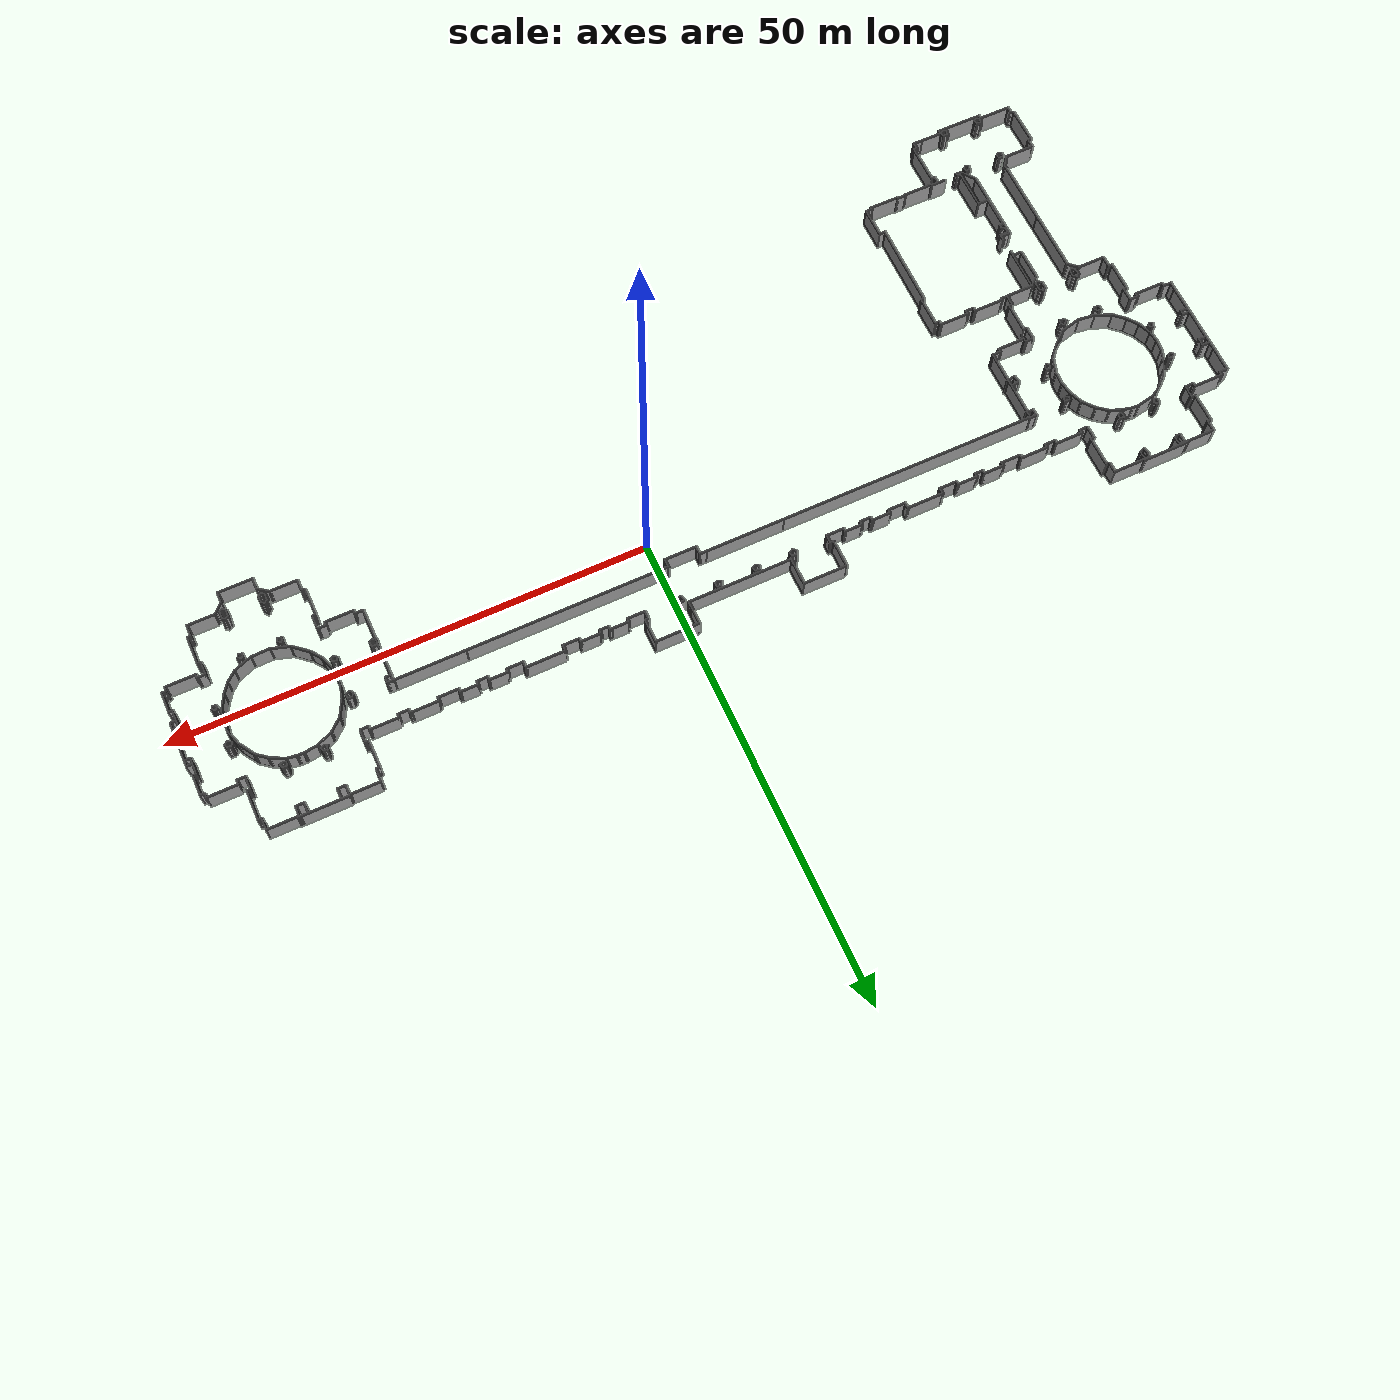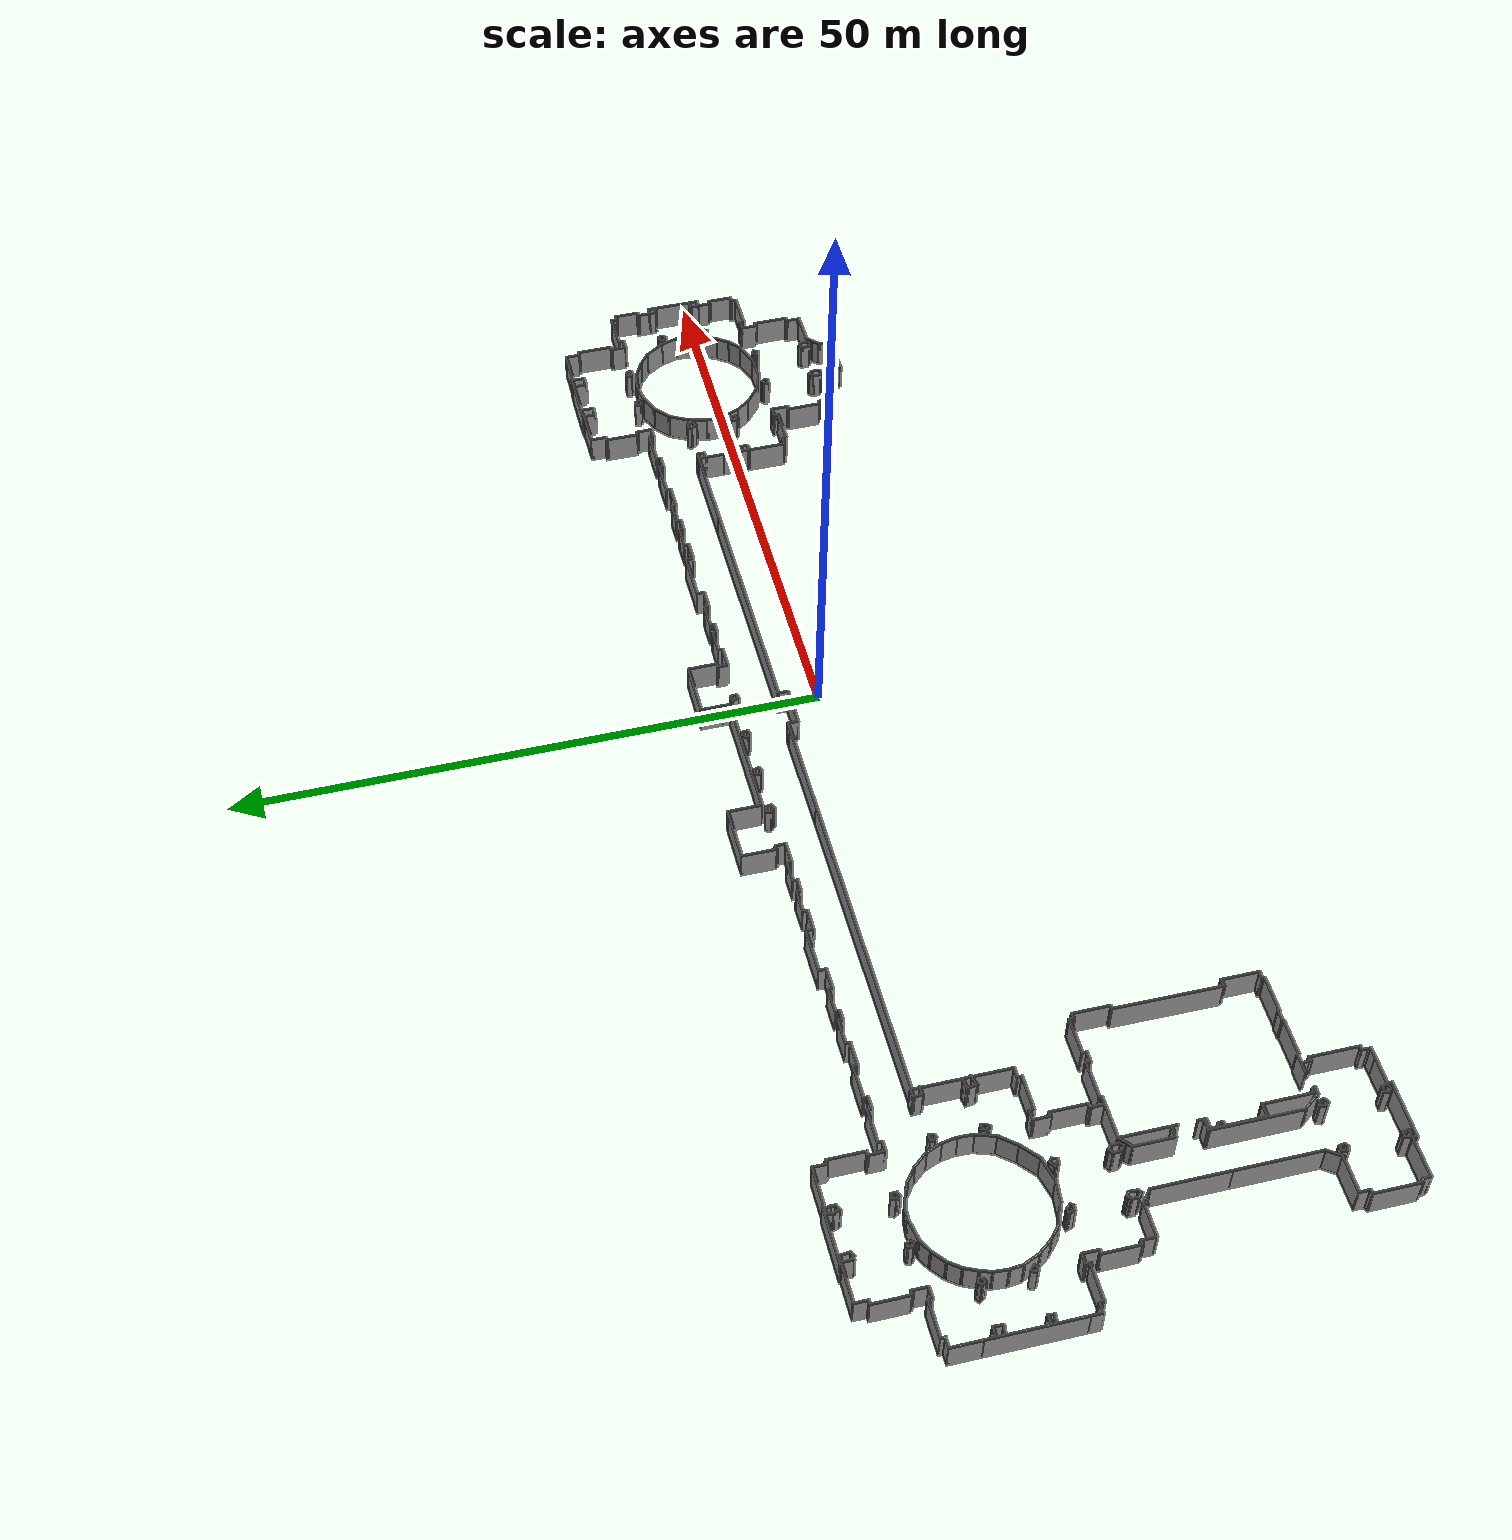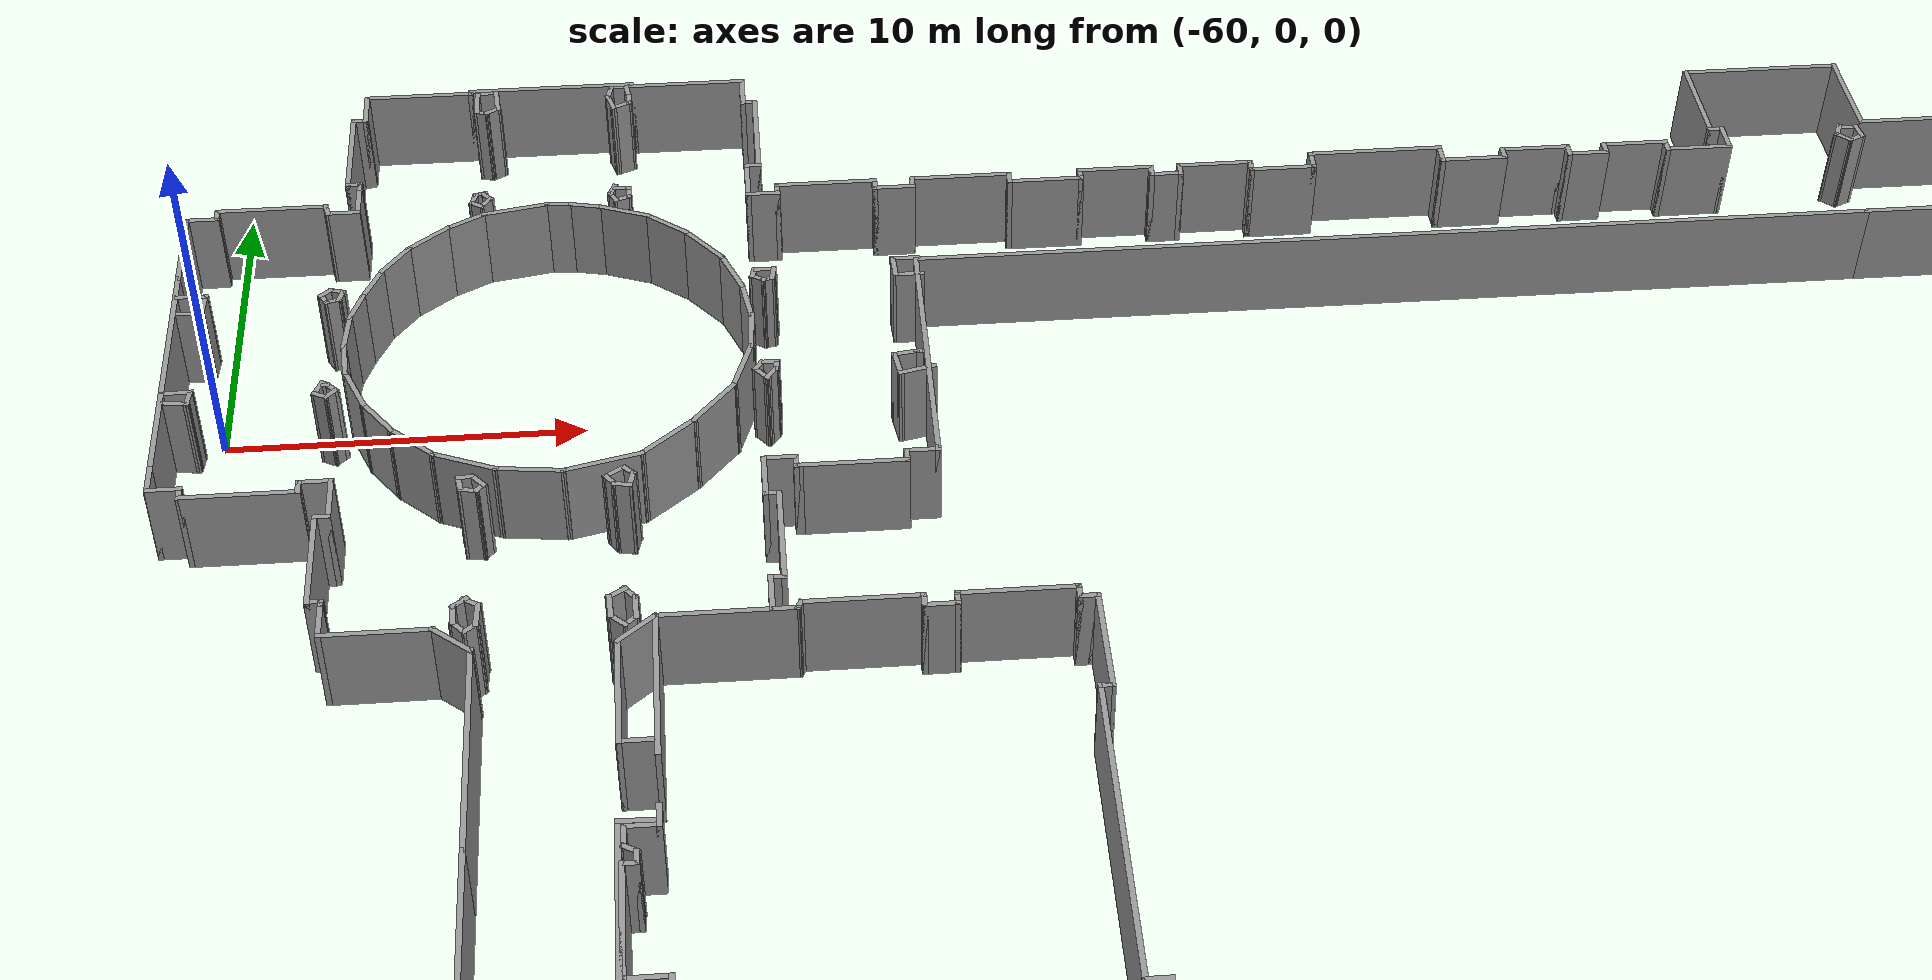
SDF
<?xml version='1.0'?>
<sdf version='1.7'>
  <model name='TD_n2'>
    <pose>-6.42415 -9.1609 0 0 -0 0</pose>
    <link name='Wall_0'>
      <collision name='Wall_0_Collision'>
        <geometry>
          <box>
            <size>3.25 0.15 2.5</size>
          </box>
        </geometry>
        <pose>0 0 1.25 0 -0 0</pose>
      </collision>
      <visual name='Wall_0_Visual'>
        <pose>0 0 1.25 0 -0 0</pose>
        <geometry>
          <box>
            <size>3.25 0.15 2.5</size>
          </box>
        </geometry>
        <material>
          <script>
            <uri>file://media/materials/scripts/gazebo.material</uri>
            <name>Gazebo/Grey</name>
          </script>
          <ambient>1 1 1 1</ambient>
        </material>
        <meta>
          <layer>0</layer>
        </meta>
      </visual>
      <pose>-36.4624 -0.392626 0 0 -0 0</pose>
    </link>
    <link name='Wall_1'>
      <collision name='Wall_1_Collision'>
        <geometry>
          <box>
            <size>0.5 0.15 2.5</size>
          </box>
        </geometry>
        <pose>0 0 1.25 0 -0 0</pose>
      </collision>
      <visual name='Wall_1_Visual'>
        <pose>0 0 1.25 0 -0 0</pose>
        <geometry>
          <box>
            <size>0.5 0.15 2.5</size>
          </box>
        </geometry>
        <material>
          <script>
            <uri>file://media/materials/scripts/gazebo.material</uri>
            <name>Gazebo/Grey</name>
          </script>
          <ambient>1 1 1 1</ambient>
        </material>
        <meta>
          <layer>0</layer>
        </meta>
      </visual>
      <pose>-34.9124 -0.567626 0 0 -0 -1.5708</pose>
    </link>
    <link name='Wall_10'>
      <collision name='Wall_10_Collision'>
        <geometry>
          <box>
            <size>0.25 0.15 2.5</size>
          </box>
        </geometry>
        <pose>0 0 1.25 0 -0 0</pose>
      </collision>
      <visual name='Wall_10_Visual'>
        <pose>0 0 1.25 0 -0 0</pose>
        <geometry>
          <box>
            <size>0.25 0.15 2.5</size>
          </box>
        </geometry>
        <material>
          <script>
            <uri>file://media/materials/scripts/gazebo.material</uri>
            <name>Gazebo/Grey</name>
          </script>
          <ambient>1 1 1 1</ambient>
        </material>
        <meta>
          <layer>0</layer>
        </meta>
      </visual>
      <pose>-30.6624 -3.84263 0 0 -0 3.14159</pose>
    </link>
    <link name='Wall_100'>
      <collision name='Wall_100_Collision'>
        <geometry>
          <box>
            <size>2.75 0.15 2.5</size>
          </box>
        </geometry>
        <pose>0 0 1.25 0 -0 0</pose>
      </collision>
      <visual name='Wall_100_Visual'>
        <pose>0 0 1.25 0 -0 0</pose>
        <geometry>
          <box>
            <size>2.75 0.15 2.5</size>
          </box>
        </geometry>
        <material>
          <script>
            <uri>file://media/materials/scripts/gazebo.material</uri>
            <name>Gazebo/Grey</name>
          </script>
          <ambient>1 1 1 1</ambient>
        </material>
        <meta>
          <layer>0</layer>
        </meta>
      </visual>
      <pose>-54.9332 15.0288 0 0 -0 1.5708</pose>
    </link>
    <link name='Wall_101'>
      <collision name='Wall_101_Collision'>
        <geometry>
          <box>
            <size>1 0.15 2.5</size>
          </box>
        </geometry>
        <pose>0 0 1.25 0 -0 0</pose>
      </collision>
      <visual name='Wall_101_Visual'>
        <pose>0 0 1.25 0 -0 0</pose>
        <geometry>
          <box>
            <size>1 0.15 2.5</size>
          </box>
        </geometry>
        <material>
          <script>
            <uri>file://media/materials/scripts/gazebo.material</uri>
            <name>Gazebo/Grey</name>
          </script>
          <ambient>1 1 1 1</ambient>
        </material>
        <meta>
          <layer>0</layer>
        </meta>
      </visual>
      <pose>-54.5082 16.3288 0 0 -0 0</pose>
    </link>
    <link name='Wall_102'>
      <collision name='Wall_102_Collision'>
        <geometry>
          <box>
            <size>0.5 0.15 2.5</size>
          </box>
        </geometry>
        <pose>0 0 1.25 0 -0 0</pose>
      </collision>
      <visual name='Wall_102_Visual'>
        <pose>0 0 1.25 0 -0 0</pose>
        <geometry>
          <box>
            <size>0.5 0.15 2.5</size>
          </box>
        </geometry>
        <material>
          <script>
            <uri>file://media/materials/scripts/gazebo.material</uri>
            <name>Gazebo/Grey</name>
          </script>
          <ambient>1 1 1 1</ambient>
        </material>
        <meta>
          <layer>0</layer>
        </meta>
      </visual>
      <pose>-54.0832 16.5038 0 0 -0 1.5708</pose>
    </link>
    <link name='Wall_103'>
      <collision name='Wall_103_Collision'>
        <geometry>
          <box>
            <size>3.25 0.15 2.5</size>
          </box>
        </geometry>
        <pose>0 0 1.25 0 -0 0</pose>
      </collision>
      <visual name='Wall_103_Visual'>
        <pose>0 0 1.25 0 -0 0</pose>
        <geometry>
          <box>
            <size>3.25 0.15 2.5</size>
          </box>
        </geometry>
        <material>
          <script>
            <uri>file://media/materials/scripts/gazebo.material</uri>
            <name>Gazebo/Grey</name>
          </script>
          <ambient>1 1 1 1</ambient>
        </material>
        <meta>
          <layer>0</layer>
        </meta>
      </visual>
      <pose>-52.5332 16.6788 0 0 -0 0</pose>
    </link>
    <link name='Wall_104'>
      <collision name='Wall_104_Collision'>
        <geometry>
          <box>
            <size>0.5 0.15 2.5</size>
          </box>
        </geometry>
        <pose>0 0 1.25 0 -0 0</pose>
      </collision>
      <visual name='Wall_104_Visual'>
        <pose>0 0 1.25 0 -0 0</pose>
        <geometry>
          <box>
            <size>0.5 0.15 2.5</size>
          </box>
        </geometry>
        <material>
          <script>
            <uri>file://media/materials/scripts/gazebo.material</uri>
            <name>Gazebo/Grey</name>
          </script>
          <ambient>1 1 1 1</ambient>
        </material>
        <meta>
          <layer>0</layer>
        </meta>
      </visual>
      <pose>-50.9379 16.5098 0 0 -0 -1.309</pose>
    </link>
    <link name='Wall_105'>
      <collision name='Wall_105_Collision'>
        <geometry>
          <box>
            <size>1 0.15 2.5</size>
          </box>
        </geometry>
        <pose>0 0 1.25 0 -0 0</pose>
      </collision>
      <visual name='Wall_105_Visual'>
        <pose>0 0 1.25 0 -0 0</pose>
        <geometry>
          <box>
            <size>1 0.15 2.5</size>
          </box>
        </geometry>
        <material>
          <script>
            <uri>file://media/materials/scripts/gazebo.material</uri>
            <name>Gazebo/Grey</name>
          </script>
          <ambient>1 1 1 1</ambient>
        </material>
        <meta>
          <layer>0</layer>
        </meta>
      </visual>
      <pose>-50.4676 16.3407 0 0 -0 0</pose>
    </link>
    <link name='Wall_106'>
      <collision name='Wall_106_Collision'>
        <geometry>
          <box>
            <size>1.25 0.15 2.5</size>
          </box>
        </geometry>
        <pose>0 0 1.25 0 -0 0</pose>
      </collision>
      <visual name='Wall_106_Visual'>
        <pose>0 0 1.25 0 -0 0</pose>
        <geometry>
          <box>
            <size>1.25 0.15 2.5</size>
          </box>
        </geometry>
        <material>
          <script>
            <uri>file://media/materials/scripts/gazebo.material</uri>
            <name>Gazebo/Grey</name>
          </script>
          <ambient>1 1 1 1</ambient>
        </material>
        <meta>
          <layer>0</layer>
        </meta>
      </visual>
      <pose>-50.0427 16.8907 0 0 -0 1.5708</pose>
    </link>
    <link name='Wall_108'>
      <collision name='Wall_108_Collision'>
        <geometry>
          <box>
            <size>0.25 0.15 2.5</size>
          </box>
        </geometry>
        <pose>0 0 1.25 0 -0 0</pose>
      </collision>
      <visual name='Wall_108_Visual'>
        <pose>0 0 1.25 0 -0 0</pose>
        <geometry>
          <box>
            <size>0.25 0.15 2.5</size>
          </box>
        </geometry>
        <material>
          <script>
            <uri>file://media/materials/scripts/gazebo.material</uri>
            <name>Gazebo/Grey</name>
          </script>
          <ambient>1 1 1 1</ambient>
        </material>
        <meta>
          <layer>0</layer>
        </meta>
      </visual>
      <pose>-50.0427 17.4907 0 0 -0 1.5708</pose>
    </link>
    <link name='Wall_109'>
      <collision name='Wall_109_Collision'>
        <geometry>
          <box>
            <size>0.15 0.15 2.5</size>
          </box>
        </geometry>
        <pose>0 0 1.25 0 -0 0</pose>
      </collision>
      <visual name='Wall_109_Visual'>
        <pose>0 0 1.25 0 -0 0</pose>
        <geometry>
          <box>
            <size>0.15 0.15 2.5</size>
          </box>
        </geometry>
        <material>
          <script>
            <uri>file://media/materials/scripts/gazebo.material</uri>
            <name>Gazebo/Grey</name>
          </script>
          <ambient>1 1 1 1</ambient>
        </material>
        <meta>
          <layer>0</layer>
        </meta>
      </visual>
      <pose>-50.0427 17.5407 0 0 -0 0</pose>
    </link>
    <link name='Wall_11'>
      <collision name='Wall_11_Collision'>
        <geometry>
          <box>
            <size>0.25 0.15 2.5</size>
          </box>
        </geometry>
        <pose>0 0 1.25 0 -0 0</pose>
      </collision>
      <visual name='Wall_11_Visual'>
        <pose>0 0 1.25 0 -0 0</pose>
        <geometry>
          <box>
            <size>0.25 0.15 2.5</size>
          </box>
        </geometry>
        <material>
          <script>
            <uri>file://media/materials/scripts/gazebo.material</uri>
            <name>Gazebo/Grey</name>
          </script>
          <ambient>1 1 1 1</ambient>
        </material>
        <meta>
          <layer>0</layer>
        </meta>
      </visual>
      <pose>-30.7624 -3.84263 0 0 -0 3.14159</pose>
    </link>
    <link name='Wall_110'>
      <collision name='Wall_110_Collision'>
        <geometry>
          <box>
            <size>0.25 0.15 2.5</size>
          </box>
        </geometry>
        <pose>0 0 1.25 0 -0 0</pose>
      </collision>
      <visual name='Wall_110_Visual'>
        <pose>0 0 1.25 0 -0 0</pose>
        <geometry>
          <box>
            <size>0.25 0.15 2.5</size>
          </box>
        </geometry>
        <material>
          <script>
            <uri>file://media/materials/scripts/gazebo.material</uri>
            <name>Gazebo/Grey</name>
          </script>
          <ambient>1 1 1 1</ambient>
        </material>
        <meta>
          <layer>0</layer>
        </meta>
      </visual>
      <pose>-50.0427 17.5907 0 0 -0 1.5708</pose>
    </link>
    <link name='Wall_111'>
      <collision name='Wall_111_Collision'>
        <geometry>
          <box>
            <size>0.5 0.15 2.5</size>
          </box>
        </geometry>
        <pose>0 0 1.25 0 -0 0</pose>
      </collision>
      <visual name='Wall_111_Visual'>
        <pose>0 0 1.25 0 -0 0</pose>
        <geometry>
          <box>
            <size>0.5 0.15 2.5</size>
          </box>
        </geometry>
        <material>
          <script>
            <uri>file://media/materials/scripts/gazebo.material</uri>
            <name>Gazebo/Grey</name>
          </script>
          <ambient>1 1 1 1</ambient>
        </material>
        <meta>
          <layer>0</layer>
        </meta>
      </visual>
      <pose>-50.2176 17.6407 0 0 -0 3.14159</pose>
    </link>
    <link name='Wall_112'>
      <collision name='Wall_112_Collision'>
        <geometry>
          <box>
            <size>3.25 0.15 2.5</size>
          </box>
        </geometry>
        <pose>0 0 1.25 0 -0 0</pose>
      </collision>
      <visual name='Wall_112_Visual'>
        <pose>0 0 1.25 0 -0 0</pose>
        <geometry>
          <box>
            <size>3.25 0.15 2.5</size>
          </box>
        </geometry>
        <material>
          <script>
            <uri>file://media/materials/scripts/gazebo.material</uri>
            <name>Gazebo/Grey</name>
          </script>
          <ambient>1 1 1 1</ambient>
        </material>
        <meta>
          <layer>0</layer>
        </meta>
      </visual>
      <pose>-50.3926 19.1907 0 0 -0 1.5708</pose>
    </link>
    <link name='Wall_113'>
      <collision name='Wall_113_Collision'>
        <geometry>
          <box>
            <size>0.5 0.15 2.5</size>
          </box>
        </geometry>
        <pose>0 0 1.25 0 -0 0</pose>
      </collision>
      <visual name='Wall_113_Visual'>
        <pose>0 0 1.25 0 -0 0</pose>
        <geometry>
          <box>
            <size>0.5 0.15 2.5</size>
          </box>
        </geometry>
        <material>
          <script>
            <uri>file://media/materials/scripts/gazebo.material</uri>
            <name>Gazebo/Grey</name>
          </script>
          <ambient>1 1 1 1</ambient>
        </material>
        <meta>
          <layer>0</layer>
        </meta>
      </visual>
      <pose>-50.2176 20.7407 0 0 -0 0</pose>
    </link>
    <link name='Wall_114'>
      <collision name='Wall_114_Collision'>
        <geometry>
          <box>
            <size>1.25 0.15 2.5</size>
          </box>
        </geometry>
        <pose>0 0 1.25 0 -0 0</pose>
      </collision>
      <visual name='Wall_114_Visual'>
        <pose>0 0 1.25 0 -0 0</pose>
        <geometry>
          <box>
            <size>1.25 0.15 2.5</size>
          </box>
        </geometry>
        <material>
          <script>
            <uri>file://media/materials/scripts/gazebo.material</uri>
            <name>Gazebo/Grey</name>
          </script>
          <ambient>1 1 1 1</ambient>
        </material>
        <meta>
          <layer>0</layer>
        </meta>
      </visual>
      <pose>-50.0427 21.2907 0 0 -0 1.5708</pose>
    </link>
    <link name='Wall_115'>
      <collision name='Wall_115_Collision'>
        <geometry>
          <box>
            <size>3.25 0.15 2.5</size>
          </box>
        </geometry>
        <pose>0 0 1.25 0 -0 0</pose>
      </collision>
      <visual name='Wall_115_Visual'>
        <pose>0 0 1.25 0 -0 0</pose>
        <geometry>
          <box>
            <size>3.25 0.15 2.5</size>
          </box>
        </geometry>
        <material>
          <script>
            <uri>file://media/materials/scripts/gazebo.material</uri>
            <name>Gazebo/Grey</name>
          </script>
          <ambient>1 1 1 1</ambient>
        </material>
        <meta>
          <layer>0</layer>
        </meta>
      </visual>
      <pose>-48.4926 21.8407 0 0 -0 0</pose>
    </link>
    <link name='Wall_116'>
      <collision name='Wall_116_Collision'>
        <geometry>
          <box>
            <size>0.25 0.15 2.5</size>
          </box>
        </geometry>
        <pose>0 0 1.25 0 -0 0</pose>
      </collision>
      <visual name='Wall_116_Visual'>
        <pose>0 0 1.25 0 -0 0</pose>
        <geometry>
          <box>
            <size>0.25 0.15 2.5</size>
          </box>
        </geometry>
        <material>
          <script>
            <uri>file://media/materials/scripts/gazebo.material</uri>
            <name>Gazebo/Grey</name>
          </script>
          <ambient>1 1 1 1</ambient>
        </material>
        <meta>
          <layer>0</layer>
        </meta>
      </visual>
      <pose>-46.9426 21.8907 0 0 -0 1.5708</pose>
    </link>
    <link name='Wall_117'>
      <collision name='Wall_117_Collision'>
        <geometry>
          <box>
            <size>5 0.15 2.5</size>
          </box>
        </geometry>
        <pose>0 0 1.25 0 -0 0</pose>
      </collision>
      <visual name='Wall_117_Visual'>
        <pose>0 0 1.25 0 -0 0</pose>
        <geometry>
          <box>
            <size>5 0.15 2.5</size>
          </box>
        </geometry>
        <material>
          <script>
            <uri>file://media/materials/scripts/gazebo.material</uri>
            <name>Gazebo/Grey</name>
          </script>
          <ambient>1 1 1 1</ambient>
        </material>
        <meta>
          <layer>0</layer>
        </meta>
      </visual>
      <pose>-44.5176 21.9407 0 0 -0 0</pose>
    </link>
    <link name='Wall_118'>
      <collision name='Wall_118_Collision'>
        <geometry>
          <box>
            <size>0.25 0.15 2.5</size>
          </box>
        </geometry>
        <pose>0 0 1.25 0 -0 0</pose>
      </collision>
      <visual name='Wall_118_Visual'>
        <pose>0 0 1.25 0 -0 0</pose>
        <geometry>
          <box>
            <size>0.25 0.15 2.5</size>
          </box>
        </geometry>
        <material>
          <script>
            <uri>file://media/materials/scripts/gazebo.material</uri>
            <name>Gazebo/Grey</name>
          </script>
          <ambient>1 1 1 1</ambient>
        </material>
        <meta>
          <layer>0</layer>
        </meta>
      </visual>
      <pose>-42.0926 21.8907 0 0 -0 -1.5708</pose>
    </link>
    <link name='Wall_119'>
      <collision name='Wall_119_Collision'>
        <geometry>
          <box>
            <size>3.5 0.15 2.5</size>
          </box>
        </geometry>
        <pose>0 0 1.25 0 -0 0</pose>
      </collision>
      <visual name='Wall_119_Visual'>
        <pose>0 0 1.25 0 -0 0</pose>
        <geometry>
          <box>
            <size>3.5 0.15 2.5</size>
          </box>
        </geometry>
        <material>
          <script>
            <uri>file://media/materials/scripts/gazebo.material</uri>
            <name>Gazebo/Grey</name>
          </script>
          <ambient>1 1 1 1</ambient>
        </material>
        <meta>
          <layer>0</layer>
        </meta>
      </visual>
      <pose>-40.4177 21.8407 0 0 -0 0</pose>
    </link>
    <link name='Wall_120'>
      <collision name='Wall_120_Collision'>
        <geometry>
          <box>
            <size>1.25 0.15 2.5</size>
          </box>
        </geometry>
        <pose>0 0 1.25 0 -0 0</pose>
      </collision>
      <visual name='Wall_120_Visual'>
        <pose>0 0 1.25 0 -0 0</pose>
        <geometry>
          <box>
            <size>1.25 0.15 2.5</size>
          </box>
        </geometry>
        <material>
          <script>
            <uri>file://media/materials/scripts/gazebo.material</uri>
            <name>Gazebo/Grey</name>
          </script>
          <ambient>1 1 1 1</ambient>
        </material>
        <meta>
          <layer>0</layer>
        </meta>
      </visual>
      <pose>-38.7426 21.2907 0 0 -0 -1.5708</pose>
    </link>
    <link name='Wall_121'>
      <collision name='Wall_121_Collision'>
        <geometry>
          <box>
            <size>0.5 0.15 2.5</size>
          </box>
        </geometry>
        <pose>0 0 1.25 0 -0 0</pose>
      </collision>
      <visual name='Wall_121_Visual'>
        <pose>0 0 1.25 0 -0 0</pose>
        <geometry>
          <box>
            <size>0.5 0.15 2.5</size>
          </box>
        </geometry>
        <material>
          <script>
            <uri>file://media/materials/scripts/gazebo.material</uri>
            <name>Gazebo/Grey</name>
          </script>
          <ambient>1 1 1 1</ambient>
        </material>
        <meta>
          <layer>0</layer>
        </meta>
      </visual>
      <pose>-38.5676 20.7407 0 0 -0 0</pose>
    </link>
    <link name='Wall_122'>
      <collision name='Wall_122_Collision'>
        <geometry>
          <box>
            <size>3.25 0.15 2.5</size>
          </box>
        </geometry>
        <pose>0 0 1.25 0 -0 0</pose>
      </collision>
      <visual name='Wall_122_Visual'>
        <pose>0 0 1.25 0 -0 0</pose>
        <geometry>
          <box>
            <size>3.25 0.15 2.5</size>
          </box>
        </geometry>
        <material>
          <script>
            <uri>file://media/materials/scripts/gazebo.material</uri>
            <name>Gazebo/Grey</name>
          </script>
          <ambient>1 1 1 1</ambient>
        </material>
        <meta>
          <layer>0</layer>
        </meta>
      </visual>
      <pose>-38.3926 19.1907 0 0 -0 -1.5708</pose>
    </link>
    <link name='Wall_123'>
      <collision name='Wall_123_Collision'>
        <geometry>
          <box>
            <size>0.5 0.15 2.5</size>
          </box>
        </geometry>
        <pose>0 0 1.25 0 -0 0</pose>
      </collision>
      <visual name='Wall_123_Visual'>
        <pose>0 0 1.25 0 -0 0</pose>
        <geometry>
          <box>
            <size>0.5 0.15 2.5</size>
          </box>
        </geometry>
        <material>
          <script>
            <uri>file://media/materials/scripts/gazebo.material</uri>
            <name>Gazebo/Grey</name>
          </script>
          <ambient>1 1 1 1</ambient>
        </material>
        <meta>
          <layer>0</layer>
        </meta>
      </visual>
      <pose>-38.5676 17.6407 0 0 -0 3.14159</pose>
    </link>
    <link name='Wall_125'>
      <collision name='Wall_125_Collision'>
        <geometry>
          <box>
            <size>1.5 0.15 2.5</size>
          </box>
        </geometry>
        <pose>0 0 1.25 0 -0 0</pose>
      </collision>
      <visual name='Wall_125_Visual'>
        <pose>0 0 1.25 0 -0 0</pose>
        <geometry>
          <box>
            <size>1.5 0.15 2.5</size>
          </box>
        </geometry>
        <material>
          <script>
            <uri>file://media/materials/scripts/gazebo.material</uri>
            <name>Gazebo/Grey</name>
          </script>
          <ambient>1 1 1 1</ambient>
        </material>
        <meta>
          <layer>0</layer>
        </meta>
      </visual>
      <pose>-38.7426 16.9657 0 0 -0 -1.5708</pose>
    </link>
    <link name='Wall_126'>
      <collision name='Wall_126_Collision'>
        <geometry>
          <box>
            <size>1 0.15 2.5</size>
          </box>
        </geometry>
        <pose>0 0 1.25 0 -0 0</pose>
      </collision>
      <visual name='Wall_126_Visual'>
        <pose>0 0 1.25 0 -0 0</pose>
        <geometry>
          <box>
            <size>1 0.15 2.5</size>
          </box>
        </geometry>
        <material>
          <script>
            <uri>file://media/materials/scripts/gazebo.material</uri>
            <name>Gazebo/Grey</name>
          </script>
          <ambient>1 1 1 1</ambient>
        </material>
        <meta>
          <layer>0</layer>
        </meta>
      </visual>
      <pose>-38.3176 16.2907 0 0 -0 0</pose>
    </link>
    <link name='Wall_127'>
      <collision name='Wall_127_Collision'>
        <geometry>
          <box>
            <size>0.5 0.15 2.5</size>
          </box>
        </geometry>
        <pose>0 0 1.25 0 -0 0</pose>
      </collision>
      <visual name='Wall_127_Visual'>
        <pose>0 0 1.25 0 -0 0</pose>
        <geometry>
          <box>
            <size>0.5 0.15 2.5</size>
          </box>
        </geometry>
        <material>
          <script>
            <uri>file://media/materials/scripts/gazebo.material</uri>
            <name>Gazebo/Grey</name>
          </script>
          <ambient>1 1 1 1</ambient>
        </material>
        <meta>
          <layer>0</layer>
        </meta>
      </visual>
      <pose>-37.8926 16.4657 0 0 -0 1.5708</pose>
    </link>
    <link name='Wall_128'>
      <collision name='Wall_128_Collision'>
        <geometry>
          <box>
            <size>3 0.15 2.5</size>
          </box>
        </geometry>
        <pose>0 0 1.25 0 -0 0</pose>
      </collision>
      <visual name='Wall_128_Visual'>
        <pose>0 0 1.25 0 -0 0</pose>
        <geometry>
          <box>
            <size>3 0.15 2.5</size>
          </box>
        </geometry>
        <material>
          <script>
            <uri>file://media/materials/scripts/gazebo.material</uri>
            <name>Gazebo/Grey</name>
          </script>
          <ambient>1 1 1 1</ambient>
        </material>
        <meta>
          <layer>0</layer>
        </meta>
      </visual>
      <pose>-36.4676 16.6407 0 0 -0 0</pose>
    </link>
    <link name='Wall_129'>
      <collision name='Wall_129_Collision'>
        <geometry>
          <box>
            <size>0.5 0.15 2.5</size>
          </box>
        </geometry>
        <pose>0 0 1.25 0 -0 0</pose>
      </collision>
      <visual name='Wall_129_Visual'>
        <pose>0 0 1.25 0 -0 0</pose>
        <geometry>
          <box>
            <size>0.5 0.15 2.5</size>
          </box>
        </geometry>
        <material>
          <script>
            <uri>file://media/materials/scripts/gazebo.material</uri>
            <name>Gazebo/Grey</name>
          </script>
          <ambient>1 1 1 1</ambient>
        </material>
        <meta>
          <layer>0</layer>
        </meta>
      </visual>
      <pose>-35.0427 16.4657 0 0 -0 -1.5708</pose>
    </link>
    <link name='Wall_130'>
      <collision name='Wall_130_Collision'>
        <geometry>
          <box>
            <size>1.25 0.15 2.5</size>
          </box>
        </geometry>
        <pose>0 0 1.25 0 -0 0</pose>
      </collision>
      <visual name='Wall_130_Visual'>
        <pose>0 0 1.25 0 -0 0</pose>
        <geometry>
          <box>
            <size>1.25 0.15 2.5</size>
          </box>
        </geometry>
        <material>
          <script>
            <uri>file://media/materials/scripts/gazebo.material</uri>
            <name>Gazebo/Grey</name>
          </script>
          <ambient>1 1 1 1</ambient>
        </material>
        <meta>
          <layer>0</layer>
        </meta>
      </visual>
      <pose>-34.4926 16.2907 0 0 -0 0</pose>
    </link>
    <link name='Wall_131'>
      <collision name='Wall_131_Collision'>
        <geometry>
          <box>
            <size>0.5 0.15 2.5</size>
          </box>
        </geometry>
        <pose>0 0 1.25 0 -0 0</pose>
      </collision>
      <visual name='Wall_131_Visual'>
        <pose>0 0 1.25 0 -0 0</pose>
        <geometry>
          <box>
            <size>0.5 0.15 2.5</size>
          </box>
        </geometry>
        <material>
          <script>
            <uri>file://media/materials/scripts/gazebo.material</uri>
            <name>Gazebo/Grey</name>
          </script>
          <ambient>1 1 1 1</ambient>
        </material>
        <meta>
          <layer>0</layer>
        </meta>
      </visual>
      <pose>-33.9426 16.4657 0 0 -0 1.5708</pose>
    </link>
    <link name='Wall_132'>
      <collision name='Wall_132_Collision'>
        <geometry>
          <box>
            <size>3 0.15 2.5</size>
          </box>
        </geometry>
        <pose>0 0 1.25 0 -0 0</pose>
      </collision>
      <visual name='Wall_132_Visual'>
        <pose>0 0 1.25 0 -0 0</pose>
        <geometry>
          <box>
            <size>3 0.15 2.5</size>
          </box>
        </geometry>
        <material>
          <script>
            <uri>file://media/materials/scripts/gazebo.material</uri>
            <name>Gazebo/Grey</name>
          </script>
          <ambient>1 1 1 1</ambient>
        </material>
        <meta>
          <layer>0</layer>
        </meta>
      </visual>
      <pose>-32.5176 16.6407 0 0 -0 0</pose>
    </link>
    <link name='Wall_133'>
      <collision name='Wall_133_Collision'>
        <geometry>
          <box>
            <size>0.5 0.15 2.5</size>
          </box>
        </geometry>
        <pose>0 0 1.25 0 -0 0</pose>
      </collision>
      <visual name='Wall_133_Visual'>
        <pose>0 0 1.25 0 -0 0</pose>
        <geometry>
          <box>
            <size>0.5 0.15 2.5</size>
          </box>
        </geometry>
        <material>
          <script>
            <uri>file://media/materials/scripts/gazebo.material</uri>
            <name>Gazebo/Grey</name>
          </script>
          <ambient>1 1 1 1</ambient>
        </material>
        <meta>
          <layer>0</layer>
        </meta>
      </visual>
      <pose>-31.0926 16.4657 0 0 -0 -1.5708</pose>
    </link>
    <link name='Wall_134'>
      <collision name='Wall_134_Collision'>
        <geometry>
          <box>
            <size>2.25 0.15 2.5</size>
          </box>
        </geometry>
        <pose>0 0 1.25 0 -0 0</pose>
      </collision>
      <visual name='Wall_134_Visual'>
        <pose>0 0 1.25 0 -0 0</pose>
        <geometry>
          <box>
            <size>2.25 0.15 2.5</size>
          </box>
        </geometry>
        <material>
          <script>
            <uri>file://media/materials/scripts/gazebo.material</uri>
            <name>Gazebo/Grey</name>
          </script>
          <ambient>1 1 1 1</ambient>
        </material>
        <meta>
          <layer>0</layer>
        </meta>
      </visual>
      <pose>-30.0426 16.2907 0 0 -0 0</pose>
    </link>
    <link name='Wall_135'>
      <collision name='Wall_135_Collision'>
        <geometry>
          <box>
            <size>0.5 0.15 2.5</size>
          </box>
        </geometry>
        <pose>0 0 1.25 0 -0 0</pose>
      </collision>
      <visual name='Wall_135_Visual'>
        <pose>0 0 1.25 0 -0 0</pose>
        <geometry>
          <box>
            <size>0.5 0.15 2.5</size>
          </box>
        </geometry>
        <material>
          <script>
            <uri>file://media/materials/scripts/gazebo.material</uri>
            <name>Gazebo/Grey</name>
          </script>
          <ambient>1 1 1 1</ambient>
        </material>
        <meta>
          <layer>0</layer>
        </meta>
      </visual>
      <pose>-28.9926 16.4657 0 0 -0 1.5708</pose>
    </link>
    <link name='Wall_136'>
      <collision name='Wall_136_Collision'>
        <geometry>
          <box>
            <size>2.25 0.15 2.5</size>
          </box>
        </geometry>
        <pose>0 0 1.25 0 -0 0</pose>
      </collision>
      <visual name='Wall_136_Visual'>
        <pose>0 0 1.25 0 -0 0</pose>
        <geometry>
          <box>
            <size>2.25 0.15 2.5</size>
          </box>
        </geometry>
        <material>
          <script>
            <uri>file://media/materials/scripts/gazebo.material</uri>
            <name>Gazebo/Grey</name>
          </script>
          <ambient>1 1 1 1</ambient>
        </material>
        <meta>
          <layer>0</layer>
        </meta>
      </visual>
      <pose>-27.9426 16.6407 0 0 -0 0</pose>
    </link>
    <link name='Wall_137'>
      <collision name='Wall_137_Collision'>
        <geometry>
          <box>
            <size>0.5 0.15 2.5</size>
          </box>
        </geometry>
        <pose>0 0 1.25 0 -0 0</pose>
      </collision>
      <visual name='Wall_137_Visual'>
        <pose>0 0 1.25 0 -0 0</pose>
        <geometry>
          <box>
            <size>0.5 0.15 2.5</size>
          </box>
        </geometry>
        <material>
          <script>
            <uri>file://media/materials/scripts/gazebo.material</uri>
            <name>Gazebo/Grey</name>
          </script>
          <ambient>1 1 1 1</ambient>
        </material>
        <meta>
          <layer>0</layer>
        </meta>
      </visual>
      <pose>-26.8926 16.4657 0 0 -0 -1.5708</pose>
    </link>
    <link name='Wall_138'>
      <collision name='Wall_138_Collision'>
        <geometry>
          <box>
            <size>1 0.15 2.5</size>
          </box>
        </geometry>
        <pose>0 0 1.25 0 -0 0</pose>
      </collision>
      <visual name='Wall_138_Visual'>
        <pose>0 0 1.25 0 -0 0</pose>
        <geometry>
          <box>
            <size>1 0.15 2.5</size>
          </box>
        </geometry>
        <material>
          <script>
            <uri>file://media/materials/scripts/gazebo.material</uri>
            <name>Gazebo/Grey</name>
          </script>
          <ambient>1 1 1 1</ambient>
        </material>
        <meta>
          <layer>0</layer>
        </meta>
      </visual>
      <pose>-26.4676 16.2907 0 0 -0 0</pose>
    </link>
    <link name='Wall_139'>
      <collision name='Wall_139_Collision'>
        <geometry>
          <box>
            <size>0.5 0.15 2.5</size>
          </box>
        </geometry>
        <pose>0 0 1.25 0 -0 0</pose>
      </collision>
      <visual name='Wall_139_Visual'>
        <pose>0 0 1.25 0 -0 0</pose>
        <geometry>
          <box>
            <size>0.5 0.15 2.5</size>
          </box>
        </geometry>
        <material>
          <script>
            <uri>file://media/materials/scripts/gazebo.material</uri>
            <name>Gazebo/Grey</name>
          </script>
          <ambient>1 1 1 1</ambient>
        </material>
        <meta>
          <layer>0</layer>
        </meta>
      </visual>
      <pose>-26.0426 16.4657 0 0 -0 1.5708</pose>
    </link>
    <link name='Wall_140'>
      <collision name='Wall_140_Collision'>
        <geometry>
          <box>
            <size>2.25 0.15 2.5</size>
          </box>
        </geometry>
        <pose>0 0 1.25 0 -0 0</pose>
      </collision>
      <visual name='Wall_140_Visual'>
        <pose>0 0 1.25 0 -0 0</pose>
        <geometry>
          <box>
            <size>2.25 0.15 2.5</size>
          </box>
        </geometry>
        <material>
          <script>
            <uri>file://media/materials/scripts/gazebo.material</uri>
            <name>Gazebo/Grey</name>
          </script>
          <ambient>1 1 1 1</ambient>
        </material>
        <meta>
          <layer>0</layer>
        </meta>
      </visual>
      <pose>-24.9926 16.6407 0 0 -0 0</pose>
    </link>
    <link name='Wall_141'>
      <collision name='Wall_141_Collision'>
        <geometry>
          <box>
            <size>0.5 0.15 2.5</size>
          </box>
        </geometry>
        <pose>0 0 1.25 0 -0 0</pose>
      </collision>
      <visual name='Wall_141_Visual'>
        <pose>0 0 1.25 0 -0 0</pose>
        <geometry>
          <box>
            <size>0.5 0.15 2.5</size>
          </box>
        </geometry>
        <material>
          <script>
            <uri>file://media/materials/scripts/gazebo.material</uri>
            <name>Gazebo/Grey</name>
          </script>
          <ambient>1 1 1 1</ambient>
        </material>
        <meta>
          <layer>0</layer>
        </meta>
      </visual>
      <pose>-23.9426 16.4657 0 0 -0 -1.5708</pose>
    </link>
    <link name='Wall_143'>
      <collision name='Wall_143_Collision'>
        <geometry>
          <box>
            <size>2 0.15 2.5</size>
          </box>
        </geometry>
        <pose>0 0 1.25 0 -0 0</pose>
      </collision>
      <visual name='Wall_143_Visual'>
        <pose>0 0 1.25 0 -0 0</pose>
        <geometry>
          <box>
            <size>2 0.15 2.5</size>
          </box>
        </geometry>
        <material>
          <script>
            <uri>file://media/materials/scripts/gazebo.material</uri>
            <name>Gazebo/Grey</name>
          </script>
          <ambient>1 1 1 1</ambient>
        </material>
        <meta>
          <layer>0</layer>
        </meta>
      </visual>
      <pose>-23.0176 16.2907 0 0 -0 0</pose>
    </link>
    <link name='Wall_144'>
      <collision name='Wall_144_Collision'>
        <geometry>
          <box>
            <size>0.75 0.15 2.5</size>
          </box>
        </geometry>
        <pose>0 0 1.25 0 -0 0</pose>
      </collision>
      <visual name='Wall_144_Visual'>
        <pose>0 0 1.25 0 -0 0</pose>
        <geometry>
          <box>
            <size>0.75 0.15 2.5</size>
          </box>
        </geometry>
        <material>
          <script>
            <uri>file://media/materials/scripts/gazebo.material</uri>
            <name>Gazebo/Grey</name>
          </script>
          <ambient>1 1 1 1</ambient>
        </material>
        <meta>
          <layer>0</layer>
        </meta>
      </visual>
      <pose>-22.0926 16.5907 0 0 -0 1.5708</pose>
    </link>
    <link name='Wall_145'>
      <collision name='Wall_145_Collision'>
        <geometry>
          <box>
            <size>4 0.15 2.5</size>
          </box>
        </geometry>
        <pose>0 0 1.25 0 -0 0</pose>
      </collision>
      <visual name='Wall_145_Visual'>
        <pose>0 0 1.25 0 -0 0</pose>
        <geometry>
          <box>
            <size>4 0.15 2.5</size>
          </box>
        </geometry>
        <material>
          <script>
            <uri>file://media/materials/scripts/gazebo.material</uri>
            <name>Gazebo/Grey</name>
          </script>
          <ambient>1 1 1 1</ambient>
        </material>
        <meta>
          <layer>0</layer>
        </meta>
      </visual>
      <pose>-20.1676 16.8907 0 0 -0 0</pose>
    </link>
    <link name='Wall_146'>
      <collision name='Wall_146_Collision'>
        <geometry>
          <box>
            <size>0.75 0.15 2.5</size>
          </box>
        </geometry>
        <pose>0 0 1.25 0 -0 0</pose>
      </collision>
      <visual name='Wall_146_Visual'>
        <pose>0 0 1.25 0 -0 0</pose>
        <geometry>
          <box>
            <size>0.75 0.15 2.5</size>
          </box>
        </geometry>
        <material>
          <script>
            <uri>file://media/materials/scripts/gazebo.material</uri>
            <name>Gazebo/Grey</name>
          </script>
          <ambient>1 1 1 1</ambient>
        </material>
        <meta>
          <layer>0</layer>
        </meta>
      </visual>
      <pose>-18.2426 16.5907 0 0 -0 -1.5708</pose>
    </link>
    <link name='Wall_147'>
      <collision name='Wall_147_Collision'>
        <geometry>
          <box>
            <size>2 0.15 2.5</size>
          </box>
        </geometry>
        <pose>0 0 1.25 0 -0 0</pose>
      </collision>
      <visual name='Wall_147_Visual'>
        <pose>0 0 1.25 0 -0 0</pose>
        <geometry>
          <box>
            <size>2 0.15 2.5</size>
          </box>
        </geometry>
        <material>
          <script>
            <uri>file://media/materials/scripts/gazebo.material</uri>
            <name>Gazebo/Grey</name>
          </script>
          <ambient>1 1 1 1</ambient>
        </material>
        <meta>
          <layer>0</layer>
        </meta>
      </visual>
      <pose>-17.3176 16.2907 0 0 -0 0</pose>
    </link>
    <link name='Wall_148'>
      <collision name='Wall_148_Collision'>
        <geometry>
          <box>
            <size>0.5 0.15 2.5</size>
          </box>
        </geometry>
        <pose>0 0 1.25 0 -0 0</pose>
      </collision>
      <visual name='Wall_148_Visual'>
        <pose>0 0 1.25 0 -0 0</pose>
        <geometry>
          <box>
            <size>0.5 0.15 2.5</size>
          </box>
        </geometry>
        <material>
          <script>
            <uri>file://media/materials/scripts/gazebo.material</uri>
            <name>Gazebo/Grey</name>
          </script>
          <ambient>1 1 1 1</ambient>
        </material>
        <meta>
          <layer>0</layer>
        </meta>
      </visual>
      <pose>-16.3926 16.4657 0 0 -0 1.5708</pose>
    </link>
    <link name='Wall_149'>
      <collision name='Wall_149_Collision'>
        <geometry>
          <box>
            <size>2 0.15 2.5</size>
          </box>
        </geometry>
        <pose>0 0 1.25 0 -0 0</pose>
      </collision>
      <visual name='Wall_149_Visual'>
        <pose>0 0 1.25 0 -0 0</pose>
        <geometry>
          <box>
            <size>2 0.15 2.5</size>
          </box>
        </geometry>
        <material>
          <script>
            <uri>file://media/materials/scripts/gazebo.material</uri>
            <name>Gazebo/Grey</name>
          </script>
          <ambient>1 1 1 1</ambient>
        </material>
        <meta>
          <layer>0</layer>
        </meta>
      </visual>
      <pose>-15.4676 16.6407 0 0 -0 0</pose>
    </link>
    <link name='Wall_150'>
      <collision name='Wall_150_Collision'>
        <geometry>
          <box>
            <size>0.25 0.15 2.5</size>
          </box>
        </geometry>
        <pose>0 0 1.25 0 -0 0</pose>
      </collision>
      <visual name='Wall_150_Visual'>
        <pose>0 0 1.25 0 -0 0</pose>
        <geometry>
          <box>
            <size>0.25 0.15 2.5</size>
          </box>
        </geometry>
        <material>
          <script>
            <uri>file://media/materials/scripts/gazebo.material</uri>
            <name>Gazebo/Grey</name>
          </script>
          <ambient>1 1 1 1</ambient>
        </material>
        <meta>
          <layer>0</layer>
        </meta>
      </visual>
      <pose>-14.4926 16.6407 0 0 -0 0</pose>
    </link>
    <link name='Wall_151'>
      <collision name='Wall_151_Collision'>
        <geometry>
          <box>
            <size>0.5 0.15 2.5</size>
          </box>
        </geometry>
        <pose>0 0 1.25 0 -0 0</pose>
      </collision>
      <visual name='Wall_151_Visual'>
        <pose>0 0 1.25 0 -0 0</pose>
        <geometry>
          <box>
            <size>0.5 0.15 2.5</size>
          </box>
        </geometry>
        <material>
          <script>
            <uri>file://media/materials/scripts/gazebo.material</uri>
            <name>Gazebo/Grey</name>
          </script>
          <ambient>1 1 1 1</ambient>
        </material>
        <meta>
          <layer>0</layer>
        </meta>
      </visual>
      <pose>-14.4426 16.4657 0 0 -0 -1.5708</pose>
    </link>
    <link name='Wall_152'>
      <collision name='Wall_152_Collision'>
        <geometry>
          <box>
            <size>1.25 0.15 2.5</size>
          </box>
        </geometry>
        <pose>0 0 1.25 0 -0 0</pose>
      </collision>
      <visual name='Wall_152_Visual'>
        <pose>0 0 1.25 0 -0 0</pose>
        <geometry>
          <box>
            <size>1.25 0.15 2.5</size>
          </box>
        </geometry>
        <material>
          <script>
            <uri>file://media/materials/scripts/gazebo.material</uri>
            <name>Gazebo/Grey</name>
          </script>
          <ambient>1 1 1 1</ambient>
        </material>
        <meta>
          <layer>0</layer>
        </meta>
      </visual>
      <pose>-13.8926 16.2907 0 0 -0 0</pose>
    </link>
    <link name='Wall_153'>
      <collision name='Wall_153_Collision'>
        <geometry>
          <box>
            <size>0.5 0.15 2.5</size>
          </box>
        </geometry>
        <pose>0 0 1.25 0 -0 0</pose>
      </collision>
      <visual name='Wall_153_Visual'>
        <pose>0 0 1.25 0 -0 0</pose>
        <geometry>
          <box>
            <size>0.5 0.15 2.5</size>
          </box>
        </geometry>
        <material>
          <script>
            <uri>file://media/materials/scripts/gazebo.material</uri>
            <name>Gazebo/Grey</name>
          </script>
          <ambient>1 1 1 1</ambient>
        </material>
        <meta>
          <layer>0</layer>
        </meta>
      </visual>
      <pose>-13.3426 16.4657 0 0 -0 1.5708</pose>
    </link>
    <link name='Wall_154'>
      <collision name='Wall_154_Collision'>
        <geometry>
          <box>
            <size>2 0.15 2.5</size>
          </box>
        </geometry>
        <pose>0 0 1.25 0 -0 0</pose>
      </collision>
      <visual name='Wall_154_Visual'>
        <pose>0 0 1.25 0 -0 0</pose>
        <geometry>
          <box>
            <size>2 0.15 2.5</size>
          </box>
        </geometry>
        <material>
          <script>
            <uri>file://media/materials/scripts/gazebo.material</uri>
            <name>Gazebo/Grey</name>
          </script>
          <ambient>1 1 1 1</ambient>
        </material>
        <meta>
          <layer>0</layer>
        </meta>
      </visual>
      <pose>-12.4176 16.6407 0 0 -0 0</pose>
    </link>
    <link name='Wall_155'>
      <collision name='Wall_155_Collision'>
        <geometry>
          <box>
            <size>0.5 0.15 2.5</size>
          </box>
        </geometry>
        <pose>0 0 1.25 0 -0 0</pose>
      </collision>
      <visual name='Wall_155_Visual'>
        <pose>0 0 1.25 0 -0 0</pose>
        <geometry>
          <box>
            <size>0.5 0.15 2.5</size>
          </box>
        </geometry>
        <material>
          <script>
            <uri>file://media/materials/scripts/gazebo.material</uri>
            <name>Gazebo/Grey</name>
          </script>
          <ambient>1 1 1 1</ambient>
        </material>
        <meta>
          <layer>0</layer>
        </meta>
      </visual>
      <pose>-11.4926 16.4657 0 0 -0 -1.5708</pose>
    </link>
    <link name='Wall_156'>
      <collision name='Wall_156_Collision'>
        <geometry>
          <box>
            <size>2 0.15 2.5</size>
          </box>
        </geometry>
        <pose>0 0 1.25 0 -0 0</pose>
      </collision>
      <visual name='Wall_156_Visual'>
        <pose>0 0 1.25 0 -0 0</pose>
        <geometry>
          <box>
            <size>2 0.15 2.5</size>
          </box>
        </geometry>
        <material>
          <script>
            <uri>file://media/materials/scripts/gazebo.material</uri>
            <name>Gazebo/Grey</name>
          </script>
          <ambient>1 1 1 1</ambient>
        </material>
        <meta>
          <layer>0</layer>
        </meta>
      </visual>
      <pose>-10.5676 16.2907 0 0 -0 0</pose>
    </link>
    <link name='Wall_159'>
      <collision name='Wall_159_Collision'>
        <geometry>
          <box>
            <size>1 0.15 2.5</size>
          </box>
        </geometry>
        <pose>0 0 1.25 0 -0 0</pose>
      </collision>
      <visual name='Wall_159_Visual'>
        <pose>0 0 1.25 0 -0 0</pose>
        <geometry>
          <box>
            <size>1 0.15 2.5</size>
          </box>
        </geometry>
        <material>
          <script>
            <uri>file://media/materials/scripts/gazebo.material</uri>
            <name>Gazebo/Grey</name>
          </script>
          <ambient>1 1 1 1</ambient>
        </material>
        <meta>
          <layer>0</layer>
        </meta>
      </visual>
      <pose>-9.64265 16.7157 0 0 -0 1.5708</pose>
    </link>
    <link name='Wall_16'>
      <collision name='Wall_16_Collision'>
        <geometry>
          <box>
            <size>9.16715 0.15 2.5</size>
          </box>
        </geometry>
        <pose>0 0 1.25 0 -0 0</pose>
      </collision>
      <visual name='Wall_16_Visual'>
        <pose>0 0 1.25 0 -0 0</pose>
        <geometry>
          <box>
            <size>9.16715 0.15 2.5</size>
          </box>
        </geometry>
        <material>
          <script>
            <uri>file://media/materials/scripts/gazebo.material</uri>
            <name>Gazebo/Grey</name>
          </script>
          <ambient>1 1 1 1</ambient>
        </material>
        <meta>
          <layer>0</layer>
        </meta>
      </visual>
      <pose>-30.8459 -8.35108 0 0 -0 1.56337</pose>
    </link>
    <link name='Wall_160'>
      <collision name='Wall_160_Collision'>
        <geometry>
          <box>
            <size>0.5 0.15 2.5</size>
          </box>
        </geometry>
        <pose>0 0 1.25 0 -0 0</pose>
      </collision>
      <visual name='Wall_160_Visual'>
        <pose>0 0 1.25 0 -0 0</pose>
        <geometry>
          <box>
            <size>0.5 0.15 2.5</size>
          </box>
        </geometry>
        <material>
          <script>
            <uri>file://media/materials/scripts/gazebo.material</uri>
            <name>Gazebo/Grey</name>
          </script>
          <ambient>1 1 1 1</ambient>
        </material>
        <meta>
          <layer>0</layer>
        </meta>
      </visual>
      <pose>-9.81765 17.1407 0 0 -0 3.14159</pose>
    </link>
    <link name='Wall_161'>
      <collision name='Wall_161_Collision'>
        <geometry>
          <box>
            <size>3 0.15 2.5</size>
          </box>
        </geometry>
        <pose>0 0 1.25 0 -0 0</pose>
      </collision>
      <visual name='Wall_161_Visual'>
        <pose>0 0 1.25 0 -0 0</pose>
        <geometry>
          <box>
            <size>3 0.15 2.5</size>
          </box>
        </geometry>
        <material>
          <script>
            <uri>file://media/materials/scripts/gazebo.material</uri>
            <name>Gazebo/Grey</name>
          </script>
          <ambient>1 1 1 1</ambient>
        </material>
        <meta>
          <layer>0</layer>
        </meta>
      </visual>
      <pose>-9.99265 18.5657 0 0 -0 1.5708</pose>
    </link>
    <link name='Wall_162'>
      <collision name='Wall_162_Collision'>
        <geometry>
          <box>
            <size>4.75 0.15 2.5</size>
          </box>
        </geometry>
        <pose>0 0 1.25 0 -0 0</pose>
      </collision>
      <visual name='Wall_162_Visual'>
        <pose>0 0 1.25 0 -0 0</pose>
        <geometry>
          <box>
            <size>4.75 0.15 2.5</size>
          </box>
        </geometry>
        <material>
          <script>
            <uri>file://media/materials/scripts/gazebo.material</uri>
            <name>Gazebo/Grey</name>
          </script>
          <ambient>1 1 1 1</ambient>
        </material>
        <meta>
          <layer>0</layer>
        </meta>
      </visual>
      <pose>-7.69265 19.9907 0 0 -0 0</pose>
    </link>
    <link name='Wall_163'>
      <collision name='Wall_163_Collision'>
        <geometry>
          <box>
            <size>3 0.15 2.5</size>
          </box>
        </geometry>
        <pose>0 0 1.25 0 -0 0</pose>
      </collision>
      <visual name='Wall_163_Visual'>
        <pose>0 0 1.25 0 -0 0</pose>
        <geometry>
          <box>
            <size>3 0.15 2.5</size>
          </box>
        </geometry>
        <material>
          <script>
            <uri>file://media/materials/scripts/gazebo.material</uri>
            <name>Gazebo/Grey</name>
          </script>
          <ambient>1 1 1 1</ambient>
        </material>
        <meta>
          <layer>0</layer>
        </meta>
      </visual>
      <pose>-5.39265 18.5657 0 0 -0 -1.5708</pose>
    </link>
    <link name='Wall_165'>
      <collision name='Wall_165_Collision'>
        <geometry>
          <box>
            <size>11 0.15 2.5</size>
          </box>
        </geometry>
        <pose>0 0 1.25 0 -0 0</pose>
      </collision>
      <visual name='Wall_165_Visual'>
        <pose>0 0 1.25 0 -0 0</pose>
        <geometry>
          <box>
            <size>11 0.15 2.5</size>
          </box>
        </geometry>
        <material>
          <script>
            <uri>file://media/materials/scripts/gazebo.material</uri>
            <name>Gazebo/Grey</name>
          </script>
          <ambient>1 1 1 1</ambient>
        </material>
        <meta>
          <layer>0</layer>
        </meta>
      </visual>
      <pose>0.032351 17.1407 0 0 -0 0</pose>
    </link>
    <link name='Wall_166'>
      <collision name='Wall_166_Collision'>
        <geometry>
          <box>
            <size>0.25 0.15 2.5</size>
          </box>
        </geometry>
        <pose>0 0 1.25 0 -0 0</pose>
      </collision>
      <visual name='Wall_166_Visual'>
        <pose>0 0 1.25 0 -0 0</pose>
        <geometry>
          <box>
            <size>0.25 0.15 2.5</size>
          </box>
        </geometry>
        <material>
          <script>
            <uri>file://media/materials/scripts/gazebo.material</uri>
            <name>Gazebo/Grey</name>
          </script>
          <ambient>1 1 1 1</ambient>
        </material>
        <meta>
          <layer>0</layer>
        </meta>
      </visual>
      <pose>5.50735 17.1407 0 0 -0 0</pose>
    </link>
    <link name='Wall_167'>
      <collision name='Wall_167_Collision'>
        <geometry>
          <box>
            <size>0.75 0.15 2.5</size>
          </box>
        </geometry>
        <pose>0 0 1.25 0 -0 0</pose>
      </collision>
      <visual name='Wall_167_Visual'>
        <pose>0 0 1.25 0 -0 0</pose>
        <geometry>
          <box>
            <size>0.75 0.15 2.5</size>
          </box>
        </geometry>
        <material>
          <script>
            <uri>file://media/materials/scripts/gazebo.material</uri>
            <name>Gazebo/Grey</name>
          </script>
          <ambient>1 1 1 1</ambient>
        </material>
        <meta>
          <layer>0</layer>
        </meta>
      </visual>
      <pose>5.55735 17.4407 0 0 -0 1.5708</pose>
    </link>
    <link name='Wall_168'>
      <collision name='Wall_168_Collision'>
        <geometry>
          <box>
            <size>2 0.15 2.5</size>
          </box>
        </geometry>
        <pose>0 0 1.25 0 -0 0</pose>
      </collision>
      <visual name='Wall_168_Visual'>
        <pose>0 0 1.25 0 -0 0</pose>
        <geometry>
          <box>
            <size>2 0.15 2.5</size>
          </box>
        </geometry>
        <material>
          <script>
            <uri>file://media/materials/scripts/gazebo.material</uri>
            <name>Gazebo/Grey</name>
          </script>
          <ambient>1 1 1 1</ambient>
        </material>
        <meta>
          <layer>0</layer>
        </meta>
      </visual>
      <pose>5.55735 18.6657 0 0 -0 1.5708</pose>
    </link>
    <link name='Wall_169'>
      <collision name='Wall_169_Collision'>
        <geometry>
          <box>
            <size>4.75 0.15 2.5</size>
          </box>
        </geometry>
        <pose>0 0 1.25 0 -0 0</pose>
      </collision>
      <visual name='Wall_169_Visual'>
        <pose>0 0 1.25 0 -0 0</pose>
        <geometry>
          <box>
            <size>4.75 0.15 2.5</size>
          </box>
        </geometry>
        <material>
          <script>
            <uri>file://media/materials/scripts/gazebo.material</uri>
            <name>Gazebo/Grey</name>
          </script>
          <ambient>1 1 1 1</ambient>
        </material>
        <meta>
          <layer>0</layer>
        </meta>
      </visual>
      <pose>7.85735 19.5907 0 0 -0 0</pose>
    </link>
    <link name='Wall_170'>
      <collision name='Wall_170_Collision'>
        <geometry>
          <box>
            <size>2.5 0.15 2.5</size>
          </box>
        </geometry>
        <pose>0 0 1.25 0 -0 0</pose>
      </collision>
      <visual name='Wall_170_Visual'>
        <pose>0 0 1.25 0 -0 0</pose>
        <geometry>
          <box>
            <size>2.5 0.15 2.5</size>
          </box>
        </geometry>
        <material>
          <script>
            <uri>file://media/materials/scripts/gazebo.material</uri>
            <name>Gazebo/Grey</name>
          </script>
          <ambient>1 1 1 1</ambient>
        </material>
        <meta>
          <layer>0</layer>
        </meta>
      </visual>
      <pose>10.1574 18.4157 0 0 -0 -1.5708</pose>
    </link>
    <link name='Wall_171'>
      <collision name='Wall_171_Collision'>
        <geometry>
          <box>
            <size>0.25 0.15 2.5</size>
          </box>
        </geometry>
        <pose>0 0 1.25 0 -0 0</pose>
      </collision>
      <visual name='Wall_171_Visual'>
        <pose>0 0 1.25 0 -0 0</pose>
        <geometry>
          <box>
            <size>0.25 0.15 2.5</size>
          </box>
        </geometry>
        <material>
          <script>
            <uri>file://media/materials/scripts/gazebo.material</uri>
            <name>Gazebo/Grey</name>
          </script>
          <ambient>1 1 1 1</ambient>
        </material>
        <meta>
          <layer>0</layer>
        </meta>
      </visual>
      <pose>10.1574 17.1907 0 0 -0 -1.5708</pose>
    </link>
    <link name='Wall_172'>
      <collision name='Wall_172_Collision'>
        <geometry>
          <box>
            <size>0.5 0.15 2.5</size>
          </box>
        </geometry>
        <pose>0 0 1.25 0 -0 0</pose>
      </collision>
      <visual name='Wall_172_Visual'>
        <pose>0 0 1.25 0 -0 0</pose>
        <geometry>
          <box>
            <size>0.5 0.15 2.5</size>
          </box>
        </geometry>
        <material>
          <script>
            <uri>file://media/materials/scripts/gazebo.material</uri>
            <name>Gazebo/Grey</name>
          </script>
          <ambient>1 1 1 1</ambient>
        </material>
        <meta>
          <layer>0</layer>
        </meta>
      </visual>
      <pose>9.98235 17.1407 0 0 -0 3.14159</pose>
    </link>
    <link name='Wall_173'>
      <collision name='Wall_173_Collision'>
        <geometry>
          <box>
            <size>1 0.15 2.5</size>
          </box>
        </geometry>
        <pose>0 0 1.25 0 -0 0</pose>
      </collision>
      <visual name='Wall_173_Visual'>
        <pose>0 0 1.25 0 -0 0</pose>
        <geometry>
          <box>
            <size>1 0.15 2.5</size>
          </box>
        </geometry>
        <material>
          <script>
            <uri>file://media/materials/scripts/gazebo.material</uri>
            <name>Gazebo/Grey</name>
          </script>
          <ambient>1 1 1 1</ambient>
        </material>
        <meta>
          <layer>0</layer>
        </meta>
      </visual>
      <pose>9.80735 16.7157 0 0 -0 -1.5708</pose>
    </link>
    <link name='Wall_174'>
      <collision name='Wall_174_Collision'>
        <geometry>
          <box>
            <size>2 0.15 2.5</size>
          </box>
        </geometry>
        <pose>0 0 1.25 0 -0 0</pose>
      </collision>
      <visual name='Wall_174_Visual'>
        <pose>0 0 1.25 0 -0 0</pose>
        <geometry>
          <box>
            <size>2 0.15 2.5</size>
          </box>
        </geometry>
        <material>
          <script>
            <uri>file://media/materials/scripts/gazebo.material</uri>
            <name>Gazebo/Grey</name>
          </script>
          <ambient>1 1 1 1</ambient>
        </material>
        <meta>
          <layer>0</layer>
        </meta>
      </visual>
      <pose>10.7324 16.2907 0 0 -0 0</pose>
    </link>
    <link name='Wall_175'>
      <collision name='Wall_175_Collision'>
        <geometry>
          <box>
            <size>0.5 0.15 2.5</size>
          </box>
        </geometry>
        <pose>0 0 1.25 0 -0 0</pose>
      </collision>
      <visual name='Wall_175_Visual'>
        <pose>0 0 1.25 0 -0 0</pose>
        <geometry>
          <box>
            <size>0.5 0.15 2.5</size>
          </box>
        </geometry>
        <material>
          <script>
            <uri>file://media/materials/scripts/gazebo.material</uri>
            <name>Gazebo/Grey</name>
          </script>
          <ambient>1 1 1 1</ambient>
        </material>
        <meta>
          <layer>0</layer>
        </meta>
      </visual>
      <pose>11.6574 16.4657 0 0 -0 1.5708</pose>
    </link>
    <link name='Wall_176'>
      <collision name='Wall_176_Collision'>
        <geometry>
          <box>
            <size>2 0.15 2.5</size>
          </box>
        </geometry>
        <pose>0 0 1.25 0 -0 0</pose>
      </collision>
      <visual name='Wall_176_Visual'>
        <pose>0 0 1.25 0 -0 0</pose>
        <geometry>
          <box>
            <size>2 0.15 2.5</size>
          </box>
        </geometry>
        <material>
          <script>
            <uri>file://media/materials/scripts/gazebo.material</uri>
            <name>Gazebo/Grey</name>
          </script>
          <ambient>1 1 1 1</ambient>
        </material>
        <meta>
          <layer>0</layer>
        </meta>
      </visual>
      <pose>12.5824 16.6407 0 0 -0 0</pose>
    </link>
    <link name='Wall_177'>
      <collision name='Wall_177_Collision'>
        <geometry>
          <box>
            <size>0.25 0.15 2.5</size>
          </box>
        </geometry>
        <pose>0 0 1.25 0 -0 0</pose>
      </collision>
      <visual name='Wall_177_Visual'>
        <pose>0 0 1.25 0 -0 0</pose>
        <geometry>
          <box>
            <size>0.25 0.15 2.5</size>
          </box>
        </geometry>
        <material>
          <script>
            <uri>file://media/materials/scripts/gazebo.material</uri>
            <name>Gazebo/Grey</name>
          </script>
          <ambient>1 1 1 1</ambient>
        </material>
        <meta>
          <layer>0</layer>
        </meta>
      </visual>
      <pose>13.5574 16.6407 0 0 -0 0</pose>
    </link>
    <link name='Wall_178'>
      <collision name='Wall_178_Collision'>
        <geometry>
          <box>
            <size>0.5 0.15 2.5</size>
          </box>
        </geometry>
        <pose>0 0 1.25 0 -0 0</pose>
      </collision>
      <visual name='Wall_178_Visual'>
        <pose>0 0 1.25 0 -0 0</pose>
        <geometry>
          <box>
            <size>0.5 0.15 2.5</size>
          </box>
        </geometry>
        <material>
          <script>
            <uri>file://media/materials/scripts/gazebo.material</uri>
            <name>Gazebo/Grey</name>
          </script>
          <ambient>1 1 1 1</ambient>
        </material>
        <meta>
          <layer>0</layer>
        </meta>
      </visual>
      <pose>13.6074 16.4657 0 0 -0 -1.5708</pose>
    </link>
    <link name='Wall_179'>
      <collision name='Wall_179_Collision'>
        <geometry>
          <box>
            <size>1 0.15 2.5</size>
          </box>
        </geometry>
        <pose>0 0 1.25 0 -0 0</pose>
      </collision>
      <visual name='Wall_179_Visual'>
        <pose>0 0 1.25 0 -0 0</pose>
        <geometry>
          <box>
            <size>1 0.15 2.5</size>
          </box>
        </geometry>
        <material>
          <script>
            <uri>file://media/materials/scripts/gazebo.material</uri>
            <name>Gazebo/Grey</name>
          </script>
          <ambient>1 1 1 1</ambient>
        </material>
        <meta>
          <layer>0</layer>
        </meta>
      </visual>
      <pose>14.0324 16.2907 0 0 -0 0</pose>
    </link>
    <link name='Wall_18'>
      <collision name='Wall_18_Collision'>
        <geometry>
          <box>
            <size>0.75 0.15 2.5</size>
          </box>
        </geometry>
        <pose>0 0 1.25 0 -0 0</pose>
      </collision>
      <visual name='Wall_18_Visual'>
        <pose>0 0 1.25 0 -0 0</pose>
        <geometry>
          <box>
            <size>0.75 0.15 2.5</size>
          </box>
        </geometry>
        <material>
          <script>
            <uri>file://media/materials/scripts/gazebo.material</uri>
            <name>Gazebo/Grey</name>
          </script>
          <ambient>1 1 1 1</ambient>
        </material>
        <meta>
          <layer>0</layer>
        </meta>
      </visual>
      <pose>-30.5794 -12.8595 0 0 -0 0</pose>
    </link>
    <link name='Wall_180'>
      <collision name='Wall_180_Collision'>
        <geometry>
          <box>
            <size>0.25 0.15 2.5</size>
          </box>
        </geometry>
        <pose>0 0 1.25 0 -0 0</pose>
      </collision>
      <visual name='Wall_180_Visual'>
        <pose>0 0 1.25 0 -0 0</pose>
        <geometry>
          <box>
            <size>0.25 0.15 2.5</size>
          </box>
        </geometry>
        <material>
          <script>
            <uri>file://media/materials/scripts/gazebo.material</uri>
            <name>Gazebo/Grey</name>
          </script>
          <ambient>1 1 1 1</ambient>
        </material>
        <meta>
          <layer>0</layer>
        </meta>
      </visual>
      <pose>14.5074 16.2907 0 0 -0 0</pose>
    </link>
    <link name='Wall_181'>
      <collision name='Wall_181_Collision'>
        <geometry>
          <box>
            <size>0.5 0.15 2.5</size>
          </box>
        </geometry>
        <pose>0 0 1.25 0 -0 0</pose>
      </collision>
      <visual name='Wall_181_Visual'>
        <pose>0 0 1.25 0 -0 0</pose>
        <geometry>
          <box>
            <size>0.5 0.15 2.5</size>
          </box>
        </geometry>
        <material>
          <script>
            <uri>file://media/materials/scripts/gazebo.material</uri>
            <name>Gazebo/Grey</name>
          </script>
          <ambient>1 1 1 1</ambient>
        </material>
        <meta>
          <layer>0</layer>
        </meta>
      </visual>
      <pose>14.5574 16.4657 0 0 -0 1.5708</pose>
    </link>
    <link name='Wall_182'>
      <collision name='Wall_182_Collision'>
        <geometry>
          <box>
            <size>2.25 0.15 2.5</size>
          </box>
        </geometry>
        <pose>0 0 1.25 0 -0 0</pose>
      </collision>
      <visual name='Wall_182_Visual'>
        <pose>0 0 1.25 0 -0 0</pose>
        <geometry>
          <box>
            <size>2.25 0.15 2.5</size>
          </box>
        </geometry>
        <material>
          <script>
            <uri>file://media/materials/scripts/gazebo.material</uri>
            <name>Gazebo/Grey</name>
          </script>
          <ambient>1 1 1 1</ambient>
        </material>
        <meta>
          <layer>0</layer>
        </meta>
      </visual>
      <pose>15.6074 16.6407 0 0 -0 0</pose>
    </link>
    <link name='Wall_183'>
      <collision name='Wall_183_Collision'>
        <geometry>
          <box>
            <size>0.5 0.15 2.5</size>
          </box>
        </geometry>
        <pose>0 0 1.25 0 -0 0</pose>
      </collision>
      <visual name='Wall_183_Visual'>
        <pose>0 0 1.25 0 -0 0</pose>
        <geometry>
          <box>
            <size>0.5 0.15 2.5</size>
          </box>
        </geometry>
        <material>
          <script>
            <uri>file://media/materials/scripts/gazebo.material</uri>
            <name>Gazebo/Grey</name>
          </script>
          <ambient>1 1 1 1</ambient>
        </material>
        <meta>
          <layer>0</layer>
        </meta>
      </visual>
      <pose>16.6574 16.4657 0 0 -0 -1.5708</pose>
    </link>
    <link name='Wall_185'>
      <collision name='Wall_185_Collision'>
        <geometry>
          <box>
            <size>1.75 0.15 2.5</size>
          </box>
        </geometry>
        <pose>0 0 1.25 0 -0 0</pose>
      </collision>
      <visual name='Wall_185_Visual'>
        <pose>0 0 1.25 0 -0 0</pose>
        <geometry>
          <box>
            <size>1.75 0.15 2.5</size>
          </box>
        </geometry>
        <material>
          <script>
            <uri>file://media/materials/scripts/gazebo.material</uri>
            <name>Gazebo/Grey</name>
          </script>
          <ambient>1 1 1 1</ambient>
        </material>
        <meta>
          <layer>0</layer>
        </meta>
      </visual>
      <pose>17.4574 16.2907 0 0 -0 0</pose>
    </link>
    <link name='Wall_186'>
      <collision name='Wall_186_Collision'>
        <geometry>
          <box>
            <size>0.25 0.15 2.5</size>
          </box>
        </geometry>
        <pose>0 0 1.25 0 -0 0</pose>
      </collision>
      <visual name='Wall_186_Visual'>
        <pose>0 0 1.25 0 -0 0</pose>
        <geometry>
          <box>
            <size>0.25 0.15 2.5</size>
          </box>
        </geometry>
        <material>
          <script>
            <uri>file://media/materials/scripts/gazebo.material</uri>
            <name>Gazebo/Grey</name>
          </script>
          <ambient>1 1 1 1</ambient>
        </material>
        <meta>
          <layer>0</layer>
        </meta>
      </visual>
      <pose>18.3074 16.2907 0 0 -0 0</pose>
    </link>
    <link name='Wall_187'>
      <collision name='Wall_187_Collision'>
        <geometry>
          <box>
            <size>0.75 0.15 2.5</size>
          </box>
        </geometry>
        <pose>0 0 1.25 0 -0 0</pose>
      </collision>
      <visual name='Wall_187_Visual'>
        <pose>0 0 1.25 0 -0 0</pose>
        <geometry>
          <box>
            <size>0.75 0.15 2.5</size>
          </box>
        </geometry>
        <material>
          <script>
            <uri>file://media/materials/scripts/gazebo.material</uri>
            <name>Gazebo/Grey</name>
          </script>
          <ambient>1 1 1 1</ambient>
        </material>
        <meta>
          <layer>0</layer>
        </meta>
      </visual>
      <pose>18.3574 16.5907 0 0 -0 1.5708</pose>
    </link>
    <link name='Wall_188'>
      <collision name='Wall_188_Collision'>
        <geometry>
          <box>
            <size>4.25 0.15 2.5</size>
          </box>
        </geometry>
        <pose>0 0 1.25 0 -0 0</pose>
      </collision>
      <visual name='Wall_188_Visual'>
        <pose>0 0 1.25 0 -0 0</pose>
        <geometry>
          <box>
            <size>4.25 0.15 2.5</size>
          </box>
        </geometry>
        <material>
          <script>
            <uri>file://media/materials/scripts/gazebo.material</uri>
            <name>Gazebo/Grey</name>
          </script>
          <ambient>1 1 1 1</ambient>
        </material>
        <meta>
          <layer>0</layer>
        </meta>
      </visual>
      <pose>20.4074 16.8907 0 0 -0 0</pose>
    </link>
    <link name='Wall_189'>
      <collision name='Wall_189_Collision'>
        <geometry>
          <box>
            <size>0.75 0.15 2.5</size>
          </box>
        </geometry>
        <pose>0 0 1.25 0 -0 0</pose>
      </collision>
      <visual name='Wall_189_Visual'>
        <pose>0 0 1.25 0 -0 0</pose>
        <geometry>
          <box>
            <size>0.75 0.15 2.5</size>
          </box>
        </geometry>
        <material>
          <script>
            <uri>file://media/materials/scripts/gazebo.material</uri>
            <name>Gazebo/Grey</name>
          </script>
          <ambient>1 1 1 1</ambient>
        </material>
        <meta>
          <layer>0</layer>
        </meta>
      </visual>
      <pose>22.4574 16.5907 0 0 -0 -1.5708</pose>
    </link>
    <link name='Wall_19'>
      <collision name='Wall_19_Collision'>
        <geometry>
          <box>
            <size>3.25 0.15 2.5</size>
          </box>
        </geometry>
        <pose>0 0 1.25 0 -0 0</pose>
      </collision>
      <visual name='Wall_19_Visual'>
        <pose>0 0 1.25 0 -0 0</pose>
        <geometry>
          <box>
            <size>3.25 0.15 2.5</size>
          </box>
        </geometry>
        <material>
          <script>
            <uri>file://media/materials/scripts/gazebo.material</uri>
            <name>Gazebo/Grey</name>
          </script>
          <ambient>1 1 1 1</ambient>
        </material>
        <meta>
          <layer>0</layer>
        </meta>
      </visual>
      <pose>-30.2794 -14.4095 0 0 -0 -1.5708</pose>
    </link>
    <link name='Wall_190'>
      <collision name='Wall_190_Collision'>
        <geometry>
          <box>
            <size>1.75 0.15 2.5</size>
          </box>
        </geometry>
        <pose>0 0 1.25 0 -0 0</pose>
      </collision>
      <visual name='Wall_190_Visual'>
        <pose>0 0 1.25 0 -0 0</pose>
        <geometry>
          <box>
            <size>1.75 0.15 2.5</size>
          </box>
        </geometry>
        <material>
          <script>
            <uri>file://media/materials/scripts/gazebo.material</uri>
            <name>Gazebo/Grey</name>
          </script>
          <ambient>1 1 1 1</ambient>
        </material>
        <meta>
          <layer>0</layer>
        </meta>
      </visual>
      <pose>23.2574 16.2907 0 0 -0 0</pose>
    </link>
    <link name='Wall_191'>
      <collision name='Wall_191_Collision'>
        <geometry>
          <box>
            <size>0.25 0.15 2.5</size>
          </box>
        </geometry>
        <pose>0 0 1.25 0 -0 0</pose>
      </collision>
      <visual name='Wall_191_Visual'>
        <pose>0 0 1.25 0 -0 0</pose>
        <geometry>
          <box>
            <size>0.25 0.15 2.5</size>
          </box>
        </geometry>
        <material>
          <script>
            <uri>file://media/materials/scripts/gazebo.material</uri>
            <name>Gazebo/Grey</name>
          </script>
          <ambient>1 1 1 1</ambient>
        </material>
        <meta>
          <layer>0</layer>
        </meta>
      </visual>
      <pose>24.1074 16.2907 0 0 -0 0</pose>
    </link>
    <link name='Wall_192'>
      <collision name='Wall_192_Collision'>
        <geometry>
          <box>
            <size>0.5 0.15 2.5</size>
          </box>
        </geometry>
        <pose>0 0 1.25 0 -0 0</pose>
      </collision>
      <visual name='Wall_192_Visual'>
        <pose>0 0 1.25 0 -0 0</pose>
        <geometry>
          <box>
            <size>0.5 0.15 2.5</size>
          </box>
        </geometry>
        <material>
          <script>
            <uri>file://media/materials/scripts/gazebo.material</uri>
            <name>Gazebo/Grey</name>
          </script>
          <ambient>1 1 1 1</ambient>
        </material>
        <meta>
          <layer>0</layer>
        </meta>
      </visual>
      <pose>24.1574 16.4657 0 0 -0 1.5708</pose>
    </link>
    <link name='Wall_193'>
      <collision name='Wall_193_Collision'>
        <geometry>
          <box>
            <size>2 0.15 2.5</size>
          </box>
        </geometry>
        <pose>0 0 1.25 0 -0 0</pose>
      </collision>
      <visual name='Wall_193_Visual'>
        <pose>0 0 1.25 0 -0 0</pose>
        <geometry>
          <box>
            <size>2 0.15 2.5</size>
          </box>
        </geometry>
        <material>
          <script>
            <uri>file://media/materials/scripts/gazebo.material</uri>
            <name>Gazebo/Grey</name>
          </script>
          <ambient>1 1 1 1</ambient>
        </material>
        <meta>
          <layer>0</layer>
        </meta>
      </visual>
      <pose>25.0824 16.6407 0 0 -0 0</pose>
    </link>
    <link name='Wall_194'>
      <collision name='Wall_194_Collision'>
        <geometry>
          <box>
            <size>0.25 0.15 2.5</size>
          </box>
        </geometry>
        <pose>0 0 1.25 0 -0 0</pose>
      </collision>
      <visual name='Wall_194_Visual'>
        <pose>0 0 1.25 0 -0 0</pose>
        <geometry>
          <box>
            <size>0.25 0.15 2.5</size>
          </box>
        </geometry>
        <material>
          <script>
            <uri>file://media/materials/scripts/gazebo.material</uri>
            <name>Gazebo/Grey</name>
          </script>
          <ambient>1 1 1 1</ambient>
        </material>
        <meta>
          <layer>0</layer>
        </meta>
      </visual>
      <pose>26.0574 16.6407 0 0 -0 0</pose>
    </link>
    <link name='Wall_195'>
      <collision name='Wall_195_Collision'>
        <geometry>
          <box>
            <size>0.5 0.15 2.5</size>
          </box>
        </geometry>
        <pose>0 0 1.25 0 -0 0</pose>
      </collision>
      <visual name='Wall_195_Visual'>
        <pose>0 0 1.25 0 -0 0</pose>
        <geometry>
          <box>
            <size>0.5 0.15 2.5</size>
          </box>
        </geometry>
        <material>
          <script>
            <uri>file://media/materials/scripts/gazebo.material</uri>
            <name>Gazebo/Grey</name>
          </script>
          <ambient>1 1 1 1</ambient>
        </material>
        <meta>
          <layer>0</layer>
        </meta>
      </visual>
      <pose>26.1074 16.4657 0 0 -0 -1.5708</pose>
    </link>
    <link name='Wall_196'>
      <collision name='Wall_196_Collision'>
        <geometry>
          <box>
            <size>1.25 0.15 2.5</size>
          </box>
        </geometry>
        <pose>0 0 1.25 0 -0 0</pose>
      </collision>
      <visual name='Wall_196_Visual'>
        <pose>0 0 1.25 0 -0 0</pose>
        <geometry>
          <box>
            <size>1.25 0.15 2.5</size>
          </box>
        </geometry>
        <material>
          <script>
            <uri>file://media/materials/scripts/gazebo.material</uri>
            <name>Gazebo/Grey</name>
          </script>
          <ambient>1 1 1 1</ambient>
        </material>
        <meta>
          <layer>0</layer>
        </meta>
      </visual>
      <pose>26.6574 16.2907 0 0 -0 0</pose>
    </link>
    <link name='Wall_197'>
      <collision name='Wall_197_Collision'>
        <geometry>
          <box>
            <size>0.5 0.15 2.5</size>
          </box>
        </geometry>
        <pose>0 0 1.25 0 -0 0</pose>
      </collision>
      <visual name='Wall_197_Visual'>
        <pose>0 0 1.25 0 -0 0</pose>
        <geometry>
          <box>
            <size>0.5 0.15 2.5</size>
          </box>
        </geometry>
        <material>
          <script>
            <uri>file://media/materials/scripts/gazebo.material</uri>
            <name>Gazebo/Grey</name>
          </script>
          <ambient>1 1 1 1</ambient>
        </material>
        <meta>
          <layer>0</layer>
        </meta>
      </visual>
      <pose>27.2074 16.4657 0 0 -0 1.5708</pose>
    </link>
    <link name='Wall_199'>
      <collision name='Wall_199_Collision'>
        <geometry>
          <box>
            <size>2 0.15 2.5</size>
          </box>
        </geometry>
        <pose>0 0 1.25 0 -0 0</pose>
      </collision>
      <visual name='Wall_199_Visual'>
        <pose>0 0 1.25 0 -0 0</pose>
        <geometry>
          <box>
            <size>2 0.15 2.5</size>
          </box>
        </geometry>
        <material>
          <script>
            <uri>file://media/materials/scripts/gazebo.material</uri>
            <name>Gazebo/Grey</name>
          </script>
          <ambient>1 1 1 1</ambient>
        </material>
        <meta>
          <layer>0</layer>
        </meta>
      </visual>
      <pose>28.1324 16.6407 0 0 -0 0</pose>
    </link>
    <link name='Wall_2'>
      <collision name='Wall_2_Collision'>
        <geometry>
          <box>
            <size>1 0.15 2.5</size>
          </box>
        </geometry>
        <pose>0 0 1.25 0 -0 0</pose>
      </collision>
      <visual name='Wall_2_Visual'>
        <pose>0 0 1.25 0 -0 0</pose>
        <geometry>
          <box>
            <size>1 0.15 2.5</size>
          </box>
        </geometry>
        <material>
          <script>
            <uri>file://media/materials/scripts/gazebo.material</uri>
            <name>Gazebo/Grey</name>
          </script>
          <ambient>1 1 1 1</ambient>
        </material>
        <meta>
          <layer>0</layer>
        </meta>
      </visual>
      <pose>-34.4874 -0.742626 0 0 -0 0</pose>
    </link>
    <link name='Wall_20'>
      <collision name='Wall_20_Collision'>
        <geometry>
          <box>
            <size>0.75 0.15 2.5</size>
          </box>
        </geometry>
        <pose>0 0 1.25 0 -0 0</pose>
      </collision>
      <visual name='Wall_20_Visual'>
        <pose>0 0 1.25 0 -0 0</pose>
        <geometry>
          <box>
            <size>0.75 0.15 2.5</size>
          </box>
        </geometry>
        <material>
          <script>
            <uri>file://media/materials/scripts/gazebo.material</uri>
            <name>Gazebo/Grey</name>
          </script>
          <ambient>1 1 1 1</ambient>
        </material>
        <meta>
          <layer>0</layer>
        </meta>
      </visual>
      <pose>-30.5794 -15.9595 0 0 -0 3.14159</pose>
    </link>
    <link name='Wall_200'>
      <collision name='Wall_200_Collision'>
        <geometry>
          <box>
            <size>0.5 0.15 2.5</size>
          </box>
        </geometry>
        <pose>0 0 1.25 0 -0 0</pose>
      </collision>
      <visual name='Wall_200_Visual'>
        <pose>0 0 1.25 0 -0 0</pose>
        <geometry>
          <box>
            <size>0.5 0.15 2.5</size>
          </box>
        </geometry>
        <material>
          <script>
            <uri>file://media/materials/scripts/gazebo.material</uri>
            <name>Gazebo/Grey</name>
          </script>
          <ambient>1 1 1 1</ambient>
        </material>
        <meta>
          <layer>0</layer>
        </meta>
      </visual>
      <pose>29.0574 16.4657 0 0 -0 -1.5708</pose>
    </link>
    <link name='Wall_201'>
      <collision name='Wall_201_Collision'>
        <geometry>
          <box>
            <size>2.25 0.15 2.5</size>
          </box>
        </geometry>
        <pose>0 0 1.25 0 -0 0</pose>
      </collision>
      <visual name='Wall_201_Visual'>
        <pose>0 0 1.25 0 -0 0</pose>
        <geometry>
          <box>
            <size>2.25 0.15 2.5</size>
          </box>
        </geometry>
        <material>
          <script>
            <uri>file://media/materials/scripts/gazebo.material</uri>
            <name>Gazebo/Grey</name>
          </script>
          <ambient>1 1 1 1</ambient>
        </material>
        <meta>
          <layer>0</layer>
        </meta>
      </visual>
      <pose>30.1074 16.2907 0 0 -0 0</pose>
    </link>
    <link name='Wall_202'>
      <collision name='Wall_202_Collision'>
        <geometry>
          <box>
            <size>0.5 0.15 2.5</size>
          </box>
        </geometry>
        <pose>0 0 1.25 0 -0 0</pose>
      </collision>
      <visual name='Wall_202_Visual'>
        <pose>0 0 1.25 0 -0 0</pose>
        <geometry>
          <box>
            <size>0.5 0.15 2.5</size>
          </box>
        </geometry>
        <material>
          <script>
            <uri>file://media/materials/scripts/gazebo.material</uri>
            <name>Gazebo/Grey</name>
          </script>
          <ambient>1 1 1 1</ambient>
        </material>
        <meta>
          <layer>0</layer>
        </meta>
      </visual>
      <pose>31.1574 16.4657 0 0 -0 1.5708</pose>
    </link>
    <link name='Wall_203'>
      <collision name='Wall_203_Collision'>
        <geometry>
          <box>
            <size>3 0.15 2.5</size>
          </box>
        </geometry>
        <pose>0 0 1.25 0 -0 0</pose>
      </collision>
      <visual name='Wall_203_Visual'>
        <pose>0 0 1.25 0 -0 0</pose>
        <geometry>
          <box>
            <size>3 0.15 2.5</size>
          </box>
        </geometry>
        <material>
          <script>
            <uri>file://media/materials/scripts/gazebo.material</uri>
            <name>Gazebo/Grey</name>
          </script>
          <ambient>1 1 1 1</ambient>
        </material>
        <meta>
          <layer>0</layer>
        </meta>
      </visual>
      <pose>32.5824 16.6407 0 0 -0 0</pose>
    </link>
    <link name='Wall_204'>
      <collision name='Wall_204_Collision'>
        <geometry>
          <box>
            <size>0.25 0.15 2.5</size>
          </box>
        </geometry>
        <pose>0 0 1.25 0 -0 0</pose>
      </collision>
      <visual name='Wall_204_Visual'>
        <pose>0 0 1.25 0 -0 0</pose>
        <geometry>
          <box>
            <size>0.25 0.15 2.5</size>
          </box>
        </geometry>
        <material>
          <script>
            <uri>file://media/materials/scripts/gazebo.material</uri>
            <name>Gazebo/Grey</name>
          </script>
          <ambient>1 1 1 1</ambient>
        </material>
        <meta>
          <layer>0</layer>
        </meta>
      </visual>
      <pose>34.0574 16.6407 0 0 -0 0</pose>
    </link>
    <link name='Wall_205'>
      <collision name='Wall_205_Collision'>
        <geometry>
          <box>
            <size>0.5 0.15 2.5</size>
          </box>
        </geometry>
        <pose>0 0 1.25 0 -0 0</pose>
      </collision>
      <visual name='Wall_205_Visual'>
        <pose>0 0 1.25 0 -0 0</pose>
        <geometry>
          <box>
            <size>0.5 0.15 2.5</size>
          </box>
        </geometry>
        <material>
          <script>
            <uri>file://media/materials/scripts/gazebo.material</uri>
            <name>Gazebo/Grey</name>
          </script>
          <ambient>1 1 1 1</ambient>
        </material>
        <meta>
          <layer>0</layer>
        </meta>
      </visual>
      <pose>34.1074 16.4657 0 0 -0 -1.5708</pose>
    </link>
    <link name='Wall_206'>
      <collision name='Wall_206_Collision'>
        <geometry>
          <box>
            <size>1.25 0.15 2.5</size>
          </box>
        </geometry>
        <pose>0 0 1.25 0 -0 0</pose>
      </collision>
      <visual name='Wall_206_Visual'>
        <pose>0 0 1.25 0 -0 0</pose>
        <geometry>
          <box>
            <size>1.25 0.15 2.5</size>
          </box>
        </geometry>
        <material>
          <script>
            <uri>file://media/materials/scripts/gazebo.material</uri>
            <name>Gazebo/Grey</name>
          </script>
          <ambient>1 1 1 1</ambient>
        </material>
        <meta>
          <layer>0</layer>
        </meta>
      </visual>
      <pose>34.6574 16.2907 0 0 -0 0</pose>
    </link>
    <link name='Wall_207'>
      <collision name='Wall_207_Collision'>
        <geometry>
          <box>
            <size>0.5 0.15 2.5</size>
          </box>
        </geometry>
        <pose>0 0 1.25 0 -0 0</pose>
      </collision>
      <visual name='Wall_207_Visual'>
        <pose>0 0 1.25 0 -0 0</pose>
        <geometry>
          <box>
            <size>0.5 0.15 2.5</size>
          </box>
        </geometry>
        <material>
          <script>
            <uri>file://media/materials/scripts/gazebo.material</uri>
            <name>Gazebo/Grey</name>
          </script>
          <ambient>1 1 1 1</ambient>
        </material>
        <meta>
          <layer>0</layer>
        </meta>
      </visual>
      <pose>35.2074 16.4657 0 0 -0 1.5708</pose>
    </link>
    <link name='Wall_209'>
      <collision name='Wall_209_Collision'>
        <geometry>
          <box>
            <size>3 0.15 2.5</size>
          </box>
        </geometry>
        <pose>0 0 1.25 0 -0 0</pose>
      </collision>
      <visual name='Wall_209_Visual'>
        <pose>0 0 1.25 0 -0 0</pose>
        <geometry>
          <box>
            <size>3 0.15 2.5</size>
          </box>
        </geometry>
        <material>
          <script>
            <uri>file://media/materials/scripts/gazebo.material</uri>
            <name>Gazebo/Grey</name>
          </script>
          <ambient>1 1 1 1</ambient>
        </material>
        <meta>
          <layer>0</layer>
        </meta>
      </visual>
      <pose>36.6324 16.6407 0 0 -0 0</pose>
    </link>
    <link name='Wall_21'>
      <collision name='Wall_21_Collision'>
        <geometry>
          <box>
            <size>0.25 0.15 2.5</size>
          </box>
        </geometry>
        <pose>0 0 1.25 0 -0 0</pose>
      </collision>
      <visual name='Wall_21_Visual'>
        <pose>0 0 1.25 0 -0 0</pose>
        <geometry>
          <box>
            <size>0.25 0.15 2.5</size>
          </box>
        </geometry>
        <material>
          <script>
            <uri>file://media/materials/scripts/gazebo.material</uri>
            <name>Gazebo/Grey</name>
          </script>
          <ambient>1 1 1 1</ambient>
        </material>
        <meta>
          <layer>0</layer>
        </meta>
      </visual>
      <pose>-30.8794 -16.0095 0 0 -0 -1.5708</pose>
    </link>
    <link name='Wall_210'>
      <collision name='Wall_210_Collision'>
        <geometry>
          <box>
            <size>0.25 0.15 2.5</size>
          </box>
        </geometry>
        <pose>0 0 1.25 0 -0 0</pose>
      </collision>
      <visual name='Wall_210_Visual'>
        <pose>0 0 1.25 0 -0 0</pose>
        <geometry>
          <box>
            <size>0.25 0.15 2.5</size>
          </box>
        </geometry>
        <material>
          <script>
            <uri>file://media/materials/scripts/gazebo.material</uri>
            <name>Gazebo/Grey</name>
          </script>
          <ambient>1 1 1 1</ambient>
        </material>
        <meta>
          <layer>0</layer>
        </meta>
      </visual>
      <pose>38.1074 16.6407 0 0 -0 0</pose>
    </link>
    <link name='Wall_211'>
      <collision name='Wall_211_Collision'>
        <geometry>
          <box>
            <size>0.5 0.15 2.5</size>
          </box>
        </geometry>
        <pose>0 0 1.25 0 -0 0</pose>
      </collision>
      <visual name='Wall_211_Visual'>
        <pose>0 0 1.25 0 -0 0</pose>
        <geometry>
          <box>
            <size>0.5 0.15 2.5</size>
          </box>
        </geometry>
        <material>
          <script>
            <uri>file://media/materials/scripts/gazebo.material</uri>
            <name>Gazebo/Grey</name>
          </script>
          <ambient>1 1 1 1</ambient>
        </material>
        <meta>
          <layer>0</layer>
        </meta>
      </visual>
      <pose>38.1574 16.4657 0 0 -0 -1.5708</pose>
    </link>
    <link name='Wall_212'>
      <collision name='Wall_212_Collision'>
        <geometry>
          <box>
            <size>1 0.15 2.5</size>
          </box>
        </geometry>
        <pose>0 0 1.25 0 -0 0</pose>
      </collision>
      <visual name='Wall_212_Visual'>
        <pose>0 0 1.25 0 -0 0</pose>
        <geometry>
          <box>
            <size>1 0.15 2.5</size>
          </box>
        </geometry>
        <material>
          <script>
            <uri>file://media/materials/scripts/gazebo.material</uri>
            <name>Gazebo/Grey</name>
          </script>
          <ambient>1 1 1 1</ambient>
        </material>
        <meta>
          <layer>0</layer>
        </meta>
      </visual>
      <pose>38.5823 16.2907 0 0 -0 0</pose>
    </link>
    <link name='Wall_213'>
      <collision name='Wall_213_Collision'>
        <geometry>
          <box>
            <size>1.5 0.15 2.5</size>
          </box>
        </geometry>
        <pose>0 0 1.25 0 -0 0</pose>
      </collision>
      <visual name='Wall_213_Visual'>
        <pose>0 0 1.25 0 -0 0</pose>
        <geometry>
          <box>
            <size>1.5 0.15 2.5</size>
          </box>
        </geometry>
        <material>
          <script>
            <uri>file://media/materials/scripts/gazebo.material</uri>
            <name>Gazebo/Grey</name>
          </script>
          <ambient>1 1 1 1</ambient>
        </material>
        <meta>
          <layer>0</layer>
        </meta>
      </visual>
      <pose>39.0074 16.9657 0 0 -0 1.5708</pose>
    </link>
    <link name='Wall_214'>
      <collision name='Wall_214_Collision'>
        <geometry>
          <box>
            <size>0.5 0.15 2.5</size>
          </box>
        </geometry>
        <pose>0 0 1.25 0 -0 0</pose>
      </collision>
      <visual name='Wall_214_Visual'>
        <pose>0 0 1.25 0 -0 0</pose>
        <geometry>
          <box>
            <size>0.5 0.15 2.5</size>
          </box>
        </geometry>
        <material>
          <script>
            <uri>file://media/materials/scripts/gazebo.material</uri>
            <name>Gazebo/Grey</name>
          </script>
          <ambient>1 1 1 1</ambient>
        </material>
        <meta>
          <layer>0</layer>
        </meta>
      </visual>
      <pose>38.8323 17.6407 0 0 -0 3.14159</pose>
    </link>
    <link name='Wall_215'>
      <collision name='Wall_215_Collision'>
        <geometry>
          <box>
            <size>3 0.15 2.5</size>
          </box>
        </geometry>
        <pose>0 0 1.25 0 -0 0</pose>
      </collision>
      <visual name='Wall_215_Visual'>
        <pose>0 0 1.25 0 -0 0</pose>
        <geometry>
          <box>
            <size>3 0.15 2.5</size>
          </box>
        </geometry>
        <material>
          <script>
            <uri>file://media/materials/scripts/gazebo.material</uri>
            <name>Gazebo/Grey</name>
          </script>
          <ambient>1 1 1 1</ambient>
        </material>
        <meta>
          <layer>0</layer>
        </meta>
      </visual>
      <pose>38.6574 19.0657 0 0 -0 1.5708</pose>
    </link>
    <link name='Wall_216'>
      <collision name='Wall_216_Collision'>
        <geometry>
          <box>
            <size>0.5 0.15 2.5</size>
          </box>
        </geometry>
        <pose>0 0 1.25 0 -0 0</pose>
      </collision>
      <visual name='Wall_216_Visual'>
        <pose>0 0 1.25 0 -0 0</pose>
        <geometry>
          <box>
            <size>0.5 0.15 2.5</size>
          </box>
        </geometry>
        <material>
          <script>
            <uri>file://media/materials/scripts/gazebo.material</uri>
            <name>Gazebo/Grey</name>
          </script>
          <ambient>1 1 1 1</ambient>
        </material>
        <meta>
          <layer>0</layer>
        </meta>
      </visual>
      <pose>38.8323 20.4907 0 0 -0 0</pose>
    </link>
    <link name='Wall_217'>
      <collision name='Wall_217_Collision'>
        <geometry>
          <box>
            <size>1.5 0.15 2.5</size>
          </box>
        </geometry>
        <pose>0 0 1.25 0 -0 0</pose>
      </collision>
      <visual name='Wall_217_Visual'>
        <pose>0 0 1.25 0 -0 0</pose>
        <geometry>
          <box>
            <size>1.5 0.15 2.5</size>
          </box>
        </geometry>
        <material>
          <script>
            <uri>file://media/materials/scripts/gazebo.material</uri>
            <name>Gazebo/Grey</name>
          </script>
          <ambient>1 1 1 1</ambient>
        </material>
        <meta>
          <layer>0</layer>
        </meta>
      </visual>
      <pose>39.0074 21.1657 0 0 -0 1.5708</pose>
    </link>
    <link name='Wall_218'>
      <collision name='Wall_218_Collision'>
        <geometry>
          <box>
            <size>3.25 0.15 2.5</size>
          </box>
        </geometry>
        <pose>0 0 1.25 0 -0 0</pose>
      </collision>
      <visual name='Wall_218_Visual'>
        <pose>0 0 1.25 0 -0 0</pose>
        <geometry>
          <box>
            <size>3.25 0.15 2.5</size>
          </box>
        </geometry>
        <material>
          <script>
            <uri>file://media/materials/scripts/gazebo.material</uri>
            <name>Gazebo/Grey</name>
          </script>
          <ambient>1 1 1 1</ambient>
        </material>
        <meta>
          <layer>0</layer>
        </meta>
      </visual>
      <pose>40.5574 21.8407 0 0 -0 0</pose>
    </link>
    <link name='Wall_219'>
      <collision name='Wall_219_Collision'>
        <geometry>
          <box>
            <size>0.25 0.15 2.5</size>
          </box>
        </geometry>
        <pose>0 0 1.25 0 -0 0</pose>
      </collision>
      <visual name='Wall_219_Visual'>
        <pose>0 0 1.25 0 -0 0</pose>
        <geometry>
          <box>
            <size>0.25 0.15 2.5</size>
          </box>
        </geometry>
        <material>
          <script>
            <uri>file://media/materials/scripts/gazebo.material</uri>
            <name>Gazebo/Grey</name>
          </script>
          <ambient>1 1 1 1</ambient>
        </material>
        <meta>
          <layer>0</layer>
        </meta>
      </visual>
      <pose>42.1203 21.889 0 0 -0 1.309</pose>
    </link>
    <link name='Wall_22'>
      <collision name='Wall_22_Collision'>
        <geometry>
          <box>
            <size>0.25 0.15 2.5</size>
          </box>
        </geometry>
        <pose>0 0 1.25 0 -0 0</pose>
      </collision>
      <visual name='Wall_22_Visual'>
        <pose>0 0 1.25 0 -0 0</pose>
        <geometry>
          <box>
            <size>0.25 0.15 2.5</size>
          </box>
        </geometry>
        <material>
          <script>
            <uri>file://media/materials/scripts/gazebo.material</uri>
            <name>Gazebo/Grey</name>
          </script>
          <ambient>1 1 1 1</ambient>
        </material>
        <meta>
          <layer>0</layer>
        </meta>
      </visual>
      <pose>-30.8924 -16.1078 0 0 -0 -1.8326</pose>
    </link>
    <link name='Wall_220'>
      <collision name='Wall_220_Collision'>
        <geometry>
          <box>
            <size>5 0.15 2.5</size>
          </box>
        </geometry>
        <pose>0 0 1.25 0 -0 0</pose>
      </collision>
      <visual name='Wall_220_Visual'>
        <pose>0 0 1.25 0 -0 0</pose>
        <geometry>
          <box>
            <size>5 0.15 2.5</size>
          </box>
        </geometry>
        <material>
          <script>
            <uri>file://media/materials/scripts/gazebo.material</uri>
            <name>Gazebo/Grey</name>
          </script>
          <ambient>1 1 1 1</ambient>
        </material>
        <meta>
          <layer>0</layer>
        </meta>
      </visual>
      <pose>44.5582 21.9373 0 0 -0 0</pose>
    </link>
    <link name='Wall_221'>
      <collision name='Wall_221_Collision'>
        <geometry>
          <box>
            <size>0.25 0.15 2.5</size>
          </box>
        </geometry>
        <pose>0 0 1.25 0 -0 0</pose>
      </collision>
      <visual name='Wall_221_Visual'>
        <pose>0 0 1.25 0 -0 0</pose>
        <geometry>
          <box>
            <size>0.25 0.15 2.5</size>
          </box>
        </geometry>
        <material>
          <script>
            <uri>file://media/materials/scripts/gazebo.material</uri>
            <name>Gazebo/Grey</name>
          </script>
          <ambient>1 1 1 1</ambient>
        </material>
        <meta>
          <layer>0</layer>
        </meta>
      </visual>
      <pose>47.0332 21.9373 0 0 -0 0</pose>
    </link>
    <link name='Wall_222'>
      <collision name='Wall_222_Collision'>
        <geometry>
          <box>
            <size>0.25 0.15 2.5</size>
          </box>
        </geometry>
        <pose>0 0 1.25 0 -0 0</pose>
      </collision>
      <visual name='Wall_222_Visual'>
        <pose>0 0 1.25 0 -0 0</pose>
        <geometry>
          <box>
            <size>0.25 0.15 2.5</size>
          </box>
        </geometry>
        <material>
          <script>
            <uri>file://media/materials/scripts/gazebo.material</uri>
            <name>Gazebo/Grey</name>
          </script>
          <ambient>1 1 1 1</ambient>
        </material>
        <meta>
          <layer>0</layer>
        </meta>
      </visual>
      <pose>47.1332 21.9373 0 0 -0 0</pose>
    </link>
    <link name='Wall_223'>
      <collision name='Wall_223_Collision'>
        <geometry>
          <box>
            <size>0.25 0.15 2.5</size>
          </box>
        </geometry>
        <pose>0 0 1.25 0 -0 0</pose>
      </collision>
      <visual name='Wall_223_Visual'>
        <pose>0 0 1.25 0 -0 0</pose>
        <geometry>
          <box>
            <size>0.25 0.15 2.5</size>
          </box>
        </geometry>
        <material>
          <script>
            <uri>file://media/materials/scripts/gazebo.material</uri>
            <name>Gazebo/Grey</name>
          </script>
          <ambient>1 1 1 1</ambient>
        </material>
        <meta>
          <layer>0</layer>
        </meta>
      </visual>
      <pose>47.1832 21.8873 0 0 -0 -1.5708</pose>
    </link>
    <link name='Wall_224'>
      <collision name='Wall_224_Collision'>
        <geometry>
          <box>
            <size>3.25 0.15 2.5</size>
          </box>
        </geometry>
        <pose>0 0 1.25 0 -0 0</pose>
      </collision>
      <visual name='Wall_224_Visual'>
        <pose>0 0 1.25 0 -0 0</pose>
        <geometry>
          <box>
            <size>3.25 0.15 2.5</size>
          </box>
        </geometry>
        <material>
          <script>
            <uri>file://media/materials/scripts/gazebo.material</uri>
            <name>Gazebo/Grey</name>
          </script>
          <ambient>1 1 1 1</ambient>
        </material>
        <meta>
          <layer>0</layer>
        </meta>
      </visual>
      <pose>48.7332 21.8373 0 0 -0 0</pose>
    </link>
    <link name='Wall_225'>
      <collision name='Wall_225_Collision'>
        <geometry>
          <box>
            <size>1.25 0.15 2.5</size>
          </box>
        </geometry>
        <pose>0 0 1.25 0 -0 0</pose>
      </collision>
      <visual name='Wall_225_Visual'>
        <pose>0 0 1.25 0 -0 0</pose>
        <geometry>
          <box>
            <size>1.25 0.15 2.5</size>
          </box>
        </geometry>
        <material>
          <script>
            <uri>file://media/materials/scripts/gazebo.material</uri>
            <name>Gazebo/Grey</name>
          </script>
          <ambient>1 1 1 1</ambient>
        </material>
        <meta>
          <layer>0</layer>
        </meta>
      </visual>
      <pose>50.2832 21.2873 0 0 -0 -1.5708</pose>
    </link>
    <link name='Wall_226'>
      <collision name='Wall_226_Collision'>
        <geometry>
          <box>
            <size>0.25 0.15 2.5</size>
          </box>
        </geometry>
        <pose>0 0 1.25 0 -0 0</pose>
      </collision>
      <visual name='Wall_226_Visual'>
        <pose>0 0 1.25 0 -0 0</pose>
        <geometry>
          <box>
            <size>0.25 0.15 2.5</size>
          </box>
        </geometry>
        <material>
          <script>
            <uri>file://media/materials/scripts/gazebo.material</uri>
            <name>Gazebo/Grey</name>
          </script>
          <ambient>1 1 1 1</ambient>
        </material>
        <meta>
          <layer>0</layer>
        </meta>
      </visual>
      <pose>50.2832 20.6873 0 0 -0 -1.5708</pose>
    </link>
    <link name='Wall_227'>
      <collision name='Wall_227_Collision'>
        <geometry>
          <box>
            <size>0.5 0.15 2.5</size>
          </box>
        </geometry>
        <pose>0 0 1.25 0 -0 0</pose>
      </collision>
      <visual name='Wall_227_Visual'>
        <pose>0 0 1.25 0 -0 0</pose>
        <geometry>
          <box>
            <size>0.5 0.15 2.5</size>
          </box>
        </geometry>
        <material>
          <script>
            <uri>file://media/materials/scripts/gazebo.material</uri>
            <name>Gazebo/Grey</name>
          </script>
          <ambient>1 1 1 1</ambient>
        </material>
        <meta>
          <layer>0</layer>
        </meta>
      </visual>
      <pose>50.4582 20.6373 0 0 -0 0</pose>
    </link>
    <link name='Wall_228'>
      <collision name='Wall_228_Collision'>
        <geometry>
          <box>
            <size>3.25 0.15 2.5</size>
          </box>
        </geometry>
        <pose>0 0 1.25 0 -0 0</pose>
      </collision>
      <visual name='Wall_228_Visual'>
        <pose>0 0 1.25 0 -0 0</pose>
        <geometry>
          <box>
            <size>3.25 0.15 2.5</size>
          </box>
        </geometry>
        <material>
          <script>
            <uri>file://media/materials/scripts/gazebo.material</uri>
            <name>Gazebo/Grey</name>
          </script>
          <ambient>1 1 1 1</ambient>
        </material>
        <meta>
          <layer>0</layer>
        </meta>
      </visual>
      <pose>50.6332 19.0873 0 0 -0 -1.5708</pose>
    </link>
    <link name='Wall_229'>
      <collision name='Wall_229_Collision'>
        <geometry>
          <box>
            <size>0.5 0.15 2.5</size>
          </box>
        </geometry>
        <pose>0 0 1.25 0 -0 0</pose>
      </collision>
      <visual name='Wall_229_Visual'>
        <pose>0 0 1.25 0 -0 0</pose>
        <geometry>
          <box>
            <size>0.5 0.15 2.5</size>
          </box>
        </geometry>
        <material>
          <script>
            <uri>file://media/materials/scripts/gazebo.material</uri>
            <name>Gazebo/Grey</name>
          </script>
          <ambient>1 1 1 1</ambient>
        </material>
        <meta>
          <layer>0</layer>
        </meta>
      </visual>
      <pose>50.4582 17.5373 0 0 -0 3.14159</pose>
    </link>
    <link name='Wall_23'>
      <collision name='Wall_23_Collision'>
        <geometry>
          <box>
            <size>3.25 0.15 2.5</size>
          </box>
        </geometry>
        <pose>0 0 1.25 0 -0 0</pose>
      </collision>
      <visual name='Wall_23_Visual'>
        <pose>0 0 1.25 0 -0 0</pose>
        <geometry>
          <box>
            <size>3.25 0.15 2.5</size>
          </box>
        </geometry>
        <material>
          <script>
            <uri>file://media/materials/scripts/gazebo.material</uri>
            <name>Gazebo/Grey</name>
          </script>
          <ambient>1 1 1 1</ambient>
        </material>
        <meta>
          <layer>0</layer>
        </meta>
      </visual>
      <pose>-32.4553 -16.1561 0 0 -0 3.14159</pose>
    </link>
    <link name='Wall_230'>
      <collision name='Wall_230_Collision'>
        <geometry>
          <box>
            <size>1.5 0.15 2.5</size>
          </box>
        </geometry>
        <pose>0 0 1.25 0 -0 0</pose>
      </collision>
      <visual name='Wall_230_Visual'>
        <pose>0 0 1.25 0 -0 0</pose>
        <geometry>
          <box>
            <size>1.5 0.15 2.5</size>
          </box>
        </geometry>
        <material>
          <script>
            <uri>file://media/materials/scripts/gazebo.material</uri>
            <name>Gazebo/Grey</name>
          </script>
          <ambient>1 1 1 1</ambient>
        </material>
        <meta>
          <layer>0</layer>
        </meta>
      </visual>
      <pose>50.2832 16.8623 0 0 -0 -1.5708</pose>
    </link>
    <link name='Wall_231'>
      <collision name='Wall_231_Collision'>
        <geometry>
          <box>
            <size>1 0.15 2.5</size>
          </box>
        </geometry>
        <pose>0 0 1.25 0 -0 0</pose>
      </collision>
      <visual name='Wall_231_Visual'>
        <pose>0 0 1.25 0 -0 0</pose>
        <geometry>
          <box>
            <size>1 0.15 2.5</size>
          </box>
        </geometry>
        <material>
          <script>
            <uri>file://media/materials/scripts/gazebo.material</uri>
            <name>Gazebo/Grey</name>
          </script>
          <ambient>1 1 1 1</ambient>
        </material>
        <meta>
          <layer>0</layer>
        </meta>
      </visual>
      <pose>50.7082 16.1873 0 0 -0 0</pose>
    </link>
    <link name='Wall_232'>
      <collision name='Wall_232_Collision'>
        <geometry>
          <box>
            <size>0.5 0.15 2.5</size>
          </box>
        </geometry>
        <pose>0 0 1.25 0 -0 0</pose>
      </collision>
      <visual name='Wall_232_Visual'>
        <pose>0 0 1.25 0 -0 0</pose>
        <geometry>
          <box>
            <size>0.5 0.15 2.5</size>
          </box>
        </geometry>
        <material>
          <script>
            <uri>file://media/materials/scripts/gazebo.material</uri>
            <name>Gazebo/Grey</name>
          </script>
          <ambient>1 1 1 1</ambient>
        </material>
        <meta>
          <layer>0</layer>
        </meta>
      </visual>
      <pose>51.1332 16.3623 0 0 -0 1.5708</pose>
    </link>
    <link name='Wall_233'>
      <collision name='Wall_233_Collision'>
        <geometry>
          <box>
            <size>0.25 0.15 2.5</size>
          </box>
        </geometry>
        <pose>0 0 1.25 0 -0 0</pose>
      </collision>
      <visual name='Wall_233_Visual'>
        <pose>0 0 1.25 0 -0 0</pose>
        <geometry>
          <box>
            <size>0.25 0.15 2.5</size>
          </box>
        </geometry>
        <material>
          <script>
            <uri>file://media/materials/scripts/gazebo.material</uri>
            <name>Gazebo/Grey</name>
          </script>
          <ambient>1 1 1 1</ambient>
        </material>
        <meta>
          <layer>0</layer>
        </meta>
      </visual>
      <pose>51.1332 16.5873 0 0 -0 1.5708</pose>
    </link>
    <link name='Wall_234'>
      <collision name='Wall_234_Collision'>
        <geometry>
          <box>
            <size>3.25 0.15 2.5</size>
          </box>
        </geometry>
        <pose>0 0 1.25 0 -0 0</pose>
      </collision>
      <visual name='Wall_234_Visual'>
        <pose>0 0 1.25 0 -0 0</pose>
        <geometry>
          <box>
            <size>3.25 0.15 2.5</size>
          </box>
        </geometry>
        <material>
          <script>
            <uri>file://media/materials/scripts/gazebo.material</uri>
            <name>Gazebo/Grey</name>
          </script>
          <ambient>1 1 1 1</ambient>
        </material>
        <meta>
          <layer>0</layer>
        </meta>
      </visual>
      <pose>52.6832 16.6373 0 0 -0 0</pose>
    </link>
    <link name='Wall_235'>
      <collision name='Wall_235_Collision'>
        <geometry>
          <box>
            <size>0.5 0.15 2.5</size>
          </box>
        </geometry>
        <pose>0 0 1.25 0 -0 0</pose>
      </collision>
      <visual name='Wall_235_Visual'>
        <pose>0 0 1.25 0 -0 0</pose>
        <geometry>
          <box>
            <size>0.5 0.15 2.5</size>
          </box>
        </geometry>
        <material>
          <script>
            <uri>file://media/materials/scripts/gazebo.material</uri>
            <name>Gazebo/Grey</name>
          </script>
          <ambient>1 1 1 1</ambient>
        </material>
        <meta>
          <layer>0</layer>
        </meta>
      </visual>
      <pose>54.2332 16.4623 0 0 -0 -1.5708</pose>
    </link>
    <link name='Wall_236'>
      <collision name='Wall_236_Collision'>
        <geometry>
          <box>
            <size>0.25 0.15 2.5</size>
          </box>
        </geometry>
        <pose>0 0 1.25 0 -0 0</pose>
      </collision>
      <visual name='Wall_236_Visual'>
        <pose>0 0 1.25 0 -0 0</pose>
        <geometry>
          <box>
            <size>0.25 0.15 2.5</size>
          </box>
        </geometry>
        <material>
          <script>
            <uri>file://media/materials/scripts/gazebo.material</uri>
            <name>Gazebo/Grey</name>
          </script>
          <ambient>1 1 1 1</ambient>
        </material>
        <meta>
          <layer>0</layer>
        </meta>
      </visual>
      <pose>54.2832 16.2873 0 0 -0 0</pose>
    </link>
    <link name='Wall_237'>
      <collision name='Wall_237_Collision'>
        <geometry>
          <box>
            <size>0.25 0.15 2.5</size>
          </box>
        </geometry>
        <pose>0 0 1.25 0 -0 0</pose>
      </collision>
      <visual name='Wall_237_Visual'>
        <pose>0 0 1.25 0 -0 0</pose>
        <geometry>
          <box>
            <size>0.25 0.15 2.5</size>
          </box>
        </geometry>
        <material>
          <script>
            <uri>file://media/materials/scripts/gazebo.material</uri>
            <name>Gazebo/Grey</name>
          </script>
          <ambient>1 1 1 1</ambient>
        </material>
        <meta>
          <layer>0</layer>
        </meta>
      </visual>
      <pose>54.3332 16.2373 0 0 -0 -1.5708</pose>
    </link>
    <link name='Wall_238'>
      <collision name='Wall_238_Collision'>
        <geometry>
          <box>
            <size>0.5 0.15 2.5</size>
          </box>
        </geometry>
        <pose>0 0 1.25 0 -0 0</pose>
      </collision>
      <visual name='Wall_238_Visual'>
        <pose>0 0 1.25 0 -0 0</pose>
        <geometry>
          <box>
            <size>0.5 0.15 2.5</size>
          </box>
        </geometry>
        <material>
          <script>
            <uri>file://media/materials/scripts/gazebo.material</uri>
            <name>Gazebo/Grey</name>
          </script>
          <ambient>1 1 1 1</ambient>
        </material>
        <meta>
          <layer>0</layer>
        </meta>
      </visual>
      <pose>54.5082 16.1873 0 0 -0 0</pose>
    </link>
    <link name='Wall_239'>
      <collision name='Wall_239_Collision'>
        <geometry>
          <box>
            <size>2.25 0.15 2.5</size>
          </box>
        </geometry>
        <pose>0 0 1.25 0 -0 0</pose>
      </collision>
      <visual name='Wall_239_Visual'>
        <pose>0 0 1.25 0 -0 0</pose>
        <geometry>
          <box>
            <size>2.25 0.15 2.5</size>
          </box>
        </geometry>
        <material>
          <script>
            <uri>file://media/materials/scripts/gazebo.material</uri>
            <name>Gazebo/Grey</name>
          </script>
          <ambient>1 1 1 1</ambient>
        </material>
        <meta>
          <layer>0</layer>
        </meta>
      </visual>
      <pose>54.6832 15.1373 0 0 -0 -1.5708</pose>
    </link>
    <link name='Wall_24'>
      <collision name='Wall_24_Collision'>
        <geometry>
          <box>
            <size>0.25 0.15 2.5</size>
          </box>
        </geometry>
        <pose>0 0 1.25 0 -0 0</pose>
      </collision>
      <visual name='Wall_24_Visual'>
        <pose>0 0 1.25 0 -0 0</pose>
        <geometry>
          <box>
            <size>0.25 0.15 2.5</size>
          </box>
        </geometry>
        <material>
          <script>
            <uri>file://media/materials/scripts/gazebo.material</uri>
            <name>Gazebo/Grey</name>
          </script>
          <ambient>1 1 1 1</ambient>
        </material>
        <meta>
          <layer>0</layer>
        </meta>
      </visual>
      <pose>-34.0183 -16.1078 0 0 -0 1.8326</pose>
    </link>
    <link name='Wall_240'>
      <collision name='Wall_240_Collision'>
        <geometry>
          <box>
            <size>0.5 0.15 2.5</size>
          </box>
        </geometry>
        <pose>0 0 1.25 0 -0 0</pose>
      </collision>
      <visual name='Wall_240_Visual'>
        <pose>0 0 1.25 0 -0 0</pose>
        <geometry>
          <box>
            <size>0.5 0.15 2.5</size>
          </box>
        </geometry>
        <material>
          <script>
            <uri>file://media/materials/scripts/gazebo.material</uri>
            <name>Gazebo/Grey</name>
          </script>
          <ambient>1 1 1 1</ambient>
        </material>
        <meta>
          <layer>0</layer>
        </meta>
      </visual>
      <pose>54.5082 14.0873 0 0 -0 3.14159</pose>
    </link>
    <link name='Wall_242'>
      <collision name='Wall_242_Collision'>
        <geometry>
          <box>
            <size>1.25 0.15 2.5</size>
          </box>
        </geometry>
        <pose>0 0 1.25 0 -0 0</pose>
      </collision>
      <visual name='Wall_242_Visual'>
        <pose>0 0 1.25 0 -0 0</pose>
        <geometry>
          <box>
            <size>1.25 0.15 2.5</size>
          </box>
        </geometry>
        <material>
          <script>
            <uri>file://media/materials/scripts/gazebo.material</uri>
            <name>Gazebo/Grey</name>
          </script>
          <ambient>1 1 1 1</ambient>
        </material>
        <meta>
          <layer>0</layer>
        </meta>
      </visual>
      <pose>54.3332 13.5373 0 0 -0 -1.5708</pose>
    </link>
    <link name='Wall_243'>
      <collision name='Wall_243_Collision'>
        <geometry>
          <box>
            <size>0.75 0.15 2.5</size>
          </box>
        </geometry>
        <pose>0 0 1.25 0 -0 0</pose>
      </collision>
      <visual name='Wall_243_Visual'>
        <pose>0 0 1.25 0 -0 0</pose>
        <geometry>
          <box>
            <size>0.75 0.15 2.5</size>
          </box>
        </geometry>
        <material>
          <script>
            <uri>file://media/materials/scripts/gazebo.material</uri>
            <name>Gazebo/Grey</name>
          </script>
          <ambient>1 1 1 1</ambient>
        </material>
        <meta>
          <layer>0</layer>
        </meta>
      </visual>
      <pose>54.6332 12.9873 0 0 -0 0</pose>
    </link>
    <link name='Wall_244'>
      <collision name='Wall_244_Collision'>
        <geometry>
          <box>
            <size>0.75 0.15 2.5</size>
          </box>
        </geometry>
        <pose>0 0 1.25 0 -0 0</pose>
      </collision>
      <visual name='Wall_244_Visual'>
        <pose>0 0 1.25 0 -0 0</pose>
        <geometry>
          <box>
            <size>0.75 0.15 2.5</size>
          </box>
        </geometry>
        <material>
          <script>
            <uri>file://media/materials/scripts/gazebo.material</uri>
            <name>Gazebo/Grey</name>
          </script>
          <ambient>1 1 1 1</ambient>
        </material>
        <meta>
          <layer>0</layer>
        </meta>
      </visual>
      <pose>54.9332 12.6873 0 0 -0 -1.5708</pose>
    </link>
    <link name='Wall_245'>
      <collision name='Wall_245_Collision'>
        <geometry>
          <box>
            <size>0.25 0.15 2.5</size>
          </box>
        </geometry>
        <pose>0 0 1.25 0 -0 0</pose>
      </collision>
      <visual name='Wall_245_Visual'>
        <pose>0 0 1.25 0 -0 0</pose>
        <geometry>
          <box>
            <size>0.25 0.15 2.5</size>
          </box>
        </geometry>
        <material>
          <script>
            <uri>file://media/materials/scripts/gazebo.material</uri>
            <name>Gazebo/Grey</name>
          </script>
          <ambient>1 1 1 1</ambient>
        </material>
        <meta>
          <layer>0</layer>
        </meta>
      </visual>
      <pose>54.9332 12.3373 0 0 -0 -1.5708</pose>
    </link>
    <link name='Wall_247'>
      <collision name='Wall_247_Collision'>
        <geometry>
          <box>
            <size>4.25 0.15 2.5</size>
          </box>
        </geometry>
        <pose>0 0 1.25 0 -0 0</pose>
      </collision>
      <visual name='Wall_247_Visual'>
        <pose>0 0 1.25 0 -0 0</pose>
        <geometry>
          <box>
            <size>4.25 0.15 2.5</size>
          </box>
        </geometry>
        <material>
          <script>
            <uri>file://media/materials/scripts/gazebo.material</uri>
            <name>Gazebo/Grey</name>
          </script>
          <ambient>1 1 1 1</ambient>
        </material>
        <meta>
          <layer>0</layer>
        </meta>
      </visual>
      <pose>54.9332 10.3373 0 0 -0 -1.5708</pose>
    </link>
    <link name='Wall_248'>
      <collision name='Wall_248_Collision'>
        <geometry>
          <box>
            <size>0.75 0.15 2.5</size>
          </box>
        </geometry>
        <pose>0 0 1.25 0 -0 0</pose>
      </collision>
      <visual name='Wall_248_Visual'>
        <pose>0 0 1.25 0 -0 0</pose>
        <geometry>
          <box>
            <size>0.75 0.15 2.5</size>
          </box>
        </geometry>
        <material>
          <script>
            <uri>file://media/materials/scripts/gazebo.material</uri>
            <name>Gazebo/Grey</name>
          </script>
          <ambient>1 1 1 1</ambient>
        </material>
        <meta>
          <layer>0</layer>
        </meta>
      </visual>
      <pose>54.6332 8.28733 0 0 -0 3.14159</pose>
    </link>
    <link name='Wall_249'>
      <collision name='Wall_249_Collision'>
        <geometry>
          <box>
            <size>1.25 0.15 2.5</size>
          </box>
        </geometry>
        <pose>0 0 1.25 0 -0 0</pose>
      </collision>
      <visual name='Wall_249_Visual'>
        <pose>0 0 1.25 0 -0 0</pose>
        <geometry>
          <box>
            <size>1.25 0.15 2.5</size>
          </box>
        </geometry>
        <material>
          <script>
            <uri>file://media/materials/scripts/gazebo.material</uri>
            <name>Gazebo/Grey</name>
          </script>
          <ambient>1 1 1 1</ambient>
        </material>
        <meta>
          <layer>0</layer>
        </meta>
      </visual>
      <pose>54.3332 7.73733 0 0 -0 -1.5708</pose>
    </link>
    <link name='Wall_25'>
      <collision name='Wall_25_Collision'>
        <geometry>
          <box>
            <size>1 0.15 2.5</size>
          </box>
        </geometry>
        <pose>0 0 1.25 0 -0 0</pose>
      </collision>
      <visual name='Wall_25_Visual'>
        <pose>0 0 1.25 0 -0 0</pose>
        <geometry>
          <box>
            <size>1 0.15 2.5</size>
          </box>
        </geometry>
        <material>
          <script>
            <uri>file://media/materials/scripts/gazebo.material</uri>
            <name>Gazebo/Grey</name>
          </script>
          <ambient>1 1 1 1</ambient>
        </material>
        <meta>
          <layer>0</layer>
        </meta>
      </visual>
      <pose>-34.4562 -16.0595 0 0 -0 3.14159</pose>
    </link>
    <link name='Wall_250'>
      <collision name='Wall_250_Collision'>
        <geometry>
          <box>
            <size>0.5 0.15 2.5</size>
          </box>
        </geometry>
        <pose>0 0 1.25 0 -0 0</pose>
      </collision>
      <visual name='Wall_250_Visual'>
        <pose>0 0 1.25 0 -0 0</pose>
        <geometry>
          <box>
            <size>0.5 0.15 2.5</size>
          </box>
        </geometry>
        <material>
          <script>
            <uri>file://media/materials/scripts/gazebo.material</uri>
            <name>Gazebo/Grey</name>
          </script>
          <ambient>1 1 1 1</ambient>
        </material>
        <meta>
          <layer>0</layer>
        </meta>
      </visual>
      <pose>54.5082 7.18733 0 0 -0 0</pose>
    </link>
    <link name='Wall_252'>
      <collision name='Wall_252_Collision'>
        <geometry>
          <box>
            <size>2.25 0.15 2.5</size>
          </box>
        </geometry>
        <pose>0 0 1.25 0 -0 0</pose>
      </collision>
      <visual name='Wall_252_Visual'>
        <pose>0 0 1.25 0 -0 0</pose>
        <geometry>
          <box>
            <size>2.25 0.15 2.5</size>
          </box>
        </geometry>
        <material>
          <script>
            <uri>file://media/materials/scripts/gazebo.material</uri>
            <name>Gazebo/Grey</name>
          </script>
          <ambient>1 1 1 1</ambient>
        </material>
        <meta>
          <layer>0</layer>
        </meta>
      </visual>
      <pose>54.6832 6.13733 0 0 -0 -1.5708</pose>
    </link>
    <link name='Wall_253'>
      <collision name='Wall_253_Collision'>
        <geometry>
          <box>
            <size>0.5 0.15 2.5</size>
          </box>
        </geometry>
        <pose>0 0 1.25 0 -0 0</pose>
      </collision>
      <visual name='Wall_253_Visual'>
        <pose>0 0 1.25 0 -0 0</pose>
        <geometry>
          <box>
            <size>0.5 0.15 2.5</size>
          </box>
        </geometry>
        <material>
          <script>
            <uri>file://media/materials/scripts/gazebo.material</uri>
            <name>Gazebo/Grey</name>
          </script>
          <ambient>1 1 1 1</ambient>
        </material>
        <meta>
          <layer>0</layer>
        </meta>
      </visual>
      <pose>54.5082 5.08733 0 0 -0 3.14159</pose>
    </link>
    <link name='Wall_254'>
      <collision name='Wall_254_Collision'>
        <geometry>
          <box>
            <size>0.25 0.15 2.5</size>
          </box>
        </geometry>
        <pose>0 0 1.25 0 -0 0</pose>
      </collision>
      <visual name='Wall_254_Visual'>
        <pose>0 0 1.25 0 -0 0</pose>
        <geometry>
          <box>
            <size>0.25 0.15 2.5</size>
          </box>
        </geometry>
        <material>
          <script>
            <uri>file://media/materials/scripts/gazebo.material</uri>
            <name>Gazebo/Grey</name>
          </script>
          <ambient>1 1 1 1</ambient>
        </material>
        <meta>
          <layer>0</layer>
        </meta>
      </visual>
      <pose>54.3332 5.03733 0 0 -0 -1.5708</pose>
    </link>
    <link name='Wall_255'>
      <collision name='Wall_255_Collision'>
        <geometry>
          <box>
            <size>0.25 0.15 2.5</size>
          </box>
        </geometry>
        <pose>0 0 1.25 0 -0 0</pose>
      </collision>
      <visual name='Wall_255_Visual'>
        <pose>0 0 1.25 0 -0 0</pose>
        <geometry>
          <box>
            <size>0.25 0.15 2.5</size>
          </box>
        </geometry>
        <material>
          <script>
            <uri>file://media/materials/scripts/gazebo.material</uri>
            <name>Gazebo/Grey</name>
          </script>
          <ambient>1 1 1 1</ambient>
        </material>
        <meta>
          <layer>0</layer>
        </meta>
      </visual>
      <pose>54.2832 4.98733 0 0 -0 3.14159</pose>
    </link>
    <link name='Wall_256'>
      <collision name='Wall_256_Collision'>
        <geometry>
          <box>
            <size>0.5 0.15 2.5</size>
          </box>
        </geometry>
        <pose>0 0 1.25 0 -0 0</pose>
      </collision>
      <visual name='Wall_256_Visual'>
        <pose>0 0 1.25 0 -0 0</pose>
        <geometry>
          <box>
            <size>0.5 0.15 2.5</size>
          </box>
        </geometry>
        <material>
          <script>
            <uri>file://media/materials/scripts/gazebo.material</uri>
            <name>Gazebo/Grey</name>
          </script>
          <ambient>1 1 1 1</ambient>
        </material>
        <meta>
          <layer>0</layer>
        </meta>
      </visual>
      <pose>54.2332 4.81233 0 0 -0 -1.5708</pose>
    </link>
    <link name='Wall_257'>
      <collision name='Wall_257_Collision'>
        <geometry>
          <box>
            <size>3.25 0.15 2.5</size>
          </box>
        </geometry>
        <pose>0 0 1.25 0 -0 0</pose>
      </collision>
      <visual name='Wall_257_Visual'>
        <pose>0 0 1.25 0 -0 0</pose>
        <geometry>
          <box>
            <size>3.25 0.15 2.5</size>
          </box>
        </geometry>
        <material>
          <script>
            <uri>file://media/materials/scripts/gazebo.material</uri>
            <name>Gazebo/Grey</name>
          </script>
          <ambient>1 1 1 1</ambient>
        </material>
        <meta>
          <layer>0</layer>
        </meta>
      </visual>
      <pose>52.6832 4.63733 0 0 -0 3.14159</pose>
    </link>
    <link name='Wall_258'>
      <collision name='Wall_258_Collision'>
        <geometry>
          <box>
            <size>0.5 0.15 2.5</size>
          </box>
        </geometry>
        <pose>0 0 1.25 0 -0 0</pose>
      </collision>
      <visual name='Wall_258_Visual'>
        <pose>0 0 1.25 0 -0 0</pose>
        <geometry>
          <box>
            <size>0.5 0.15 2.5</size>
          </box>
        </geometry>
        <material>
          <script>
            <uri>file://media/materials/scripts/gazebo.material</uri>
            <name>Gazebo/Grey</name>
          </script>
          <ambient>1 1 1 1</ambient>
        </material>
        <meta>
          <layer>0</layer>
        </meta>
      </visual>
      <pose>51.1332 4.81233 0 0 -0 1.5708</pose>
    </link>
    <link name='Wall_259'>
      <collision name='Wall_259_Collision'>
        <geometry>
          <box>
            <size>1 0.15 2.5</size>
          </box>
        </geometry>
        <pose>0 0 1.25 0 -0 0</pose>
      </collision>
      <visual name='Wall_259_Visual'>
        <pose>0 0 1.25 0 -0 0</pose>
        <geometry>
          <box>
            <size>1 0.15 2.5</size>
          </box>
        </geometry>
        <material>
          <script>
            <uri>file://media/materials/scripts/gazebo.material</uri>
            <name>Gazebo/Grey</name>
          </script>
          <ambient>1 1 1 1</ambient>
        </material>
        <meta>
          <layer>0</layer>
        </meta>
      </visual>
      <pose>50.7082 4.98733 0 0 -0 3.14159</pose>
    </link>
    <link name='Wall_26'>
      <collision name='Wall_26_Collision'>
        <geometry>
          <box>
            <size>0.25 0.15 2.5</size>
          </box>
        </geometry>
        <pose>0 0 1.25 0 -0 0</pose>
      </collision>
      <visual name='Wall_26_Visual'>
        <pose>0 0 1.25 0 -0 0</pose>
        <geometry>
          <box>
            <size>0.25 0.15 2.5</size>
          </box>
        </geometry>
        <material>
          <script>
            <uri>file://media/materials/scripts/gazebo.material</uri>
            <name>Gazebo/Grey</name>
          </script>
          <ambient>1 1 1 1</ambient>
        </material>
        <meta>
          <layer>0</layer>
        </meta>
      </visual>
      <pose>-34.9062 -16.1028 0 0 -0 -2.0944</pose>
    </link>
    <link name='Wall_261'>
      <collision name='Wall_261_Collision'>
        <geometry>
          <box>
            <size>1.5 0.15 2.5</size>
          </box>
        </geometry>
        <pose>0 0 1.25 0 -0 0</pose>
      </collision>
      <visual name='Wall_261_Visual'>
        <pose>0 0 1.25 0 -0 0</pose>
        <geometry>
          <box>
            <size>1.5 0.15 2.5</size>
          </box>
        </geometry>
        <material>
          <script>
            <uri>file://media/materials/scripts/gazebo.material</uri>
            <name>Gazebo/Grey</name>
          </script>
          <ambient>1 1 1 1</ambient>
        </material>
        <meta>
          <layer>0</layer>
        </meta>
      </visual>
      <pose>50.2832 4.31233 0 0 -0 -1.5708</pose>
    </link>
    <link name='Wall_262'>
      <collision name='Wall_262_Collision'>
        <geometry>
          <box>
            <size>0.5 0.15 2.5</size>
          </box>
        </geometry>
        <pose>0 0 1.25 0 -0 0</pose>
      </collision>
      <visual name='Wall_262_Visual'>
        <pose>0 0 1.25 0 -0 0</pose>
        <geometry>
          <box>
            <size>0.5 0.15 2.5</size>
          </box>
        </geometry>
        <material>
          <script>
            <uri>file://media/materials/scripts/gazebo.material</uri>
            <name>Gazebo/Grey</name>
          </script>
          <ambient>1 1 1 1</ambient>
        </material>
        <meta>
          <layer>0</layer>
        </meta>
      </visual>
      <pose>50.4582 3.63733 0 0 -0 0</pose>
    </link>
    <link name='Wall_264'>
      <collision name='Wall_264_Collision'>
        <geometry>
          <box>
            <size>3 0.15 2.5</size>
          </box>
        </geometry>
        <pose>0 0 1.25 0 -0 0</pose>
      </collision>
      <visual name='Wall_264_Visual'>
        <pose>0 0 1.25 0 -0 0</pose>
        <geometry>
          <box>
            <size>3 0.15 2.5</size>
          </box>
        </geometry>
        <material>
          <script>
            <uri>file://media/materials/scripts/gazebo.material</uri>
            <name>Gazebo/Grey</name>
          </script>
          <ambient>1 1 1 1</ambient>
        </material>
        <meta>
          <layer>0</layer>
        </meta>
      </visual>
      <pose>50.6332 2.21233 0 0 -0 -1.5708</pose>
    </link>
    <link name='Wall_265'>
      <collision name='Wall_265_Collision'>
        <geometry>
          <box>
            <size>0.25 0.15 2.5</size>
          </box>
        </geometry>
        <pose>0 0 1.25 0 -0 0</pose>
      </collision>
      <visual name='Wall_265_Visual'>
        <pose>0 0 1.25 0 -0 0</pose>
        <geometry>
          <box>
            <size>0.25 0.15 2.5</size>
          </box>
        </geometry>
        <material>
          <script>
            <uri>file://media/materials/scripts/gazebo.material</uri>
            <name>Gazebo/Grey</name>
          </script>
          <ambient>1 1 1 1</ambient>
        </material>
        <meta>
          <layer>0</layer>
        </meta>
      </visual>
      <pose>50.6332 0.737326 0 0 -0 -1.5708</pose>
    </link>
    <link name='Wall_266'>
      <collision name='Wall_266_Collision'>
        <geometry>
          <box>
            <size>0.5 0.15 2.5</size>
          </box>
        </geometry>
        <pose>0 0 1.25 0 -0 0</pose>
      </collision>
      <visual name='Wall_266_Visual'>
        <pose>0 0 1.25 0 -0 0</pose>
        <geometry>
          <box>
            <size>0.5 0.15 2.5</size>
          </box>
        </geometry>
        <material>
          <script>
            <uri>file://media/materials/scripts/gazebo.material</uri>
            <name>Gazebo/Grey</name>
          </script>
          <ambient>1 1 1 1</ambient>
        </material>
        <meta>
          <layer>0</layer>
        </meta>
      </visual>
      <pose>50.4582 0.687325 0 0 -0 3.14159</pose>
    </link>
    <link name='Wall_268'>
      <collision name='Wall_268_Collision'>
        <geometry>
          <box>
            <size>1.25 0.15 2.5</size>
          </box>
        </geometry>
        <pose>0 0 1.25 0 -0 0</pose>
      </collision>
      <visual name='Wall_268_Visual'>
        <pose>0 0 1.25 0 -0 0</pose>
        <geometry>
          <box>
            <size>1.25 0.15 2.5</size>
          </box>
        </geometry>
        <material>
          <script>
            <uri>file://media/materials/scripts/gazebo.material</uri>
            <name>Gazebo/Grey</name>
          </script>
          <ambient>1 1 1 1</ambient>
        </material>
        <meta>
          <layer>0</layer>
        </meta>
      </visual>
      <pose>50.2832 0.137325 0 0 -0 -1.5708</pose>
    </link>
    <link name='Wall_269'>
      <collision name='Wall_269_Collision'>
        <geometry>
          <box>
            <size>0.25 0.15 2.5</size>
          </box>
        </geometry>
        <pose>0 0 1.25 0 -0 0</pose>
      </collision>
      <visual name='Wall_269_Visual'>
        <pose>0 0 1.25 0 -0 0</pose>
        <geometry>
          <box>
            <size>0.25 0.15 2.5</size>
          </box>
        </geometry>
        <material>
          <script>
            <uri>file://media/materials/scripts/gazebo.material</uri>
            <name>Gazebo/Grey</name>
          </script>
          <ambient>1 1 1 1</ambient>
        </material>
        <meta>
          <layer>0</layer>
        </meta>
      </visual>
      <pose>50.2832 -0.462674 0 0 -0 -1.5708</pose>
    </link>
    <link name='Wall_27'>
      <collision name='Wall_27_Collision'>
        <geometry>
          <box>
            <size>3.25 0.15 2.5</size>
          </box>
        </geometry>
        <pose>0 0 1.25 0 -0 0</pose>
      </collision>
      <visual name='Wall_27_Visual'>
        <pose>0 0 1.25 0 -0 0</pose>
        <geometry>
          <box>
            <size>3.25 0.15 2.5</size>
          </box>
        </geometry>
        <material>
          <script>
            <uri>file://media/materials/scripts/gazebo.material</uri>
            <name>Gazebo/Grey</name>
          </script>
          <ambient>1 1 1 1</ambient>
        </material>
        <meta>
          <layer>0</layer>
        </meta>
      </visual>
      <pose>-36.4812 -16.1461 0 0 -0 3.14159</pose>
    </link>
    <link name='Wall_270'>
      <collision name='Wall_270_Collision'>
        <geometry>
          <box>
            <size>3 0.15 2.5</size>
          </box>
        </geometry>
        <pose>0 0 1.25 0 -0 0</pose>
      </collision>
      <visual name='Wall_270_Visual'>
        <pose>0 0 1.25 0 -0 0</pose>
        <geometry>
          <box>
            <size>3 0.15 2.5</size>
          </box>
        </geometry>
        <material>
          <script>
            <uri>file://media/materials/scripts/gazebo.material</uri>
            <name>Gazebo/Grey</name>
          </script>
          <ambient>1 1 1 1</ambient>
        </material>
        <meta>
          <layer>0</layer>
        </meta>
      </visual>
      <pose>48.8582 -0.512674 0 0 -0 3.14159</pose>
    </link>
    <link name='Wall_272'>
      <collision name='Wall_272_Collision'>
        <geometry>
          <box>
            <size>1.5 0.15 2.5</size>
          </box>
        </geometry>
        <pose>0 0 1.25 0 -0 0</pose>
      </collision>
      <visual name='Wall_272_Visual'>
        <pose>0 0 1.25 0 -0 0</pose>
        <geometry>
          <box>
            <size>1.5 0.15 2.5</size>
          </box>
        </geometry>
        <material>
          <script>
            <uri>file://media/materials/scripts/gazebo.material</uri>
            <name>Gazebo/Grey</name>
          </script>
          <ambient>1 1 1 1</ambient>
        </material>
        <meta>
          <layer>0</layer>
        </meta>
      </visual>
      <pose>46.9559 -0.989971 0 0 -0 -2.35619</pose>
    </link>
    <link name='Wall_273'>
      <collision name='Wall_273_Collision'>
        <geometry>
          <box>
            <size>1.25 0.15 2.5</size>
          </box>
        </geometry>
        <pose>0 0 1.25 0 -0 0</pose>
      </collision>
      <visual name='Wall_273_Visual'>
        <pose>0 0 1.25 0 -0 0</pose>
        <geometry>
          <box>
            <size>1.25 0.15 2.5</size>
          </box>
        </geometry>
        <material>
          <script>
            <uri>file://media/materials/scripts/gazebo.material</uri>
            <name>Gazebo/Grey</name>
          </script>
          <ambient>1 1 1 1</ambient>
        </material>
        <meta>
          <layer>0</layer>
        </meta>
      </visual>
      <pose>46.4786 -2.01727 0 0 -0 -1.5708</pose>
    </link>
    <link name='Wall_274'>
      <collision name='Wall_274_Collision'>
        <geometry>
          <box>
            <size>3.75 0.15 2.5</size>
          </box>
        </geometry>
        <pose>0 0 1.25 0 -0 0</pose>
      </collision>
      <visual name='Wall_274_Visual'>
        <pose>0 0 1.25 0 -0 0</pose>
        <geometry>
          <box>
            <size>3.75 0.15 2.5</size>
          </box>
        </geometry>
        <material>
          <script>
            <uri>file://media/materials/scripts/gazebo.material</uri>
            <name>Gazebo/Grey</name>
          </script>
          <ambient>1 1 1 1</ambient>
        </material>
        <meta>
          <layer>0</layer>
        </meta>
      </visual>
      <pose>44.6786 -2.56727 0 0 -0 3.14159</pose>
    </link>
    <link name='Wall_275'>
      <collision name='Wall_275_Collision'>
        <geometry>
          <box>
            <size>1.25 0.15 2.5</size>
          </box>
        </geometry>
        <pose>0 0 1.25 0 -0 0</pose>
      </collision>
      <visual name='Wall_275_Visual'>
        <pose>0 0 1.25 0 -0 0</pose>
        <geometry>
          <box>
            <size>1.25 0.15 2.5</size>
          </box>
        </geometry>
        <material>
          <script>
            <uri>file://media/materials/scripts/gazebo.material</uri>
            <name>Gazebo/Grey</name>
          </script>
          <ambient>1 1 1 1</ambient>
        </material>
        <meta>
          <layer>0</layer>
        </meta>
      </visual>
      <pose>42.8786 -2.01727 0 0 -0 1.5708</pose>
    </link>
    <link name='Wall_276'>
      <collision name='Wall_276_Collision'>
        <geometry>
          <box>
            <size>0.25 0.15 2.5</size>
          </box>
        </geometry>
        <pose>0 0 1.25 0 -0 0</pose>
      </collision>
      <visual name='Wall_276_Visual'>
        <pose>0 0 1.25 0 -0 0</pose>
        <geometry>
          <box>
            <size>0.25 0.15 2.5</size>
          </box>
        </geometry>
        <material>
          <script>
            <uri>file://media/materials/scripts/gazebo.material</uri>
            <name>Gazebo/Grey</name>
          </script>
          <ambient>1 1 1 1</ambient>
        </material>
        <meta>
          <layer>0</layer>
        </meta>
      </visual>
      <pose>42.8786 -1.41727 0 0 -0 1.5708</pose>
    </link>
    <link name='Wall_277'>
      <collision name='Wall_277_Collision'>
        <geometry>
          <box>
            <size>1.42122 0.15 2.5</size>
          </box>
        </geometry>
        <pose>0 0 1.25 0 -0 0</pose>
      </collision>
      <visual name='Wall_277_Visual'>
        <pose>0 0 1.25 0 -0 0</pose>
        <geometry>
          <box>
            <size>1.42122 0.15 2.5</size>
          </box>
        </geometry>
        <material>
          <script>
            <uri>file://media/materials/scripts/gazebo.material</uri>
            <name>Gazebo/Grey</name>
          </script>
          <ambient>1 1 1 1</ambient>
        </material>
        <meta>
          <layer>0</layer>
        </meta>
      </visual>
      <pose>42.3609 -0.998538 0 0 -0 2.52272</pose>
    </link>
    <link name='Wall_278'>
      <collision name='Wall_278_Collision'>
        <geometry>
          <box>
            <size>3 0.15 2.5</size>
          </box>
        </geometry>
        <pose>0 0 1.25 0 -0 0</pose>
      </collision>
      <visual name='Wall_278_Visual'>
        <pose>0 0 1.25 0 -0 0</pose>
        <geometry>
          <box>
            <size>3 0.15 2.5</size>
          </box>
        </geometry>
        <material>
          <script>
            <uri>file://media/materials/scripts/gazebo.material</uri>
            <name>Gazebo/Grey</name>
          </script>
          <ambient>1 1 1 1</ambient>
        </material>
        <meta>
          <layer>0</layer>
        </meta>
      </visual>
      <pose>40.4182 -0.629807 0 0 -0 3.14159</pose>
    </link>
    <link name='Wall_279'>
      <collision name='Wall_279_Collision'>
        <geometry>
          <box>
            <size>1.25 0.15 2.5</size>
          </box>
        </geometry>
        <pose>0 0 1.25 0 -0 0</pose>
      </collision>
      <visual name='Wall_279_Visual'>
        <pose>0 0 1.25 0 -0 0</pose>
        <geometry>
          <box>
            <size>1.25 0.15 2.5</size>
          </box>
        </geometry>
        <material>
          <script>
            <uri>file://media/materials/scripts/gazebo.material</uri>
            <name>Gazebo/Grey</name>
          </script>
          <ambient>1 1 1 1</ambient>
        </material>
        <meta>
          <layer>0</layer>
        </meta>
      </visual>
      <pose>38.9932 -0.079807 0 0 -0 1.5708</pose>
    </link>
    <link name='Wall_28'>
      <collision name='Wall_28_Collision'>
        <geometry>
          <box>
            <size>0.25 0.15 2.5</size>
          </box>
        </geometry>
        <pose>0 0 1.25 0 -0 0</pose>
      </collision>
      <visual name='Wall_28_Visual'>
        <pose>0 0 1.25 0 -0 0</pose>
        <geometry>
          <box>
            <size>0.25 0.15 2.5</size>
          </box>
        </geometry>
        <material>
          <script>
            <uri>file://media/materials/scripts/gazebo.material</uri>
            <name>Gazebo/Grey</name>
          </script>
          <ambient>1 1 1 1</ambient>
        </material>
        <meta>
          <layer>0</layer>
        </meta>
      </visual>
      <pose>-38.0441 -16.0978 0 0 -0 1.8326</pose>
    </link>
    <link name='Wall_280'>
      <collision name='Wall_280_Collision'>
        <geometry>
          <box>
            <size>0.25 0.15 2.5</size>
          </box>
        </geometry>
        <pose>0 0 1.25 0 -0 0</pose>
      </collision>
      <visual name='Wall_280_Visual'>
        <pose>0 0 1.25 0 -0 0</pose>
        <geometry>
          <box>
            <size>0.25 0.15 2.5</size>
          </box>
        </geometry>
        <material>
          <script>
            <uri>file://media/materials/scripts/gazebo.material</uri>
            <name>Gazebo/Grey</name>
          </script>
          <ambient>1 1 1 1</ambient>
        </material>
        <meta>
          <layer>0</layer>
        </meta>
      </visual>
      <pose>38.9932 0.520192 0 0 -0 1.5708</pose>
    </link>
    <link name='Wall_281'>
      <collision name='Wall_281_Collision'>
        <geometry>
          <box>
            <size>0.5 0.15 2.5</size>
          </box>
        </geometry>
        <pose>0 0 1.25 0 -0 0</pose>
      </collision>
      <visual name='Wall_281_Visual'>
        <pose>0 0 1.25 0 -0 0</pose>
        <geometry>
          <box>
            <size>0.5 0.15 2.5</size>
          </box>
        </geometry>
        <material>
          <script>
            <uri>file://media/materials/scripts/gazebo.material</uri>
            <name>Gazebo/Grey</name>
          </script>
          <ambient>1 1 1 1</ambient>
        </material>
        <meta>
          <layer>0</layer>
        </meta>
      </visual>
      <pose>38.8182 0.570192 0 0 -0 3.14159</pose>
    </link>
    <link name='Wall_282'>
      <collision name='Wall_282_Collision'>
        <geometry>
          <box>
            <size>3 0.15 2.5</size>
          </box>
        </geometry>
        <pose>0 0 1.25 0 -0 0</pose>
      </collision>
      <visual name='Wall_282_Visual'>
        <pose>0 0 1.25 0 -0 0</pose>
        <geometry>
          <box>
            <size>3 0.15 2.5</size>
          </box>
        </geometry>
        <material>
          <script>
            <uri>file://media/materials/scripts/gazebo.material</uri>
            <name>Gazebo/Grey</name>
          </script>
          <ambient>1 1 1 1</ambient>
        </material>
        <meta>
          <layer>0</layer>
        </meta>
      </visual>
      <pose>38.6432 1.99519 0 0 -0 1.5708</pose>
    </link>
    <link name='Wall_283'>
      <collision name='Wall_283_Collision'>
        <geometry>
          <box>
            <size>0.25 0.15 2.5</size>
          </box>
        </geometry>
        <pose>0 0 1.25 0 -0 0</pose>
      </collision>
      <visual name='Wall_283_Visual'>
        <pose>0 0 1.25 0 -0 0</pose>
        <geometry>
          <box>
            <size>0.25 0.15 2.5</size>
          </box>
        </geometry>
        <material>
          <script>
            <uri>file://media/materials/scripts/gazebo.material</uri>
            <name>Gazebo/Grey</name>
          </script>
          <ambient>1 1 1 1</ambient>
        </material>
        <meta>
          <layer>0</layer>
        </meta>
      </visual>
      <pose>38.6432 3.47019 0 0 -0 1.5708</pose>
    </link>
    <link name='Wall_284'>
      <collision name='Wall_284_Collision'>
        <geometry>
          <box>
            <size>0.5 0.15 2.5</size>
          </box>
        </geometry>
        <pose>0 0 1.25 0 -0 0</pose>
      </collision>
      <visual name='Wall_284_Visual'>
        <pose>0 0 1.25 0 -0 0</pose>
        <geometry>
          <box>
            <size>0.5 0.15 2.5</size>
          </box>
        </geometry>
        <material>
          <script>
            <uri>file://media/materials/scripts/gazebo.material</uri>
            <name>Gazebo/Grey</name>
          </script>
          <ambient>1 1 1 1</ambient>
        </material>
        <meta>
          <layer>0</layer>
        </meta>
      </visual>
      <pose>38.8182 3.52019 0 0 -0 0</pose>
    </link>
    <link name='Wall_286'>
      <collision name='Wall_286_Collision'>
        <geometry>
          <box>
            <size>1.5 0.15 2.5</size>
          </box>
        </geometry>
        <pose>0 0 1.25 0 -0 0</pose>
      </collision>
      <visual name='Wall_286_Visual'>
        <pose>0 0 1.25 0 -0 0</pose>
        <geometry>
          <box>
            <size>1.5 0.15 2.5</size>
          </box>
        </geometry>
        <material>
          <script>
            <uri>file://media/materials/scripts/gazebo.material</uri>
            <name>Gazebo/Grey</name>
          </script>
          <ambient>1 1 1 1</ambient>
        </material>
        <meta>
          <layer>0</layer>
        </meta>
      </visual>
      <pose>38.9932 4.19519 0 0 -0 1.5708</pose>
    </link>
    <link name='Wall_287'>
      <collision name='Wall_287_Collision'>
        <geometry>
          <box>
            <size>0.25 0.15 2.5</size>
          </box>
        </geometry>
        <pose>0 0 1.25 0 -0 0</pose>
      </collision>
      <visual name='Wall_287_Visual'>
        <pose>0 0 1.25 0 -0 0</pose>
        <geometry>
          <box>
            <size>0.25 0.15 2.5</size>
          </box>
        </geometry>
        <material>
          <script>
            <uri>file://media/materials/scripts/gazebo.material</uri>
            <name>Gazebo/Grey</name>
          </script>
          <ambient>1 1 1 1</ambient>
        </material>
        <meta>
          <layer>0</layer>
        </meta>
      </visual>
      <pose>38.9932 4.92019 0 0 -0 1.5708</pose>
    </link>
    <link name='Wall_288'>
      <collision name='Wall_288_Collision'>
        <geometry>
          <box>
            <size>1 0.15 2.5</size>
          </box>
        </geometry>
        <pose>0 0 1.25 0 -0 0</pose>
      </collision>
      <visual name='Wall_288_Visual'>
        <pose>0 0 1.25 0 -0 0</pose>
        <geometry>
          <box>
            <size>1 0.15 2.5</size>
          </box>
        </geometry>
        <material>
          <script>
            <uri>file://media/materials/scripts/gazebo.material</uri>
            <name>Gazebo/Grey</name>
          </script>
          <ambient>1 1 1 1</ambient>
        </material>
        <meta>
          <layer>0</layer>
        </meta>
      </visual>
      <pose>38.5682 4.97019 0 0 -0 3.14159</pose>
    </link>
    <link name='Wall_289'>
      <collision name='Wall_289_Collision'>
        <geometry>
          <box>
            <size>0.5 0.15 2.5</size>
          </box>
        </geometry>
        <pose>0 0 1.25 0 -0 0</pose>
      </collision>
      <visual name='Wall_289_Visual'>
        <pose>0 0 1.25 0 -0 0</pose>
        <geometry>
          <box>
            <size>0.5 0.15 2.5</size>
          </box>
        </geometry>
        <material>
          <script>
            <uri>file://media/materials/scripts/gazebo.material</uri>
            <name>Gazebo/Grey</name>
          </script>
          <ambient>1 1 1 1</ambient>
        </material>
        <meta>
          <layer>0</layer>
        </meta>
      </visual>
      <pose>38.1432 4.79519 0 0 -0 -1.5708</pose>
    </link>
    <link name='Wall_29'>
      <collision name='Wall_29_Collision'>
        <geometry>
          <box>
            <size>1.75 0.15 2.5</size>
          </box>
        </geometry>
        <pose>0 0 1.25 0 -0 0</pose>
      </collision>
      <visual name='Wall_29_Visual'>
        <pose>0 0 1.25 0 -0 0</pose>
        <geometry>
          <box>
            <size>1.75 0.15 2.5</size>
          </box>
        </geometry>
        <material>
          <script>
            <uri>file://media/materials/scripts/gazebo.material</uri>
            <name>Gazebo/Grey</name>
          </script>
          <ambient>1 1 1 1</ambient>
        </material>
        <meta>
          <layer>0</layer>
        </meta>
      </visual>
      <pose>-38.8571 -16.0495 0 0 -0 3.14159</pose>
    </link>
    <link name='Wall_290'>
      <collision name='Wall_290_Collision'>
        <geometry>
          <box>
            <size>3 0.15 2.5</size>
          </box>
        </geometry>
        <pose>0 0 1.25 0 -0 0</pose>
      </collision>
      <visual name='Wall_290_Visual'>
        <pose>0 0 1.25 0 -0 0</pose>
        <geometry>
          <box>
            <size>3 0.15 2.5</size>
          </box>
        </geometry>
        <material>
          <script>
            <uri>file://media/materials/scripts/gazebo.material</uri>
            <name>Gazebo/Grey</name>
          </script>
          <ambient>1 1 1 1</ambient>
        </material>
        <meta>
          <layer>0</layer>
        </meta>
      </visual>
      <pose>36.7182 4.62019 0 0 -0 3.14159</pose>
    </link>
    <link name='Wall_291'>
      <collision name='Wall_291_Collision'>
        <geometry>
          <box>
            <size>0.25 0.15 2.5</size>
          </box>
        </geometry>
        <pose>0 0 1.25 0 -0 0</pose>
      </collision>
      <visual name='Wall_291_Visual'>
        <pose>0 0 1.25 0 -0 0</pose>
        <geometry>
          <box>
            <size>0.25 0.15 2.5</size>
          </box>
        </geometry>
        <material>
          <script>
            <uri>file://media/materials/scripts/gazebo.material</uri>
            <name>Gazebo/Grey</name>
          </script>
          <ambient>1 1 1 1</ambient>
        </material>
        <meta>
          <layer>0</layer>
        </meta>
      </visual>
      <pose>35.2432 4.62019 0 0 -0 3.14159</pose>
    </link>
    <link name='Wall_292'>
      <collision name='Wall_292_Collision'>
        <geometry>
          <box>
            <size>0.5 0.15 2.5</size>
          </box>
        </geometry>
        <pose>0 0 1.25 0 -0 0</pose>
      </collision>
      <visual name='Wall_292_Visual'>
        <pose>0 0 1.25 0 -0 0</pose>
        <geometry>
          <box>
            <size>0.5 0.15 2.5</size>
          </box>
        </geometry>
        <material>
          <script>
            <uri>file://media/materials/scripts/gazebo.material</uri>
            <name>Gazebo/Grey</name>
          </script>
          <ambient>1 1 1 1</ambient>
        </material>
        <meta>
          <layer>0</layer>
        </meta>
      </visual>
      <pose>35.1932 4.79519 0 0 -0 1.5708</pose>
    </link>
    <link name='Wall_293'>
      <collision name='Wall_293_Collision'>
        <geometry>
          <box>
            <size>1 0.15 2.5</size>
          </box>
        </geometry>
        <pose>0 0 1.25 0 -0 0</pose>
      </collision>
      <visual name='Wall_293_Visual'>
        <pose>0 0 1.25 0 -0 0</pose>
        <geometry>
          <box>
            <size>1 0.15 2.5</size>
          </box>
        </geometry>
        <material>
          <script>
            <uri>file://media/materials/scripts/gazebo.material</uri>
            <name>Gazebo/Grey</name>
          </script>
          <ambient>1 1 1 1</ambient>
        </material>
        <meta>
          <layer>0</layer>
        </meta>
      </visual>
      <pose>34.7682 4.97019 0 0 -0 3.14159</pose>
    </link>
    <link name='Wall_294'>
      <collision name='Wall_294_Collision'>
        <geometry>
          <box>
            <size>5.75 0.15 2.5</size>
          </box>
        </geometry>
        <pose>0 0 1.25 0 -0 0</pose>
      </collision>
      <visual name='Wall_294_Visual'>
        <pose>0 0 1.25 0 -0 0</pose>
        <geometry>
          <box>
            <size>5.75 0.15 2.5</size>
          </box>
        </geometry>
        <material>
          <script>
            <uri>file://media/materials/scripts/gazebo.material</uri>
            <name>Gazebo/Grey</name>
          </script>
          <ambient>1 1 1 1</ambient>
        </material>
        <meta>
          <layer>0</layer>
        </meta>
      </visual>
      <pose>34.3432 7.77019 0 0 -0 1.5708</pose>
    </link>
    <link name='Wall_296'>
      <collision name='Wall_296_Collision'>
        <geometry>
          <box>
            <size>2.5 0.15 2.5</size>
          </box>
        </geometry>
        <pose>0 0 1.25 0 -0 0</pose>
      </collision>
      <visual name='Wall_296_Visual'>
        <pose>0 0 1.25 0 -0 0</pose>
        <geometry>
          <box>
            <size>2.5 0.15 2.5</size>
          </box>
        </geometry>
        <material>
          <script>
            <uri>file://media/materials/scripts/gazebo.material</uri>
            <name>Gazebo/Grey</name>
          </script>
          <ambient>1 1 1 1</ambient>
        </material>
        <meta>
          <layer>0</layer>
        </meta>
      </visual>
      <pose>34.3432 11.7452 0 0 -0 1.5708</pose>
    </link>
    <link name='Wall_297'>
      <collision name='Wall_297_Collision'>
        <geometry>
          <box>
            <size>7.5 0.15 2.5</size>
          </box>
        </geometry>
        <pose>0 0 1.25 0 -0 0</pose>
      </collision>
      <visual name='Wall_297_Visual'>
        <pose>0 0 1.25 0 -0 0</pose>
        <geometry>
          <box>
            <size>7.5 0.15 2.5</size>
          </box>
        </geometry>
        <material>
          <script>
            <uri>file://media/materials/scripts/gazebo.material</uri>
            <name>Gazebo/Grey</name>
          </script>
          <ambient>1 1 1 1</ambient>
        </material>
        <meta>
          <layer>0</layer>
        </meta>
      </visual>
      <pose>30.6682 12.9202 0 0 -0 3.14159</pose>
    </link>
    <link name='Wall_299'>
      <collision name='Wall_299_Collision'>
        <geometry>
          <box>
            <size>21.25 0.15 2.5</size>
          </box>
        </geometry>
        <pose>0 0 1.25 0 -0 0</pose>
      </collision>
      <visual name='Wall_299_Visual'>
        <pose>0 0 1.25 0 -0 0</pose>
        <geometry>
          <box>
            <size>21.25 0.15 2.5</size>
          </box>
        </geometry>
        <material>
          <script>
            <uri>file://media/materials/scripts/gazebo.material</uri>
            <name>Gazebo/Grey</name>
          </script>
          <ambient>1 1 1 1</ambient>
        </material>
        <meta>
          <layer>0</layer>
        </meta>
      </visual>
      <pose>16.4432 12.9202 0 0 -0 3.14159</pose>
    </link>
    <link name='Wall_3'>
      <collision name='Wall_3_Collision'>
        <geometry>
          <box>
            <size>0.5 0.15 2.5</size>
          </box>
        </geometry>
        <pose>0 0 1.25 0 -0 0</pose>
      </collision>
      <visual name='Wall_3_Visual'>
        <pose>0 0 1.25 0 -0 0</pose>
        <geometry>
          <box>
            <size>0.5 0.15 2.5</size>
          </box>
        </geometry>
        <material>
          <script>
            <uri>file://media/materials/scripts/gazebo.material</uri>
            <name>Gazebo/Grey</name>
          </script>
          <ambient>1 1 1 1</ambient>
        </material>
        <meta>
          <layer>0</layer>
        </meta>
      </visual>
      <pose>-34.0624 -0.567626 0 0 -0 1.5708</pose>
    </link>
    <link name='Wall_300'>
      <collision name='Wall_300_Collision'>
        <geometry>
          <box>
            <size>0.25 0.15 2.5</size>
          </box>
        </geometry>
        <pose>0 0 1.25 0 -0 0</pose>
      </collision>
      <visual name='Wall_300_Visual'>
        <pose>0 0 1.25 0 -0 0</pose>
        <geometry>
          <box>
            <size>0.25 0.15 2.5</size>
          </box>
        </geometry>
        <material>
          <script>
            <uri>file://media/materials/scripts/gazebo.material</uri>
            <name>Gazebo/Grey</name>
          </script>
          <ambient>1 1 1 1</ambient>
        </material>
        <meta>
          <layer>0</layer>
        </meta>
      </visual>
      <pose>5.84489 12.9331 0 0 -0 2.87979</pose>
    </link>
    <link name='Wall_301'>
      <collision name='Wall_301_Collision'>
        <geometry>
          <box>
            <size>1 0.15 2.5</size>
          </box>
        </geometry>
        <pose>0 0 1.25 0 -0 0</pose>
      </collision>
      <visual name='Wall_301_Visual'>
        <pose>0 0 1.25 0 -0 0</pose>
        <geometry>
          <box>
            <size>1 0.15 2.5</size>
          </box>
        </geometry>
        <material>
          <script>
            <uri>file://media/materials/scripts/gazebo.material</uri>
            <name>Gazebo/Grey</name>
          </script>
          <ambient>1 1 1 1</ambient>
        </material>
        <meta>
          <layer>0</layer>
        </meta>
      </visual>
      <pose>5.79659 12.5211 0 0 -0 -1.5708</pose>
    </link>
    <link name='Wall_302'>
      <collision name='Wall_302_Collision'>
        <geometry>
          <box>
            <size>3.5 0.15 2.5</size>
          </box>
        </geometry>
        <pose>0 0 1.25 0 -0 0</pose>
      </collision>
      <visual name='Wall_302_Visual'>
        <pose>0 0 1.25 0 -0 0</pose>
        <geometry>
          <box>
            <size>3.5 0.15 2.5</size>
          </box>
        </geometry>
        <material>
          <script>
            <uri>file://media/materials/scripts/gazebo.material</uri>
            <name>Gazebo/Grey</name>
          </script>
          <ambient>1 1 1 1</ambient>
        </material>
        <meta>
          <layer>0</layer>
        </meta>
      </visual>
      <pose>4.12159 12.0961 0 0 -0 3.14159</pose>
    </link>
    <link name='Wall_303'>
      <collision name='Wall_303_Collision'>
        <geometry>
          <box>
            <size>1 0.15 2.5</size>
          </box>
        </geometry>
        <pose>0 0 1.25 0 -0 0</pose>
      </collision>
      <visual name='Wall_303_Visual'>
        <pose>0 0 1.25 0 -0 0</pose>
        <geometry>
          <box>
            <size>1 0.15 2.5</size>
          </box>
        </geometry>
        <material>
          <script>
            <uri>file://media/materials/scripts/gazebo.material</uri>
            <name>Gazebo/Grey</name>
          </script>
          <ambient>1 1 1 1</ambient>
        </material>
        <meta>
          <layer>0</layer>
        </meta>
      </visual>
      <pose>2.44659 12.5211 0 0 -0 1.5708</pose>
    </link>
    <link name='Wall_304'>
      <collision name='Wall_304_Collision'>
        <geometry>
          <box>
            <size>0.75 0.15 2.5</size>
          </box>
        </geometry>
        <pose>0 0 1.25 0 -0 0</pose>
      </collision>
      <visual name='Wall_304_Visual'>
        <pose>0 0 1.25 0 -0 0</pose>
        <geometry>
          <box>
            <size>0.75 0.15 2.5</size>
          </box>
        </geometry>
        <material>
          <script>
            <uri>file://media/materials/scripts/gazebo.material</uri>
            <name>Gazebo/Grey</name>
          </script>
          <ambient>1 1 1 1</ambient>
        </material>
        <meta>
          <layer>0</layer>
        </meta>
      </visual>
      <pose>2.14659 12.9461 0 0 -0 3.14159</pose>
    </link>
    <link name='Wall_306'>
      <collision name='Wall_306_Collision'>
        <geometry>
          <box>
            <size>8.5 0.15 2.5</size>
          </box>
        </geometry>
        <pose>0 0 1.25 0 -0 0</pose>
      </collision>
      <visual name='Wall_306_Visual'>
        <pose>0 0 1.25 0 -0 0</pose>
        <geometry>
          <box>
            <size>8.5 0.15 2.5</size>
          </box>
        </geometry>
        <material>
          <script>
            <uri>file://media/materials/scripts/gazebo.material</uri>
            <name>Gazebo/Grey</name>
          </script>
          <ambient>1 1 1 1</ambient>
        </material>
        <meta>
          <layer>0</layer>
        </meta>
      </visual>
      <pose>-2.32841 12.9461 0 0 -0 3.14159</pose>
    </link>
    <link name='Wall_308'>
      <collision name='Wall_308_Collision'>
        <geometry>
          <box>
            <size>27.75 0.15 2.5</size>
          </box>
        </geometry>
        <pose>0 0 1.25 0 -0 0</pose>
      </collision>
      <visual name='Wall_308_Visual'>
        <pose>0 0 1.25 0 -0 0</pose>
        <geometry>
          <box>
            <size>27.75 0.15 2.5</size>
          </box>
        </geometry>
        <material>
          <script>
            <uri>file://media/materials/scripts/gazebo.material</uri>
            <name>Gazebo/Grey</name>
          </script>
          <ambient>1 1 1 1</ambient>
        </material>
        <meta>
          <layer>0</layer>
        </meta>
      </visual>
      <pose>-20.3034 12.9461 0 0 -0 3.14159</pose>
    </link>
    <link name='Wall_31'>
      <collision name='Wall_31_Collision'>
        <geometry>
          <box>
            <size>0.5 0.15 2.5</size>
          </box>
        </geometry>
        <pose>0 0 1.25 0 -0 0</pose>
      </collision>
      <visual name='Wall_31_Visual'>
        <pose>0 0 1.25 0 -0 0</pose>
        <geometry>
          <box>
            <size>0.5 0.15 2.5</size>
          </box>
        </geometry>
        <material>
          <script>
            <uri>file://media/materials/scripts/gazebo.material</uri>
            <name>Gazebo/Grey</name>
          </script>
          <ambient>1 1 1 1</ambient>
        </material>
        <meta>
          <layer>0</layer>
        </meta>
      </visual>
      <pose>-41.3327 -16.0103 0 0 -0 3.14159</pose>
    </link>
    <link name='Wall_310'>
      <collision name='Wall_310_Collision'>
        <geometry>
          <box>
            <size>8 0.15 2.5</size>
          </box>
        </geometry>
        <pose>0 0 1.25 0 -0 0</pose>
      </collision>
      <visual name='Wall_310_Visual'>
        <pose>0 0 1.25 0 -0 0</pose>
        <geometry>
          <box>
            <size>8 0.15 2.5</size>
          </box>
        </geometry>
        <material>
          <script>
            <uri>file://media/materials/scripts/gazebo.material</uri>
            <name>Gazebo/Grey</name>
          </script>
          <ambient>1 1 1 1</ambient>
        </material>
        <meta>
          <layer>0</layer>
        </meta>
      </visual>
      <pose>-34.1034 9.02107 0 0 -0 -1.5708</pose>
    </link>
    <link name='Wall_311'>
      <collision name='Wall_311_Collision'>
        <geometry>
          <box>
            <size>0.25 0.15 2.5</size>
          </box>
        </geometry>
        <pose>0 0 1.25 0 -0 0</pose>
      </collision>
      <visual name='Wall_311_Visual'>
        <pose>0 0 1.25 0 -0 0</pose>
        <geometry>
          <box>
            <size>0.25 0.15 2.5</size>
          </box>
        </geometry>
        <material>
          <script>
            <uri>file://media/materials/scripts/gazebo.material</uri>
            <name>Gazebo/Grey</name>
          </script>
          <ambient>1 1 1 1</ambient>
        </material>
        <meta>
          <layer>0</layer>
        </meta>
      </visual>
      <pose>-34.1034 5.04607 0 0 -0 -1.5708</pose>
    </link>
    <link name='Wall_312'>
      <collision name='Wall_312_Collision'>
        <geometry>
          <box>
            <size>1 0.15 2.5</size>
          </box>
        </geometry>
        <pose>0 0 1.25 0 -0 0</pose>
      </collision>
      <visual name='Wall_312_Visual'>
        <pose>0 0 1.25 0 -0 0</pose>
        <geometry>
          <box>
            <size>1 0.15 2.5</size>
          </box>
        </geometry>
        <material>
          <script>
            <uri>file://media/materials/scripts/gazebo.material</uri>
            <name>Gazebo/Grey</name>
          </script>
          <ambient>1 1 1 1</ambient>
        </material>
        <meta>
          <layer>0</layer>
        </meta>
      </visual>
      <pose>-34.5284 4.99607 0 0 -0 3.14159</pose>
    </link>
    <link name='Wall_313'>
      <collision name='Wall_313_Collision'>
        <geometry>
          <box>
            <size>0.5 0.15 2.5</size>
          </box>
        </geometry>
        <pose>0 0 1.25 0 -0 0</pose>
      </collision>
      <visual name='Wall_313_Visual'>
        <pose>0 0 1.25 0 -0 0</pose>
        <geometry>
          <box>
            <size>0.5 0.15 2.5</size>
          </box>
        </geometry>
        <material>
          <script>
            <uri>file://media/materials/scripts/gazebo.material</uri>
            <name>Gazebo/Grey</name>
          </script>
          <ambient>1 1 1 1</ambient>
        </material>
        <meta>
          <layer>0</layer>
        </meta>
      </visual>
      <pose>-34.9534 4.82107 0 0 -0 -1.5708</pose>
    </link>
    <link name='Wall_314'>
      <collision name='Wall_314_Collision'>
        <geometry>
          <box>
            <size>3 0.15 2.5</size>
          </box>
        </geometry>
        <pose>0 0 1.25 0 -0 0</pose>
      </collision>
      <visual name='Wall_314_Visual'>
        <pose>0 0 1.25 0 -0 0</pose>
        <geometry>
          <box>
            <size>3 0.15 2.5</size>
          </box>
        </geometry>
        <material>
          <script>
            <uri>file://media/materials/scripts/gazebo.material</uri>
            <name>Gazebo/Grey</name>
          </script>
          <ambient>1 1 1 1</ambient>
        </material>
        <meta>
          <layer>0</layer>
        </meta>
      </visual>
      <pose>-36.3784 4.64607 0 0 -0 3.14159</pose>
    </link>
    <link name='Wall_315'>
      <collision name='Wall_315_Collision'>
        <geometry>
          <box>
            <size>0.25 0.15 2.5</size>
          </box>
        </geometry>
        <pose>0 0 1.25 0 -0 0</pose>
      </collision>
      <visual name='Wall_315_Visual'>
        <pose>0 0 1.25 0 -0 0</pose>
        <geometry>
          <box>
            <size>0.25 0.15 2.5</size>
          </box>
        </geometry>
        <material>
          <script>
            <uri>file://media/materials/scripts/gazebo.material</uri>
            <name>Gazebo/Grey</name>
          </script>
          <ambient>1 1 1 1</ambient>
        </material>
        <meta>
          <layer>0</layer>
        </meta>
      </visual>
      <pose>-37.8534 4.64607 0 0 -0 3.14159</pose>
    </link>
    <link name='Wall_316'>
      <collision name='Wall_316_Collision'>
        <geometry>
          <box>
            <size>0.5 0.15 2.5</size>
          </box>
        </geometry>
        <pose>0 0 1.25 0 -0 0</pose>
      </collision>
      <visual name='Wall_316_Visual'>
        <pose>0 0 1.25 0 -0 0</pose>
        <geometry>
          <box>
            <size>0.5 0.15 2.5</size>
          </box>
        </geometry>
        <material>
          <script>
            <uri>file://media/materials/scripts/gazebo.material</uri>
            <name>Gazebo/Grey</name>
          </script>
          <ambient>1 1 1 1</ambient>
        </material>
        <meta>
          <layer>0</layer>
        </meta>
      </visual>
      <pose>-37.9034 4.82107 0 0 -0 1.5708</pose>
    </link>
    <link name='Wall_317'>
      <collision name='Wall_317_Collision'>
        <geometry>
          <box>
            <size>1 0.15 2.5</size>
          </box>
        </geometry>
        <pose>0 0 1.25 0 -0 0</pose>
      </collision>
      <visual name='Wall_317_Visual'>
        <pose>0 0 1.25 0 -0 0</pose>
        <geometry>
          <box>
            <size>1 0.15 2.5</size>
          </box>
        </geometry>
        <material>
          <script>
            <uri>file://media/materials/scripts/gazebo.material</uri>
            <name>Gazebo/Grey</name>
          </script>
          <ambient>1 1 1 1</ambient>
        </material>
        <meta>
          <layer>0</layer>
        </meta>
      </visual>
      <pose>-38.3284 4.99607 0 0 -0 3.14159</pose>
    </link>
    <link name='Wall_319'>
      <collision name='Wall_319_Collision'>
        <geometry>
          <box>
            <size>1.5 0.15 2.5</size>
          </box>
        </geometry>
        <pose>0 0 1.25 0 -0 0</pose>
      </collision>
      <visual name='Wall_319_Visual'>
        <pose>0 0 1.25 0 -0 0</pose>
        <geometry>
          <box>
            <size>1.5 0.15 2.5</size>
          </box>
        </geometry>
        <material>
          <script>
            <uri>file://media/materials/scripts/gazebo.material</uri>
            <name>Gazebo/Grey</name>
          </script>
          <ambient>1 1 1 1</ambient>
        </material>
        <meta>
          <layer>0</layer>
        </meta>
      </visual>
      <pose>-38.7534 4.32107 0 0 -0 -1.5708</pose>
    </link>
    <link name='Wall_32'>
      <collision name='Wall_32_Collision'>
        <geometry>
          <box>
            <size>4.25 0.15 2.5</size>
          </box>
        </geometry>
        <pose>0 0 1.25 0 -0 0</pose>
      </collision>
      <visual name='Wall_32_Visual'>
        <pose>0 0 1.25 0 -0 0</pose>
        <geometry>
          <box>
            <size>4.25 0.15 2.5</size>
          </box>
        </geometry>
        <material>
          <script>
            <uri>file://media/materials/scripts/gazebo.material</uri>
            <name>Gazebo/Grey</name>
          </script>
          <ambient>1 1 1 1</ambient>
        </material>
        <meta>
          <layer>0</layer>
        </meta>
      </visual>
      <pose>-41.5077 -13.9603 0 0 -0 1.5708</pose>
    </link>
    <link name='Wall_320'>
      <collision name='Wall_320_Collision'>
        <geometry>
          <box>
            <size>0.5 0.15 2.5</size>
          </box>
        </geometry>
        <pose>0 0 1.25 0 -0 0</pose>
      </collision>
      <visual name='Wall_320_Visual'>
        <pose>0 0 1.25 0 -0 0</pose>
        <geometry>
          <box>
            <size>0.5 0.15 2.5</size>
          </box>
        </geometry>
        <material>
          <script>
            <uri>file://media/materials/scripts/gazebo.material</uri>
            <name>Gazebo/Grey</name>
          </script>
          <ambient>1 1 1 1</ambient>
        </material>
        <meta>
          <layer>0</layer>
        </meta>
      </visual>
      <pose>-38.5784 3.64607 0 0 -0 0</pose>
    </link>
    <link name='Wall_321'>
      <collision name='Wall_321_Collision'>
        <geometry>
          <box>
            <size>3.25 0.15 2.5</size>
          </box>
        </geometry>
        <pose>0 0 1.25 0 -0 0</pose>
      </collision>
      <visual name='Wall_321_Visual'>
        <pose>0 0 1.25 0 -0 0</pose>
        <geometry>
          <box>
            <size>3.25 0.15 2.5</size>
          </box>
        </geometry>
        <material>
          <script>
            <uri>file://media/materials/scripts/gazebo.material</uri>
            <name>Gazebo/Grey</name>
          </script>
          <ambient>1 1 1 1</ambient>
        </material>
        <meta>
          <layer>0</layer>
        </meta>
      </visual>
      <pose>-38.4034 2.09607 0 0 -0 -1.5708</pose>
    </link>
    <link name='Wall_322'>
      <collision name='Wall_322_Collision'>
        <geometry>
          <box>
            <size>0.5 0.15 2.5</size>
          </box>
        </geometry>
        <pose>0 0 1.25 0 -0 0</pose>
      </collision>
      <visual name='Wall_322_Visual'>
        <pose>0 0 1.25 0 -0 0</pose>
        <geometry>
          <box>
            <size>0.5 0.15 2.5</size>
          </box>
        </geometry>
        <material>
          <script>
            <uri>file://media/materials/scripts/gazebo.material</uri>
            <name>Gazebo/Grey</name>
          </script>
          <ambient>1 1 1 1</ambient>
        </material>
        <meta>
          <layer>0</layer>
        </meta>
      </visual>
      <pose>-38.5784 0.546074 0 0 -0 3.14159</pose>
    </link>
    <link name='Wall_323'>
      <collision name='Wall_323_Collision'>
        <geometry>
          <box>
            <size>1.25 0.15 2.5</size>
          </box>
        </geometry>
        <pose>0 0 1.25 0 -0 0</pose>
      </collision>
      <visual name='Wall_323_Visual'>
        <pose>0 0 1.25 0 -0 0</pose>
        <geometry>
          <box>
            <size>1.25 0.15 2.5</size>
          </box>
        </geometry>
        <material>
          <script>
            <uri>file://media/materials/scripts/gazebo.material</uri>
            <name>Gazebo/Grey</name>
          </script>
          <ambient>1 1 1 1</ambient>
        </material>
        <meta>
          <layer>0</layer>
        </meta>
      </visual>
      <pose>-38.7534 -0.003925 0 0 -0 -1.5708</pose>
    </link>
    <link name='Wall_325'>
      <collision name='Wall_325_Collision'>
        <geometry>
          <box>
            <size>1.98676 0.15 2.5</size>
          </box>
        </geometry>
        <pose>0 0 1.25 0 -0 0</pose>
      </collision>
      <visual name='Wall_325_Visual'>
        <pose>0 0 1.25 0 -0 0</pose>
        <geometry>
          <box>
            <size>1.98676 0.15 2.5</size>
          </box>
        </geometry>
        <material>
          <script>
            <uri>file://media/materials/scripts/gazebo.material</uri>
            <name>Gazebo/Grey</name>
          </script>
          <ambient>1 1 1 1</ambient>
        </material>
        <meta>
          <layer>0</layer>
        </meta>
      </visual>
      <pose>-45.4816 16.113 0 0 -0 -2.96692</pose>
    </link>
    <link name='Wall_326'>
      <collision name='Wall_326_Collision'>
        <geometry>
          <box>
            <size>1.32824 0.15 2.5</size>
          </box>
        </geometry>
        <pose>0 0 1.25 0 -0 0</pose>
      </collision>
      <visual name='Wall_326_Visual'>
        <pose>0 0 1.25 0 -0 0</pose>
        <geometry>
          <box>
            <size>1.32824 0.15 2.5</size>
          </box>
        </geometry>
        <material>
          <script>
            <uri>file://media/materials/scripts/gazebo.material</uri>
            <name>Gazebo/Grey</name>
          </script>
          <ambient>1 1 1 1</ambient>
        </material>
        <meta>
          <layer>0</layer>
        </meta>
      </visual>
      <pose>-46.9047 15.6741 0 0 -0 -2.64765</pose>
    </link>
    <link name='Wall_327'>
      <collision name='Wall_327_Collision'>
        <geometry>
          <box>
            <size>1.51259 0.15 2.5</size>
          </box>
        </geometry>
        <pose>0 0 1.25 0 -0 0</pose>
      </collision>
      <visual name='Wall_327_Visual'>
        <pose>0 0 1.25 0 -0 0</pose>
        <geometry>
          <box>
            <size>1.51259 0.15 2.5</size>
          </box>
        </geometry>
        <material>
          <script>
            <uri>file://media/materials/scripts/gazebo.material</uri>
            <name>Gazebo/Grey</name>
          </script>
          <ambient>1 1 1 1</ambient>
        </material>
        <meta>
          <layer>0</layer>
        </meta>
      </visual>
      <pose>-47.9554 14.9692 0 0 -0 -2.46685</pose>
    </link>
    <link name='Wall_328'>
      <collision name='Wall_328_Collision'>
        <geometry>
          <box>
            <size>1.34701 0.15 2.5</size>
          </box>
        </geometry>
        <pose>0 0 1.25 0 -0 0</pose>
      </collision>
      <visual name='Wall_328_Visual'>
        <pose>0 0 1.25 0 -0 0</pose>
        <geometry>
          <box>
            <size>1.34701 0.15 2.5</size>
          </box>
        </geometry>
        <material>
          <script>
            <uri>file://media/materials/scripts/gazebo.material</uri>
            <name>Gazebo/Grey</name>
          </script>
          <ambient>1 1 1 1</ambient>
        </material>
        <meta>
          <layer>0</layer>
        </meta>
      </visual>
      <pose>-48.8465 14.0648 0 0 -0 -2.2143</pose>
    </link>
    <link name='Wall_329'>
      <collision name='Wall_329_Collision'>
        <geometry>
          <box>
            <size>1.31678 0.15 2.5</size>
          </box>
        </geometry>
        <pose>0 0 1.25 0 -0 0</pose>
      </collision>
      <visual name='Wall_329_Visual'>
        <pose>0 0 1.25 0 -0 0</pose>
        <geometry>
          <box>
            <size>1.31678 0.15 2.5</size>
          </box>
        </geometry>
        <material>
          <script>
            <uri>file://media/materials/scripts/gazebo.material</uri>
            <name>Gazebo/Grey</name>
          </script>
          <ambient>1 1 1 1</ambient>
        </material>
        <meta>
          <layer>0</layer>
        </meta>
      </visual>
      <pose>-49.445 13.054 0 0 -0 -1.99365</pose>
    </link>
    <link name='Wall_33'>
      <collision name='Wall_33_Collision'>
        <geometry>
          <box>
            <size>1.25 0.15 2.5</size>
          </box>
        </geometry>
        <pose>0 0 1.25 0 -0 0</pose>
      </collision>
      <visual name='Wall_33_Visual'>
        <pose>0 0 1.25 0 -0 0</pose>
        <geometry>
          <box>
            <size>1.25 0.15 2.5</size>
          </box>
        </geometry>
        <material>
          <script>
            <uri>file://media/materials/scripts/gazebo.material</uri>
            <name>Gazebo/Grey</name>
          </script>
          <ambient>1 1 1 1</ambient>
        </material>
        <meta>
          <layer>0</layer>
        </meta>
      </visual>
      <pose>-42.0577 -11.9103 0 0 -0 3.14159</pose>
    </link>
    <link name='Wall_330'>
      <collision name='Wall_330_Collision'>
        <geometry>
          <box>
            <size>1.10908 0.15 2.5</size>
          </box>
        </geometry>
        <pose>0 0 1.25 0 -0 0</pose>
      </collision>
      <visual name='Wall_330_Visual'>
        <pose>0 0 1.25 0 -0 0</pose>
        <geometry>
          <box>
            <size>1.10908 0.15 2.5</size>
          </box>
        </geometry>
        <material>
          <script>
            <uri>file://media/materials/scripts/gazebo.material</uri>
            <name>Gazebo/Grey</name>
          </script>
          <ambient>1 1 1 1</ambient>
        </material>
        <meta>
          <layer>0</layer>
        </meta>
      </visual>
      <pose>-49.844 12.0698 0 0 -0 -1.91009</pose>
    </link>
    <link name='Wall_331'>
      <collision name='Wall_331_Collision'>
        <geometry>
          <box>
            <size>1.35173 0.15 2.5</size>
          </box>
        </geometry>
        <pose>0 0 1.25 0 -0 0</pose>
      </collision>
      <visual name='Wall_331_Visual'>
        <pose>0 0 1.25 0 -0 0</pose>
        <geometry>
          <box>
            <size>1.35173 0.15 2.5</size>
          </box>
        </geometry>
        <material>
          <script>
            <uri>file://media/materials/scripts/gazebo.material</uri>
            <name>Gazebo/Grey</name>
          </script>
          <ambient>1 1 1 1</ambient>
        </material>
        <meta>
          <layer>0</layer>
        </meta>
      </visual>
      <pose>-50.0568 11.0191 0 0 -0 -1.65945</pose>
    </link>
    <link name='Wall_332'>
      <collision name='Wall_332_Collision'>
        <geometry>
          <box>
            <size>1.27226 0.15 2.5</size>
          </box>
        </geometry>
        <pose>0 0 1.25 0 -0 0</pose>
      </collision>
      <visual name='Wall_332_Visual'>
        <pose>0 0 1.25 0 -0 0</pose>
        <geometry>
          <box>
            <size>1.27226 0.15 2.5</size>
          </box>
        </geometry>
        <material>
          <script>
            <uri>file://media/materials/scripts/gazebo.material</uri>
            <name>Gazebo/Grey</name>
          </script>
          <ambient>1 1 1 1</ambient>
        </material>
        <meta>
          <layer>0</layer>
        </meta>
      </visual>
      <pose>-50.0568 9.862 0 0 -0 -1.47585</pose>
    </link>
    <link name='Wall_333'>
      <collision name='Wall_333_Collision'>
        <geometry>
          <box>
            <size>1.59255 0.15 2.5</size>
          </box>
        </geometry>
        <pose>0 0 1.25 0 -0 0</pose>
      </collision>
      <visual name='Wall_333_Visual'>
        <pose>0 0 1.25 0 -0 0</pose>
        <geometry>
          <box>
            <size>1.59255 0.15 2.5</size>
          </box>
        </geometry>
        <material>
          <script>
            <uri>file://media/materials/scripts/gazebo.material</uri>
            <name>Gazebo/Grey</name>
          </script>
          <ambient>1 1 1 1</ambient>
        </material>
        <meta>
          <layer>0</layer>
        </meta>
      </visual>
      <pose>-49.7243 8.63839 0 0 -0 -1.17317</pose>
    </link>
    <link name='Wall_334'>
      <collision name='Wall_334_Collision'>
        <geometry>
          <box>
            <size>1.50138 0.15 2.5</size>
          </box>
        </geometry>
        <pose>0 0 1.25 0 -0 0</pose>
      </collision>
      <visual name='Wall_334_Visual'>
        <pose>0 0 1.25 0 -0 0</pose>
        <geometry>
          <box>
            <size>1.50138 0.15 2.5</size>
          </box>
        </geometry>
        <material>
          <script>
            <uri>file://media/materials/scripts/gazebo.material</uri>
            <name>Gazebo/Grey</name>
          </script>
          <ambient>1 1 1 1</ambient>
        </material>
        <meta>
          <layer>0</layer>
        </meta>
      </visual>
      <pose>-49.046 7.42808 0 0 -0 -0.939106</pose>
    </link>
    <link name='Wall_335'>
      <collision name='Wall_335_Collision'>
        <geometry>
          <box>
            <size>1.69419 0.15 2.5</size>
          </box>
        </geometry>
        <pose>0 0 1.25 0 -0 0</pose>
      </collision>
      <visual name='Wall_335_Visual'>
        <pose>0 0 1.25 0 -0 0</pose>
        <geometry>
          <box>
            <size>1.69419 0.15 2.5</size>
          </box>
        </geometry>
        <material>
          <script>
            <uri>file://media/materials/scripts/gazebo.material</uri>
            <name>Gazebo/Grey</name>
          </script>
          <ambient>1 1 1 1</ambient>
        </material>
        <meta>
          <layer>0</layer>
        </meta>
      </visual>
      <pose>-48.0751 6.36407 0 0 -0 -0.736656</pose>
    </link>
    <link name='Wall_336'>
      <collision name='Wall_336_Collision'>
        <geometry>
          <box>
            <size>1.96292 0.15 2.5</size>
          </box>
        </geometry>
        <pose>0 0 1.25 0 -0 0</pose>
      </collision>
      <visual name='Wall_336_Visual'>
        <pose>0 0 1.25 0 -0 0</pose>
        <geometry>
          <box>
            <size>1.96292 0.15 2.5</size>
          </box>
        </geometry>
        <material>
          <script>
            <uri>file://media/materials/scripts/gazebo.material</uri>
            <name>Gazebo/Grey</name>
          </script>
          <ambient>1 1 1 1</ambient>
        </material>
        <meta>
          <layer>0</layer>
        </meta>
      </visual>
      <pose>-46.6653 5.49956 0 0 -0 -0.391405</pose>
    </link>
    <link name='Wall_337'>
      <collision name='Wall_337_Collision'>
        <geometry>
          <box>
            <size>1.94487 0.15 2.5</size>
          </box>
        </geometry>
        <pose>0 0 1.25 0 -0 0</pose>
      </collision>
      <visual name='Wall_337_Visual'>
        <pose>0 0 1.25 0 -0 0</pose>
        <geometry>
          <box>
            <size>1.94487 0.15 2.5</size>
          </box>
        </geometry>
        <material>
          <script>
            <uri>file://media/materials/scripts/gazebo.material</uri>
            <name>Gazebo/Grey</name>
          </script>
          <ambient>1 1 1 1</ambient>
        </material>
        <meta>
          <layer>0</layer>
        </meta>
      </visual>
      <pose>-44.9363 5.04736 0 0 -0 -0.11884</pose>
    </link>
    <link name='Wall_338'>
      <collision name='Wall_338_Collision'>
        <geometry>
          <box>
            <size>2.28548 0.15 2.5</size>
          </box>
        </geometry>
        <pose>0 0 1.25 0 -0 0</pose>
      </collision>
      <visual name='Wall_338_Visual'>
        <pose>0 0 1.25 0 -0 0</pose>
        <geometry>
          <box>
            <size>2.28548 0.15 2.5</size>
          </box>
        </geometry>
        <material>
          <script>
            <uri>file://media/materials/scripts/gazebo.material</uri>
            <name>Gazebo/Grey</name>
          </script>
          <ambient>1 1 1 1</ambient>
        </material>
        <meta>
          <layer>0</layer>
        </meta>
      </visual>
      <pose>-43.0078 5.19366 0 0 -0 0.238936</pose>
    </link>
    <link name='Wall_339'>
      <collision name='Wall_339_Collision'>
        <geometry>
          <box>
            <size>1.99943 0.15 2.5</size>
          </box>
        </geometry>
        <pose>0 0 1.25 0 -0 0</pose>
      </collision>
      <visual name='Wall_339_Visual'>
        <pose>0 0 1.25 0 -0 0</pose>
        <geometry>
          <box>
            <size>1.99943 0.15 2.5</size>
          </box>
        </geometry>
        <material>
          <script>
            <uri>file://media/materials/scripts/gazebo.material</uri>
            <name>Gazebo/Grey</name>
          </script>
          <ambient>1 1 1 1</ambient>
        </material>
        <meta>
          <layer>0</layer>
        </meta>
      </visual>
      <pose>-41.2655 6.04487 0 0 -0 0.703946</pose>
    </link>
    <link name='Wall_34'>
      <collision name='Wall_34_Collision'>
        <geometry>
          <box>
            <size>3.5 0.15 2.5</size>
          </box>
        </geometry>
        <pose>0 0 1.25 0 -0 0</pose>
      </collision>
      <visual name='Wall_34_Visual'>
        <pose>0 0 1.25 0 -0 0</pose>
        <geometry>
          <box>
            <size>3.5 0.15 2.5</size>
          </box>
        </geometry>
        <material>
          <script>
            <uri>file://media/materials/scripts/gazebo.material</uri>
            <name>Gazebo/Grey</name>
          </script>
          <ambient>1 1 1 1</ambient>
        </material>
        <meta>
          <layer>0</layer>
        </meta>
      </visual>
      <pose>-42.6077 -10.2353 0 0 -0 1.5708</pose>
    </link>
    <link name='Wall_340'>
      <collision name='Wall_340_Collision'>
        <geometry>
          <box>
            <size>1.88698 0.15 2.5</size>
          </box>
        </geometry>
        <pose>0 0 1.25 0 -0 0</pose>
      </collision>
      <visual name='Wall_340_Visual'>
        <pose>0 0 1.25 0 -0 0</pose>
        <geometry>
          <box>
            <size>1.88698 0.15 2.5</size>
          </box>
        </geometry>
        <material>
          <script>
            <uri>file://media/materials/scripts/gazebo.material</uri>
            <name>Gazebo/Grey</name>
          </script>
          <ambient>1 1 1 1</ambient>
        </material>
        <meta>
          <layer>0</layer>
        </meta>
      </visual>
      <pose>-40.002 7.30838 0 0 -0 0.872137</pose>
    </link>
    <link name='Wall_341'>
      <collision name='Wall_341_Collision'>
        <geometry>
          <box>
            <size>1.83234 0.15 2.5</size>
          </box>
        </geometry>
        <pose>0 0 1.25 0 -0 0</pose>
      </collision>
      <visual name='Wall_341_Visual'>
        <pose>0 0 1.25 0 -0 0</pose>
        <geometry>
          <box>
            <size>1.83234 0.15 2.5</size>
          </box>
        </geometry>
        <material>
          <script>
            <uri>file://media/materials/scripts/gazebo.material</uri>
            <name>Gazebo/Grey</name>
          </script>
          <ambient>1 1 1 1</ambient>
        </material>
        <meta>
          <layer>0</layer>
        </meta>
      </visual>
      <pose>-39.1773 8.77139 0 0 -0 1.24905</pose>
    </link>
    <link name='Wall_342'>
      <collision name='Wall_342_Collision'>
        <geometry>
          <box>
            <size>1.45368 0.15 2.5</size>
          </box>
        </geometry>
        <pose>0 0 1.25 0 -0 0</pose>
      </collision>
      <visual name='Wall_342_Visual'>
        <pose>0 0 1.25 0 -0 0</pose>
        <geometry>
          <box>
            <size>1.45368 0.15 2.5</size>
          </box>
        </geometry>
        <material>
          <script>
            <uri>file://media/materials/scripts/gazebo.material</uri>
            <name>Gazebo/Grey</name>
          </script>
          <ambient>1 1 1 1</ambient>
        </material>
        <meta>
          <layer>0</layer>
        </meta>
      </visual>
      <pose>-38.8847 10.2211 0 0 -0 1.53</pose>
    </link>
    <link name='Wall_343'>
      <collision name='Wall_343_Collision'>
        <geometry>
          <box>
            <size>1.44442 0.15 2.5</size>
          </box>
        </geometry>
        <pose>0 0 1.25 0 -0 0</pose>
      </collision>
      <visual name='Wall_343_Visual'>
        <pose>0 0 1.25 0 -0 0</pose>
        <geometry>
          <box>
            <size>1.44442 0.15 2.5</size>
          </box>
        </geometry>
        <material>
          <script>
            <uri>file://media/materials/scripts/gazebo.material</uri>
            <name>Gazebo/Grey</name>
          </script>
          <ambient>1 1 1 1</ambient>
        </material>
        <meta>
          <layer>0</layer>
        </meta>
      </visual>
      <pose>-38.9645 11.5112 0 0 -0 1.73595</pose>
    </link>
    <link name='Wall_344'>
      <collision name='Wall_344_Collision'>
        <geometry>
          <box>
            <size>1.58247 0.15 2.5</size>
          </box>
        </geometry>
        <pose>0 0 1.25 0 -0 0</pose>
      </collision>
      <visual name='Wall_344_Visual'>
        <pose>0 0 1.25 0 -0 0</pose>
        <geometry>
          <box>
            <size>1.58247 0.15 2.5</size>
          </box>
        </geometry>
        <material>
          <script>
            <uri>file://media/materials/scripts/gazebo.material</uri>
            <name>Gazebo/Grey</name>
          </script>
          <ambient>1 1 1 1</ambient>
        </material>
        <meta>
          <layer>0</layer>
        </meta>
      </visual>
      <pose>-39.3369 12.8146 0 0 -0 1.9513</pose>
    </link>
    <link name='Wall_345'>
      <collision name='Wall_345_Collision'>
        <geometry>
          <box>
            <size>1.69968 0.15 2.5</size>
          </box>
        </geometry>
        <pose>0 0 1.25 0 -0 0</pose>
      </collision>
      <visual name='Wall_345_Visual'>
        <pose>0 0 1.25 0 -0 0</pose>
        <geometry>
          <box>
            <size>1.69968 0.15 2.5</size>
          </box>
        </geometry>
        <material>
          <script>
            <uri>file://media/materials/scripts/gazebo.material</uri>
            <name>Gazebo/Grey</name>
          </script>
          <ambient>1 1 1 1</ambient>
        </material>
        <meta>
          <layer>0</layer>
        </meta>
      </visual>
      <pose>-40.0951 14.0781 0 0 -0 2.25894</pose>
    </link>
    <link name='Wall_346'>
      <collision name='Wall_346_Collision'>
        <geometry>
          <box>
            <size>1.53347 0.15 2.5</size>
          </box>
        </geometry>
        <pose>0 0 1.25 0 -0 0</pose>
      </collision>
      <visual name='Wall_346_Visual'>
        <pose>0 0 1.25 0 -0 0</pose>
        <geometry>
          <box>
            <size>1.53347 0.15 2.5</size>
          </box>
        </geometry>
        <material>
          <script>
            <uri>file://media/materials/scripts/gazebo.material</uri>
            <name>Gazebo/Grey</name>
          </script>
          <ambient>1 1 1 1</ambient>
        </material>
        <meta>
          <layer>0</layer>
        </meta>
      </visual>
      <pose>-41.1325 15.1022 0 0 -0 2.47886</pose>
    </link>
    <link name='Wall_347'>
      <collision name='Wall_347_Collision'>
        <geometry>
          <box>
            <size>1.5728 0.15 2.5</size>
          </box>
        </geometry>
        <pose>0 0 1.25 0 -0 0</pose>
      </collision>
      <visual name='Wall_347_Visual'>
        <pose>0 0 1.25 0 -0 0</pose>
        <geometry>
          <box>
            <size>1.5728 0.15 2.5</size>
          </box>
        </geometry>
        <material>
          <script>
            <uri>file://media/materials/scripts/gazebo.material</uri>
            <name>Gazebo/Grey</name>
          </script>
          <ambient>1 1 1 1</ambient>
        </material>
        <meta>
          <layer>0</layer>
        </meta>
      </visual>
      <pose>-42.3428 15.7805 0 0 -0 2.77845</pose>
    </link>
    <link name='Wall_348'>
      <collision name='Wall_348_Collision'>
        <geometry>
          <box>
            <size>1.04734 0.15 2.5</size>
          </box>
        </geometry>
        <pose>0 0 1.25 0 -0 0</pose>
      </collision>
      <visual name='Wall_348_Visual'>
        <pose>0 0 1.25 0 -0 0</pose>
        <geometry>
          <box>
            <size>1.04734 0.15 2.5</size>
          </box>
        </geometry>
        <material>
          <script>
            <uri>file://media/materials/scripts/gazebo.material</uri>
            <name>Gazebo/Grey</name>
          </script>
          <ambient>1 1 1 1</ambient>
        </material>
        <meta>
          <layer>0</layer>
        </meta>
      </visual>
      <pose>-43.4467 16.1263 0 0 -0 2.93257</pose>
    </link>
    <link name='Wall_349'>
      <collision name='Wall_349_Collision'>
        <geometry>
          <box>
            <size>0.843648 0.15 2.5</size>
          </box>
        </geometry>
        <pose>0 0 1.25 0 -0 0</pose>
      </collision>
      <visual name='Wall_349_Visual'>
        <pose>0 0 1.25 0 -0 0</pose>
        <geometry>
          <box>
            <size>0.843648 0.15 2.5</size>
          </box>
        </geometry>
        <material>
          <script>
            <uri>file://media/materials/scripts/gazebo.material</uri>
            <name>Gazebo/Grey</name>
          </script>
          <ambient>1 1 1 1</ambient>
        </material>
        <meta>
          <layer>0</layer>
        </meta>
      </visual>
      <pose>-44.2314 16.246 0 0 -0 3.06482</pose>
    </link>
    <link name='Wall_35'>
      <collision name='Wall_35_Collision'>
        <geometry>
          <box>
            <size>0.5 0.15 2.5</size>
          </box>
        </geometry>
        <pose>0 0 1.25 0 -0 0</pose>
      </collision>
      <visual name='Wall_35_Visual'>
        <pose>0 0 1.25 0 -0 0</pose>
        <geometry>
          <box>
            <size>0.5 0.15 2.5</size>
          </box>
        </geometry>
        <material>
          <script>
            <uri>file://media/materials/scripts/gazebo.material</uri>
            <name>Gazebo/Grey</name>
          </script>
          <ambient>1 1 1 1</ambient>
        </material>
        <meta>
          <layer>0</layer>
        </meta>
      </visual>
      <pose>-42.4327 -8.56032 0 0 -0 0</pose>
    </link>
    <link name='Wall_351'>
      <collision name='Wall_351_Collision'>
        <geometry>
          <box>
            <size>1.02896 0.15 2.5</size>
          </box>
        </geometry>
        <pose>0 0 1.25 0 -0 0</pose>
      </collision>
      <visual name='Wall_351_Visual'>
        <pose>0 0 1.25 0 -0 0</pose>
        <geometry>
          <box>
            <size>1.02896 0.15 2.5</size>
          </box>
        </geometry>
        <material>
          <script>
            <uri>file://media/materials/scripts/gazebo.material</uri>
            <name>Gazebo/Grey</name>
          </script>
          <ambient>1 1 1 1</ambient>
        </material>
        <meta>
          <layer>0</layer>
        </meta>
      </visual>
      <pose>-46.7288 21.3317 0 0 -0 -1.5708</pose>
    </link>
    <link name='Wall_352'>
      <collision name='Wall_352_Collision'>
        <geometry>
          <box>
            <size>0.458601 0.15 2.5</size>
          </box>
        </geometry>
        <pose>0 0 1.25 0 -0 0</pose>
      </collision>
      <visual name='Wall_352_Visual'>
        <pose>0 0 1.25 0 -0 0</pose>
        <geometry>
          <box>
            <size>0.458601 0.15 2.5</size>
          </box>
        </geometry>
        <material>
          <script>
            <uri>file://media/materials/scripts/gazebo.material</uri>
            <name>Gazebo/Grey</name>
          </script>
          <ambient>1 1 1 1</ambient>
        </material>
        <meta>
          <layer>0</layer>
        </meta>
      </visual>
      <pose>-46.5784 20.8575 0 0 -0 -0.226799</pose>
    </link>
    <link name='Wall_353'>
      <collision name='Wall_353_Collision'>
        <geometry>
          <box>
            <size>0.52297 0.15 2.5</size>
          </box>
        </geometry>
        <pose>0 0 1.25 0 -0 0</pose>
      </collision>
      <visual name='Wall_353_Visual'>
        <pose>0 0 1.25 0 -0 0</pose>
        <geometry>
          <box>
            <size>0.52297 0.15 2.5</size>
          </box>
        </geometry>
        <material>
          <script>
            <uri>file://media/materials/scripts/gazebo.material</uri>
            <name>Gazebo/Grey</name>
          </script>
          <ambient>1 1 1 1</ambient>
        </material>
        <meta>
          <layer>0</layer>
        </meta>
      </visual>
      <pose>-46.2661 20.9154 0 0 -0 0.519146</pose>
    </link>
    <link name='Wall_354'>
      <collision name='Wall_354_Collision'>
        <geometry>
          <box>
            <size>0.96254 0.15 2.5</size>
          </box>
        </geometry>
        <pose>0 0 1.25 0 -0 0</pose>
      </collision>
      <visual name='Wall_354_Visual'>
        <pose>0 0 1.25 0 -0 0</pose>
        <geometry>
          <box>
            <size>0.96254 0.15 2.5</size>
          </box>
        </geometry>
        <material>
          <script>
            <uri>file://media/materials/scripts/gazebo.material</uri>
            <name>Gazebo/Grey</name>
          </script>
          <ambient>1 1 1 1</ambient>
        </material>
        <meta>
          <layer>0</layer>
        </meta>
      </visual>
      <pose>-46.1389 21.4127 0 0 -0 1.6563</pose>
    </link>
    <link name='Wall_355'>
      <collision name='Wall_355_Collision'>
        <geometry>
          <box>
            <size>0.659399 0.15 2.5</size>
          </box>
        </geometry>
        <pose>0 0 1.25 0 -0 0</pose>
      </collision>
      <visual name='Wall_355_Visual'>
        <pose>0 0 1.25 0 -0 0</pose>
        <geometry>
          <box>
            <size>0.659399 0.15 2.5</size>
          </box>
        </geometry>
        <material>
          <script>
            <uri>file://media/materials/scripts/gazebo.material</uri>
            <name>Gazebo/Grey</name>
          </script>
          <ambient>1 1 1 1</ambient>
        </material>
        <meta>
          <layer>0</layer>
        </meta>
      </visual>
      <pose>-46.4281 21.8059 0 0 -0 -3.09617</pose>
    </link>
    <link name='Wall_357'>
      <collision name='Wall_357_Collision'>
        <geometry>
          <box>
            <size>0.728265 0.15 2.5</size>
          </box>
        </geometry>
        <pose>0 0 1.25 0 -0 0</pose>
      </collision>
      <visual name='Wall_357_Visual'>
        <pose>0 0 1.25 0 -0 0</pose>
        <geometry>
          <box>
            <size>0.728265 0.15 2.5</size>
          </box>
        </geometry>
        <material>
          <script>
            <uri>file://media/materials/scripts/gazebo.material</uri>
            <name>Gazebo/Grey</name>
          </script>
          <ambient>1 1 1 1</ambient>
        </material>
        <meta>
          <layer>0</layer>
        </meta>
      </visual>
      <pose>-42.7156 21.0773 0 0 -0 -1.287</pose>
    </link>
    <link name='Wall_358'>
      <collision name='Wall_358_Collision'>
        <geometry>
          <box>
            <size>0.657294 0.15 2.5</size>
          </box>
        </geometry>
        <pose>0 0 1.25 0 -0 0</pose>
      </collision>
      <visual name='Wall_358_Visual'>
        <pose>0 0 1.25 0 -0 0</pose>
        <geometry>
          <box>
            <size>0.657294 0.15 2.5</size>
          </box>
        </geometry>
        <material>
          <script>
            <uri>file://media/materials/scripts/gazebo.material</uri>
            <name>Gazebo/Grey</name>
          </script>
          <ambient>1 1 1 1</ambient>
        </material>
        <meta>
          <layer>0</layer>
        </meta>
      </visual>
      <pose>-42.4033 20.9038 0 0 -0 0.422854</pose>
    </link>
    <link name='Wall_359'>
      <collision name='Wall_359_Collision'>
        <geometry>
          <box>
            <size>0.5 0.15 2.5</size>
          </box>
        </geometry>
        <pose>0 0 1.25 0 -0 0</pose>
      </collision>
      <visual name='Wall_359_Visual'>
        <pose>0 0 1.25 0 -0 0</pose>
        <geometry>
          <box>
            <size>0.5 0.15 2.5</size>
          </box>
        </geometry>
        <material>
          <script>
            <uri>file://media/materials/scripts/gazebo.material</uri>
            <name>Gazebo/Grey</name>
          </script>
          <ambient>1 1 1 1</ambient>
        </material>
        <meta>
          <layer>0</layer>
        </meta>
      </visual>
      <pose>-42.172 21.1829 0 0 -0 1.5708</pose>
    </link>
    <link name='Wall_36'>
      <collision name='Wall_36_Collision'>
        <geometry>
          <box>
            <size>0.5 0.15 2.5</size>
          </box>
        </geometry>
        <pose>0 0 1.25 0 -0 0</pose>
      </collision>
      <visual name='Wall_36_Visual'>
        <pose>0 0 1.25 0 -0 0</pose>
        <geometry>
          <box>
            <size>0.5 0.15 2.5</size>
          </box>
        </geometry>
        <material>
          <script>
            <uri>file://media/materials/scripts/gazebo.material</uri>
            <name>Gazebo/Grey</name>
          </script>
          <ambient>1 1 1 1</ambient>
        </material>
        <meta>
          <layer>0</layer>
        </meta>
      </visual>
      <pose>-42.2577 -8.38532 0 0 -0 1.5708</pose>
    </link>
    <link name='Wall_360'>
      <collision name='Wall_360_Collision'>
        <geometry>
          <box>
            <size>0.645057 0.15 2.5</size>
          </box>
        </geometry>
        <pose>0 0 1.25 0 -0 0</pose>
      </collision>
      <visual name='Wall_360_Visual'>
        <pose>0 0 1.25 0 -0 0</pose>
        <geometry>
          <box>
            <size>0.645057 0.15 2.5</size>
          </box>
        </geometry>
        <material>
          <script>
            <uri>file://media/materials/scripts/gazebo.material</uri>
            <name>Gazebo/Grey</name>
          </script>
          <ambient>1 1 1 1</ambient>
        </material>
        <meta>
          <layer>0</layer>
        </meta>
      </visual>
      <pose>-42.2108 21.6024 0 0 -0 1.72813</pose>
    </link>
    <link name='Wall_361'>
      <collision name='Wall_361_Collision'>
        <geometry>
          <box>
            <size>0.602985 0.15 2.5</size>
          </box>
        </geometry>
        <pose>0 0 1.25 0 -0 0</pose>
      </collision>
      <visual name='Wall_361_Visual'>
        <pose>0 0 1.25 0 -0 0</pose>
        <geometry>
          <box>
            <size>0.602985 0.15 2.5</size>
          </box>
        </geometry>
        <material>
          <script>
            <uri>file://media/materials/scripts/gazebo.material</uri>
            <name>Gazebo/Grey</name>
          </script>
          <ambient>1 1 1 1</ambient>
        </material>
        <meta>
          <layer>0</layer>
        </meta>
      </visual>
      <pose>-42.4757 21.8335 0 0 -0 -3.08284</pose>
    </link>
    <link name='Wall_362'>
      <collision name='Wall_362_Collision'>
        <geometry>
          <box>
            <size>0.624931 0.15 2.5</size>
          </box>
        </geometry>
        <pose>0 0 1.25 0 -0 0</pose>
      </collision>
      <visual name='Wall_362_Visual'>
        <pose>0 0 1.25 0 -0 0</pose>
        <geometry>
          <box>
            <size>0.624931 0.15 2.5</size>
          </box>
        </geometry>
        <material>
          <script>
            <uri>file://media/materials/scripts/gazebo.material</uri>
            <name>Gazebo/Grey</name>
          </script>
          <ambient>1 1 1 1</ambient>
        </material>
        <meta>
          <layer>0</layer>
        </meta>
      </visual>
      <pose>-42.7492 21.5875 0 0 -0 -1.77165</pose>
    </link>
    <link name='Wall_364'>
      <collision name='Wall_364_Collision'>
        <geometry>
          <box>
            <size>0.475179 0.15 2.5</size>
          </box>
        </geometry>
        <pose>0 0 1.25 0 -0 0</pose>
      </collision>
      <visual name='Wall_364_Visual'>
        <pose>0 0 1.25 0 -0 0</pose>
        <geometry>
          <box>
            <size>0.475179 0.15 2.5</size>
          </box>
        </geometry>
        <material>
          <script>
            <uri>file://media/materials/scripts/gazebo.material</uri>
            <name>Gazebo/Grey</name>
          </script>
          <ambient>1 1 1 1</ambient>
        </material>
        <meta>
          <layer>0</layer>
        </meta>
      </visual>
      <pose>-46.3333 16.7755 0 0 -0 -0.851966</pose>
    </link>
    <link name='Wall_365'>
      <collision name='Wall_365_Collision'>
        <geometry>
          <box>
            <size>0.566072 0.15 2.5</size>
          </box>
        </geometry>
        <pose>0 0 1.25 0 -0 0</pose>
      </collision>
      <visual name='Wall_365_Visual'>
        <pose>0 0 1.25 0 -0 0</pose>
        <geometry>
          <box>
            <size>0.566072 0.15 2.5</size>
          </box>
        </geometry>
        <material>
          <script>
            <uri>file://media/materials/scripts/gazebo.material</uri>
            <name>Gazebo/Grey</name>
          </script>
          <ambient>1 1 1 1</ambient>
        </material>
        <meta>
          <layer>0</layer>
        </meta>
      </visual>
      <pose>-46.3486 16.4848 0 0 -0 -2.19959</pose>
    </link>
    <link name='Wall_366'>
      <collision name='Wall_366_Collision'>
        <geometry>
          <box>
            <size>0.480884 0.15 2.5</size>
          </box>
        </geometry>
        <pose>0 0 1.25 0 -0 0</pose>
      </collision>
      <visual name='Wall_366_Visual'>
        <pose>0 0 1.25 0 -0 0</pose>
        <geometry>
          <box>
            <size>0.480884 0.15 2.5</size>
          </box>
        </geometry>
        <material>
          <script>
            <uri>file://media/materials/scripts/gazebo.material</uri>
            <name>Gazebo/Grey</name>
          </script>
          <ambient>1 1 1 1</ambient>
        </material>
        <meta>
          <layer>0</layer>
        </meta>
      </visual>
      <pose>-46.6086 16.4084 0 0 -0 2.55359</pose>
    </link>
    <link name='Wall_367'>
      <collision name='Wall_367_Collision'>
        <geometry>
          <box>
            <size>0.52838 0.15 2.5</size>
          </box>
        </geometry>
        <pose>0 0 1.25 0 -0 0</pose>
      </collision>
      <visual name='Wall_367_Visual'>
        <pose>0 0 1.25 0 -0 0</pose>
        <geometry>
          <box>
            <size>0.52838 0.15 2.5</size>
          </box>
        </geometry>
        <material>
          <script>
            <uri>file://media/materials/scripts/gazebo.material</uri>
            <name>Gazebo/Grey</name>
          </script>
          <ambient>1 1 1 1</ambient>
        </material>
        <meta>
          <layer>0</layer>
        </meta>
      </visual>
      <pose>-46.7004 16.6837 0 0 -0 1.32582</pose>
    </link>
    <link name='Wall_368'>
      <collision name='Wall_368_Collision'>
        <geometry>
          <box>
            <size>0.432028 0.15 2.5</size>
          </box>
        </geometry>
        <pose>0 0 1.25 0 -0 0</pose>
      </collision>
      <visual name='Wall_368_Visual'>
        <pose>0 0 1.25 0 -0 0</pose>
        <geometry>
          <box>
            <size>0.432028 0.15 2.5</size>
          </box>
        </geometry>
        <material>
          <script>
            <uri>file://media/materials/scripts/gazebo.material</uri>
            <name>Gazebo/Grey</name>
          </script>
          <ambient>1 1 1 1</ambient>
        </material>
        <meta>
          <layer>0</layer>
        </meta>
      </visual>
      <pose>-46.5169 16.8978 0 0 -0 0.218669</pose>
    </link>
    <link name='Wall_37'>
      <collision name='Wall_37_Collision'>
        <geometry>
          <box>
            <size>0.5 0.15 2.5</size>
          </box>
        </geometry>
        <pose>0 0 1.25 0 -0 0</pose>
      </collision>
      <visual name='Wall_37_Visual'>
        <pose>0 0 1.25 0 -0 0</pose>
        <geometry>
          <box>
            <size>0.5 0.15 2.5</size>
          </box>
        </geometry>
        <material>
          <script>
            <uri>file://media/materials/scripts/gazebo.material</uri>
            <name>Gazebo/Grey</name>
          </script>
          <ambient>1 1 1 1</ambient>
        </material>
        <meta>
          <layer>0</layer>
        </meta>
      </visual>
      <pose>-42.4093 -8.12282 0 0 -0 2.61799</pose>
    </link>
    <link name='Wall_370'>
      <collision name='Wall_370_Collision'>
        <geometry>
          <box>
            <size>0.548848 0.15 2.5</size>
          </box>
        </geometry>
        <pose>0 0 1.25 0 -0 0</pose>
      </collision>
      <visual name='Wall_370_Visual'>
        <pose>0 0 1.25 0 -0 0</pose>
        <geometry>
          <box>
            <size>0.548848 0.15 2.5</size>
          </box>
        </geometry>
        <material>
          <script>
            <uri>file://media/materials/scripts/gazebo.material</uri>
            <name>Gazebo/Grey</name>
          </script>
          <ambient>1 1 1 1</ambient>
        </material>
        <meta>
          <layer>0</layer>
        </meta>
      </visual>
      <pose>-42.4178 16.8519 0 0 -0 -0.076772</pose>
    </link>
    <link name='Wall_371'>
      <collision name='Wall_371_Collision'>
        <geometry>
          <box>
            <size>0.547673 0.15 2.5</size>
          </box>
        </geometry>
        <pose>0 0 1.25 0 -0 0</pose>
      </collision>
      <visual name='Wall_371_Visual'>
        <pose>0 0 1.25 0 -0 0</pose>
        <geometry>
          <box>
            <size>0.547673 0.15 2.5</size>
          </box>
        </geometry>
        <material>
          <script>
            <uri>file://media/materials/scripts/gazebo.material</uri>
            <name>Gazebo/Grey</name>
          </script>
          <ambient>1 1 1 1</ambient>
        </material>
        <meta>
          <layer>0</layer>
        </meta>
      </visual>
      <pose>-42.2189 16.6378 0 0 -0 -1.5708</pose>
    </link>
    <link name='Wall_372'>
      <collision name='Wall_372_Collision'>
        <geometry>
          <box>
            <size>0.536939 0.15 2.5</size>
          </box>
        </geometry>
        <pose>0 0 1.25 0 -0 0</pose>
      </collision>
      <visual name='Wall_372_Visual'>
        <pose>0 0 1.25 0 -0 0</pose>
        <geometry>
          <box>
            <size>0.536939 0.15 2.5</size>
          </box>
        </geometry>
        <material>
          <script>
            <uri>file://media/materials/scripts/gazebo.material</uri>
            <name>Gazebo/Grey</name>
          </script>
          <ambient>1 1 1 1</ambient>
        </material>
        <meta>
          <layer>0</layer>
        </meta>
      </visual>
      <pose>-42.4025 16.3778 0 0 -0 -2.81984</pose>
    </link>
    <link name='Wall_373'>
      <collision name='Wall_373_Collision'>
        <geometry>
          <box>
            <size>0.492009 0.15 2.5</size>
          </box>
        </geometry>
        <pose>0 0 1.25 0 -0 0</pose>
      </collision>
      <visual name='Wall_373_Visual'>
        <pose>0 0 1.25 0 -0 0</pose>
        <geometry>
          <box>
            <size>0.492009 0.15 2.5</size>
          </box>
        </geometry>
        <material>
          <script>
            <uri>file://media/materials/scripts/gazebo.material</uri>
            <name>Gazebo/Grey</name>
          </script>
          <ambient>1 1 1 1</ambient>
        </material>
        <meta>
          <layer>0</layer>
        </meta>
      </visual>
      <pose>-42.6625 16.4695 0 0 -0 2.03444</pose>
    </link>
    <link name='Wall_374'>
      <collision name='Wall_374_Collision'>
        <geometry>
          <box>
            <size>0.536939 0.15 2.5</size>
          </box>
        </geometry>
        <pose>0 0 1.25 0 -0 0</pose>
      </collision>
      <visual name='Wall_374_Visual'>
        <pose>0 0 1.25 0 -0 0</pose>
        <geometry>
          <box>
            <size>0.536939 0.15 2.5</size>
          </box>
        </geometry>
        <material>
          <script>
            <uri>file://media/materials/scripts/gazebo.material</uri>
            <name>Gazebo/Grey</name>
          </script>
          <ambient>1 1 1 1</ambient>
        </material>
        <meta>
          <layer>0</layer>
        </meta>
      </visual>
      <pose>-42.6778 16.806 0 0 -0 1.24905</pose>
    </link>
    <link name='Wall_376'>
      <collision name='Wall_376_Collision'>
        <geometry>
          <box>
            <size>0.639444 0.15 2.5</size>
          </box>
        </geometry>
        <pose>0 0 1.25 0 -0 0</pose>
      </collision>
      <visual name='Wall_376_Visual'>
        <pose>0 0 1.25 0 -0 0</pose>
        <geometry>
          <box>
            <size>0.639444 0.15 2.5</size>
          </box>
        </geometry>
        <material>
          <script>
            <uri>file://media/materials/scripts/gazebo.material</uri>
            <name>Gazebo/Grey</name>
          </script>
          <ambient>1 1 1 1</ambient>
        </material>
        <meta>
          <layer>0</layer>
        </meta>
      </visual>
      <pose>-38.3952 12.8293 0 0 -0 0</pose>
    </link>
    <link name='Wall_377'>
      <collision name='Wall_377_Collision'>
        <geometry>
          <box>
            <size>0.552352 0.15 2.5</size>
          </box>
        </geometry>
        <pose>0 0 1.25 0 -0 0</pose>
      </collision>
      <visual name='Wall_377_Visual'>
        <pose>0 0 1.25 0 -0 0</pose>
        <geometry>
          <box>
            <size>0.552352 0.15 2.5</size>
          </box>
        </geometry>
        <material>
          <script>
            <uri>file://media/materials/scripts/gazebo.material</uri>
            <name>Gazebo/Grey</name>
          </script>
          <ambient>1 1 1 1</ambient>
        </material>
        <meta>
          <layer>0</layer>
        </meta>
      </visual>
      <pose>-38.181 12.6305 0 0 -0 -1.72345</pose>
    </link>
    <link name='Wall_378'>
      <collision name='Wall_378_Collision'>
        <geometry>
          <box>
            <size>0.402253 0.15 2.5</size>
          </box>
        </geometry>
        <pose>0 0 1.25 0 -0 0</pose>
      </collision>
      <visual name='Wall_378_Visual'>
        <pose>0 0 1.25 0 -0 0</pose>
        <geometry>
          <box>
            <size>0.402253 0.15 2.5</size>
          </box>
        </geometry>
        <material>
          <script>
            <uri>file://media/materials/scripts/gazebo.material</uri>
            <name>Gazebo/Grey</name>
          </script>
          <ambient>1 1 1 1</ambient>
        </material>
        <meta>
          <layer>0</layer>
        </meta>
      </visual>
      <pose>-38.334 12.401 0 0 -0 -2.89661</pose>
    </link>
    <link name='Wall_379'>
      <collision name='Wall_379_Collision'>
        <geometry>
          <box>
            <size>0.50674 0.15 2.5</size>
          </box>
        </geometry>
        <pose>0 0 1.25 0 -0 0</pose>
      </collision>
      <visual name='Wall_379_Visual'>
        <pose>0 0 1.25 0 -0 0</pose>
        <geometry>
          <box>
            <size>0.50674 0.15 2.5</size>
          </box>
        </geometry>
        <material>
          <script>
            <uri>file://media/materials/scripts/gazebo.material</uri>
            <name>Gazebo/Grey</name>
          </script>
          <ambient>1 1 1 1</ambient>
        </material>
        <meta>
          <layer>0</layer>
        </meta>
      </visual>
      <pose>-38.6093 12.4622 0 0 -0 2.60117</pose>
    </link>
    <link name='Wall_38'>
      <collision name='Wall_38_Collision'>
        <geometry>
          <box>
            <size>0.75 0.15 2.5</size>
          </box>
        </geometry>
        <pose>0 0 1.25 0 -0 0</pose>
      </collision>
      <visual name='Wall_38_Visual'>
        <pose>0 0 1.25 0 -0 0</pose>
        <geometry>
          <box>
            <size>0.75 0.15 2.5</size>
          </box>
        </geometry>
        <material>
          <script>
            <uri>file://media/materials/scripts/gazebo.material</uri>
            <name>Gazebo/Grey</name>
          </script>
          <ambient>1 1 1 1</ambient>
        </material>
        <meta>
          <layer>0</layer>
        </meta>
      </visual>
      <pose>-42.5609 -7.73532 0 0 -0 1.5708</pose>
    </link>
    <link name='Wall_380'>
      <collision name='Wall_380_Collision'>
        <geometry>
          <box>
            <size>0.432028 0.15 2.5</size>
          </box>
        </geometry>
        <pose>0 0 1.25 0 -0 0</pose>
      </collision>
      <visual name='Wall_380_Visual'>
        <pose>0 0 1.25 0 -0 0</pose>
        <geometry>
          <box>
            <size>0.432028 0.15 2.5</size>
          </box>
        </geometry>
        <material>
          <script>
            <uri>file://media/materials/scripts/gazebo.material</uri>
            <name>Gazebo/Grey</name>
          </script>
          <ambient>1 1 1 1</ambient>
        </material>
        <meta>
          <layer>0</layer>
        </meta>
      </visual>
      <pose>-38.7316 12.6917 0 0 -0 1.35213</pose>
    </link>
    <link name='Wall_382'>
      <collision name='Wall_382_Collision'>
        <geometry>
          <box>
            <size>0.5 0.15 2.5</size>
          </box>
        </geometry>
        <pose>0 0 1.25 0 -0 0</pose>
      </collision>
      <visual name='Wall_382_Visual'>
        <pose>0 0 1.25 0 -0 0</pose>
        <geometry>
          <box>
            <size>0.5 0.15 2.5</size>
          </box>
        </geometry>
        <material>
          <script>
            <uri>file://media/materials/scripts/gazebo.material</uri>
            <name>Gazebo/Grey</name>
          </script>
          <ambient>1 1 1 1</ambient>
        </material>
        <meta>
          <layer>0</layer>
        </meta>
      </visual>
      <pose>-50.4316 12.8146 0 0 -0 -0.261799</pose>
    </link>
    <link name='Wall_383'>
      <collision name='Wall_383_Collision'>
        <geometry>
          <box>
            <size>0.5 0.15 2.5</size>
          </box>
        </geometry>
        <pose>0 0 1.25 0 -0 0</pose>
      </collision>
      <visual name='Wall_383_Visual'>
        <pose>0 0 1.25 0 -0 0</pose>
        <geometry>
          <box>
            <size>0.5 0.15 2.5</size>
          </box>
        </geometry>
        <material>
          <script>
            <uri>file://media/materials/scripts/gazebo.material</uri>
            <name>Gazebo/Grey</name>
          </script>
          <ambient>1 1 1 1</ambient>
        </material>
        <meta>
          <layer>0</layer>
        </meta>
      </visual>
      <pose>-50.3079 12.6003 0 0 -0 -1.8326</pose>
    </link>
    <link name='Wall_384'>
      <collision name='Wall_384_Collision'>
        <geometry>
          <box>
            <size>0.5 0.15 2.5</size>
          </box>
        </geometry>
        <pose>0 0 1.25 0 -0 0</pose>
      </collision>
      <visual name='Wall_384_Visual'>
        <pose>0 0 1.25 0 -0 0</pose>
        <geometry>
          <box>
            <size>0.5 0.15 2.5</size>
          </box>
        </geometry>
        <material>
          <script>
            <uri>file://media/materials/scripts/gazebo.material</uri>
            <name>Gazebo/Grey</name>
          </script>
          <ambient>1 1 1 1</ambient>
        </material>
        <meta>
          <layer>0</layer>
        </meta>
      </visual>
      <pose>-50.5222 12.3859 0 0 -0 -2.87979</pose>
    </link>
    <link name='Wall_385'>
      <collision name='Wall_385_Collision'>
        <geometry>
          <box>
            <size>0.5 0.15 2.5</size>
          </box>
        </geometry>
        <pose>0 0 1.25 0 -0 0</pose>
      </collision>
      <visual name='Wall_385_Visual'>
        <pose>0 0 1.25 0 -0 0</pose>
        <geometry>
          <box>
            <size>0.5 0.15 2.5</size>
          </box>
        </geometry>
        <material>
          <script>
            <uri>file://media/materials/scripts/gazebo.material</uri>
            <name>Gazebo/Grey</name>
          </script>
          <ambient>1 1 1 1</ambient>
        </material>
        <meta>
          <layer>0</layer>
        </meta>
      </visual>
      <pose>-50.7787 12.4922 0 0 -0 2.0944</pose>
    </link>
    <link name='Wall_386'>
      <collision name='Wall_386_Collision'>
        <geometry>
          <box>
            <size>0.492421 0.15 2.5</size>
          </box>
        </geometry>
        <pose>0 0 1.25 0 -0 0</pose>
      </collision>
      <visual name='Wall_386_Visual'>
        <pose>0 0 1.25 0 -0 0</pose>
        <geometry>
          <box>
            <size>0.492421 0.15 2.5</size>
          </box>
        </geometry>
        <material>
          <script>
            <uri>file://media/materials/scripts/gazebo.material</uri>
            <name>Gazebo/Grey</name>
          </script>
          <ambient>1 1 1 1</ambient>
        </material>
        <meta>
          <layer>0</layer>
        </meta>
      </visual>
      <pose>-50.7334 12.7518 0 0 -0 0.683108</pose>
    </link>
    <link name='Wall_388'>
      <collision name='Wall_388_Collision'>
        <geometry>
          <box>
            <size>0.25 0.15 2.5</size>
          </box>
        </geometry>
        <pose>0 0 1.25 0 -0 0</pose>
      </collision>
      <visual name='Wall_388_Visual'>
        <pose>0 0 1.25 0 -0 0</pose>
        <geometry>
          <box>
            <size>0.25 0.15 2.5</size>
          </box>
        </geometry>
        <material>
          <script>
            <uri>file://media/materials/scripts/gazebo.material</uri>
            <name>Gazebo/Grey</name>
          </script>
          <ambient>1 1 1 1</ambient>
        </material>
        <meta>
          <layer>0</layer>
        </meta>
      </visual>
      <pose>-50.5201 8.85258 0 0 -0 0</pose>
    </link>
    <link name='Wall_389'>
      <collision name='Wall_389_Collision'>
        <geometry>
          <box>
            <size>0.5 0.15 2.5</size>
          </box>
        </geometry>
        <pose>0 0 1.25 0 -0 0</pose>
      </collision>
      <visual name='Wall_389_Visual'>
        <pose>0 0 1.25 0 -0 0</pose>
        <geometry>
          <box>
            <size>0.5 0.15 2.5</size>
          </box>
        </geometry>
        <material>
          <script>
            <uri>file://media/materials/scripts/gazebo.material</uri>
            <name>Gazebo/Grey</name>
          </script>
          <ambient>1 1 1 1</ambient>
        </material>
        <meta>
          <layer>0</layer>
        </meta>
      </visual>
      <pose>-50.3463 8.72884 0 0 -0 -0.785398</pose>
    </link>
    <link name='Wall_39'>
      <collision name='Wall_39_Collision'>
        <geometry>
          <box>
            <size>1 0.15 2.5</size>
          </box>
        </geometry>
        <pose>0 0 1.25 0 -0 0</pose>
      </collision>
      <visual name='Wall_39_Visual'>
        <pose>0 0 1.25 0 -0 0</pose>
        <geometry>
          <box>
            <size>1 0.15 2.5</size>
          </box>
        </geometry>
        <material>
          <script>
            <uri>file://media/materials/scripts/gazebo.material</uri>
            <name>Gazebo/Grey</name>
          </script>
          <ambient>1 1 1 1</ambient>
        </material>
        <meta>
          <layer>0</layer>
        </meta>
      </visual>
      <pose>-42.1359 -7.43532 0 0 -0 0</pose>
    </link>
    <link name='Wall_390'>
      <collision name='Wall_390_Collision'>
        <geometry>
          <box>
            <size>0.5 0.15 2.5</size>
          </box>
        </geometry>
        <pose>0 0 1.25 0 -0 0</pose>
      </collision>
      <visual name='Wall_390_Visual'>
        <pose>0 0 1.25 0 -0 0</pose>
        <geometry>
          <box>
            <size>0.5 0.15 2.5</size>
          </box>
        </geometry>
        <material>
          <script>
            <uri>file://media/materials/scripts/gazebo.material</uri>
            <name>Gazebo/Grey</name>
          </script>
          <ambient>1 1 1 1</ambient>
        </material>
        <meta>
          <layer>0</layer>
        </meta>
      </visual>
      <pose>-50.3463 8.48135 0 0 -0 -2.35619</pose>
    </link>
    <link name='Wall_391'>
      <collision name='Wall_391_Collision'>
        <geometry>
          <box>
            <size>0.501846 0.15 2.5</size>
          </box>
        </geometry>
        <pose>0 0 1.25 0 -0 0</pose>
      </collision>
      <visual name='Wall_391_Visual'>
        <pose>0 0 1.25 0 -0 0</pose>
        <geometry>
          <box>
            <size>0.501846 0.15 2.5</size>
          </box>
        </geometry>
        <material>
          <script>
            <uri>file://media/materials/scripts/gazebo.material</uri>
            <name>Gazebo/Grey</name>
          </script>
          <ambient>1 1 1 1</ambient>
        </material>
        <meta>
          <layer>0</layer>
        </meta>
      </visual>
      <pose>-50.6271 8.43685 0 0 -0 2.67434</pose>
    </link>
    <link name='Wall_392'>
      <collision name='Wall_392_Collision'>
        <geometry>
          <box>
            <size>0.615936 0.15 2.5</size>
          </box>
        </geometry>
        <pose>0 0 1.25 0 -0 0</pose>
      </collision>
      <visual name='Wall_392_Visual'>
        <pose>0 0 1.25 0 -0 0</pose>
        <geometry>
          <box>
            <size>0.615936 0.15 2.5</size>
          </box>
        </geometry>
        <material>
          <script>
            <uri>file://media/materials/scripts/gazebo.material</uri>
            <name>Gazebo/Grey</name>
          </script>
          <ambient>1 1 1 1</ambient>
        </material>
        <meta>
          <layer>0</layer>
        </meta>
      </visual>
      <pose>-50.6924 8.73022 0 0 -0 1.1659</pose>
    </link>
    <link name='Wall_394'>
      <collision name='Wall_394_Collision'>
        <geometry>
          <box>
            <size>0.5 0.15 2.5</size>
          </box>
        </geometry>
        <pose>0 0 1.25 0 -0 0</pose>
      </collision>
      <visual name='Wall_394_Visual'>
        <pose>0 0 1.25 0 -0 0</pose>
        <geometry>
          <box>
            <size>0.5 0.15 2.5</size>
          </box>
        </geometry>
        <material>
          <script>
            <uri>file://media/materials/scripts/gazebo.material</uri>
            <name>Gazebo/Grey</name>
          </script>
          <ambient>1 1 1 1</ambient>
        </material>
        <meta>
          <layer>0</layer>
        </meta>
      </visual>
      <pose>-38.4037 8.85258 0 0 -0 0</pose>
    </link>
    <link name='Wall_395'>
      <collision name='Wall_395_Collision'>
        <geometry>
          <box>
            <size>0.459064 0.15 2.5</size>
          </box>
        </geometry>
        <pose>0 0 1.25 0 -0 0</pose>
      </collision>
      <visual name='Wall_395_Visual'>
        <pose>0 0 1.25 0 -0 0</pose>
        <geometry>
          <box>
            <size>0.459064 0.15 2.5</size>
          </box>
        </geometry>
        <material>
          <script>
            <uri>file://media/materials/scripts/gazebo.material</uri>
            <name>Gazebo/Grey</name>
          </script>
          <ambient>1 1 1 1</ambient>
        </material>
        <meta>
          <layer>0</layer>
        </meta>
      </visual>
      <pose>-38.2507 8.69963 0 0 -0 -1.71397</pose>
    </link>
    <link name='Wall_396'>
      <collision name='Wall_396_Collision'>
        <geometry>
          <box>
            <size>0.566072 0.15 2.5</size>
          </box>
        </geometry>
        <pose>0 0 1.25 0 -0 0</pose>
      </collision>
      <visual name='Wall_396_Visual'>
        <pose>0 0 1.25 0 -0 0</pose>
        <geometry>
          <box>
            <size>0.566072 0.15 2.5</size>
          </box>
        </geometry>
        <material>
          <script>
            <uri>file://media/materials/scripts/gazebo.material</uri>
            <name>Gazebo/Grey</name>
          </script>
          <ambient>1 1 1 1</ambient>
        </material>
        <meta>
          <layer>0</layer>
        </meta>
      </visual>
      <pose>-38.3952 8.37843 0 0 -0 -2.19959</pose>
    </link>
    <link name='Wall_397'>
      <collision name='Wall_397_Collision'>
        <geometry>
          <box>
            <size>0.627835 0.15 2.5</size>
          </box>
        </geometry>
        <pose>0 0 1.25 0 -0 0</pose>
      </collision>
      <visual name='Wall_397_Visual'>
        <pose>0 0 1.25 0 -0 0</pose>
        <geometry>
          <box>
            <size>0.627835 0.15 2.5</size>
          </box>
        </geometry>
        <material>
          <script>
            <uri>file://media/materials/scripts/gazebo.material</uri>
            <name>Gazebo/Grey</name>
          </script>
          <ambient>1 1 1 1</ambient>
        </material>
        <meta>
          <layer>0</layer>
        </meta>
      </visual>
      <pose>-38.6705 8.39373 0 0 -0 2.26553</pose>
    </link>
    <link name='Wall_398'>
      <collision name='Wall_398_Collision'>
        <geometry>
          <box>
            <size>0.480884 0.15 2.5</size>
          </box>
        </geometry>
        <pose>0 0 1.25 0 -0 0</pose>
      </collision>
      <visual name='Wall_398_Visual'>
        <pose>0 0 1.25 0 -0 0</pose>
        <geometry>
          <box>
            <size>0.480884 0.15 2.5</size>
          </box>
        </geometry>
        <material>
          <script>
            <uri>file://media/materials/scripts/gazebo.material</uri>
            <name>Gazebo/Grey</name>
          </script>
          <ambient>1 1 1 1</ambient>
        </material>
        <meta>
          <layer>0</layer>
        </meta>
      </visual>
      <pose>-38.7316 8.71492 0 0 -0 0.982794</pose>
    </link>
    <link name='Wall_4'>
      <collision name='Wall_4_Collision'>
        <geometry>
          <box>
            <size>3.25 0.15 2.5</size>
          </box>
        </geometry>
        <pose>0 0 1.25 0 -0 0</pose>
      </collision>
      <visual name='Wall_4_Visual'>
        <pose>0 0 1.25 0 -0 0</pose>
        <geometry>
          <box>
            <size>3.25 0.15 2.5</size>
          </box>
        </geometry>
        <material>
          <script>
            <uri>file://media/materials/scripts/gazebo.material</uri>
            <name>Gazebo/Grey</name>
          </script>
          <ambient>1 1 1 1</ambient>
        </material>
        <meta>
          <layer>0</layer>
        </meta>
      </visual>
      <pose>-32.5124 -0.392626 0 0 -0 0</pose>
    </link>
    <link name='Wall_40'>
      <collision name='Wall_40_Collision'>
        <geometry>
          <box>
            <size>0.75 0.15 2.5</size>
          </box>
        </geometry>
        <pose>0 0 1.25 0 -0 0</pose>
      </collision>
      <visual name='Wall_40_Visual'>
        <pose>0 0 1.25 0 -0 0</pose>
        <geometry>
          <box>
            <size>0.75 0.15 2.5</size>
          </box>
        </geometry>
        <material>
          <script>
            <uri>file://media/materials/scripts/gazebo.material</uri>
            <name>Gazebo/Grey</name>
          </script>
          <ambient>1 1 1 1</ambient>
        </material>
        <meta>
          <layer>0</layer>
        </meta>
      </visual>
      <pose>-41.7109 -7.13532 0 0 -0 1.5708</pose>
    </link>
    <link name='Wall_400'>
      <collision name='Wall_400_Collision'>
        <geometry>
          <box>
            <size>0.945934 0.15 2.5</size>
          </box>
        </geometry>
        <pose>0 0 1.25 0 -0 0</pose>
      </collision>
      <visual name='Wall_400_Visual'>
        <pose>0 0 1.25 0 -0 0</pose>
        <geometry>
          <box>
            <size>0.945934 0.15 2.5</size>
          </box>
        </geometry>
        <material>
          <script>
            <uri>file://media/materials/scripts/gazebo.material</uri>
            <name>Gazebo/Grey</name>
          </script>
          <ambient>1 1 1 1</ambient>
        </material>
        <meta>
          <layer>0</layer>
        </meta>
      </visual>
      <pose>-54.4856 12.8752 0 0 -0 -0.038443</pose>
    </link>
    <link name='Wall_401'>
      <collision name='Wall_401_Collision'>
        <geometry>
          <box>
            <size>0.917199 0.15 2.5</size>
          </box>
        </geometry>
        <pose>0 0 1.25 0 -0 0</pose>
      </collision>
      <visual name='Wall_401_Visual'>
        <pose>0 0 1.25 0 -0 0</pose>
        <geometry>
          <box>
            <size>0.917199 0.15 2.5</size>
          </box>
        </geometry>
        <material>
          <script>
            <uri>file://media/materials/scripts/gazebo.material</uri>
            <name>Gazebo/Grey</name>
          </script>
          <ambient>1 1 1 1</ambient>
        </material>
        <meta>
          <layer>0</layer>
        </meta>
      </visual>
      <pose>-54.1185 12.4775 0 0 -0 -1.65063</pose>
    </link>
    <link name='Wall_402'>
      <collision name='Wall_402_Collision'>
        <geometry>
          <box>
            <size>0.889879 0.15 2.5</size>
          </box>
        </geometry>
        <pose>0 0 1.25 0 -0 0</pose>
      </collision>
      <visual name='Wall_402_Visual'>
        <pose>0 0 1.25 0 -0 0</pose>
        <geometry>
          <box>
            <size>0.889879 0.15 2.5</size>
          </box>
        </geometry>
        <material>
          <script>
            <uri>file://media/materials/scripts/gazebo.material</uri>
            <name>Gazebo/Grey</name>
          </script>
          <ambient>1 1 1 1</ambient>
        </material>
        <meta>
          <layer>0</layer>
        </meta>
      </visual>
      <pose>-54.5162 12.141 0 0 -0 3.01724</pose>
    </link>
    <link name='Wall_404'>
      <collision name='Wall_404_Collision'>
        <geometry>
          <box>
            <size>0.915367 0.15 2.5</size>
          </box>
        </geometry>
        <pose>0 0 1.25 0 -0 0</pose>
      </collision>
      <visual name='Wall_404_Visual'>
        <pose>0 0 1.25 0 -0 0</pose>
        <geometry>
          <box>
            <size>0.915367 0.15 2.5</size>
          </box>
        </geometry>
        <material>
          <script>
            <uri>file://media/materials/scripts/gazebo.material</uri>
            <name>Gazebo/Grey</name>
          </script>
          <ambient>1 1 1 1</ambient>
        </material>
        <meta>
          <layer>0</layer>
        </meta>
      </visual>
      <pose>-54.5315 8.83729 0 0 -0 0.039979</pose>
    </link>
    <link name='Wall_405'>
      <collision name='Wall_405_Collision'>
        <geometry>
          <box>
            <size>0.643253 0.15 2.5</size>
          </box>
        </geometry>
        <pose>0 0 1.25 0 -0 0</pose>
      </collision>
      <visual name='Wall_405_Visual'>
        <pose>0 0 1.25 0 -0 0</pose>
        <geometry>
          <box>
            <size>0.643253 0.15 2.5</size>
          </box>
        </geometry>
        <material>
          <script>
            <uri>file://media/materials/scripts/gazebo.material</uri>
            <name>Gazebo/Grey</name>
          </script>
          <ambient>1 1 1 1</ambient>
        </material>
        <meta>
          <layer>0</layer>
        </meta>
      </visual>
      <pose>-54.1797 8.60786 0 0 -0 -1.69515</pose>
    </link>
    <link name='Wall_406'>
      <collision name='Wall_406_Collision'>
        <geometry>
          <box>
            <size>0.798917 0.15 2.5</size>
          </box>
        </geometry>
        <pose>0 0 1.25 0 -0 0</pose>
      </collision>
      <visual name='Wall_406_Visual'>
        <pose>0 0 1.25 0 -0 0</pose>
        <geometry>
          <box>
            <size>0.798917 0.15 2.5</size>
          </box>
        </geometry>
        <material>
          <script>
            <uri>file://media/materials/scripts/gazebo.material</uri>
            <name>Gazebo/Grey</name>
          </script>
          <ambient>1 1 1 1</ambient>
        </material>
        <meta>
          <layer>0</layer>
        </meta>
      </visual>
      <pose>-54.5315 8.40902 0 0 -0 2.9997</pose>
    </link>
    <link name='Wall_408'>
      <collision name='Wall_408_Collision'>
        <geometry>
          <box>
            <size>0.853575 0.15 2.5</size>
          </box>
        </geometry>
        <pose>0 0 1.25 0 -0 0</pose>
      </collision>
      <visual name='Wall_408_Visual'>
        <pose>0 0 1.25 0 -0 0</pose>
        <geometry>
          <box>
            <size>0.853575 0.15 2.5</size>
          </box>
        </geometry>
        <material>
          <script>
            <uri>file://media/materials/scripts/gazebo.material</uri>
            <name>Gazebo/Grey</name>
          </script>
          <ambient>1 1 1 1</ambient>
        </material>
        <meta>
          <layer>0</layer>
        </meta>
      </visual>
      <pose>-34.4031 13.0129 0 0 -0 3.14159</pose>
    </link>
    <link name='Wall_409'>
      <collision name='Wall_409_Collision'>
        <geometry>
          <box>
            <size>0.85424 0.15 2.5</size>
          </box>
        </geometry>
        <pose>0 0 1.25 0 -0 0</pose>
      </collision>
      <visual name='Wall_409_Visual'>
        <pose>0 0 1.25 0 -0 0</pose>
        <geometry>
          <box>
            <size>0.85424 0.15 2.5</size>
          </box>
        </geometry>
        <material>
          <script>
            <uri>file://media/materials/scripts/gazebo.material</uri>
            <name>Gazebo/Grey</name>
          </script>
          <ambient>1 1 1 1</ambient>
        </material>
        <meta>
          <layer>0</layer>
        </meta>
      </visual>
      <pose>-34.7396 12.6611 0 0 -0 -1.52734</pose>
    </link>
    <link name='Wall_410'>
      <collision name='Wall_410_Collision'>
        <geometry>
          <box>
            <size>0.884165 0.15 2.5</size>
          </box>
        </geometry>
        <pose>0 0 1.25 0 -0 0</pose>
      </collision>
      <visual name='Wall_410_Visual'>
        <pose>0 0 1.25 0 -0 0</pose>
        <geometry>
          <box>
            <size>0.884165 0.15 2.5</size>
          </box>
        </geometry>
        <material>
          <script>
            <uri>file://media/materials/scripts/gazebo.material</uri>
            <name>Gazebo/Grey</name>
          </script>
          <ambient>1 1 1 1</ambient>
        </material>
        <meta>
          <layer>0</layer>
        </meta>
      </visual>
      <pose>-34.3572 12.3093 0 0 -0 0</pose>
    </link>
    <link name='Wall_412'>
      <collision name='Wall_412_Collision'>
        <geometry>
          <box>
            <size>0.768649 0.15 2.5</size>
          </box>
        </geometry>
        <pose>0 0 1.25 0 -0 0</pose>
      </collision>
      <visual name='Wall_412_Visual'>
        <pose>0 0 1.25 0 -0 0</pose>
        <geometry>
          <box>
            <size>0.768649 0.15 2.5</size>
          </box>
        </geometry>
        <material>
          <script>
            <uri>file://media/materials/scripts/gazebo.material</uri>
            <name>Gazebo/Grey</name>
          </script>
          <ambient>1 1 1 1</ambient>
        </material>
        <meta>
          <layer>0</layer>
        </meta>
      </visual>
      <pose>-34.6937 8.92906 0 0 -0 -2.9927</pose>
    </link>
    <link name='Wall_413'>
      <collision name='Wall_413_Collision'>
        <geometry>
          <box>
            <size>0.924483 0.15 2.5</size>
          </box>
        </geometry>
        <pose>0 0 1.25 0 -0 0</pose>
      </collision>
      <visual name='Wall_413_Visual'>
        <pose>0 0 1.25 0 -0 0</pose>
        <geometry>
          <box>
            <size>0.924483 0.15 2.5</size>
          </box>
        </geometry>
        <material>
          <script>
            <uri>file://media/materials/scripts/gazebo.material</uri>
            <name>Gazebo/Grey</name>
          </script>
          <ambient>1 1 1 1</ambient>
        </material>
        <meta>
          <layer>0</layer>
        </meta>
      </visual>
      <pose>-34.9385 8.50079 0 0 -0 -1.41214</pose>
    </link>
    <link name='Wall_414'>
      <collision name='Wall_414_Collision'>
        <geometry>
          <box>
            <size>1.09236 0.15 2.5</size>
          </box>
        </geometry>
        <pose>0 0 1.25 0 -0 0</pose>
      </collision>
      <visual name='Wall_414_Visual'>
        <pose>0 0 1.25 0 -0 0</pose>
        <geometry>
          <box>
            <size>1.09236 0.15 2.5</size>
          </box>
        </geometry>
        <material>
          <script>
            <uri>file://media/materials/scripts/gazebo.material</uri>
            <name>Gazebo/Grey</name>
          </script>
          <ambient>1 1 1 1</ambient>
        </material>
        <meta>
          <layer>0</layer>
        </meta>
      </visual>
      <pose>-34.4184 8.22548 0 0 -0 0.229232</pose>
    </link>
    <link name='Wall_416'>
      <collision name='Wall_416_Collision'>
        <geometry>
          <box>
            <size>0.25 0.15 2.5</size>
          </box>
        </geometry>
        <pose>0 0 1.25 0 -0 0</pose>
      </collision>
      <visual name='Wall_416_Visual'>
        <pose>0 0 1.25 0 -0 0</pose>
        <geometry>
          <box>
            <size>0.25 0.15 2.5</size>
          </box>
        </geometry>
        <material>
          <script>
            <uri>file://media/materials/scripts/gazebo.material</uri>
            <name>Gazebo/Grey</name>
          </script>
          <ambient>1 1 1 1</ambient>
        </material>
        <meta>
          <layer>0</layer>
        </meta>
      </visual>
      <pose>-34.3378 8.97494 0 0 -0 0</pose>
    </link>
    <link name='Wall_417'>
      <collision name='Wall_417_Collision'>
        <geometry>
          <box>
            <size>0.25 0.15 2.5</size>
          </box>
        </geometry>
        <pose>0 0 1.25 0 -0 0</pose>
      </collision>
      <visual name='Wall_417_Visual'>
        <pose>0 0 1.25 0 -0 0</pose>
        <geometry>
          <box>
            <size>0.25 0.15 2.5</size>
          </box>
        </geometry>
        <material>
          <script>
            <uri>file://media/materials/scripts/gazebo.material</uri>
            <name>Gazebo/Grey</name>
          </script>
          <ambient>1 1 1 1</ambient>
        </material>
        <meta>
          <layer>0</layer>
        </meta>
      </visual>
      <pose>-34.2378 8.97494 0 0 -0 0</pose>
    </link>
    <link name='Wall_419'>
      <collision name='Wall_419_Collision'>
        <geometry>
          <box>
            <size>0.634399 0.15 2.5</size>
          </box>
        </geometry>
        <pose>0 0 1.25 0 -0 0</pose>
      </collision>
      <visual name='Wall_419_Visual'>
        <pose>0 0 1.25 0 -0 0</pose>
        <geometry>
          <box>
            <size>0.634399 0.15 2.5</size>
          </box>
        </geometry>
        <material>
          <script>
            <uri>file://media/materials/scripts/gazebo.material</uri>
            <name>Gazebo/Grey</name>
          </script>
          <ambient>1 1 1 1</ambient>
        </material>
        <meta>
          <layer>0</layer>
        </meta>
      </visual>
      <pose>-46.2842 4.73255 0 0 -0 -0.844154</pose>
    </link>
    <link name='Wall_42'>
      <collision name='Wall_42_Collision'>
        <geometry>
          <box>
            <size>4.75 0.15 2.5</size>
          </box>
        </geometry>
        <pose>0 0 1.25 0 -0 0</pose>
      </collision>
      <visual name='Wall_42_Visual'>
        <pose>0 0 1.25 0 -0 0</pose>
        <geometry>
          <box>
            <size>4.75 0.15 2.5</size>
          </box>
        </geometry>
        <material>
          <script>
            <uri>file://media/materials/scripts/gazebo.material</uri>
            <name>Gazebo/Grey</name>
          </script>
          <ambient>1 1 1 1</ambient>
        </material>
        <meta>
          <layer>0</layer>
        </meta>
      </visual>
      <pose>-41.7094 -2.88521 0 0 -0 1.5708</pose>
    </link>
    <link name='Wall_420'>
      <collision name='Wall_420_Collision'>
        <geometry>
          <box>
            <size>0.4206 0.15 2.5</size>
          </box>
        </geometry>
        <pose>0 0 1.25 0 -0 0</pose>
      </collision>
      <visual name='Wall_420_Visual'>
        <pose>0 0 1.25 0 -0 0</pose>
        <geometry>
          <box>
            <size>0.4206 0.15 2.5</size>
          </box>
        </geometry>
        <material>
          <script>
            <uri>file://media/materials/scripts/gazebo.material</uri>
            <name>Gazebo/Grey</name>
          </script>
          <ambient>1 1 1 1</ambient>
        </material>
        <meta>
          <layer>0</layer>
        </meta>
      </visual>
      <pose>-46.2138 4.45096 0 0 -0 -2.30361</pose>
    </link>
    <link name='Wall_421'>
      <collision name='Wall_421_Collision'>
        <geometry>
          <box>
            <size>0.576673 0.15 2.5</size>
          </box>
        </geometry>
        <pose>0 0 1.25 0 -0 0</pose>
      </collision>
      <visual name='Wall_421_Visual'>
        <pose>0 0 1.25 0 -0 0</pose>
        <geometry>
          <box>
            <size>0.576673 0.15 2.5</size>
          </box>
        </geometry>
        <material>
          <script>
            <uri>file://media/materials/scripts/gazebo.material</uri>
            <name>Gazebo/Grey</name>
          </script>
          <ambient>1 1 1 1</ambient>
        </material>
        <meta>
          <layer>0</layer>
        </meta>
      </visual>
      <pose>-46.5155 4.38056 0 0 -0 2.9997</pose>
    </link>
    <link name='Wall_422'>
      <collision name='Wall_422_Collision'>
        <geometry>
          <box>
            <size>0.619556 0.15 2.5</size>
          </box>
        </geometry>
        <pose>0 0 1.25 0 -0 0</pose>
      </collision>
      <visual name='Wall_422_Visual'>
        <pose>0 0 1.25 0 -0 0</pose>
        <geometry>
          <box>
            <size>0.619556 0.15 2.5</size>
          </box>
        </geometry>
        <material>
          <script>
            <uri>file://media/materials/scripts/gazebo.material</uri>
            <name>Gazebo/Grey</name>
          </script>
          <ambient>1 1 1 1</ambient>
        </material>
        <meta>
          <layer>0</layer>
        </meta>
      </visual>
      <pose>-46.7669 4.64203 0 0 -0 1.74299</pose>
    </link>
    <link name='Wall_423'>
      <collision name='Wall_423_Collision'>
        <geometry>
          <box>
            <size>0.512603 0.15 2.5</size>
          </box>
        </geometry>
        <pose>0 0 1.25 0 -0 0</pose>
      </collision>
      <visual name='Wall_423_Visual'>
        <pose>0 0 1.25 0 -0 0</pose>
        <geometry>
          <box>
            <size>0.512603 0.15 2.5</size>
          </box>
        </geometry>
        <material>
          <script>
            <uri>file://media/materials/scripts/gazebo.material</uri>
            <name>Gazebo/Grey</name>
          </script>
          <ambient>1 1 1 1</ambient>
        </material>
        <meta>
          <layer>0</layer>
        </meta>
      </visual>
      <pose>-46.6261 4.8834 0 0 -0 0.055499</pose>
    </link>
    <link name='Wall_425'>
      <collision name='Wall_425_Collision'>
        <geometry>
          <box>
            <size>0.462894 0.15 2.5</size>
          </box>
        </geometry>
        <pose>0 0 1.25 0 -0 0</pose>
      </collision>
      <visual name='Wall_425_Visual'>
        <pose>0 0 1.25 0 -0 0</pose>
        <geometry>
          <box>
            <size>0.462894 0.15 2.5</size>
          </box>
        </geometry>
        <material>
          <script>
            <uri>file://media/materials/scripts/gazebo.material</uri>
            <name>Gazebo/Grey</name>
          </script>
          <ambient>1 1 1 1</ambient>
        </material>
        <meta>
          <layer>0</layer>
        </meta>
      </visual>
      <pose>-42.3118 4.80294 0 0 -0 -0.785398</pose>
    </link>
    <link name='Wall_426'>
      <collision name='Wall_426_Collision'>
        <geometry>
          <box>
            <size>0.603783 0.15 2.5</size>
          </box>
        </geometry>
        <pose>0 0 1.25 0 -0 0</pose>
      </collision>
      <visual name='Wall_426_Visual'>
        <pose>0 0 1.25 0 -0 0</pose>
        <geometry>
          <box>
            <size>0.603783 0.15 2.5</size>
          </box>
        </geometry>
        <material>
          <script>
            <uri>file://media/materials/scripts/gazebo.material</uri>
            <name>Gazebo/Grey</name>
          </script>
          <ambient>1 1 1 1</ambient>
        </material>
        <meta>
          <layer>0</layer>
        </meta>
      </visual>
      <pose>-42.2514 4.47107 0 0 -0 -1.79427</pose>
    </link>
    <link name='Wall_427'>
      <collision name='Wall_427_Collision'>
        <geometry>
          <box>
            <size>0.560238 0.15 2.5</size>
          </box>
        </geometry>
        <pose>0 0 1.25 0 -0 0</pose>
      </collision>
      <visual name='Wall_427_Visual'>
        <pose>0 0 1.25 0 -0 0</pose>
        <geometry>
          <box>
            <size>0.560238 0.15 2.5</size>
          </box>
        </geometry>
        <material>
          <script>
            <uri>file://media/materials/scripts/gazebo.material</uri>
            <name>Gazebo/Grey</name>
          </script>
          <ambient>1 1 1 1</ambient>
        </material>
        <meta>
          <layer>0</layer>
        </meta>
      </visual>
      <pose>-42.5029 4.29005 0 0 -0 2.9442</pose>
    </link>
    <link name='Wall_428'>
      <collision name='Wall_428_Collision'>
        <geometry>
          <box>
            <size>0.524134 0.15 2.5</size>
          </box>
        </geometry>
        <pose>0 0 1.25 0 -0 0</pose>
      </collision>
      <visual name='Wall_428_Visual'>
        <pose>0 0 1.25 0 -0 0</pose>
        <geometry>
          <box>
            <size>0.524134 0.15 2.5</size>
          </box>
        </geometry>
        <material>
          <script>
            <uri>file://media/materials/scripts/gazebo.material</uri>
            <name>Gazebo/Grey</name>
          </script>
          <ambient>1 1 1 1</ambient>
        </material>
        <meta>
          <layer>0</layer>
        </meta>
      </visual>
      <pose>-42.8146 4.48113 0 0 -0 2.20355</pose>
    </link>
    <link name='Wall_429'>
      <collision name='Wall_429_Collision'>
        <geometry>
          <box>
            <size>0.7023 0.15 2.5</size>
          </box>
        </geometry>
        <pose>0 0 1.25 0 -0 0</pose>
      </collision>
      <visual name='Wall_429_Visual'>
        <pose>0 0 1.25 0 -0 0</pose>
        <geometry>
          <box>
            <size>0.7023 0.15 2.5</size>
          </box>
        </geometry>
        <material>
          <script>
            <uri>file://media/materials/scripts/gazebo.material</uri>
            <name>Gazebo/Grey</name>
          </script>
          <ambient>1 1 1 1</ambient>
        </material>
        <meta>
          <layer>0</layer>
        </meta>
      </visual>
      <pose>-42.6939 4.78283 0 0 -0 0.577902</pose>
    </link>
    <link name='Wall_43'>
      <collision name='Wall_43_Collision'>
        <geometry>
          <box>
            <size>3.75 0.15 2.5</size>
          </box>
        </geometry>
        <pose>0 0 1.25 0 -0 0</pose>
      </collision>
      <visual name='Wall_43_Visual'>
        <pose>0 0 1.25 0 -0 0</pose>
        <geometry>
          <box>
            <size>3.75 0.15 2.5</size>
          </box>
        </geometry>
        <material>
          <script>
            <uri>file://media/materials/scripts/gazebo.material</uri>
            <name>Gazebo/Grey</name>
          </script>
          <ambient>1 1 1 1</ambient>
        </material>
        <meta>
          <layer>0</layer>
        </meta>
      </visual>
      <pose>-39.9094 -0.585206 0 0 -0 0</pose>
    </link>
    <link name='Wall_431'>
      <collision name='Wall_431_Collision'>
        <geometry>
          <box>
            <size>0.591583 0.15 2.5</size>
          </box>
        </geometry>
        <pose>0 0 1.25 0 -0 0</pose>
      </collision>
      <visual name='Wall_431_Visual'>
        <pose>0 0 1.25 0 -0 0</pose>
        <geometry>
          <box>
            <size>0.591583 0.15 2.5</size>
          </box>
        </geometry>
        <material>
          <script>
            <uri>file://media/materials/scripts/gazebo.material</uri>
            <name>Gazebo/Grey</name>
          </script>
          <ambient>1 1 1 1</ambient>
        </material>
        <meta>
          <layer>0</layer>
        </meta>
      </visual>
      <pose>-46.3546 0.257277 0 0 -0 -0.524796</pose>
    </link>
    <link name='Wall_432'>
      <collision name='Wall_432_Collision'>
        <geometry>
          <box>
            <size>0.835044 0.15 2.5</size>
          </box>
        </geometry>
        <pose>0 0 1.25 0 -0 0</pose>
      </collision>
      <visual name='Wall_432_Visual'>
        <pose>0 0 1.25 0 -0 0</pose>
        <geometry>
          <box>
            <size>0.835044 0.15 2.5</size>
          </box>
        </geometry>
        <material>
          <script>
            <uri>file://media/materials/scripts/gazebo.material</uri>
            <name>Gazebo/Grey</name>
          </script>
          <ambient>1 1 1 1</ambient>
        </material>
        <meta>
          <layer>0</layer>
        </meta>
      </visual>
      <pose>-46.1836 -0.195279 0 0 -0 -1.62955</pose>
    </link>
    <link name='Wall_433'>
      <collision name='Wall_433_Collision'>
        <geometry>
          <box>
            <size>0.520876 0.15 2.5</size>
          </box>
        </geometry>
        <pose>0 0 1.25 0 -0 0</pose>
      </collision>
      <visual name='Wall_433_Visual'>
        <pose>0 0 1.25 0 -0 0</pose>
        <geometry>
          <box>
            <size>0.520876 0.15 2.5</size>
          </box>
        </geometry>
        <material>
          <script>
            <uri>file://media/materials/scripts/gazebo.material</uri>
            <name>Gazebo/Grey</name>
          </script>
          <ambient>1 1 1 1</ambient>
        </material>
        <meta>
          <layer>0</layer>
        </meta>
      </visual>
      <pose>-46.3446 -0.657891 0 0 -0 -2.43297</pose>
    </link>
    <link name='Wall_434'>
      <collision name='Wall_434_Collision'>
        <geometry>
          <box>
            <size>0.606006 0.15 2.5</size>
          </box>
        </geometry>
        <pose>0 0 1.25 0 -0 0</pose>
      </collision>
      <visual name='Wall_434_Visual'>
        <pose>0 0 1.25 0 -0 0</pose>
        <geometry>
          <box>
            <size>0.606006 0.15 2.5</size>
          </box>
        </geometry>
        <material>
          <script>
            <uri>file://media/materials/scripts/gazebo.material</uri>
            <name>Gazebo/Grey</name>
          </script>
          <ambient>1 1 1 1</ambient>
        </material>
        <meta>
          <layer>0</layer>
        </meta>
      </visual>
      <pose>-46.6362 -0.607607 0 0 -0 2.29378</pose>
    </link>
    <link name='Wall_435'>
      <collision name='Wall_435_Collision'>
        <geometry>
          <box>
            <size>0.71318 0.15 2.5</size>
          </box>
        </geometry>
        <pose>0 0 1.25 0 -0 0</pose>
      </collision>
      <visual name='Wall_435_Visual'>
        <pose>0 0 1.25 0 -0 0</pose>
        <geometry>
          <box>
            <size>0.71318 0.15 2.5</size>
          </box>
        </geometry>
        <material>
          <script>
            <uri>file://media/materials/scripts/gazebo.material</uri>
            <name>Gazebo/Grey</name>
          </script>
          <ambient>1 1 1 1</ambient>
        </material>
        <meta>
          <layer>0</layer>
        </meta>
      </visual>
      <pose>-46.7871 -0.155051 0 0 -0 1.5708</pose>
    </link>
    <link name='Wall_436'>
      <collision name='Wall_436_Collision'>
        <geometry>
          <box>
            <size>0.564652 0.15 2.5</size>
          </box>
        </geometry>
        <pose>0 0 1.25 0 -0 0</pose>
      </collision>
      <visual name='Wall_436_Visual'>
        <pose>0 0 1.25 0 -0 0</pose>
        <geometry>
          <box>
            <size>0.564652 0.15 2.5</size>
          </box>
        </geometry>
        <material>
          <script>
            <uri>file://media/materials/scripts/gazebo.material</uri>
            <name>Gazebo/Grey</name>
          </script>
          <ambient>1 1 1 1</ambient>
        </material>
        <meta>
          <layer>0</layer>
        </meta>
      </visual>
      <pose>-46.6261 0.257277 0 0 -0 0.682317</pose>
    </link>
    <link name='Wall_438'>
      <collision name='Wall_438_Collision'>
        <geometry>
          <box>
            <size>0.592955 0.15 2.5</size>
          </box>
        </geometry>
        <pose>0 0 1.25 0 -0 0</pose>
      </collision>
      <visual name='Wall_438_Visual'>
        <pose>0 0 1.25 0 -0 0</pose>
        <geometry>
          <box>
            <size>0.592955 0.15 2.5</size>
          </box>
        </geometry>
        <material>
          <script>
            <uri>file://media/materials/scripts/gazebo.material</uri>
            <name>Gazebo/Grey</name>
          </script>
          <ambient>1 1 1 1</ambient>
        </material>
        <meta>
          <layer>0</layer>
        </meta>
      </visual>
      <pose>-42.342 0.27739 0 0 -0 -0.881872</pose>
    </link>
    <link name='Wall_439'>
      <collision name='Wall_439_Collision'>
        <geometry>
          <box>
            <size>0.834157 0.15 2.5</size>
          </box>
        </geometry>
        <pose>0 0 1.25 0 -0 0</pose>
      </collision>
      <visual name='Wall_439_Visual'>
        <pose>0 0 1.25 0 -0 0</pose>
        <geometry>
          <box>
            <size>0.834157 0.15 2.5</size>
          </box>
        </geometry>
        <material>
          <script>
            <uri>file://media/materials/scripts/gazebo.material</uri>
            <name>Gazebo/Grey</name>
          </script>
          <ambient>1 1 1 1</ambient>
        </material>
        <meta>
          <layer>0</layer>
        </meta>
      </visual>
      <pose>-42.1911 -0.235506 0 0 -0 -1.54139</pose>
    </link>
    <link name='Wall_44'>
      <collision name='Wall_44_Collision'>
        <geometry>
          <box>
            <size>0.365621 0.15 2.5</size>
          </box>
        </geometry>
        <pose>0 0 1.25 0 -0 0</pose>
      </collision>
      <visual name='Wall_44_Visual'>
        <pose>0 0 1.25 0 -0 0</pose>
        <geometry>
          <box>
            <size>0.365621 0.15 2.5</size>
          </box>
        </geometry>
        <material>
          <script>
            <uri>file://media/materials/scripts/gazebo.material</uri>
            <name>Gazebo/Grey</name>
          </script>
          <ambient>1 1 1 1</ambient>
        </material>
        <meta>
          <layer>0</layer>
        </meta>
      </visual>
      <pose>-38.0609 -0.488916 0 0 -0 1.10428</pose>
    </link>
    <link name='Wall_440'>
      <collision name='Wall_440_Collision'>
        <geometry>
          <box>
            <size>0.534269 0.15 2.5</size>
          </box>
        </geometry>
        <pose>0 0 1.25 0 -0 0</pose>
      </collision>
      <visual name='Wall_440_Visual'>
        <pose>0 0 1.25 0 -0 0</pose>
        <geometry>
          <box>
            <size>0.534269 0.15 2.5</size>
          </box>
        </geometry>
        <material>
          <script>
            <uri>file://media/materials/scripts/gazebo.material</uri>
            <name>Gazebo/Grey</name>
          </script>
          <ambient>1 1 1 1</ambient>
        </material>
        <meta>
          <layer>0</layer>
        </meta>
      </visual>
      <pose>-42.3218 -0.708175 0 0 -0 -2.39322</pose>
    </link>
    <link name='Wall_441'>
      <collision name='Wall_441_Collision'>
        <geometry>
          <box>
            <size>0.647989 0.15 2.5</size>
          </box>
        </geometry>
        <pose>0 0 1.25 0 -0 0</pose>
      </collision>
      <visual name='Wall_441_Visual'>
        <pose>0 0 1.25 0 -0 0</pose>
        <geometry>
          <box>
            <size>0.647989 0.15 2.5</size>
          </box>
        </geometry>
        <material>
          <script>
            <uri>file://media/materials/scripts/gazebo.material</uri>
            <name>Gazebo/Grey</name>
          </script>
          <ambient>1 1 1 1</ambient>
        </material>
        <meta>
          <layer>0</layer>
        </meta>
      </visual>
      <pose>-42.6437 -0.667948 0 0 -0 2.38476</pose>
    </link>
    <link name='Wall_442'>
      <collision name='Wall_442_Collision'>
        <geometry>
          <box>
            <size>0.814966 0.15 2.5</size>
          </box>
        </geometry>
        <pose>0 0 1.25 0 -0 0</pose>
      </collision>
      <visual name='Wall_442_Visual'>
        <pose>0 0 1.25 0 -0 0</pose>
        <geometry>
          <box>
            <size>0.814966 0.15 2.5</size>
          </box>
        </geometry>
        <material>
          <script>
            <uri>file://media/materials/scripts/gazebo.material</uri>
            <name>Gazebo/Grey</name>
          </script>
          <ambient>1 1 1 1</ambient>
        </material>
        <meta>
          <layer>0</layer>
        </meta>
      </visual>
      <pose>-42.8448 -0.165109 0 0 -0 1.63133</pose>
    </link>
    <link name='Wall_443'>
      <collision name='Wall_443_Collision'>
        <geometry>
          <box>
            <size>0.646769 0.15 2.5</size>
          </box>
        </geometry>
        <pose>0 0 1.25 0 -0 0</pose>
      </collision>
      <visual name='Wall_443_Visual'>
        <pose>0 0 1.25 0 -0 0</pose>
        <geometry>
          <box>
            <size>0.646769 0.15 2.5</size>
          </box>
        </geometry>
        <material>
          <script>
            <uri>file://media/materials/scripts/gazebo.material</uri>
            <name>Gazebo/Grey</name>
          </script>
          <ambient>1 1 1 1</ambient>
        </material>
        <meta>
          <layer>0</layer>
        </meta>
      </visual>
      <pose>-42.6537 0.297503 0 0 -0 0.554307</pose>
    </link>
    <link name='Wall_445'>
      <collision name='Wall_445_Collision'>
        <geometry>
          <box>
            <size>0.560918 0.15 2.5</size>
          </box>
        </geometry>
        <pose>0 0 1.25 0 -0 0</pose>
      </collision>
      <visual name='Wall_445_Visual'>
        <pose>0 0 1.25 0 -0 0</pose>
        <geometry>
          <box>
            <size>0.560918 0.15 2.5</size>
          </box>
        </geometry>
        <material>
          <script>
            <uri>file://media/materials/scripts/gazebo.material</uri>
            <name>Gazebo/Grey</name>
          </script>
          <ambient>1 1 1 1</ambient>
        </material>
        <meta>
          <layer>0</layer>
        </meta>
      </visual>
      <pose>-46.4198 -16.1405 0 0 -0 0.03702</pose>
    </link>
    <link name='Wall_446'>
      <collision name='Wall_446_Collision'>
        <geometry>
          <box>
            <size>0.580168 0.15 2.5</size>
          </box>
        </geometry>
        <pose>0 0 1.25 0 -0 0</pose>
      </collision>
      <visual name='Wall_446_Visual'>
        <pose>0 0 1.25 0 -0 0</pose>
        <geometry>
          <box>
            <size>0.580168 0.15 2.5</size>
          </box>
        </geometry>
        <material>
          <script>
            <uri>file://media/materials/scripts/gazebo.material</uri>
            <name>Gazebo/Grey</name>
          </script>
          <ambient>1 1 1 1</ambient>
        </material>
        <meta>
          <layer>0</layer>
        </meta>
      </visual>
      <pose>-46.184 -16.3458 0 0 -0 -1.4289</pose>
    </link>
    <link name='Wall_447'>
      <collision name='Wall_447_Collision'>
        <geometry>
          <box>
            <size>0.4839 0.15 2.5</size>
          </box>
        </geometry>
        <pose>0 0 1.25 0 -0 0</pose>
      </collision>
      <visual name='Wall_447_Visual'>
        <pose>0 0 1.25 0 -0 0</pose>
        <geometry>
          <box>
            <size>0.4839 0.15 2.5</size>
          </box>
        </geometry>
        <material>
          <script>
            <uri>file://media/materials/scripts/gazebo.material</uri>
            <name>Gazebo/Grey</name>
          </script>
          <ambient>1 1 1 1</ambient>
        </material>
        <meta>
          <layer>0</layer>
        </meta>
      </visual>
      <pose>-46.2981 -16.6424 0 0 -0 -2.6168</pose>
    </link>
    <link name='Wall_448'>
      <collision name='Wall_448_Collision'>
        <geometry>
          <box>
            <size>0.551523 0.15 2.5</size>
          </box>
        </geometry>
        <pose>0 0 1.25 0 -0 0</pose>
      </collision>
      <visual name='Wall_448_Visual'>
        <pose>0 0 1.25 0 -0 0</pose>
        <geometry>
          <box>
            <size>0.551523 0.15 2.5</size>
          </box>
        </geometry>
        <material>
          <script>
            <uri>file://media/materials/scripts/gazebo.material</uri>
            <name>Gazebo/Grey</name>
          </script>
          <ambient>1 1 1 1</ambient>
        </material>
        <meta>
          <layer>0</layer>
        </meta>
      </visual>
      <pose>-46.6251 -16.6424 0 0 -0 2.71183</pose>
    </link>
    <link name='Wall_449'>
      <collision name='Wall_449_Collision'>
        <geometry>
          <box>
            <size>0.530219 0.15 2.5</size>
          </box>
        </geometry>
        <pose>0 0 1.25 0 -0 0</pose>
      </collision>
      <visual name='Wall_449_Visual'>
        <pose>0 0 1.25 0 -0 0</pose>
        <geometry>
          <box>
            <size>0.530219 0.15 2.5</size>
          </box>
        </geometry>
        <material>
          <script>
            <uri>file://media/materials/scripts/gazebo.material</uri>
            <name>Gazebo/Grey</name>
          </script>
          <ambient>1 1 1 1</ambient>
        </material>
        <meta>
          <layer>0</layer>
        </meta>
      </visual>
      <pose>-46.7544 -16.3762 0 0 -0 1.287</pose>
    </link>
    <link name='Wall_451'>
      <collision name='Wall_451_Collision'>
        <geometry>
          <box>
            <size>0.484592 0.15 2.5</size>
          </box>
        </geometry>
        <pose>0 0 1.25 0 -0 0</pose>
      </collision>
      <visual name='Wall_451_Visual'>
        <pose>0 0 1.25 0 -0 0</pose>
        <geometry>
          <box>
            <size>0.484592 0.15 2.5</size>
          </box>
        </geometry>
        <material>
          <script>
            <uri>file://media/materials/scripts/gazebo.material</uri>
            <name>Gazebo/Grey</name>
          </script>
          <ambient>1 1 1 1</ambient>
        </material>
        <meta>
          <layer>0</layer>
        </meta>
      </visual>
      <pose>-42.4275 -16.1025 0 0 -0 0</pose>
    </link>
    <link name='Wall_452'>
      <collision name='Wall_452_Collision'>
        <geometry>
          <box>
            <size>0.567618 0.15 2.5</size>
          </box>
        </geometry>
        <pose>0 0 1.25 0 -0 0</pose>
      </collision>
      <visual name='Wall_452_Visual'>
        <pose>0 0 1.25 0 -0 0</pose>
        <geometry>
          <box>
            <size>0.567618 0.15 2.5</size>
          </box>
        </geometry>
        <material>
          <script>
            <uri>file://media/materials/scripts/gazebo.material</uri>
            <name>Gazebo/Grey</name>
          </script>
          <ambient>1 1 1 1</ambient>
        </material>
        <meta>
          <layer>0</layer>
        </meta>
      </visual>
      <pose>-42.2222 -16.3078 0 0 -0 -1.38769</pose>
    </link>
    <link name='Wall_453'>
      <collision name='Wall_453_Collision'>
        <geometry>
          <box>
            <size>0.546596 0.15 2.5</size>
          </box>
        </geometry>
        <pose>0 0 1.25 0 -0 0</pose>
      </collision>
      <visual name='Wall_453_Visual'>
        <pose>0 0 1.25 0 -0 0</pose>
        <geometry>
          <box>
            <size>0.546596 0.15 2.5</size>
          </box>
        </geometry>
        <material>
          <script>
            <uri>file://media/materials/scripts/gazebo.material</uri>
            <name>Gazebo/Grey</name>
          </script>
          <ambient>1 1 1 1</ambient>
        </material>
        <meta>
          <layer>0</layer>
        </meta>
      </visual>
      <pose>-42.3514 -16.6196 0 0 -0 -2.57486</pose>
    </link>
    <link name='Wall_454'>
      <collision name='Wall_454_Collision'>
        <geometry>
          <box>
            <size>0.475481 0.15 2.5</size>
          </box>
        </geometry>
        <pose>0 0 1.25 0 -0 0</pose>
      </collision>
      <visual name='Wall_454_Visual'>
        <pose>0 0 1.25 0 -0 0</pose>
        <geometry>
          <box>
            <size>0.475481 0.15 2.5</size>
          </box>
        </geometry>
        <material>
          <script>
            <uri>file://media/materials/scripts/gazebo.material</uri>
            <name>Gazebo/Grey</name>
          </script>
          <ambient>1 1 1 1</ambient>
        </material>
        <meta>
          <layer>0</layer>
        </meta>
      </visual>
      <pose>-42.648 -16.6272 0 0 -0 2.48875</pose>
    </link>
    <link name='Wall_455'>
      <collision name='Wall_455_Collision'>
        <geometry>
          <box>
            <size>0.603721 0.15 2.5</size>
          </box>
        </geometry>
        <pose>0 0 1.25 0 -0 0</pose>
      </collision>
      <visual name='Wall_455_Visual'>
        <pose>0 0 1.25 0 -0 0</pose>
        <geometry>
          <box>
            <size>0.603721 0.15 2.5</size>
          </box>
        </geometry>
        <material>
          <script>
            <uri>file://media/materials/scripts/gazebo.material</uri>
            <name>Gazebo/Grey</name>
          </script>
          <ambient>1 1 1 1</ambient>
        </material>
        <meta>
          <layer>0</layer>
        </meta>
      </visual>
      <pose>-42.7241 -16.3078 0 0 -0 1.33395</pose>
    </link>
    <link name='Wall_457'>
      <collision name='Wall_457_Collision'>
        <geometry>
          <box>
            <size>0.591316 0.15 2.5</size>
          </box>
        </geometry>
        <pose>0 0 1.25 0 -0 0</pose>
      </collision>
      <visual name='Wall_457_Visual'>
        <pose>0 0 1.25 0 -0 0</pose>
        <geometry>
          <box>
            <size>0.591316 0.15 2.5</size>
          </box>
        </geometry>
        <material>
          <script>
            <uri>file://media/materials/scripts/gazebo.material</uri>
            <name>Gazebo/Grey</name>
          </script>
          <ambient>1 1 1 1</ambient>
        </material>
        <meta>
          <layer>0</layer>
        </meta>
      </visual>
      <pose>-46.435 -21.0834 0 0 -0 -0.034469</pose>
    </link>
    <link name='Wall_458'>
      <collision name='Wall_458_Collision'>
        <geometry>
          <box>
            <size>0.580168 0.15 2.5</size>
          </box>
        </geometry>
        <pose>0 0 1.25 0 -0 0</pose>
      </collision>
      <visual name='Wall_458_Visual'>
        <pose>0 0 1.25 0 -0 0</pose>
        <geometry>
          <box>
            <size>0.580168 0.15 2.5</size>
          </box>
        </geometry>
        <material>
          <script>
            <uri>file://media/materials/scripts/gazebo.material</uri>
            <name>Gazebo/Grey</name>
          </script>
          <ambient>1 1 1 1</ambient>
        </material>
        <meta>
          <layer>0</layer>
        </meta>
      </visual>
      <pose>-46.184 -21.3039 0 0 -0 -1.4289</pose>
    </link>
    <link name='Wall_459'>
      <collision name='Wall_459_Collision'>
        <geometry>
          <box>
            <size>0.504726 0.15 2.5</size>
          </box>
        </geometry>
        <pose>0 0 1.25 0 -0 0</pose>
      </collision>
      <visual name='Wall_459_Visual'>
        <pose>0 0 1.25 0 -0 0</pose>
        <geometry>
          <box>
            <size>0.504726 0.15 2.5</size>
          </box>
        </geometry>
        <material>
          <script>
            <uri>file://media/materials/scripts/gazebo.material</uri>
            <name>Gazebo/Grey</name>
          </script>
          <ambient>1 1 1 1</ambient>
        </material>
        <meta>
          <layer>0</layer>
        </meta>
      </visual>
      <pose>-46.3057 -21.6081 0 0 -0 -2.60117</pose>
    </link>
    <link name='Wall_46'>
      <collision name='Wall_46_Collision'>
        <geometry>
          <box>
            <size>1.39497 0.15 2.5</size>
          </box>
        </geometry>
        <pose>0 0 1.25 0 -0 0</pose>
      </collision>
      <visual name='Wall_46_Visual'>
        <pose>0 0 1.25 0 -0 0</pose>
        <geometry>
          <box>
            <size>1.39497 0.15 2.5</size>
          </box>
        </geometry>
        <material>
          <script>
            <uri>file://media/materials/scripts/gazebo.material</uri>
            <name>Gazebo/Grey</name>
          </script>
          <ambient>1 1 1 1</ambient>
        </material>
        <meta>
          <layer>0</layer>
        </meta>
      </visual>
      <pose>-42.1836 -0.988496 0 0 -0 -2.43681</pose>
    </link>
    <link name='Wall_460'>
      <collision name='Wall_460_Collision'>
        <geometry>
          <box>
            <size>0.524086 0.15 2.5</size>
          </box>
        </geometry>
        <pose>0 0 1.25 0 -0 0</pose>
      </collision>
      <visual name='Wall_460_Visual'>
        <pose>0 0 1.25 0 -0 0</pose>
        <geometry>
          <box>
            <size>0.524086 0.15 2.5</size>
          </box>
        </geometry>
        <material>
          <script>
            <uri>file://media/materials/scripts/gazebo.material</uri>
            <name>Gazebo/Grey</name>
          </script>
          <ambient>1 1 1 1</ambient>
        </material>
        <meta>
          <layer>0</layer>
        </meta>
      </visual>
      <pose>-46.6251 -21.6157 0 0 -0 2.67794</pose>
    </link>
    <link name='Wall_461'>
      <collision name='Wall_461_Collision'>
        <geometry>
          <box>
            <size>0.666426 0.15 2.5</size>
          </box>
        </geometry>
        <pose>0 0 1.25 0 -0 0</pose>
      </collision>
      <visual name='Wall_461_Visual'>
        <pose>0 0 1.25 0 -0 0</pose>
        <geometry>
          <box>
            <size>0.666426 0.15 2.5</size>
          </box>
        </geometry>
        <material>
          <script>
            <uri>file://media/materials/scripts/gazebo.material</uri>
            <name>Gazebo/Grey</name>
          </script>
          <ambient>1 1 1 1</ambient>
        </material>
        <meta>
          <layer>0</layer>
        </meta>
      </visual>
      <pose>-46.7316 -21.2811 0 0 -0 1.33296</pose>
    </link>
    <link name='Wall_463'>
      <collision name='Wall_463_Collision'>
        <geometry>
          <box>
            <size>0.606263 0.15 2.5</size>
          </box>
        </geometry>
        <pose>0 0 1.25 0 -0 0</pose>
      </collision>
      <visual name='Wall_463_Visual'>
        <pose>0 0 1.25 0 -0 0</pose>
        <geometry>
          <box>
            <size>0.606263 0.15 2.5</size>
          </box>
        </geometry>
        <material>
          <script>
            <uri>file://media/materials/scripts/gazebo.material</uri>
            <name>Gazebo/Grey</name>
          </script>
          <ambient>1 1 1 1</ambient>
        </material>
        <meta>
          <layer>0</layer>
        </meta>
      </visual>
      <pose>-42.4275 -21.1518 0 0 -0 0</pose>
    </link>
    <link name='Wall_464'>
      <collision name='Wall_464_Collision'>
        <geometry>
          <box>
            <size>0.574212 0.15 2.5</size>
          </box>
        </geometry>
        <pose>0 0 1.25 0 -0 0</pose>
      </collision>
      <visual name='Wall_464_Visual'>
        <pose>0 0 1.25 0 -0 0</pose>
        <geometry>
          <box>
            <size>0.574212 0.15 2.5</size>
          </box>
        </geometry>
        <material>
          <script>
            <uri>file://media/materials/scripts/gazebo.material</uri>
            <name>Gazebo/Grey</name>
          </script>
          <ambient>1 1 1 1</ambient>
        </material>
        <meta>
          <layer>0</layer>
        </meta>
      </visual>
      <pose>-42.1461 -21.3571 0 0 -0 -1.31712</pose>
    </link>
    <link name='Wall_465'>
      <collision name='Wall_465_Collision'>
        <geometry>
          <box>
            <size>0.587896 0.15 2.5</size>
          </box>
        </geometry>
        <pose>0 0 1.25 0 -0 0</pose>
      </collision>
      <visual name='Wall_465_Visual'>
        <pose>0 0 1.25 0 -0 0</pose>
        <geometry>
          <box>
            <size>0.587896 0.15 2.5</size>
          </box>
        </geometry>
        <material>
          <script>
            <uri>file://media/materials/scripts/gazebo.material</uri>
            <name>Gazebo/Grey</name>
          </script>
          <ambient>1 1 1 1</ambient>
        </material>
        <meta>
          <layer>0</layer>
        </meta>
      </visual>
      <pose>-42.2982 -21.6385 0 0 -0 -2.78689</pose>
    </link>
    <link name='Wall_466'>
      <collision name='Wall_466_Collision'>
        <geometry>
          <box>
            <size>0.463167 0.15 2.5</size>
          </box>
        </geometry>
        <pose>0 0 1.25 0 -0 0</pose>
      </collision>
      <visual name='Wall_466_Visual'>
        <pose>0 0 1.25 0 -0 0</pose>
        <geometry>
          <box>
            <size>0.463167 0.15 2.5</size>
          </box>
        </geometry>
        <material>
          <script>
            <uri>file://media/materials/scripts/gazebo.material</uri>
            <name>Gazebo/Grey</name>
          </script>
          <ambient>1 1 1 1</ambient>
        </material>
        <meta>
          <layer>0</layer>
        </meta>
      </visual>
      <pose>-42.6404 -21.6385 0 0 -0 2.63449</pose>
    </link>
    <link name='Wall_467'>
      <collision name='Wall_467_Collision'>
        <geometry>
          <box>
            <size>0.588951 0.15 2.5</size>
          </box>
        </geometry>
        <pose>0 0 1.25 0 -0 0</pose>
      </collision>
      <visual name='Wall_467_Visual'>
        <pose>0 0 1.25 0 -0 0</pose>
        <geometry>
          <box>
            <size>0.588951 0.15 2.5</size>
          </box>
        </geometry>
        <material>
          <script>
            <uri>file://media/materials/scripts/gazebo.material</uri>
            <name>Gazebo/Grey</name>
          </script>
          <ambient>1 1 1 1</ambient>
        </material>
        <meta>
          <layer>0</layer>
        </meta>
      </visual>
      <pose>-42.7241 -21.3495 0 0 -0 1.32582</pose>
    </link>
    <link name='Wall_469'>
      <collision name='Wall_469_Collision'>
        <geometry>
          <box>
            <size>0.612612 0.15 2.5</size>
          </box>
        </geometry>
        <pose>0 0 1.25 0 -0 0</pose>
      </collision>
      <visual name='Wall_469_Visual'>
        <pose>0 0 1.25 0 -0 0</pose>
        <geometry>
          <box>
            <size>0.612612 0.15 2.5</size>
          </box>
        </geometry>
        <material>
          <script>
            <uri>file://media/materials/scripts/gazebo.material</uri>
            <name>Gazebo/Grey</name>
          </script>
          <ambient>1 1 1 1</ambient>
        </material>
        <meta>
          <layer>0</layer>
        </meta>
      </visual>
      <pose>-5.85818 16.9123 0 0 -0 0</pose>
    </link>
    <link name='Wall_47'>
      <collision name='Wall_47_Collision'>
        <geometry>
          <box>
            <size>3.5 0.15 2.5</size>
          </box>
        </geometry>
        <pose>0 0 1.25 0 -0 0</pose>
      </collision>
      <visual name='Wall_47_Visual'>
        <pose>0 0 1.25 0 -0 0</pose>
        <geometry>
          <box>
            <size>3.5 0.15 2.5</size>
          </box>
        </geometry>
        <material>
          <script>
            <uri>file://media/materials/scripts/gazebo.material</uri>
            <name>Gazebo/Grey</name>
          </script>
          <ambient>1 1 1 1</ambient>
        </material>
        <meta>
          <layer>0</layer>
        </meta>
      </visual>
      <pose>-42.6578 -3.06679 0 0 -0 -1.5708</pose>
    </link>
    <link name='Wall_470'>
      <collision name='Wall_470_Collision'>
        <geometry>
          <box>
            <size>0.596594 0.15 2.5</size>
          </box>
        </geometry>
        <pose>0 0 1.25 0 -0 0</pose>
      </collision>
      <visual name='Wall_470_Visual'>
        <pose>0 0 1.25 0 -0 0</pose>
        <geometry>
          <box>
            <size>0.596594 0.15 2.5</size>
          </box>
        </geometry>
        <material>
          <script>
            <uri>file://media/materials/scripts/gazebo.material</uri>
            <name>Gazebo/Grey</name>
          </script>
          <ambient>1 1 1 1</ambient>
        </material>
        <meta>
          <layer>0</layer>
        </meta>
      </visual>
      <pose>-5.59671 16.691 0 0 -0 -1.43527</pose>
    </link>
    <link name='Wall_471'>
      <collision name='Wall_471_Collision'>
        <geometry>
          <box>
            <size>0.591125 0.15 2.5</size>
          </box>
        </geometry>
        <pose>0 0 1.25 0 -0 0</pose>
      </collision>
      <visual name='Wall_471_Visual'>
        <pose>0 0 1.25 0 -0 0</pose>
        <geometry>
          <box>
            <size>0.591125 0.15 2.5</size>
          </box>
        </geometry>
        <material>
          <script>
            <uri>file://media/materials/scripts/gazebo.material</uri>
            <name>Gazebo/Grey</name>
          </script>
          <ambient>1 1 1 1</ambient>
        </material>
        <meta>
          <layer>0</layer>
        </meta>
      </visual>
      <pose>-5.76767 16.3793 0 0 -0 -2.71874</pose>
    </link>
    <link name='Wall_472'>
      <collision name='Wall_472_Collision'>
        <geometry>
          <box>
            <size>0.591125 0.15 2.5</size>
          </box>
        </geometry>
        <pose>0 0 1.25 0 -0 0</pose>
      </collision>
      <visual name='Wall_472_Visual'>
        <pose>0 0 1.25 0 -0 0</pose>
        <geometry>
          <box>
            <size>0.591125 0.15 2.5</size>
          </box>
        </geometry>
        <material>
          <script>
            <uri>file://media/materials/scripts/gazebo.material</uri>
            <name>Gazebo/Grey</name>
          </script>
          <ambient>1 1 1 1</ambient>
        </material>
        <meta>
          <layer>0</layer>
        </meta>
      </visual>
      <pose>-6.12972 16.4396 0 0 -0 2.38844</pose>
    </link>
    <link name='Wall_473'>
      <collision name='Wall_473_Collision'>
        <geometry>
          <box>
            <size>0.591125 0.15 2.5</size>
          </box>
        </geometry>
        <pose>0 0 1.25 0 -0 0</pose>
      </collision>
      <visual name='Wall_473_Visual'>
        <pose>0 0 1.25 0 -0 0</pose>
        <geometry>
          <box>
            <size>0.591125 0.15 2.5</size>
          </box>
        </geometry>
        <material>
          <script>
            <uri>file://media/materials/scripts/gazebo.material</uri>
            <name>Gazebo/Grey</name>
          </script>
          <ambient>1 1 1 1</ambient>
        </material>
        <meta>
          <layer>0</layer>
        </meta>
      </visual>
      <pose>-6.20011 16.7916 0 0 -0 1.14794</pose>
    </link>
    <link name='Wall_475'>
      <collision name='Wall_475_Collision'>
        <geometry>
          <box>
            <size>0.592955 0.15 2.5</size>
          </box>
        </geometry>
        <pose>0 0 1.25 0 -0 0</pose>
      </collision>
      <visual name='Wall_475_Visual'>
        <pose>0 0 1.25 0 -0 0</pose>
        <geometry>
          <box>
            <size>0.592955 0.15 2.5</size>
          </box>
        </geometry>
        <material>
          <script>
            <uri>file://media/materials/scripts/gazebo.material</uri>
            <name>Gazebo/Grey</name>
          </script>
          <ambient>1 1 1 1</ambient>
        </material>
        <meta>
          <layer>0</layer>
        </meta>
      </visual>
      <pose>-1.90586 16.8821 0 0 -0 -0.045423</pose>
    </link>
    <link name='Wall_476'>
      <collision name='Wall_476_Collision'>
        <geometry>
          <box>
            <size>0.545169 0.15 2.5</size>
          </box>
        </geometry>
        <pose>0 0 1.25 0 -0 0</pose>
      </collision>
      <visual name='Wall_476_Visual'>
        <pose>0 0 1.25 0 -0 0</pose>
        <geometry>
          <box>
            <size>0.545169 0.15 2.5</size>
          </box>
        </geometry>
        <material>
          <script>
            <uri>file://media/materials/scripts/gazebo.material</uri>
            <name>Gazebo/Grey</name>
          </script>
          <ambient>1 1 1 1</ambient>
        </material>
        <meta>
          <layer>0</layer>
        </meta>
      </visual>
      <pose>-1.63433 16.681 0 0 -0 -1.31347</pose>
    </link>
    <link name='Wall_477'>
      <collision name='Wall_477_Collision'>
        <geometry>
          <box>
            <size>0.572864 0.15 2.5</size>
          </box>
        </geometry>
        <pose>0 0 1.25 0 -0 0</pose>
      </collision>
      <visual name='Wall_477_Visual'>
        <pose>0 0 1.25 0 -0 0</pose>
        <geometry>
          <box>
            <size>0.572864 0.15 2.5</size>
          </box>
        </geometry>
        <material>
          <script>
            <uri>file://media/materials/scripts/gazebo.material</uri>
            <name>Gazebo/Grey</name>
          </script>
          <ambient>1 1 1 1</ambient>
        </material>
        <meta>
          <layer>0</layer>
        </meta>
      </visual>
      <pose>-1.77513 16.3994 0 0 -0 -2.69922</pose>
    </link>
    <link name='Wall_478'>
      <collision name='Wall_478_Collision'>
        <geometry>
          <box>
            <size>0.482939 0.15 2.5</size>
          </box>
        </geometry>
        <pose>0 0 1.25 0 -0 0</pose>
      </collision>
      <visual name='Wall_478_Visual'>
        <pose>0 0 1.25 0 -0 0</pose>
        <geometry>
          <box>
            <size>0.482939 0.15 2.5</size>
          </box>
        </geometry>
        <material>
          <script>
            <uri>file://media/materials/scripts/gazebo.material</uri>
            <name>Gazebo/Grey</name>
          </script>
          <ambient>1 1 1 1</ambient>
        </material>
        <meta>
          <layer>0</layer>
        </meta>
      </visual>
      <pose>-2.11706 16.3793 0 0 -0 2.70497</pose>
    </link>
    <link name='Wall_479'>
      <collision name='Wall_479_Collision'>
        <geometry>
          <box>
            <size>0.579979 0.15 2.5</size>
          </box>
        </geometry>
        <pose>0 0 1.25 0 -0 0</pose>
      </collision>
      <visual name='Wall_479_Visual'>
        <pose>0 0 1.25 0 -0 0</pose>
        <geometry>
          <box>
            <size>0.579979 0.15 2.5</size>
          </box>
        </geometry>
        <material>
          <script>
            <uri>file://media/materials/scripts/gazebo.material</uri>
            <name>Gazebo/Grey</name>
          </script>
          <ambient>1 1 1 1</ambient>
        </material>
        <meta>
          <layer>0</layer>
        </meta>
      </visual>
      <pose>-2.22768 16.6609 0 0 -0 1.38258</pose>
    </link>
    <link name='Wall_48'>
      <collision name='Wall_48_Collision'>
        <geometry>
          <box>
            <size>1 0.15 2.5</size>
          </box>
        </geometry>
        <pose>0 0 1.25 0 -0 0</pose>
      </collision>
      <visual name='Wall_48_Visual'>
        <pose>0 0 1.25 0 -0 0</pose>
        <geometry>
          <box>
            <size>1 0.15 2.5</size>
          </box>
        </geometry>
        <material>
          <script>
            <uri>file://media/materials/scripts/gazebo.material</uri>
            <name>Gazebo/Grey</name>
          </script>
          <ambient>1 1 1 1</ambient>
        </material>
        <meta>
          <layer>0</layer>
        </meta>
      </visual>
      <pose>-42.2328 -4.74179 0 0 -0 0</pose>
    </link>
    <link name='Wall_481'>
      <collision name='Wall_481_Collision'>
        <geometry>
          <box>
            <size>0.532687 0.15 2.5</size>
          </box>
        </geometry>
        <pose>0 0 1.25 0 -0 0</pose>
      </collision>
      <visual name='Wall_481_Visual'>
        <pose>0 0 1.25 0 -0 0</pose>
        <geometry>
          <box>
            <size>0.532687 0.15 2.5</size>
          </box>
        </geometry>
        <material>
          <script>
            <uri>file://media/materials/scripts/gazebo.material</uri>
            <name>Gazebo/Grey</name>
          </script>
          <ambient>1 1 1 1</ambient>
        </material>
        <meta>
          <layer>0</layer>
        </meta>
      </visual>
      <pose>2.18725 16.9022 0 0 -0 -0.052583</pose>
    </link>
    <link name='Wall_482'>
      <collision name='Wall_482_Collision'>
        <geometry>
          <box>
            <size>0.636482 0.15 2.5</size>
          </box>
        </geometry>
        <pose>0 0 1.25 0 -0 0</pose>
      </collision>
      <visual name='Wall_482_Visual'>
        <pose>0 0 1.25 0 -0 0</pose>
        <geometry>
          <box>
            <size>0.636482 0.15 2.5</size>
          </box>
        </geometry>
        <material>
          <script>
            <uri>file://media/materials/scripts/gazebo.material</uri>
            <name>Gazebo/Grey</name>
          </script>
          <ambient>1 1 1 1</ambient>
        </material>
        <meta>
          <layer>0</layer>
        </meta>
      </visual>
      <pose>2.4085 16.6508 0 0 -0 -1.44644</pose>
    </link>
    <link name='Wall_483'>
      <collision name='Wall_483_Collision'>
        <geometry>
          <box>
            <size>0.501268 0.15 2.5</size>
          </box>
        </geometry>
        <pose>0 0 1.25 0 -0 0</pose>
      </collision>
      <visual name='Wall_483_Visual'>
        <pose>0 0 1.25 0 -0 0</pose>
        <geometry>
          <box>
            <size>0.501268 0.15 2.5</size>
          </box>
        </geometry>
        <material>
          <script>
            <uri>file://media/materials/scripts/gazebo.material</uri>
            <name>Gazebo/Grey</name>
          </script>
          <ambient>1 1 1 1</ambient>
        </material>
        <meta>
          <layer>0</layer>
        </meta>
      </visual>
      <pose>2.2677 16.3692 0 0 -0 -2.9105</pose>
    </link>
    <link name='Wall_484'>
      <collision name='Wall_484_Collision'>
        <geometry>
          <box>
            <size>0.554778 0.15 2.5</size>
          </box>
        </geometry>
        <pose>0 0 1.25 0 -0 0</pose>
      </collision>
      <visual name='Wall_484_Visual'>
        <pose>0 0 1.25 0 -0 0</pose>
        <geometry>
          <box>
            <size>0.554778 0.15 2.5</size>
          </box>
        </geometry>
        <material>
          <script>
            <uri>file://media/materials/scripts/gazebo.material</uri>
            <name>Gazebo/Grey</name>
          </script>
          <ambient>1 1 1 1</ambient>
        </material>
        <meta>
          <layer>0</layer>
        </meta>
      </visual>
      <pose>1.91571 16.4195 0 0 -0 2.67794</pose>
    </link>
    <link name='Wall_485'>
      <collision name='Wall_485_Collision'>
        <geometry>
          <box>
            <size>0.671791 0.15 2.5</size>
          </box>
        </geometry>
        <pose>0 0 1.25 0 -0 0</pose>
      </collision>
      <visual name='Wall_485_Visual'>
        <pose>0 0 1.25 0 -0 0</pose>
        <geometry>
          <box>
            <size>0.671791 0.15 2.5</size>
          </box>
        </geometry>
        <material>
          <script>
            <uri>file://media/materials/scripts/gazebo.material</uri>
            <name>Gazebo/Grey</name>
          </script>
          <ambient>1 1 1 1</ambient>
        </material>
        <meta>
          <layer>0</layer>
        </meta>
      </visual>
      <pose>1.85537 16.7413 0 0 -0 1.08991</pose>
    </link>
    <link name='Wall_487'>
      <collision name='Wall_487_Collision'>
        <geometry>
          <box>
            <size>0.713539 0.15 2.5</size>
          </box>
        </geometry>
        <pose>0 0 1.25 0 -0 0</pose>
      </collision>
      <visual name='Wall_487_Visual'>
        <pose>0 0 1.25 0 -0 0</pose>
        <geometry>
          <box>
            <size>0.713539 0.15 2.5</size>
          </box>
        </geometry>
        <material>
          <script>
            <uri>file://media/materials/scripts/gazebo.material</uri>
            <name>Gazebo/Grey</name>
          </script>
          <ambient>1 1 1 1</ambient>
        </material>
        <meta>
          <layer>0</layer>
        </meta>
      </visual>
      <pose>6.11945 16.862 0 0 -0 0.035699</pose>
    </link>
    <link name='Wall_488'>
      <collision name='Wall_488_Collision'>
        <geometry>
          <box>
            <size>0.653241 0.15 2.5</size>
          </box>
        </geometry>
        <pose>0 0 1.25 0 -0 0</pose>
      </collision>
      <visual name='Wall_488_Visual'>
        <pose>0 0 1.25 0 -0 0</pose>
        <geometry>
          <box>
            <size>0.653241 0.15 2.5</size>
          </box>
        </geometry>
        <material>
          <script>
            <uri>file://media/materials/scripts/gazebo.material</uri>
            <name>Gazebo/Grey</name>
          </script>
          <ambient>1 1 1 1</ambient>
        </material>
        <meta>
          <layer>0</layer>
        </meta>
      </visual>
      <pose>6.4111 16.6206 0 0 -0 -1.53082</pose>
    </link>
    <link name='Wall_489'>
      <collision name='Wall_489_Collision'>
        <geometry>
          <box>
            <size>0.520876 0.15 2.5</size>
          </box>
        </geometry>
        <pose>0 0 1.25 0 -0 0</pose>
      </collision>
      <visual name='Wall_489_Visual'>
        <pose>0 0 1.25 0 -0 0</pose>
        <geometry>
          <box>
            <size>0.520876 0.15 2.5</size>
          </box>
        </geometry>
        <material>
          <script>
            <uri>file://media/materials/scripts/gazebo.material</uri>
            <name>Gazebo/Grey</name>
          </script>
          <ambient>1 1 1 1</ambient>
        </material>
        <meta>
          <layer>0</layer>
        </meta>
      </visual>
      <pose>6.24013 16.329 0 0 -0 -2.92292</pose>
    </link>
    <link name='Wall_490'>
      <collision name='Wall_490_Collision'>
        <geometry>
          <box>
            <size>0.699362 0.15 2.5</size>
          </box>
        </geometry>
        <pose>0 0 1.25 0 -0 0</pose>
      </collision>
      <visual name='Wall_490_Visual'>
        <pose>0 0 1.25 0 -0 0</pose>
        <geometry>
          <box>
            <size>0.699362 0.15 2.5</size>
          </box>
        </geometry>
        <material>
          <script>
            <uri>file://media/materials/scripts/gazebo.material</uri>
            <name>Gazebo/Grey</name>
          </script>
          <ambient>1 1 1 1</ambient>
        </material>
        <meta>
          <layer>0</layer>
        </meta>
      </visual>
      <pose>5.94848 16.5402 0 0 -0 1.9853</pose>
    </link>
    <link name='Wall_492'>
      <collision name='Wall_492_Collision'>
        <geometry>
          <box>
            <size>0.75 0.15 2.5</size>
          </box>
        </geometry>
        <pose>0 0 1.25 0 -0 0</pose>
      </collision>
      <visual name='Wall_492_Visual'>
        <pose>0 0 1.25 0 -0 0</pose>
        <geometry>
          <box>
            <size>0.75 0.15 2.5</size>
          </box>
        </geometry>
        <material>
          <script>
            <uri>file://media/materials/scripts/gazebo.material</uri>
            <name>Gazebo/Grey</name>
          </script>
          <ambient>1 1 1 1</ambient>
        </material>
        <meta>
          <layer>0</layer>
        </meta>
      </visual>
      <pose>34.6432 12.9202 0 0 -0 0</pose>
    </link>
    <link name='Wall_493'>
      <collision name='Wall_493_Collision'>
        <geometry>
          <box>
            <size>0.75 0.15 2.5</size>
          </box>
        </geometry>
        <pose>0 0 1.25 0 -0 0</pose>
      </collision>
      <visual name='Wall_493_Visual'>
        <pose>0 0 1.25 0 -0 0</pose>
        <geometry>
          <box>
            <size>0.75 0.15 2.5</size>
          </box>
        </geometry>
        <material>
          <script>
            <uri>file://media/materials/scripts/gazebo.material</uri>
            <name>Gazebo/Grey</name>
          </script>
          <ambient>1 1 1 1</ambient>
        </material>
        <meta>
          <layer>0</layer>
        </meta>
      </visual>
      <pose>34.9432 12.6202 0 0 -0 -1.5708</pose>
    </link>
    <link name='Wall_494'>
      <collision name='Wall_494_Collision'>
        <geometry>
          <box>
            <size>0.75 0.15 2.5</size>
          </box>
        </geometry>
        <pose>0 0 1.25 0 -0 0</pose>
      </collision>
      <visual name='Wall_494_Visual'>
        <pose>0 0 1.25 0 -0 0</pose>
        <geometry>
          <box>
            <size>0.75 0.15 2.5</size>
          </box>
        </geometry>
        <material>
          <script>
            <uri>file://media/materials/scripts/gazebo.material</uri>
            <name>Gazebo/Grey</name>
          </script>
          <ambient>1 1 1 1</ambient>
        </material>
        <meta>
          <layer>0</layer>
        </meta>
      </visual>
      <pose>34.6432 12.3202 0 0 -0 3.14159</pose>
    </link>
    <link name='Wall_496'>
      <collision name='Wall_496_Collision'>
        <geometry>
          <box>
            <size>1.25 0.15 2.5</size>
          </box>
        </geometry>
        <pose>0 0 1.25 0 -0 0</pose>
      </collision>
      <visual name='Wall_496_Visual'>
        <pose>0 0 1.25 0 -0 0</pose>
        <geometry>
          <box>
            <size>1.25 0.15 2.5</size>
          </box>
        </geometry>
        <material>
          <script>
            <uri>file://media/materials/scripts/gazebo.material</uri>
            <name>Gazebo/Grey</name>
          </script>
          <ambient>1 1 1 1</ambient>
        </material>
        <meta>
          <layer>0</layer>
        </meta>
      </visual>
      <pose>42.1332 21.3873 0 0 -0 -1.5708</pose>
    </link>
    <link name='Wall_497'>
      <collision name='Wall_497_Collision'>
        <geometry>
          <box>
            <size>1 0.15 2.5</size>
          </box>
        </geometry>
        <pose>0 0 1.25 0 -0 0</pose>
      </collision>
      <visual name='Wall_497_Visual'>
        <pose>0 0 1.25 0 -0 0</pose>
        <geometry>
          <box>
            <size>1 0.15 2.5</size>
          </box>
        </geometry>
        <material>
          <script>
            <uri>file://media/materials/scripts/gazebo.material</uri>
            <name>Gazebo/Grey</name>
          </script>
          <ambient>1 1 1 1</ambient>
        </material>
        <meta>
          <layer>0</layer>
        </meta>
      </visual>
      <pose>42.5582 20.8373 0 0 -0 0</pose>
    </link>
    <link name='Wall_498'>
      <collision name='Wall_498_Collision'>
        <geometry>
          <box>
            <size>1.25 0.15 2.5</size>
          </box>
        </geometry>
        <pose>0 0 1.25 0 -0 0</pose>
      </collision>
      <visual name='Wall_498_Visual'>
        <pose>0 0 1.25 0 -0 0</pose>
        <geometry>
          <box>
            <size>1.25 0.15 2.5</size>
          </box>
        </geometry>
        <material>
          <script>
            <uri>file://media/materials/scripts/gazebo.material</uri>
            <name>Gazebo/Grey</name>
          </script>
          <ambient>1 1 1 1</ambient>
        </material>
        <meta>
          <layer>0</layer>
        </meta>
      </visual>
      <pose>42.9832 21.3873 0 0 -0 1.5708</pose>
    </link>
    <link name='Wall_5'>
      <collision name='Wall_5_Collision'>
        <geometry>
          <box>
            <size>0.5 0.15 2.5</size>
          </box>
        </geometry>
        <pose>0 0 1.25 0 -0 0</pose>
      </collision>
      <visual name='Wall_5_Visual'>
        <pose>0 0 1.25 0 -0 0</pose>
        <geometry>
          <box>
            <size>0.5 0.15 2.5</size>
          </box>
        </geometry>
        <material>
          <script>
            <uri>file://media/materials/scripts/gazebo.material</uri>
            <name>Gazebo/Grey</name>
          </script>
          <ambient>1 1 1 1</ambient>
        </material>
        <meta>
          <layer>0</layer>
        </meta>
      </visual>
      <pose>-30.9624 -0.567626 0 0 -0 -1.5708</pose>
    </link>
    <link name='Wall_50'>
      <collision name='Wall_50_Collision'>
        <geometry>
          <box>
            <size>1.12777 0.15 2.5</size>
          </box>
        </geometry>
        <pose>0 0 1.25 0 -0 0</pose>
      </collision>
      <visual name='Wall_50_Visual'>
        <pose>0 0 1.25 0 -0 0</pose>
        <geometry>
          <box>
            <size>1.12777 0.15 2.5</size>
          </box>
        </geometry>
        <material>
          <script>
            <uri>file://media/materials/scripts/gazebo.material</uri>
            <name>Gazebo/Grey</name>
          </script>
          <ambient>1 1 1 1</ambient>
        </material>
        <meta>
          <layer>0</layer>
        </meta>
      </visual>
      <pose>-42.2052 -7.28226 0 0 -0 3.11807</pose>
    </link>
    <link name='Wall_500'>
      <collision name='Wall_500_Collision'>
        <geometry>
          <box>
            <size>1.25 0.15 2.5</size>
          </box>
        </geometry>
        <pose>0 0 1.25 0 -0 0</pose>
      </collision>
      <visual name='Wall_500_Visual'>
        <pose>0 0 1.25 0 -0 0</pose>
        <geometry>
          <box>
            <size>1.25 0.15 2.5</size>
          </box>
        </geometry>
        <material>
          <script>
            <uri>file://media/materials/scripts/gazebo.material</uri>
            <name>Gazebo/Grey</name>
          </script>
          <ambient>1 1 1 1</ambient>
        </material>
        <meta>
          <layer>0</layer>
        </meta>
      </visual>
      <pose>46.2176 21.3775 0 0 -0 -1.5708</pose>
    </link>
    <link name='Wall_501'>
      <collision name='Wall_501_Collision'>
        <geometry>
          <box>
            <size>1 0.15 2.5</size>
          </box>
        </geometry>
        <pose>0 0 1.25 0 -0 0</pose>
      </collision>
      <visual name='Wall_501_Visual'>
        <pose>0 0 1.25 0 -0 0</pose>
        <geometry>
          <box>
            <size>1 0.15 2.5</size>
          </box>
        </geometry>
        <material>
          <script>
            <uri>file://media/materials/scripts/gazebo.material</uri>
            <name>Gazebo/Grey</name>
          </script>
          <ambient>1 1 1 1</ambient>
        </material>
        <meta>
          <layer>0</layer>
        </meta>
      </visual>
      <pose>46.6426 20.8275 0 0 -0 0</pose>
    </link>
    <link name='Wall_502'>
      <collision name='Wall_502_Collision'>
        <geometry>
          <box>
            <size>1.25996 0.15 2.5</size>
          </box>
        </geometry>
        <pose>0 0 1.25 0 -0 0</pose>
      </collision>
      <visual name='Wall_502_Visual'>
        <pose>0 0 1.25 0 -0 0</pose>
        <geometry>
          <box>
            <size>1.25996 0.15 2.5</size>
          </box>
        </geometry>
        <material>
          <script>
            <uri>file://media/materials/scripts/gazebo.material</uri>
            <name>Gazebo/Grey</name>
          </script>
          <ambient>1 1 1 1</ambient>
        </material>
        <meta>
          <layer>0</layer>
        </meta>
      </visual>
      <pose>47.0754 21.3824 0 0 -0 1.55669</pose>
    </link>
    <link name='Wall_504'>
      <collision name='Wall_504_Collision'>
        <geometry>
          <box>
            <size>0.75 0.15 2.5</size>
          </box>
        </geometry>
        <pose>0 0 1.25 0 -0 0</pose>
      </collision>
      <visual name='Wall_504_Visual'>
        <pose>0 0 1.25 0 -0 0</pose>
        <geometry>
          <box>
            <size>0.75 0.15 2.5</size>
          </box>
        </geometry>
        <material>
          <script>
            <uri>file://media/materials/scripts/gazebo.material</uri>
            <name>Gazebo/Grey</name>
          </script>
          <ambient>1 1 1 1</ambient>
        </material>
        <meta>
          <layer>0</layer>
        </meta>
      </visual>
      <pose>54.3332 12.6873 0 0 -0 -1.5708</pose>
    </link>
    <link name='Wall_505'>
      <collision name='Wall_505_Collision'>
        <geometry>
          <box>
            <size>0.75 0.15 2.5</size>
          </box>
        </geometry>
        <pose>0 0 1.25 0 -0 0</pose>
      </collision>
      <visual name='Wall_505_Visual'>
        <pose>0 0 1.25 0 -0 0</pose>
        <geometry>
          <box>
            <size>0.75 0.15 2.5</size>
          </box>
        </geometry>
        <material>
          <script>
            <uri>file://media/materials/scripts/gazebo.material</uri>
            <name>Gazebo/Grey</name>
          </script>
          <ambient>1 1 1 1</ambient>
        </material>
        <meta>
          <layer>0</layer>
        </meta>
      </visual>
      <pose>54.6332 12.3873 0 0 -0 0</pose>
    </link>
    <link name='Wall_507'>
      <collision name='Wall_507_Collision'>
        <geometry>
          <box>
            <size>0.75 0.15 2.5</size>
          </box>
        </geometry>
        <pose>0 0 1.25 0 -0 0</pose>
      </collision>
      <visual name='Wall_507_Visual'>
        <pose>0 0 1.25 0 -0 0</pose>
        <geometry>
          <box>
            <size>0.75 0.15 2.5</size>
          </box>
        </geometry>
        <material>
          <script>
            <uri>file://media/materials/scripts/gazebo.material</uri>
            <name>Gazebo/Grey</name>
          </script>
          <ambient>1 1 1 1</ambient>
        </material>
        <meta>
          <layer>0</layer>
        </meta>
      </visual>
      <pose>54.6195 9.03485 0 0 -0 3.14159</pose>
    </link>
    <link name='Wall_508'>
      <collision name='Wall_508_Collision'>
        <geometry>
          <box>
            <size>0.897649 0.15 2.5</size>
          </box>
        </geometry>
        <pose>0 0 1.25 0 -0 0</pose>
      </collision>
      <visual name='Wall_508_Visual'>
        <pose>0 0 1.25 0 -0 0</pose>
        <geometry>
          <box>
            <size>0.897649 0.15 2.5</size>
          </box>
        </geometry>
        <material>
          <script>
            <uri>file://media/materials/scripts/gazebo.material</uri>
            <name>Gazebo/Grey</name>
          </script>
          <ambient>1 1 1 1</ambient>
        </material>
        <meta>
          <layer>0</layer>
        </meta>
      </visual>
      <pose>54.3263 8.66109 0 0 -0 -1.55237</pose>
    </link>
    <link name='Wall_51'>
      <collision name='Wall_51_Collision'>
        <geometry>
          <box>
            <size>7.75 0.15 2.5</size>
          </box>
        </geometry>
        <pose>0 0 1.25 0 -0 0</pose>
      </collision>
      <visual name='Wall_51_Visual'>
        <pose>0 0 1.25 0 -0 0</pose>
        <geometry>
          <box>
            <size>7.75 0.15 2.5</size>
          </box>
        </geometry>
        <material>
          <script>
            <uri>file://media/materials/scripts/gazebo.material</uri>
            <name>Gazebo/Grey</name>
          </script>
          <ambient>1 1 1 1</ambient>
        </material>
        <meta>
          <layer>0</layer>
        </meta>
      </visual>
      <pose>-42.694 -11.0708 0 0 -0 -1.5708</pose>
    </link>
    <link name='Wall_510'>
      <collision name='Wall_510_Collision'>
        <geometry>
          <box>
            <size>0.75 0.15 2.5</size>
          </box>
        </geometry>
        <pose>0 0 1.25 0 -0 0</pose>
      </collision>
      <visual name='Wall_510_Visual'>
        <pose>0 0 1.25 0 -0 0</pose>
        <geometry>
          <box>
            <size>0.75 0.15 2.5</size>
          </box>
        </geometry>
        <material>
          <script>
            <uri>file://media/materials/scripts/gazebo.material</uri>
            <name>Gazebo/Grey</name>
          </script>
          <ambient>1 1 1 1</ambient>
        </material>
        <meta>
          <layer>0</layer>
        </meta>
      </visual>
      <pose>34.6461 8.92905 0 0 -0 0</pose>
    </link>
    <link name='Wall_511'>
      <collision name='Wall_511_Collision'>
        <geometry>
          <box>
            <size>0.75 0.15 2.5</size>
          </box>
        </geometry>
        <pose>0 0 1.25 0 -0 0</pose>
      </collision>
      <visual name='Wall_511_Visual'>
        <pose>0 0 1.25 0 -0 0</pose>
        <geometry>
          <box>
            <size>0.75 0.15 2.5</size>
          </box>
        </geometry>
        <material>
          <script>
            <uri>file://media/materials/scripts/gazebo.material</uri>
            <name>Gazebo/Grey</name>
          </script>
          <ambient>1 1 1 1</ambient>
        </material>
        <meta>
          <layer>0</layer>
        </meta>
      </visual>
      <pose>34.9461 8.62905 0 0 -0 -1.5708</pose>
    </link>
    <link name='Wall_512'>
      <collision name='Wall_512_Collision'>
        <geometry>
          <box>
            <size>0.5 0.15 2.5</size>
          </box>
        </geometry>
        <pose>0 0 1.25 0 -0 0</pose>
      </collision>
      <visual name='Wall_512_Visual'>
        <pose>0 0 1.25 0 -0 0</pose>
        <geometry>
          <box>
            <size>0.5 0.15 2.5</size>
          </box>
        </geometry>
        <material>
          <script>
            <uri>file://media/materials/scripts/gazebo.material</uri>
            <name>Gazebo/Grey</name>
          </script>
          <ambient>1 1 1 1</ambient>
        </material>
        <meta>
          <layer>0</layer>
        </meta>
      </visual>
      <pose>34.7771 8.28376 0 0 -0 -2.87979</pose>
    </link>
    <link name='Wall_513'>
      <collision name='Wall_513_Collision'>
        <geometry>
          <box>
            <size>0.5 0.15 2.5</size>
          </box>
        </geometry>
        <pose>0 0 1.25 0 -0 0</pose>
      </collision>
      <visual name='Wall_513_Visual'>
        <pose>0 0 1.25 0 -0 0</pose>
        <geometry>
          <box>
            <size>0.5 0.15 2.5</size>
          </box>
        </geometry>
        <material>
          <script>
            <uri>file://media/materials/scripts/gazebo.material</uri>
            <name>Gazebo/Grey</name>
          </script>
          <ambient>1 1 1 1</ambient>
        </material>
        <meta>
          <layer>0</layer>
        </meta>
      </visual>
      <pose>34.439 8.28376 0 0 -0 2.87979</pose>
    </link>
    <link name='Wall_515'>
      <collision name='Wall_515_Collision'>
        <geometry>
          <box>
            <size>0.588634 0.15 2.5</size>
          </box>
        </geometry>
        <pose>0 0 1.25 0 -0 0</pose>
      </collision>
      <visual name='Wall_515_Visual'>
        <pose>0 0 1.25 0 -0 0</pose>
        <geometry>
          <box>
            <size>0.588634 0.15 2.5</size>
          </box>
        </geometry>
        <material>
          <script>
            <uri>file://media/materials/scripts/gazebo.material</uri>
            <name>Gazebo/Grey</name>
          </script>
          <ambient>1 1 1 1</ambient>
        </material>
        <meta>
          <layer>0</layer>
        </meta>
      </visual>
      <pose>42.5264 0.289694 0 0 -0 -2.38844</pose>
    </link>
    <link name='Wall_516'>
      <collision name='Wall_516_Collision'>
        <geometry>
          <box>
            <size>0.8 0.15 2.5</size>
          </box>
        </geometry>
        <pose>0 0 1.25 0 -0 0</pose>
      </collision>
      <visual name='Wall_516_Visual'>
        <pose>0 0 1.25 0 -0 0</pose>
        <geometry>
          <box>
            <size>0.8 0.15 2.5</size>
          </box>
        </geometry>
        <material>
          <script>
            <uri>file://media/materials/scripts/gazebo.material</uri>
            <name>Gazebo/Grey</name>
          </script>
          <ambient>1 1 1 1</ambient>
        </material>
        <meta>
          <layer>0</layer>
        </meta>
      </visual>
      <pose>42.3664 -0.185307 0 0 -0 -1.5708</pose>
    </link>
    <link name='Wall_517'>
      <collision name='Wall_517_Collision'>
        <geometry>
          <box>
            <size>0.504683 0.15 2.5</size>
          </box>
        </geometry>
        <pose>0 0 1.25 0 -0 0</pose>
      </collision>
      <visual name='Wall_517_Visual'>
        <pose>0 0 1.25 0 -0 0</pose>
        <geometry>
          <box>
            <size>0.504683 0.15 2.5</size>
          </box>
        </geometry>
        <material>
          <script>
            <uri>file://media/materials/scripts/gazebo.material</uri>
            <name>Gazebo/Grey</name>
          </script>
          <ambient>1 1 1 1</ambient>
        </material>
        <meta>
          <layer>0</layer>
        </meta>
      </visual>
      <pose>42.5014 -0.625306 0 0 -0 -0.705568</pose>
    </link>
    <link name='Wall_518'>
      <collision name='Wall_518_Collision'>
        <geometry>
          <box>
            <size>0.591022 0.15 2.5</size>
          </box>
        </geometry>
        <pose>0 0 1.25 0 -0 0</pose>
      </collision>
      <visual name='Wall_518_Visual'>
        <pose>0 0 1.25 0 -0 0</pose>
        <geometry>
          <box>
            <size>0.591022 0.15 2.5</size>
          </box>
        </geometry>
        <material>
          <script>
            <uri>file://media/materials/scripts/gazebo.material</uri>
            <name>Gazebo/Grey</name>
          </script>
          <ambient>1 1 1 1</ambient>
        </material>
        <meta>
          <layer>0</layer>
        </meta>
      </visual>
      <pose>42.8214 -0.620306 0 0 -0 0.575425</pose>
    </link>
    <link name='Wall_519'>
      <collision name='Wall_519_Collision'>
        <geometry>
          <box>
            <size>0.800692 0.15 2.5</size>
          </box>
        </geometry>
        <pose>0 0 1.25 0 -0 0</pose>
      </collision>
      <visual name='Wall_519_Visual'>
        <pose>0 0 1.25 0 -0 0</pose>
        <geometry>
          <box>
            <size>0.800692 0.15 2.5</size>
          </box>
        </geometry>
        <material>
          <script>
            <uri>file://media/materials/scripts/gazebo.material</uri>
            <name>Gazebo/Grey</name>
          </script>
          <ambient>1 1 1 1</ambient>
        </material>
        <meta>
          <layer>0</layer>
        </meta>
      </visual>
      <pose>42.9914 -0.175306 0 0 -0 1.61692</pose>
    </link>
    <link name='Wall_52'>
      <collision name='Wall_52_Collision'>
        <geometry>
          <box>
            <size>1.84348 0.15 2.5</size>
          </box>
        </geometry>
        <pose>0 0 1.25 0 -0 0</pose>
      </collision>
      <visual name='Wall_52_Visual'>
        <pose>0 0 1.25 0 -0 0</pose>
        <geometry>
          <box>
            <size>1.84348 0.15 2.5</size>
          </box>
        </geometry>
        <material>
          <script>
            <uri>file://media/materials/scripts/gazebo.material</uri>
            <name>Gazebo/Grey</name>
          </script>
          <ambient>1 1 1 1</ambient>
        </material>
        <meta>
          <layer>0</layer>
        </meta>
      </visual>
      <pose>-42.1956 -15.5553 0 0 -0 -0.941532</pose>
    </link>
    <link name='Wall_520'>
      <collision name='Wall_520_Collision'>
        <geometry>
          <box>
            <size>0.584166 0.15 2.5</size>
          </box>
        </geometry>
        <pose>0 0 1.25 0 -0 0</pose>
      </collision>
      <visual name='Wall_520_Visual'>
        <pose>0 0 1.25 0 -0 0</pose>
        <geometry>
          <box>
            <size>0.584166 0.15 2.5</size>
          </box>
        </geometry>
        <material>
          <script>
            <uri>file://media/materials/scripts/gazebo.material</uri>
            <name>Gazebo/Grey</name>
          </script>
          <ambient>1 1 1 1</ambient>
        </material>
        <meta>
          <layer>0</layer>
        </meta>
      </visual>
      <pose>42.8414 0.319694 0 0 -0 2.24194</pose>
    </link>
    <link name='Wall_522'>
      <collision name='Wall_522_Collision'>
        <geometry>
          <box>
            <size>0.505106 0.15 2.5</size>
          </box>
        </geometry>
        <pose>0 0 1.25 0 -0 0</pose>
      </collision>
      <visual name='Wall_522_Visual'>
        <pose>0 0 1.25 0 -0 0</pose>
        <geometry>
          <box>
            <size>0.505106 0.15 2.5</size>
          </box>
        </geometry>
        <material>
          <script>
            <uri>file://media/materials/scripts/gazebo.material</uri>
            <name>Gazebo/Grey</name>
          </script>
          <ambient>1 1 1 1</ambient>
        </material>
        <meta>
          <layer>0</layer>
        </meta>
      </visual>
      <pose>46.5064 0.304694 0 0 -0 -2.57702</pose>
    </link>
    <link name='Wall_523'>
      <collision name='Wall_523_Collision'>
        <geometry>
          <box>
            <size>0.860634 0.15 2.5</size>
          </box>
        </geometry>
        <pose>0 0 1.25 0 -0 0</pose>
      </collision>
      <visual name='Wall_523_Visual'>
        <pose>0 0 1.25 0 -0 0</pose>
        <geometry>
          <box>
            <size>0.860634 0.15 2.5</size>
          </box>
        </geometry>
        <material>
          <script>
            <uri>file://media/materials/scripts/gazebo.material</uri>
            <name>Gazebo/Grey</name>
          </script>
          <ambient>1 1 1 1</ambient>
        </material>
        <meta>
          <layer>0</layer>
        </meta>
      </visual>
      <pose>46.3414 -0.145307 0 0 -0 -1.61302</pose>
    </link>
    <link name='Wall_524'>
      <collision name='Wall_524_Collision'>
        <geometry>
          <box>
            <size>0.518917 0.15 2.5</size>
          </box>
        </geometry>
        <pose>0 0 1.25 0 -0 0</pose>
      </collision>
      <visual name='Wall_524_Visual'>
        <pose>0 0 1.25 0 -0 0</pose>
        <geometry>
          <box>
            <size>0.518917 0.15 2.5</size>
          </box>
        </geometry>
        <material>
          <script>
            <uri>file://media/materials/scripts/gazebo.material</uri>
            <name>Gazebo/Grey</name>
          </script>
          <ambient>1 1 1 1</ambient>
        </material>
        <meta>
          <layer>0</layer>
        </meta>
      </visual>
      <pose>46.4814 -0.600307 0 0 -0 -0.572966</pose>
    </link>
    <link name='Wall_525'>
      <collision name='Wall_525_Collision'>
        <geometry>
          <box>
            <size>0.472025 0.15 2.5</size>
          </box>
        </geometry>
        <pose>0 0 1.25 0 -0 0</pose>
      </collision>
      <visual name='Wall_525_Visual'>
        <pose>0 0 1.25 0 -0 0</pose>
        <geometry>
          <box>
            <size>0.472025 0.15 2.5</size>
          </box>
        </geometry>
        <material>
          <script>
            <uri>file://media/materials/scripts/gazebo.material</uri>
            <name>Gazebo/Grey</name>
          </script>
          <ambient>1 1 1 1</ambient>
        </material>
        <meta>
          <layer>0</layer>
        </meta>
      </visual>
      <pose>46.7814 -0.630306 0 0 -0 0.44976</pose>
    </link>
    <link name='Wall_526'>
      <collision name='Wall_526_Collision'>
        <geometry>
          <box>
            <size>0.930577 0.15 2.5</size>
          </box>
        </geometry>
        <pose>0 0 1.25 0 -0 0</pose>
      </collision>
      <visual name='Wall_526_Visual'>
        <pose>0 0 1.25 0 -0 0</pose>
        <geometry>
          <box>
            <size>0.930577 0.15 2.5</size>
          </box>
        </geometry>
        <material>
          <script>
            <uri>file://media/materials/scripts/gazebo.material</uri>
            <name>Gazebo/Grey</name>
          </script>
          <ambient>1 1 1 1</ambient>
        </material>
        <meta>
          <layer>0</layer>
        </meta>
      </visual>
      <pose>46.9414 -0.170306 0 0 -0 1.53235</pose>
    </link>
    <link name='Wall_527'>
      <collision name='Wall_527_Collision'>
        <geometry>
          <box>
            <size>0.438444 0.15 2.5</size>
          </box>
        </geometry>
        <pose>0 0 1.25 0 -0 0</pose>
      </collision>
      <visual name='Wall_527_Visual'>
        <pose>0 0 1.25 0 -0 0</pose>
        <geometry>
          <box>
            <size>0.438444 0.15 2.5</size>
          </box>
        </geometry>
        <material>
          <script>
            <uri>file://media/materials/scripts/gazebo.material</uri>
            <name>Gazebo/Grey</name>
          </script>
          <ambient>1 1 1 1</ambient>
        </material>
        <meta>
          <layer>0</layer>
        </meta>
      </visual>
      <pose>46.8364 0.299694 0 0 -0 2.55359</pose>
    </link>
    <link name='Wall_529'>
      <collision name='Wall_529_Collision'>
        <geometry>
          <box>
            <size>1.59941 0.15 2.5</size>
          </box>
        </geometry>
        <pose>0 0 1.25 0 -0 0</pose>
      </collision>
      <visual name='Wall_529_Visual'>
        <pose>0 0 1.25 0 -0 0</pose>
        <geometry>
          <box>
            <size>1.59941 0.15 2.5</size>
          </box>
        </geometry>
        <material>
          <script>
            <uri>file://media/materials/scripts/gazebo.material</uri>
            <name>Gazebo/Grey</name>
          </script>
          <ambient>1 1 1 1</ambient>
        </material>
        <meta>
          <layer>0</layer>
        </meta>
      </visual>
      <pose>43.8349 16.1636 0 0 -0 -3.01462</pose>
    </link>
    <link name='Wall_53'>
      <collision name='Wall_53_Collision'>
        <geometry>
          <box>
            <size>0.791642 0.15 2.5</size>
          </box>
        </geometry>
        <pose>0 0 1.25 0 -0 0</pose>
      </collision>
      <visual name='Wall_53_Visual'>
        <pose>0 0 1.25 0 -0 0</pose>
        <geometry>
          <box>
            <size>0.791642 0.15 2.5</size>
          </box>
        </geometry>
        <material>
          <script>
            <uri>file://media/materials/scripts/gazebo.material</uri>
            <name>Gazebo/Grey</name>
          </script>
          <ambient>1 1 1 1</ambient>
        </material>
        <meta>
          <layer>0</layer>
        </meta>
      </visual>
      <pose>-41.3766 -16.2485 0 0 -0 -0.026908</pose>
    </link>
    <link name='Wall_530'>
      <collision name='Wall_530_Collision'>
        <geometry>
          <box>
            <size>1.83718 0.15 2.5</size>
          </box>
        </geometry>
        <pose>0 0 1.25 0 -0 0</pose>
      </collision>
      <visual name='Wall_530_Visual'>
        <pose>0 0 1.25 0 -0 0</pose>
        <geometry>
          <box>
            <size>1.83718 0.15 2.5</size>
          </box>
        </geometry>
        <material>
          <script>
            <uri>file://media/materials/scripts/gazebo.material</uri>
            <name>Gazebo/Grey</name>
          </script>
          <ambient>1 1 1 1</ambient>
        </material>
        <meta>
          <layer>0</layer>
        </meta>
      </visual>
      <pose>42.336 15.7506 0 0 -0 -2.75099</pose>
    </link>
    <link name='Wall_531'>
      <collision name='Wall_531_Collision'>
        <geometry>
          <box>
            <size>1.81906 0.15 2.5</size>
          </box>
        </geometry>
        <pose>0 0 1.25 0 -0 0</pose>
      </collision>
      <visual name='Wall_531_Visual'>
        <pose>0 0 1.25 0 -0 0</pose>
        <geometry>
          <box>
            <size>1.81906 0.15 2.5</size>
          </box>
        </geometry>
        <material>
          <script>
            <uri>file://media/materials/scripts/gazebo.material</uri>
            <name>Gazebo/Grey</name>
          </script>
          <ambient>1 1 1 1</ambient>
        </material>
        <meta>
          <layer>0</layer>
        </meta>
      </visual>
      <pose>40.9289 14.8788 0 0 -0 -2.42104</pose>
    </link>
    <link name='Wall_533'>
      <collision name='Wall_533_Collision'>
        <geometry>
          <box>
            <size>1.98363 0.15 2.5</size>
          </box>
        </geometry>
        <pose>0 0 1.25 0 -0 0</pose>
      </collision>
      <visual name='Wall_533_Visual'>
        <pose>0 0 1.25 0 -0 0</pose>
        <geometry>
          <box>
            <size>1.98363 0.15 2.5</size>
          </box>
        </geometry>
        <material>
          <script>
            <uri>file://media/materials/scripts/gazebo.material</uri>
            <name>Gazebo/Grey</name>
          </script>
          <ambient>1 1 1 1</ambient>
        </material>
        <meta>
          <layer>0</layer>
        </meta>
      </visual>
      <pose>39.8735 13.5175 0 0 -0 -2.05683</pose>
    </link>
    <link name='Wall_534'>
      <collision name='Wall_534_Collision'>
        <geometry>
          <box>
            <size>1.85648 0.15 2.5</size>
          </box>
        </geometry>
        <pose>0 0 1.25 0 -0 0</pose>
      </collision>
      <visual name='Wall_534_Visual'>
        <pose>0 0 1.25 0 -0 0</pose>
        <geometry>
          <box>
            <size>1.85648 0.15 2.5</size>
          </box>
        </geometry>
        <material>
          <script>
            <uri>file://media/materials/scripts/gazebo.material</uri>
            <name>Gazebo/Grey</name>
          </script>
          <ambient>1 1 1 1</ambient>
        </material>
        <meta>
          <layer>0</layer>
        </meta>
      </visual>
      <pose>39.2311 11.8809 0 0 -0 -1.82447</pose>
    </link>
    <link name='Wall_535'>
      <collision name='Wall_535_Collision'>
        <geometry>
          <box>
            <size>1.80442 0.15 2.5</size>
          </box>
        </geometry>
        <pose>0 0 1.25 0 -0 0</pose>
      </collision>
      <visual name='Wall_535_Visual'>
        <pose>0 0 1.25 0 -0 0</pose>
        <geometry>
          <box>
            <size>1.80442 0.15 2.5</size>
          </box>
        </geometry>
        <material>
          <script>
            <uri>file://media/materials/scripts/gazebo.material</uri>
            <name>Gazebo/Grey</name>
          </script>
          <ambient>1 1 1 1</ambient>
        </material>
        <meta>
          <layer>0</layer>
        </meta>
      </visual>
      <pose>39.0629 10.2291 0 0 -0 -1.5153</pose>
    </link>
    <link name='Wall_536'>
      <collision name='Wall_536_Collision'>
        <geometry>
          <box>
            <size>1.6326 0.15 2.5</size>
          </box>
        </geometry>
        <pose>0 0 1.25 0 -0 0</pose>
      </collision>
      <visual name='Wall_536_Visual'>
        <pose>0 0 1.25 0 -0 0</pose>
        <geometry>
          <box>
            <size>1.6326 0.15 2.5</size>
          </box>
        </geometry>
        <material>
          <script>
            <uri>file://media/materials/scripts/gazebo.material</uri>
            <name>Gazebo/Grey</name>
          </script>
          <ambient>1 1 1 1</ambient>
        </material>
        <meta>
          <layer>0</layer>
        </meta>
      </visual>
      <pose>39.3841 8.71485 0 0 -0 -1.19029</pose>
    </link>
    <link name='Wall_537'>
      <collision name='Wall_537_Collision'>
        <geometry>
          <box>
            <size>1.53334 0.15 2.5</size>
          </box>
        </geometry>
        <pose>0 0 1.25 0 -0 0</pose>
      </collision>
      <visual name='Wall_537_Visual'>
        <pose>0 0 1.25 0 -0 0</pose>
        <geometry>
          <box>
            <size>1.53334 0.15 2.5</size>
          </box>
        </geometry>
        <material>
          <script>
            <uri>file://media/materials/scripts/gazebo.material</uri>
            <name>Gazebo/Grey</name>
          </script>
          <ambient>1 1 1 1</ambient>
        </material>
        <meta>
          <layer>0</layer>
        </meta>
      </visual>
      <pose>40.0571 7.46065 0 0 -0 -0.958259</pose>
    </link>
    <link name='Wall_538'>
      <collision name='Wall_538_Collision'>
        <geometry>
          <box>
            <size>2.14752 0.15 2.5</size>
          </box>
        </geometry>
        <pose>0 0 1.25 0 -0 0</pose>
      </collision>
      <visual name='Wall_538_Visual'>
        <pose>0 0 1.25 0 -0 0</pose>
        <geometry>
          <box>
            <size>2.14752 0.15 2.5</size>
          </box>
        </geometry>
        <material>
          <script>
            <uri>file://media/materials/scripts/gazebo.material</uri>
            <name>Gazebo/Grey</name>
          </script>
          <ambient>1 1 1 1</ambient>
        </material>
        <meta>
          <layer>0</layer>
        </meta>
      </visual>
      <pose>41.2195 6.25234 0 0 -0 -0.69866</pose>
    </link>
    <link name='Wall_539'>
      <collision name='Wall_539_Collision'>
        <geometry>
          <box>
            <size>2.10443 0.15 2.5</size>
          </box>
        </geometry>
        <pose>0 0 1.25 0 -0 0</pose>
      </collision>
      <visual name='Wall_539_Visual'>
        <pose>0 0 1.25 0 -0 0</pose>
        <geometry>
          <box>
            <size>2.10443 0.15 2.5</size>
          </box>
        </geometry>
        <material>
          <script>
            <uri>file://media/materials/scripts/gazebo.material</uri>
            <name>Gazebo/Grey</name>
          </script>
          <ambient>1 1 1 1</ambient>
        </material>
        <meta>
          <layer>0</layer>
        </meta>
      </visual>
      <pose>42.9172 5.31933 0 0 -0 -0.301951</pose>
    </link>
    <link name='Wall_54'>
      <collision name='Wall_54_Collision'>
        <geometry>
          <box>
            <size>0.417016 0.15 2.5</size>
          </box>
        </geometry>
        <pose>0 0 1.25 0 -0 0</pose>
      </collision>
      <visual name='Wall_54_Visual'>
        <pose>0 0 1.25 0 -0 0</pose>
        <geometry>
          <box>
            <size>0.417016 0.15 2.5</size>
          </box>
        </geometry>
        <material>
          <script>
            <uri>file://media/materials/scripts/gazebo.material</uri>
            <name>Gazebo/Grey</name>
          </script>
          <ambient>1 1 1 1</ambient>
        </material>
        <meta>
          <layer>0</layer>
        </meta>
      </visual>
      <pose>-41.1068 -16.1337 0 0 -0 1.96234</pose>
    </link>
    <link name='Wall_540'>
      <collision name='Wall_540_Collision'>
        <geometry>
          <box>
            <size>2.10801 0.15 2.5</size>
          </box>
        </geometry>
        <pose>0 0 1.25 0 -0 0</pose>
      </collision>
      <visual name='Wall_540_Visual'>
        <pose>0 0 1.25 0 -0 0</pose>
        <geometry>
          <box>
            <size>2.10801 0.15 2.5</size>
          </box>
        </geometry>
        <material>
          <script>
            <uri>file://media/materials/scripts/gazebo.material</uri>
            <name>Gazebo/Grey</name>
          </script>
          <ambient>1 1 1 1</ambient>
        </material>
        <meta>
          <layer>0</layer>
        </meta>
      </visual>
      <pose>44.8291 5.05932 0 0 -0 0.03124</pose>
    </link>
    <link name='Wall_541'>
      <collision name='Wall_541_Collision'>
        <geometry>
          <box>
            <size>2.17289 0.15 2.5</size>
          </box>
        </geometry>
        <pose>0 0 1.25 0 -0 0</pose>
      </collision>
      <visual name='Wall_541_Visual'>
        <pose>0 0 1.25 0 -0 0</pose>
        <geometry>
          <box>
            <size>2.17289 0.15 2.5</size>
          </box>
        </geometry>
        <material>
          <script>
            <uri>file://media/materials/scripts/gazebo.material</uri>
            <name>Gazebo/Grey</name>
          </script>
          <ambient>1 1 1 1</ambient>
        </material>
        <meta>
          <layer>0</layer>
        </meta>
      </visual>
      <pose>46.7563 5.4417 0 0 -0 0.355231</pose>
    </link>
    <link name='Wall_542'>
      <collision name='Wall_542_Collision'>
        <geometry>
          <box>
            <size>1.49388 0.15 2.5</size>
          </box>
        </geometry>
        <pose>0 0 1.25 0 -0 0</pose>
      </collision>
      <visual name='Wall_542_Visual'>
        <pose>0 0 1.25 0 -0 0</pose>
        <geometry>
          <box>
            <size>1.49388 0.15 2.5</size>
          </box>
        </geometry>
        <material>
          <script>
            <uri>file://media/materials/scripts/gazebo.material</uri>
            <name>Gazebo/Grey</name>
          </script>
          <ambient>1 1 1 1</ambient>
        </material>
        <meta>
          <layer>0</layer>
        </meta>
      </visual>
      <pose>48.2093 6.23704 0 0 -0 0.720971</pose>
    </link>
    <link name='Wall_543'>
      <collision name='Wall_543_Collision'>
        <geometry>
          <box>
            <size>1.3555 0.15 2.5</size>
          </box>
        </geometry>
        <pose>0 0 1.25 0 -0 0</pose>
      </collision>
      <visual name='Wall_543_Visual'>
        <pose>0 0 1.25 0 -0 0</pose>
        <geometry>
          <box>
            <size>1.3555 0.15 2.5</size>
          </box>
        </geometry>
        <material>
          <script>
            <uri>file://media/materials/scripts/gazebo.material</uri>
            <name>Gazebo/Grey</name>
          </script>
          <ambient>1 1 1 1</ambient>
        </material>
        <meta>
          <layer>0</layer>
        </meta>
      </visual>
      <pose>49.0659 7.17004 0 0 -0 0.947597</pose>
    </link>
    <link name='Wall_544'>
      <collision name='Wall_544_Collision'>
        <geometry>
          <box>
            <size>1.76434 0.15 2.5</size>
          </box>
        </geometry>
        <pose>0 0 1.25 0 -0 0</pose>
      </collision>
      <visual name='Wall_544_Visual'>
        <pose>0 0 1.25 0 -0 0</pose>
        <geometry>
          <box>
            <size>1.76434 0.15 2.5</size>
          </box>
        </geometry>
        <material>
          <script>
            <uri>file://media/materials/scripts/gazebo.material</uri>
            <name>Gazebo/Grey</name>
          </script>
          <ambient>1 1 1 1</ambient>
        </material>
        <meta>
          <layer>0</layer>
        </meta>
      </visual>
      <pose>49.7847 8.37836 0 0 -0 1.09867</pose>
    </link>
    <link name='Wall_545'>
      <collision name='Wall_545_Collision'>
        <geometry>
          <box>
            <size>2.36013 0.15 2.5</size>
          </box>
        </geometry>
        <pose>0 0 1.25 0 -0 0</pose>
      </collision>
      <visual name='Wall_545_Visual'>
        <pose>0 0 1.25 0 -0 0</pose>
        <geometry>
          <box>
            <size>2.36013 0.15 2.5</size>
          </box>
        </geometry>
        <material>
          <script>
            <uri>file://media/materials/scripts/gazebo.material</uri>
            <name>Gazebo/Grey</name>
          </script>
          <ambient>1 1 1 1</ambient>
        </material>
        <meta>
          <layer>0</layer>
        </meta>
      </visual>
      <pose>50.2436 10.1985 0 0 -0 1.48765</pose>
    </link>
    <link name='Wall_546'>
      <collision name='Wall_546_Collision'>
        <geometry>
          <box>
            <size>1.79449 0.15 2.5</size>
          </box>
        </geometry>
        <pose>0 0 1.25 0 -0 0</pose>
      </collision>
      <visual name='Wall_546_Visual'>
        <pose>0 0 1.25 0 -0 0</pose>
        <geometry>
          <box>
            <size>1.79449 0.15 2.5</size>
          </box>
        </geometry>
        <material>
          <script>
            <uri>file://media/materials/scripts/gazebo.material</uri>
            <name>Gazebo/Grey</name>
          </script>
          <ambient>1 1 1 1</ambient>
        </material>
        <meta>
          <layer>0</layer>
        </meta>
      </visual>
      <pose>50.0754 12.0798 0 0 -0 1.89255</pose>
    </link>
    <link name='Wall_547'>
      <collision name='Wall_547_Collision'>
        <geometry>
          <box>
            <size>2.07621 0.15 2.5</size>
          </box>
        </geometry>
        <pose>0 0 1.25 0 -0 0</pose>
      </collision>
      <visual name='Wall_547_Visual'>
        <pose>0 0 1.25 0 -0 0</pose>
        <geometry>
          <box>
            <size>2.07621 0.15 2.5</size>
          </box>
        </geometry>
        <material>
          <script>
            <uri>file://media/materials/scripts/gazebo.material</uri>
            <name>Gazebo/Grey</name>
          </script>
          <ambient>1 1 1 1</ambient>
        </material>
        <meta>
          <layer>0</layer>
        </meta>
      </visual>
      <pose>49.2953 13.6705 0 0 -0 2.14118</pose>
    </link>
    <link name='Wall_548'>
      <collision name='Wall_548_Collision'>
        <geometry>
          <box>
            <size>1.54513 0.15 2.5</size>
          </box>
        </geometry>
        <pose>0 0 1.25 0 -0 0</pose>
      </collision>
      <visual name='Wall_548_Visual'>
        <pose>0 0 1.25 0 -0 0</pose>
        <geometry>
          <box>
            <size>1.54513 0.15 2.5</size>
          </box>
        </geometry>
        <material>
          <script>
            <uri>file://media/materials/scripts/gazebo.material</uri>
            <name>Gazebo/Grey</name>
          </script>
          <ambient>1 1 1 1</ambient>
        </material>
        <meta>
          <layer>0</layer>
        </meta>
      </visual>
      <pose>48.2246 14.9094 0 0 -0 2.48055</pose>
    </link>
    <link name='Wall_549'>
      <collision name='Wall_549_Collision'>
        <geometry>
          <box>
            <size>1.73716 0.15 2.5</size>
          </box>
        </geometry>
        <pose>0 0 1.25 0 -0 0</pose>
      </collision>
      <visual name='Wall_549_Visual'>
        <pose>0 0 1.25 0 -0 0</pose>
        <geometry>
          <box>
            <size>1.73716 0.15 2.5</size>
          </box>
        </geometry>
        <material>
          <script>
            <uri>file://media/materials/scripts/gazebo.material</uri>
            <name>Gazebo/Grey</name>
          </script>
          <ambient>1 1 1 1</ambient>
        </material>
        <meta>
          <layer>0</layer>
        </meta>
      </visual>
      <pose>46.9704 15.7047 0 0 -0 2.66071</pose>
    </link>
    <link name='Wall_550'>
      <collision name='Wall_550_Collision'>
        <geometry>
          <box>
            <size>1.20125 0.15 2.5</size>
          </box>
        </geometry>
        <pose>0 0 1.25 0 -0 0</pose>
      </collision>
      <visual name='Wall_550_Visual'>
        <pose>0 0 1.25 0 -0 0</pose>
        <geometry>
          <box>
            <size>1.20125 0.15 2.5</size>
          </box>
        </geometry>
        <material>
          <script>
            <uri>file://media/materials/scripts/gazebo.material</uri>
            <name>Gazebo/Grey</name>
          </script>
          <ambient>1 1 1 1</ambient>
        </material>
        <meta>
          <layer>0</layer>
        </meta>
      </visual>
      <pose>45.7468 16.1483 0 0 -0 2.99558</pose>
    </link>
    <link name='Wall_551'>
      <collision name='Wall_551_Collision'>
        <geometry>
          <box>
            <size>0.82368 0.15 2.5</size>
          </box>
        </geometry>
        <pose>0 0 1.25 0 -0 0</pose>
      </collision>
      <visual name='Wall_551_Visual'>
        <pose>0 0 1.25 0 -0 0</pose>
        <geometry>
          <box>
            <size>0.82368 0.15 2.5</size>
          </box>
        </geometry>
        <material>
          <script>
            <uri>file://media/materials/scripts/gazebo.material</uri>
            <name>Gazebo/Grey</name>
          </script>
          <ambient>1 1 1 1</ambient>
        </material>
        <meta>
          <layer>0</layer>
        </meta>
      </visual>
      <pose>44.8903 16.24 0 0 -0 3.09617</pose>
    </link>
    <link name='Wall_553'>
      <collision name='Wall_553_Collision'>
        <geometry>
          <box>
            <size>0.473843 0.15 2.5</size>
          </box>
        </geometry>
        <pose>0 0 1.25 0 -0 0</pose>
      </collision>
      <visual name='Wall_553_Visual'>
        <pose>0 0 1.25 0 -0 0</pose>
        <geometry>
          <box>
            <size>0.473843 0.15 2.5</size>
          </box>
        </geometry>
        <material>
          <script>
            <uri>file://media/materials/scripts/gazebo.material</uri>
            <name>Gazebo/Grey</name>
          </script>
          <ambient>1 1 1 1</ambient>
        </material>
        <meta>
          <layer>0</layer>
        </meta>
      </visual>
      <pose>42.6475 16.8973 0 0 -0 -0.106736</pose>
    </link>
    <link name='Wall_554'>
      <collision name='Wall_554_Collision'>
        <geometry>
          <box>
            <size>0.532278 0.15 2.5</size>
          </box>
        </geometry>
        <pose>0 0 1.25 0 -0 0</pose>
      </collision>
      <visual name='Wall_554_Visual'>
        <pose>0 0 1.25 0 -0 0</pose>
        <geometry>
          <box>
            <size>0.532278 0.15 2.5</size>
          </box>
        </geometry>
        <material>
          <script>
            <uri>file://media/materials/scripts/gazebo.material</uri>
            <name>Gazebo/Grey</name>
          </script>
          <ambient>1 1 1 1</ambient>
        </material>
        <meta>
          <layer>0</layer>
        </meta>
      </visual>
      <pose>42.8775 16.7018 0 0 -0 -1.20146</pose>
    </link>
    <link name='Wall_555'>
      <collision name='Wall_555_Collision'>
        <geometry>
          <box>
            <size>0.592563 0.15 2.5</size>
          </box>
        </geometry>
        <pose>0 0 1.25 0 -0 0</pose>
      </collision>
      <visual name='Wall_555_Visual'>
        <pose>0 0 1.25 0 -0 0</pose>
        <geometry>
          <box>
            <size>0.592563 0.15 2.5</size>
          </box>
        </geometry>
        <material>
          <script>
            <uri>file://media/materials/scripts/gazebo.material</uri>
            <name>Gazebo/Grey</name>
          </script>
          <ambient>1 1 1 1</ambient>
        </material>
        <meta>
          <layer>0</layer>
        </meta>
      </visual>
      <pose>42.7452 16.4316 0 0 -0 -2.71281</pose>
    </link>
    <link name='Wall_556'>
      <collision name='Wall_556_Collision'>
        <geometry>
          <box>
            <size>0.405341 0.15 2.5</size>
          </box>
        </geometry>
        <pose>0 0 1.25 0 -0 0</pose>
      </collision>
      <visual name='Wall_556_Visual'>
        <pose>0 0 1.25 0 -0 0</pose>
        <geometry>
          <box>
            <size>0.405341 0.15 2.5</size>
          </box>
        </geometry>
        <material>
          <script>
            <uri>file://media/materials/scripts/gazebo.material</uri>
            <name>Gazebo/Grey</name>
          </script>
          <ambient>1 1 1 1</ambient>
        </material>
        <meta>
          <layer>0</layer>
        </meta>
      </visual>
      <pose>42.4405 16.4143 0 0 -0 2.51611</pose>
    </link>
    <link name='Wall_557'>
      <collision name='Wall_557_Collision'>
        <geometry>
          <box>
            <size>0.649291 0.15 2.5</size>
          </box>
        </geometry>
        <pose>0 0 1.25 0 -0 0</pose>
      </collision>
      <visual name='Wall_557_Visual'>
        <pose>0 0 1.25 0 -0 0</pose>
        <geometry>
          <box>
            <size>0.649291 0.15 2.5</size>
          </box>
        </geometry>
        <material>
          <script>
            <uri>file://media/materials/scripts/gazebo.material</uri>
            <name>Gazebo/Grey</name>
          </script>
          <ambient>1 1 1 1</ambient>
        </material>
        <meta>
          <layer>0</layer>
        </meta>
      </visual>
      <pose>42.3715 16.7363 0 0 -0 1.43216</pose>
    </link>
    <link name='Wall_559'>
      <collision name='Wall_559_Collision'>
        <geometry>
          <box>
            <size>0.553157 0.15 2.5</size>
          </box>
        </geometry>
        <pose>0 0 1.25 0 -0 0</pose>
      </collision>
      <visual name='Wall_559_Visual'>
        <pose>0 0 1.25 0 -0 0</pose>
        <geometry>
          <box>
            <size>0.553157 0.15 2.5</size>
          </box>
        </geometry>
        <material>
          <script>
            <uri>file://media/materials/scripts/gazebo.material</uri>
            <name>Gazebo/Grey</name>
          </script>
          <ambient>1 1 1 1</ambient>
        </material>
        <meta>
          <layer>0</layer>
        </meta>
      </visual>
      <pose>46.6437 16.8686 0 0 -0 -0.057081</pose>
    </link>
    <link name='Wall_56'>
      <collision name='Wall_56_Collision'>
        <geometry>
          <box>
            <size>0.75 0.15 2.5</size>
          </box>
        </geometry>
        <pose>0 0 1.25 0 -0 0</pose>
      </collision>
      <visual name='Wall_56_Visual'>
        <pose>0 0 1.25 0 -0 0</pose>
        <geometry>
          <box>
            <size>0.75 0.15 2.5</size>
          </box>
        </geometry>
        <material>
          <script>
            <uri>file://media/materials/scripts/gazebo.material</uri>
            <name>Gazebo/Grey</name>
          </script>
          <ambient>1 1 1 1</ambient>
        </material>
        <meta>
          <layer>0</layer>
        </meta>
      </visual>
      <pose>-38.8228 -16.4042 0 0 -0 -1.5708</pose>
    </link>
    <link name='Wall_560'>
      <collision name='Wall_560_Collision'>
        <geometry>
          <box>
            <size>0.590166 0.15 2.5</size>
          </box>
        </geometry>
        <pose>0 0 1.25 0 -0 0</pose>
      </collision>
      <visual name='Wall_560_Visual'>
        <pose>0 0 1.25 0 -0 0</pose>
        <geometry>
          <box>
            <size>0.590166 0.15 2.5</size>
          </box>
        </geometry>
        <material>
          <script>
            <uri>file://media/materials/scripts/gazebo.material</uri>
            <name>Gazebo/Grey</name>
          </script>
          <ambient>1 1 1 1</ambient>
        </material>
        <meta>
          <layer>0</layer>
        </meta>
      </visual>
      <pose>46.9197 16.6501 0 0 -0 -1.22426</pose>
    </link>
    <link name='Wall_561'>
      <collision name='Wall_561_Collision'>
        <geometry>
          <box>
            <size>0.574099 0.15 2.5</size>
          </box>
        </geometry>
        <pose>0 0 1.25 0 -0 0</pose>
      </collision>
      <visual name='Wall_561_Visual'>
        <pose>0 0 1.25 0 -0 0</pose>
        <geometry>
          <box>
            <size>0.574099 0.15 2.5</size>
          </box>
        </geometry>
        <material>
          <script>
            <uri>file://media/materials/scripts/gazebo.material</uri>
            <name>Gazebo/Grey</name>
          </script>
          <ambient>1 1 1 1</ambient>
        </material>
        <meta>
          <layer>0</layer>
        </meta>
      </visual>
      <pose>46.7875 16.3971 0 0 -0 -2.92292</pose>
    </link>
    <link name='Wall_562'>
      <collision name='Wall_562_Collision'>
        <geometry>
          <box>
            <size>0.4641 0.15 2.5</size>
          </box>
        </geometry>
        <pose>0 0 1.25 0 -0 0</pose>
      </collision>
      <visual name='Wall_562_Visual'>
        <pose>0 0 1.25 0 -0 0</pose>
        <geometry>
          <box>
            <size>0.4641 0.15 2.5</size>
          </box>
        </geometry>
        <material>
          <script>
            <uri>file://media/materials/scripts/gazebo.material</uri>
            <name>Gazebo/Grey</name>
          </script>
          <ambient>1 1 1 1</ambient>
        </material>
        <meta>
          <layer>0</layer>
        </meta>
      </visual>
      <pose>46.4367 16.4143 0 0 -0 2.72709</pose>
    </link>
    <link name='Wall_563'>
      <collision name='Wall_563_Collision'>
        <geometry>
          <box>
            <size>0.571911 0.15 2.5</size>
          </box>
        </geometry>
        <pose>0 0 1.25 0 -0 0</pose>
      </collision>
      <visual name='Wall_563_Visual'>
        <pose>0 0 1.25 0 -0 0</pose>
        <geometry>
          <box>
            <size>0.571911 0.15 2.5</size>
          </box>
        </geometry>
        <material>
          <script>
            <uri>file://media/materials/scripts/gazebo.material</uri>
            <name>Gazebo/Grey</name>
          </script>
          <ambient>1 1 1 1</ambient>
        </material>
        <meta>
          <layer>0</layer>
        </meta>
      </visual>
      <pose>46.3562 16.6788 0 0 -0 1.26629</pose>
    </link>
    <link name='Wall_565'>
      <collision name='Wall_565_Collision'>
        <geometry>
          <box>
            <size>0.594323 0.15 2.5</size>
          </box>
        </geometry>
        <pose>0 0 1.25 0 -0 0</pose>
      </collision>
      <visual name='Wall_565_Visual'>
        <pose>0 0 1.25 0 -0 0</pose>
        <geometry>
          <box>
            <size>0.594323 0.15 2.5</size>
          </box>
        </geometry>
        <material>
          <script>
            <uri>file://media/materials/scripts/gazebo.material</uri>
            <name>Gazebo/Grey</name>
          </script>
          <ambient>1 1 1 1</ambient>
        </material>
        <meta>
          <layer>0</layer>
        </meta>
      </visual>
      <pose>38.6902 12.8977 0 0 -0 -0.09066</pose>
    </link>
    <link name='Wall_566'>
      <collision name='Wall_566_Collision'>
        <geometry>
          <box>
            <size>0.594323 0.15 2.5</size>
          </box>
        </geometry>
        <pose>0 0 1.25 0 -0 0</pose>
      </collision>
      <visual name='Wall_566_Visual'>
        <pose>0 0 1.25 0 -0 0</pose>
        <geometry>
          <box>
            <size>0.594323 0.15 2.5</size>
          </box>
        </geometry>
        <material>
          <script>
            <uri>file://media/materials/scripts/gazebo.material</uri>
            <name>Gazebo/Grey</name>
          </script>
          <ambient>1 1 1 1</ambient>
        </material>
        <meta>
          <layer>0</layer>
        </meta>
      </visual>
      <pose>38.9315 12.6563 0 0 -0 -1.48014</pose>
    </link>
    <link name='Wall_567'>
      <collision name='Wall_567_Collision'>
        <geometry>
          <box>
            <size>0.636066 0.15 2.5</size>
          </box>
        </geometry>
        <pose>0 0 1.25 0 -0 0</pose>
      </collision>
      <visual name='Wall_567_Visual'>
        <pose>0 0 1.25 0 -0 0</pose>
        <geometry>
          <box>
            <size>0.636066 0.15 2.5</size>
          </box>
        </geometry>
        <material>
          <script>
            <uri>file://media/materials/scripts/gazebo.material</uri>
            <name>Gazebo/Grey</name>
          </script>
          <ambient>1 1 1 1</ambient>
        </material>
        <meta>
          <layer>0</layer>
        </meta>
      </visual>
      <pose>38.7304 12.3345 0 0 -0 -2.71496</pose>
    </link>
    <link name='Wall_568'>
      <collision name='Wall_568_Collision'>
        <geometry>
          <box>
            <size>0.646769 0.15 2.5</size>
          </box>
        </geometry>
        <pose>0 0 1.25 0 -0 0</pose>
      </collision>
      <visual name='Wall_568_Visual'>
        <pose>0 0 1.25 0 -0 0</pose>
        <geometry>
          <box>
            <size>0.646769 0.15 2.5</size>
          </box>
        </geometry>
        <material>
          <script>
            <uri>file://media/materials/scripts/gazebo.material</uri>
            <name>Gazebo/Grey</name>
          </script>
          <ambient>1 1 1 1</ambient>
        </material>
        <meta>
          <layer>0</layer>
        </meta>
      </visual>
      <pose>38.3784 12.4451 0 0 -0 2.1251</pose>
    </link>
    <link name='Wall_569'>
      <collision name='Wall_569_Collision'>
        <geometry>
          <box>
            <size>0.468023 0.15 2.5</size>
          </box>
        </geometry>
        <pose>0 0 1.25 0 -0 0</pose>
      </collision>
      <visual name='Wall_569_Visual'>
        <pose>0 0 1.25 0 -0 0</pose>
        <geometry>
          <box>
            <size>0.468023 0.15 2.5</size>
          </box>
        </geometry>
        <material>
          <script>
            <uri>file://media/materials/scripts/gazebo.material</uri>
            <name>Gazebo/Grey</name>
          </script>
          <ambient>1 1 1 1</ambient>
        </material>
        <meta>
          <layer>0</layer>
        </meta>
      </visual>
      <pose>38.3382 12.787 0 0 -0 0.965252</pose>
    </link>
    <link name='Wall_57'>
      <collision name='Wall_57_Collision'>
        <geometry>
          <box>
            <size>0.25 0.15 2.5</size>
          </box>
        </geometry>
        <pose>0 0 1.25 0 -0 0</pose>
      </collision>
      <visual name='Wall_57_Visual'>
        <pose>0 0 1.25 0 -0 0</pose>
        <geometry>
          <box>
            <size>0.25 0.15 2.5</size>
          </box>
        </geometry>
        <material>
          <script>
            <uri>file://media/materials/scripts/gazebo.material</uri>
            <name>Gazebo/Grey</name>
          </script>
          <ambient>1 1 1 1</ambient>
        </material>
        <meta>
          <layer>0</layer>
        </meta>
      </visual>
      <pose>-38.8228 -16.7542 0 0 -0 -1.5708</pose>
    </link>
    <link name='Wall_571'>
      <collision name='Wall_571_Collision'>
        <geometry>
          <box>
            <size>0.552271 0.15 2.5</size>
          </box>
        </geometry>
        <pose>0 0 1.25 0 -0 0</pose>
      </collision>
      <visual name='Wall_571_Visual'>
        <pose>0 0 1.25 0 -0 0</pose>
        <geometry>
          <box>
            <size>0.552271 0.15 2.5</size>
          </box>
        </geometry>
        <material>
          <script>
            <uri>file://media/materials/scripts/gazebo.material</uri>
            <name>Gazebo/Grey</name>
          </script>
          <ambient>1 1 1 1</ambient>
        </material>
        <meta>
          <layer>0</layer>
        </meta>
      </visual>
      <pose>50.698 12.8574 0 0 -0 0</pose>
    </link>
    <link name='Wall_572'>
      <collision name='Wall_572_Collision'>
        <geometry>
          <box>
            <size>0.540535 0.15 2.5</size>
          </box>
        </geometry>
        <pose>0 0 1.25 0 -0 0</pose>
      </collision>
      <visual name='Wall_572_Visual'>
        <pose>0 0 1.25 0 -0 0</pose>
        <geometry>
          <box>
            <size>0.540535 0.15 2.5</size>
          </box>
        </geometry>
        <material>
          <script>
            <uri>file://media/materials/scripts/gazebo.material</uri>
            <name>Gazebo/Grey</name>
          </script>
          <ambient>1 1 1 1</ambient>
        </material>
        <meta>
          <layer>0</layer>
        </meta>
      </visual>
      <pose>50.9393 12.6664 0 0 -0 -1.3633</pose>
    </link>
    <link name='Wall_573'>
      <collision name='Wall_573_Collision'>
        <geometry>
          <box>
            <size>0.524134 0.15 2.5</size>
          </box>
        </geometry>
        <pose>0 0 1.25 0 -0 0</pose>
      </collision>
      <visual name='Wall_573_Visual'>
        <pose>0 0 1.25 0 -0 0</pose>
        <geometry>
          <box>
            <size>0.524134 0.15 2.5</size>
          </box>
        </geometry>
        <material>
          <script>
            <uri>file://media/materials/scripts/gazebo.material</uri>
            <name>Gazebo/Grey</name>
          </script>
          <ambient>1 1 1 1</ambient>
        </material>
        <meta>
          <layer>0</layer>
        </meta>
      </visual>
      <pose>50.8287 12.3647 0 0 -0 -2.50884</pose>
    </link>
    <link name='Wall_574'>
      <collision name='Wall_574_Collision'>
        <geometry>
          <box>
            <size>0.685565 0.15 2.5</size>
          </box>
        </geometry>
        <pose>0 0 1.25 0 -0 0</pose>
      </collision>
      <visual name='Wall_574_Visual'>
        <pose>0 0 1.25 0 -0 0</pose>
        <geometry>
          <box>
            <size>0.685565 0.15 2.5</size>
          </box>
        </geometry>
        <material>
          <script>
            <uri>file://media/materials/scripts/gazebo.material</uri>
            <name>Gazebo/Grey</name>
          </script>
          <ambient>1 1 1 1</ambient>
        </material>
        <meta>
          <layer>0</layer>
        </meta>
      </visual>
      <pose>50.4566 12.4049 0 0 -0 2.54317</pose>
    </link>
    <link name='Wall_575'>
      <collision name='Wall_575_Collision'>
        <geometry>
          <box>
            <size>0.574296 0.15 2.5</size>
          </box>
        </geometry>
        <pose>0 0 1.25 0 -0 0</pose>
      </collision>
      <visual name='Wall_575_Visual'>
        <pose>0 0 1.25 0 -0 0</pose>
        <geometry>
          <box>
            <size>0.574296 0.15 2.5</size>
          </box>
        </geometry>
        <material>
          <script>
            <uri>file://media/materials/scripts/gazebo.material</uri>
            <name>Gazebo/Grey</name>
          </script>
          <ambient>1 1 1 1</ambient>
        </material>
        <meta>
          <layer>0</layer>
        </meta>
      </visual>
      <pose>50.346 12.7368 0 0 -0 1.02225</pose>
    </link>
    <link name='Wall_577'>
      <collision name='Wall_577_Collision'>
        <geometry>
          <box>
            <size>0.587226 0.15 2.5</size>
          </box>
        </geometry>
        <pose>0 0 1.25 0 -0 0</pose>
      </collision>
      <visual name='Wall_577_Visual'>
        <pose>0 0 1.25 0 -0 0</pose>
        <geometry>
          <box>
            <size>0.587226 0.15 2.5</size>
          </box>
        </geometry>
        <material>
          <script>
            <uri>file://media/materials/scripts/gazebo.material</uri>
            <name>Gazebo/Grey</name>
          </script>
          <ambient>1 1 1 1</ambient>
        </material>
        <meta>
          <layer>0</layer>
        </meta>
      </visual>
      <pose>38.6739 8.84786 0 0 -0 -0.060532</pose>
    </link>
    <link name='Wall_578'>
      <collision name='Wall_578_Collision'>
        <geometry>
          <box>
            <size>0.576493 0.15 2.5</size>
          </box>
        </geometry>
        <pose>0 0 1.25 0 -0 0</pose>
      </collision>
      <visual name='Wall_578_Visual'>
        <pose>0 0 1.25 0 -0 0</pose>
        <geometry>
          <box>
            <size>0.576493 0.15 2.5</size>
          </box>
        </geometry>
        <material>
          <script>
            <uri>file://media/materials/scripts/gazebo.material</uri>
            <name>Gazebo/Grey</name>
          </script>
          <ambient>1 1 1 1</ambient>
        </material>
        <meta>
          <layer>0</layer>
        </meta>
      </visual>
      <pose>38.9185 8.62304 0 0 -0 -1.44644</pose>
    </link>
    <link name='Wall_579'>
      <collision name='Wall_579_Collision'>
        <geometry>
          <box>
            <size>0.493341 0.15 2.5</size>
          </box>
        </geometry>
        <pose>0 0 1.25 0 -0 0</pose>
      </collision>
      <visual name='Wall_579_Visual'>
        <pose>0 0 1.25 0 -0 0</pose>
        <geometry>
          <box>
            <size>0.493341 0.15 2.5</size>
          </box>
        </geometry>
        <material>
          <script>
            <uri>file://media/materials/scripts/gazebo.material</uri>
            <name>Gazebo/Grey</name>
          </script>
          <ambient>1 1 1 1</ambient>
        </material>
        <meta>
          <layer>0</layer>
        </meta>
      </visual>
      <pose>38.7797 8.36515 0 0 -0 -2.86858</pose>
    </link>
    <link name='Wall_58'>
      <collision name='Wall_58_Collision'>
        <geometry>
          <box>
            <size>0.5 0.15 2.5</size>
          </box>
        </geometry>
        <pose>0 0 1.25 0 -0 0</pose>
      </collision>
      <visual name='Wall_58_Visual'>
        <pose>0 0 1.25 0 -0 0</pose>
        <geometry>
          <box>
            <size>0.5 0.15 2.5</size>
          </box>
        </geometry>
        <material>
          <script>
            <uri>file://media/materials/scripts/gazebo.material</uri>
            <name>Gazebo/Grey</name>
          </script>
          <ambient>1 1 1 1</ambient>
        </material>
        <meta>
          <layer>0</layer>
        </meta>
      </visual>
      <pose>-38.6478 -16.8042 0 0 -0 0</pose>
    </link>
    <link name='Wall_580'>
      <collision name='Wall_580_Collision'>
        <geometry>
          <box>
            <size>0.515785 0.15 2.5</size>
          </box>
        </geometry>
        <pose>0 0 1.25 0 -0 0</pose>
      </collision>
      <visual name='Wall_580_Visual'>
        <pose>0 0 1.25 0 -0 0</pose>
        <geometry>
          <box>
            <size>0.515785 0.15 2.5</size>
          </box>
        </geometry>
        <material>
          <script>
            <uri>file://media/materials/scripts/gazebo.material</uri>
            <name>Gazebo/Grey</name>
          </script>
          <ambient>1 1 1 1</ambient>
        </material>
        <meta>
          <layer>0</layer>
        </meta>
      </visual>
      <pose>38.4755 8.43789 0 0 -0 2.43297</pose>
    </link>
    <link name='Wall_581'>
      <collision name='Wall_581_Collision'>
        <geometry>
          <box>
            <size>0.54454 0.15 2.5</size>
          </box>
        </geometry>
        <pose>0 0 1.25 0 -0 0</pose>
      </collision>
      <visual name='Wall_581_Visual'>
        <pose>0 0 1.25 0 -0 0</pose>
        <geometry>
          <box>
            <size>0.54454 0.15 2.5</size>
          </box>
        </geometry>
        <material>
          <script>
            <uri>file://media/materials/scripts/gazebo.material</uri>
            <name>Gazebo/Grey</name>
          </script>
          <ambient>1 1 1 1</ambient>
        </material>
        <meta>
          <layer>0</layer>
        </meta>
      </visual>
      <pose>38.3829 8.74867 0 0 -0 1.33395</pose>
    </link>
    <link name='Wall_583'>
      <collision name='Wall_583_Collision'>
        <geometry>
          <box>
            <size>0.525527 0.15 2.5</size>
          </box>
        </geometry>
        <pose>0 0 1.25 0 -0 0</pose>
      </collision>
      <visual name='Wall_583_Visual'>
        <pose>0 0 1.25 0 -0 0</pose>
        <geometry>
          <box>
            <size>0.525527 0.15 2.5</size>
          </box>
        </geometry>
        <material>
          <script>
            <uri>file://media/materials/scripts/gazebo.material</uri>
            <name>Gazebo/Grey</name>
          </script>
          <ambient>1 1 1 1</ambient>
        </material>
        <meta>
          <layer>0</layer>
        </meta>
      </visual>
      <pose>50.7974 8.75767 0 0 -0 -0.834539</pose>
    </link>
    <link name='Wall_584'>
      <collision name='Wall_584_Collision'>
        <geometry>
          <box>
            <size>0.476869 0.15 2.5</size>
          </box>
        </geometry>
        <pose>0 0 1.25 0 -0 0</pose>
      </collision>
      <visual name='Wall_584_Visual'>
        <pose>0 0 1.25 0 -0 0</pose>
        <geometry>
          <box>
            <size>0.476869 0.15 2.5</size>
          </box>
        </geometry>
        <material>
          <script>
            <uri>file://media/materials/scripts/gazebo.material</uri>
            <name>Gazebo/Grey</name>
          </script>
          <ambient>1 1 1 1</ambient>
        </material>
        <meta>
          <layer>0</layer>
        </meta>
      </visual>
      <pose>50.8452 8.47506 0 0 -0 -2.07014</pose>
    </link>
    <link name='Wall_585'>
      <collision name='Wall_585_Collision'>
        <geometry>
          <box>
            <size>0.453726 0.15 2.5</size>
          </box>
        </geometry>
        <pose>0 0 1.25 0 -0 0</pose>
      </collision>
      <visual name='Wall_585_Visual'>
        <pose>0 0 1.25 0 -0 0</pose>
        <geometry>
          <box>
            <size>0.453726 0.15 2.5</size>
          </box>
        </geometry>
        <material>
          <script>
            <uri>file://media/materials/scripts/gazebo.material</uri>
            <name>Gazebo/Grey</name>
          </script>
          <ambient>1 1 1 1</ambient>
        </material>
        <meta>
          <layer>0</layer>
        </meta>
      </visual>
      <pose>50.6191 8.36637 0 0 -0 2.9105</pose>
    </link>
    <link name='Wall_586'>
      <collision name='Wall_586_Collision'>
        <geometry>
          <box>
            <size>0.441531 0.15 2.5</size>
          </box>
        </geometry>
        <pose>0 0 1.25 0 -0 0</pose>
      </collision>
      <visual name='Wall_586_Visual'>
        <pose>0 0 1.25 0 -0 0</pose>
        <geometry>
          <box>
            <size>0.441531 0.15 2.5</size>
          </box>
        </geometry>
        <material>
          <script>
            <uri>file://media/materials/scripts/gazebo.material</uri>
            <name>Gazebo/Grey</name>
          </script>
          <ambient>1 1 1 1</ambient>
        </material>
        <meta>
          <layer>0</layer>
        </meta>
      </visual>
      <pose>50.4278 8.54028 0 0 -0 1.87368</pose>
    </link>
    <link name='Wall_587'>
      <collision name='Wall_587_Collision'>
        <geometry>
          <box>
            <size>0.500533 0.15 2.5</size>
          </box>
        </geometry>
        <pose>0 0 1.25 0 -0 0</pose>
      </collision>
      <visual name='Wall_587_Visual'>
        <pose>0 0 1.25 0 -0 0</pose>
        <geometry>
          <box>
            <size>0.500533 0.15 2.5</size>
          </box>
        </geometry>
        <material>
          <script>
            <uri>file://media/materials/scripts/gazebo.material</uri>
            <name>Gazebo/Grey</name>
          </script>
          <ambient>1 1 1 1</ambient>
        </material>
        <meta>
          <layer>0</layer>
        </meta>
      </visual>
      <pose>50.5061 8.8055 0 0 -0 0.80294</pose>
    </link>
    <link name='Wall_589'>
      <collision name='Wall_589_Collision'>
        <geometry>
          <box>
            <size>0.380217 0.15 2.5</size>
          </box>
        </geometry>
        <pose>0 0 1.25 0 -0 0</pose>
      </collision>
      <visual name='Wall_589_Visual'>
        <pose>0 0 1.25 0 -0 0</pose>
        <geometry>
          <box>
            <size>0.380217 0.15 2.5</size>
          </box>
        </geometry>
        <material>
          <script>
            <uri>file://media/materials/scripts/gazebo.material</uri>
            <name>Gazebo/Grey</name>
          </script>
          <ambient>1 1 1 1</ambient>
        </material>
        <meta>
          <layer>0</layer>
        </meta>
      </visual>
      <pose>42.5585 4.84255 0 0 -0 -2.54154</pose>
    </link>
    <link name='Wall_59'>
      <collision name='Wall_59_Collision'>
        <geometry>
          <box>
            <size>4.25 0.15 2.5</size>
          </box>
        </geometry>
        <pose>0 0 1.25 0 -0 0</pose>
      </collision>
      <visual name='Wall_59_Visual'>
        <pose>0 0 1.25 0 -0 0</pose>
        <geometry>
          <box>
            <size>4.25 0.15 2.5</size>
          </box>
        </geometry>
        <material>
          <script>
            <uri>file://media/materials/scripts/gazebo.material</uri>
            <name>Gazebo/Grey</name>
          </script>
          <ambient>1 1 1 1</ambient>
        </material>
        <meta>
          <layer>0</layer>
        </meta>
      </visual>
      <pose>-38.4728 -18.8542 0 0 -0 -1.5708</pose>
    </link>
    <link name='Wall_590'>
      <collision name='Wall_590_Collision'>
        <geometry>
          <box>
            <size>0.492345 0.15 2.5</size>
          </box>
        </geometry>
        <pose>0 0 1.25 0 -0 0</pose>
      </collision>
      <visual name='Wall_590_Visual'>
        <pose>0 0 1.25 0 -0 0</pose>
        <geometry>
          <box>
            <size>0.492345 0.15 2.5</size>
          </box>
        </geometry>
        <material>
          <script>
            <uri>file://media/materials/scripts/gazebo.material</uri>
            <name>Gazebo/Grey</name>
          </script>
          <ambient>1 1 1 1</ambient>
        </material>
        <meta>
          <layer>0</layer>
        </meta>
      </visual>
      <pose>42.4435 4.60755 0 0 -0 -1.6879</pose>
    </link>
    <link name='Wall_591'>
      <collision name='Wall_591_Collision'>
        <geometry>
          <box>
            <size>0.557922 0.15 2.5</size>
          </box>
        </geometry>
        <pose>0 0 1.25 0 -0 0</pose>
      </collision>
      <visual name='Wall_591_Visual'>
        <pose>0 0 1.25 0 -0 0</pose>
        <geometry>
          <box>
            <size>0.557922 0.15 2.5</size>
          </box>
        </geometry>
        <material>
          <script>
            <uri>file://media/materials/scripts/gazebo.material</uri>
            <name>Gazebo/Grey</name>
          </script>
          <ambient>1 1 1 1</ambient>
        </material>
        <meta>
          <layer>0</layer>
        </meta>
      </visual>
      <pose>42.6235 4.39755 0 0 -0 -0.197396</pose>
    </link>
    <link name='Wall_592'>
      <collision name='Wall_592_Collision'>
        <geometry>
          <box>
            <size>0.472025 0.15 2.5</size>
          </box>
        </geometry>
        <pose>0 0 1.25 0 -0 0</pose>
      </collision>
      <visual name='Wall_592_Visual'>
        <pose>0 0 1.25 0 -0 0</pose>
        <geometry>
          <box>
            <size>0.472025 0.15 2.5</size>
          </box>
        </geometry>
        <material>
          <script>
            <uri>file://media/materials/scripts/gazebo.material</uri>
            <name>Gazebo/Grey</name>
          </script>
          <ambient>1 1 1 1</ambient>
        </material>
        <meta>
          <layer>0</layer>
        </meta>
      </visual>
      <pose>42.8935 4.50255 0 0 -0 1.12104</pose>
    </link>
    <link name='Wall_593'>
      <collision name='Wall_593_Collision'>
        <geometry>
          <box>
            <size>0.567732 0.15 2.5</size>
          </box>
        </geometry>
        <pose>0 0 1.25 0 -0 0</pose>
      </collision>
      <visual name='Wall_593_Visual'>
        <pose>0 0 1.25 0 -0 0</pose>
        <geometry>
          <box>
            <size>0.567732 0.15 2.5</size>
          </box>
        </geometry>
        <material>
          <script>
            <uri>file://media/materials/scripts/gazebo.material</uri>
            <name>Gazebo/Grey</name>
          </script>
          <ambient>1 1 1 1</ambient>
        </material>
        <meta>
          <layer>0</layer>
        </meta>
      </visual>
      <pose>42.8235 4.80255 0 0 -0 2.30539</pose>
    </link>
    <link name='Wall_595'>
      <collision name='Wall_595_Collision'>
        <geometry>
          <box>
            <size>0.404951 0.15 2.5</size>
          </box>
        </geometry>
        <pose>0 0 1.25 0 -0 0</pose>
      </collision>
      <visual name='Wall_595_Visual'>
        <pose>0 0 1.25 0 -0 0</pose>
        <geometry>
          <box>
            <size>0.404951 0.15 2.5</size>
          </box>
        </geometry>
        <material>
          <script>
            <uri>file://media/materials/scripts/gazebo.material</uri>
            <name>Gazebo/Grey</name>
          </script>
          <ambient>1 1 1 1</ambient>
        </material>
        <meta>
          <layer>0</layer>
        </meta>
      </visual>
      <pose>46.5285 4.82255 0 0 -0 -2.3007</pose>
    </link>
    <link name='Wall_596'>
      <collision name='Wall_596_Collision'>
        <geometry>
          <box>
            <size>0.440172 0.15 2.5</size>
          </box>
        </geometry>
        <pose>0 0 1.25 0 -0 0</pose>
      </collision>
      <visual name='Wall_596_Visual'>
        <pose>0 0 1.25 0 -0 0</pose>
        <geometry>
          <box>
            <size>0.440172 0.15 2.5</size>
          </box>
        </geometry>
        <material>
          <script>
            <uri>file://media/materials/scripts/gazebo.material</uri>
            <name>Gazebo/Grey</name>
          </script>
          <ambient>1 1 1 1</ambient>
        </material>
        <meta>
          <layer>0</layer>
        </meta>
      </visual>
      <pose>46.4385 4.58255 0 0 -0 -1.60526</pose>
    </link>
    <link name='Wall_597'>
      <collision name='Wall_597_Collision'>
        <geometry>
          <box>
            <size>0.543192 0.15 2.5</size>
          </box>
        </geometry>
        <pose>0 0 1.25 0 -0 0</pose>
      </collision>
      <visual name='Wall_597_Visual'>
        <pose>0 0 1.25 0 -0 0</pose>
        <geometry>
          <box>
            <size>0.543192 0.15 2.5</size>
          </box>
        </geometry>
        <material>
          <script>
            <uri>file://media/materials/scripts/gazebo.material</uri>
            <name>Gazebo/Grey</name>
          </script>
          <ambient>1 1 1 1</ambient>
        </material>
        <meta>
          <layer>0</layer>
        </meta>
      </visual>
      <pose>46.6285 4.41255 0 0 -0 -0.12751</pose>
    </link>
    <link name='Wall_598'>
      <collision name='Wall_598_Collision'>
        <geometry>
          <box>
            <size>0.499285 0.15 2.5</size>
          </box>
        </geometry>
        <pose>0 0 1.25 0 -0 0</pose>
      </collision>
      <visual name='Wall_598_Visual'>
        <pose>0 0 1.25 0 -0 0</pose>
        <geometry>
          <box>
            <size>0.499285 0.15 2.5</size>
          </box>
        </geometry>
        <material>
          <script>
            <uri>file://media/materials/scripts/gazebo.material</uri>
            <name>Gazebo/Grey</name>
          </script>
          <ambient>1 1 1 1</ambient>
        </material>
        <meta>
          <layer>0</layer>
        </meta>
      </visual>
      <pose>46.8935 4.54755 0 0 -0 1.15839</pose>
    </link>
    <link name='Wall_599'>
      <collision name='Wall_599_Collision'>
        <geometry>
          <box>
            <size>0.558167 0.15 2.5</size>
          </box>
        </geometry>
        <pose>0 0 1.25 0 -0 0</pose>
      </collision>
      <visual name='Wall_599_Visual'>
        <pose>0 0 1.25 0 -0 0</pose>
        <geometry>
          <box>
            <size>0.558167 0.15 2.5</size>
          </box>
        </geometry>
        <material>
          <script>
            <uri>file://media/materials/scripts/gazebo.material</uri>
            <name>Gazebo/Grey</name>
          </script>
          <ambient>1 1 1 1</ambient>
        </material>
        <meta>
          <layer>0</layer>
        </meta>
      </visual>
      <pose>46.7885 4.81255 0 0 -0 2.60117</pose>
    </link>
    <link name='Wall_6'>
      <collision name='Wall_6_Collision'>
        <geometry>
          <box>
            <size>0.5 0.15 2.5</size>
          </box>
        </geometry>
        <pose>0 0 1.25 0 -0 0</pose>
      </collision>
      <visual name='Wall_6_Visual'>
        <pose>0 0 1.25 0 -0 0</pose>
        <geometry>
          <box>
            <size>0.5 0.15 2.5</size>
          </box>
        </geometry>
        <material>
          <script>
            <uri>file://media/materials/scripts/gazebo.material</uri>
            <name>Gazebo/Grey</name>
          </script>
          <ambient>1 1 1 1</ambient>
        </material>
        <meta>
          <layer>0</layer>
        </meta>
      </visual>
      <pose>-30.7874 -0.742626 0 0 -0 0</pose>
    </link>
    <link name='Wall_60'>
      <collision name='Wall_60_Collision'>
        <geometry>
          <box>
            <size>0.5 0.15 2.5</size>
          </box>
        </geometry>
        <pose>0 0 1.25 0 -0 0</pose>
      </collision>
      <visual name='Wall_60_Visual'>
        <pose>0 0 1.25 0 -0 0</pose>
        <geometry>
          <box>
            <size>0.5 0.15 2.5</size>
          </box>
        </geometry>
        <material>
          <script>
            <uri>file://media/materials/scripts/gazebo.material</uri>
            <name>Gazebo/Grey</name>
          </script>
          <ambient>1 1 1 1</ambient>
        </material>
        <meta>
          <layer>0</layer>
        </meta>
      </visual>
      <pose>-38.6478 -20.9042 0 0 -0 3.14159</pose>
    </link>
    <link name='Wall_61'>
      <collision name='Wall_61_Collision'>
        <geometry>
          <box>
            <size>0.5 0.15 2.5</size>
          </box>
        </geometry>
        <pose>0 0 1.25 0 -0 0</pose>
      </collision>
      <visual name='Wall_61_Visual'>
        <pose>0 0 1.25 0 -0 0</pose>
        <geometry>
          <box>
            <size>0.5 0.15 2.5</size>
          </box>
        </geometry>
        <material>
          <script>
            <uri>file://media/materials/scripts/gazebo.material</uri>
            <name>Gazebo/Grey</name>
          </script>
          <ambient>1 1 1 1</ambient>
        </material>
        <meta>
          <layer>0</layer>
        </meta>
      </visual>
      <pose>-38.8228 -21.0792 0 0 -0 -1.5708</pose>
    </link>
    <link name='Wall_62'>
      <collision name='Wall_62_Collision'>
        <geometry>
          <box>
            <size>0.5 0.15 2.5</size>
          </box>
        </geometry>
        <pose>0 0 1.25 0 -0 0</pose>
      </collision>
      <visual name='Wall_62_Visual'>
        <pose>0 0 1.25 0 -0 0</pose>
        <geometry>
          <box>
            <size>0.5 0.15 2.5</size>
          </box>
        </geometry>
        <material>
          <script>
            <uri>file://media/materials/scripts/gazebo.material</uri>
            <name>Gazebo/Grey</name>
          </script>
          <ambient>1 1 1 1</ambient>
        </material>
        <meta>
          <layer>0</layer>
        </meta>
      </visual>
      <pose>-38.8228 -21.4292 0 0 -0 -1.5708</pose>
    </link>
    <link name='Wall_63'>
      <collision name='Wall_63_Collision'>
        <geometry>
          <box>
            <size>1 0.15 2.5</size>
          </box>
        </geometry>
        <pose>0 0 1.25 0 -0 0</pose>
      </collision>
      <visual name='Wall_63_Visual'>
        <pose>0 0 1.25 0 -0 0</pose>
        <geometry>
          <box>
            <size>1 0.15 2.5</size>
          </box>
        </geometry>
        <material>
          <script>
            <uri>file://media/materials/scripts/gazebo.material</uri>
            <name>Gazebo/Grey</name>
          </script>
          <ambient>1 1 1 1</ambient>
        </material>
        <meta>
          <layer>0</layer>
        </meta>
      </visual>
      <pose>-39.2478 -21.6042 0 0 -0 3.14159</pose>
    </link>
    <link name='Wall_64'>
      <collision name='Wall_64_Collision'>
        <geometry>
          <box>
            <size>2.5 0.15 2.5</size>
          </box>
        </geometry>
        <pose>0 0 1.25 0 -0 0</pose>
      </collision>
      <visual name='Wall_64_Visual'>
        <pose>0 0 1.25 0 -0 0</pose>
        <geometry>
          <box>
            <size>2.5 0.15 2.5</size>
          </box>
        </geometry>
        <material>
          <script>
            <uri>file://media/materials/scripts/gazebo.material</uri>
            <name>Gazebo/Grey</name>
          </script>
          <ambient>1 1 1 1</ambient>
        </material>
        <meta>
          <layer>0</layer>
        </meta>
      </visual>
      <pose>-40.8478 -21.6042 0 0 -0 3.14159</pose>
    </link>
    <link name='Wall_65'>
      <collision name='Wall_65_Collision'>
        <geometry>
          <box>
            <size>0.5 0.15 2.5</size>
          </box>
        </geometry>
        <pose>0 0 1.25 0 -0 0</pose>
      </collision>
      <visual name='Wall_65_Visual'>
        <pose>0 0 1.25 0 -0 0</pose>
        <geometry>
          <box>
            <size>0.5 0.15 2.5</size>
          </box>
        </geometry>
        <material>
          <script>
            <uri>file://media/materials/scripts/gazebo.material</uri>
            <name>Gazebo/Grey</name>
          </script>
          <ambient>1 1 1 1</ambient>
        </material>
        <meta>
          <layer>0</layer>
        </meta>
      </visual>
      <pose>-42.0228 -21.7792 0 0 -0 -1.5708</pose>
    </link>
    <link name='Wall_66'>
      <collision name='Wall_66_Collision'>
        <geometry>
          <box>
            <size>5 0.15 2.5</size>
          </box>
        </geometry>
        <pose>0 0 1.25 0 -0 0</pose>
      </collision>
      <visual name='Wall_66_Visual'>
        <pose>0 0 1.25 0 -0 0</pose>
        <geometry>
          <box>
            <size>5 0.15 2.5</size>
          </box>
        </geometry>
        <material>
          <script>
            <uri>file://media/materials/scripts/gazebo.material</uri>
            <name>Gazebo/Grey</name>
          </script>
          <ambient>1 1 1 1</ambient>
        </material>
        <meta>
          <layer>0</layer>
        </meta>
      </visual>
      <pose>-44.4478 -21.9542 0 0 -0 3.14159</pose>
    </link>
    <link name='Wall_67'>
      <collision name='Wall_67_Collision'>
        <geometry>
          <box>
            <size>0.5 0.15 2.5</size>
          </box>
        </geometry>
        <pose>0 0 1.25 0 -0 0</pose>
      </collision>
      <visual name='Wall_67_Visual'>
        <pose>0 0 1.25 0 -0 0</pose>
        <geometry>
          <box>
            <size>0.5 0.15 2.5</size>
          </box>
        </geometry>
        <material>
          <script>
            <uri>file://media/materials/scripts/gazebo.material</uri>
            <name>Gazebo/Grey</name>
          </script>
          <ambient>1 1 1 1</ambient>
        </material>
        <meta>
          <layer>0</layer>
        </meta>
      </visual>
      <pose>-46.8728 -21.7792 0 0 -0 1.5708</pose>
    </link>
    <link name='Wall_68'>
      <collision name='Wall_68_Collision'>
        <geometry>
          <box>
            <size>3.5 0.15 2.5</size>
          </box>
        </geometry>
        <pose>0 0 1.25 0 -0 0</pose>
      </collision>
      <visual name='Wall_68_Visual'>
        <pose>0 0 1.25 0 -0 0</pose>
        <geometry>
          <box>
            <size>3.5 0.15 2.5</size>
          </box>
        </geometry>
        <material>
          <script>
            <uri>file://media/materials/scripts/gazebo.material</uri>
            <name>Gazebo/Grey</name>
          </script>
          <ambient>1 1 1 1</ambient>
        </material>
        <meta>
          <layer>0</layer>
        </meta>
      </visual>
      <pose>-48.5478 -21.6042 0 0 -0 3.14159</pose>
    </link>
    <link name='Wall_69'>
      <collision name='Wall_69_Collision'>
        <geometry>
          <box>
            <size>0.75 0.15 2.5</size>
          </box>
        </geometry>
        <pose>0 0 1.25 0 -0 0</pose>
      </collision>
      <visual name='Wall_69_Visual'>
        <pose>0 0 1.25 0 -0 0</pose>
        <geometry>
          <box>
            <size>0.75 0.15 2.5</size>
          </box>
        </geometry>
        <material>
          <script>
            <uri>file://media/materials/scripts/gazebo.material</uri>
            <name>Gazebo/Grey</name>
          </script>
          <ambient>1 1 1 1</ambient>
        </material>
        <meta>
          <layer>0</layer>
        </meta>
      </visual>
      <pose>-50.2228 -21.3042 0 0 -0 1.5708</pose>
    </link>
    <link name='Wall_7'>
      <collision name='Wall_7_Collision'>
        <geometry>
          <box>
            <size>0.25 0.15 2.5</size>
          </box>
        </geometry>
        <pose>0 0 1.25 0 -0 0</pose>
      </collision>
      <visual name='Wall_7_Visual'>
        <pose>0 0 1.25 0 -0 0</pose>
        <geometry>
          <box>
            <size>0.25 0.15 2.5</size>
          </box>
        </geometry>
        <material>
          <script>
            <uri>file://media/materials/scripts/gazebo.material</uri>
            <name>Gazebo/Grey</name>
          </script>
          <ambient>1 1 1 1</ambient>
        </material>
        <meta>
          <layer>0</layer>
        </meta>
      </visual>
      <pose>-30.5624 -0.742626 0 0 -0 0</pose>
    </link>
    <link name='Wall_70'>
      <collision name='Wall_70_Collision'>
        <geometry>
          <box>
            <size>0.5 0.15 2.5</size>
          </box>
        </geometry>
        <pose>0 0 1.25 0 -0 0</pose>
      </collision>
      <visual name='Wall_70_Visual'>
        <pose>0 0 1.25 0 -0 0</pose>
        <geometry>
          <box>
            <size>0.5 0.15 2.5</size>
          </box>
        </geometry>
        <material>
          <script>
            <uri>file://media/materials/scripts/gazebo.material</uri>
            <name>Gazebo/Grey</name>
          </script>
          <ambient>1 1 1 1</ambient>
        </material>
        <meta>
          <layer>0</layer>
        </meta>
      </visual>
      <pose>-50.3743 -20.9167 0 0 -0 2.61799</pose>
    </link>
    <link name='Wall_71'>
      <collision name='Wall_71_Collision'>
        <geometry>
          <box>
            <size>4 0.15 2.5</size>
          </box>
        </geometry>
        <pose>0 0 1.25 0 -0 0</pose>
      </collision>
      <visual name='Wall_71_Visual'>
        <pose>0 0 1.25 0 -0 0</pose>
        <geometry>
          <box>
            <size>4 0.15 2.5</size>
          </box>
        </geometry>
        <material>
          <script>
            <uri>file://media/materials/scripts/gazebo.material</uri>
            <name>Gazebo/Grey</name>
          </script>
          <ambient>1 1 1 1</ambient>
        </material>
        <meta>
          <layer>0</layer>
        </meta>
      </visual>
      <pose>-50.5259 -18.9042 0 0 -0 1.5708</pose>
    </link>
    <link name='Wall_72'>
      <collision name='Wall_72_Collision'>
        <geometry>
          <box>
            <size>0.5 0.15 2.5</size>
          </box>
        </geometry>
        <pose>0 0 1.25 0 -0 0</pose>
      </collision>
      <visual name='Wall_72_Visual'>
        <pose>0 0 1.25 0 -0 0</pose>
        <geometry>
          <box>
            <size>0.5 0.15 2.5</size>
          </box>
        </geometry>
        <material>
          <script>
            <uri>file://media/materials/scripts/gazebo.material</uri>
            <name>Gazebo/Grey</name>
          </script>
          <ambient>1 1 1 1</ambient>
        </material>
        <meta>
          <layer>0</layer>
        </meta>
      </visual>
      <pose>-50.3568 -16.9339 0 0 -0 0.261799</pose>
    </link>
    <link name='Wall_73'>
      <collision name='Wall_73_Collision'>
        <geometry>
          <box>
            <size>1 0.15 2.5</size>
          </box>
        </geometry>
        <pose>0 0 1.25 0 -0 0</pose>
      </collision>
      <visual name='Wall_73_Visual'>
        <pose>0 0 1.25 0 -0 0</pose>
        <geometry>
          <box>
            <size>1 0.15 2.5</size>
          </box>
        </geometry>
        <material>
          <script>
            <uri>file://media/materials/scripts/gazebo.material</uri>
            <name>Gazebo/Grey</name>
          </script>
          <ambient>1 1 1 1</ambient>
        </material>
        <meta>
          <layer>0</layer>
        </meta>
      </visual>
      <pose>-50.1878 -16.4636 0 0 -0 1.5708</pose>
    </link>
    <link name='Wall_74'>
      <collision name='Wall_74_Collision'>
        <geometry>
          <box>
            <size>3.25 0.15 2.5</size>
          </box>
        </geometry>
        <pose>0 0 1.25 0 -0 0</pose>
      </collision>
      <visual name='Wall_74_Visual'>
        <pose>0 0 1.25 0 -0 0</pose>
        <geometry>
          <box>
            <size>3.25 0.15 2.5</size>
          </box>
        </geometry>
        <material>
          <script>
            <uri>file://media/materials/scripts/gazebo.material</uri>
            <name>Gazebo/Grey</name>
          </script>
          <ambient>1 1 1 1</ambient>
        </material>
        <meta>
          <layer>0</layer>
        </meta>
      </visual>
      <pose>-48.6378 -16.0386 0 0 -0 0</pose>
    </link>
    <link name='Wall_75'>
      <collision name='Wall_75_Collision'>
        <geometry>
          <box>
            <size>1.46547 0.15 2.5</size>
          </box>
        </geometry>
        <pose>0 0 1.25 0 -0 0</pose>
      </collision>
      <visual name='Wall_75_Visual'>
        <pose>0 0 1.25 0 -0 0</pose>
        <geometry>
          <box>
            <size>1.46547 0.15 2.5</size>
          </box>
        </geometry>
        <material>
          <script>
            <uri>file://media/materials/scripts/gazebo.material</uri>
            <name>Gazebo/Grey</name>
          </script>
          <ambient>1 1 1 1</ambient>
        </material>
        <meta>
          <layer>0</layer>
        </meta>
      </visual>
      <pose>-46.7026 -15.5055 0 0 -0 0.945091</pose>
    </link>
    <link name='Wall_76'>
      <collision name='Wall_76_Collision'>
        <geometry>
          <box>
            <size>7.25 0.15 2.5</size>
          </box>
        </geometry>
        <pose>0 0 1.25 0 -0 0</pose>
      </collision>
      <visual name='Wall_76_Visual'>
        <pose>0 0 1.25 0 -0 0</pose>
        <geometry>
          <box>
            <size>7.25 0.15 2.5</size>
          </box>
        </geometry>
        <material>
          <script>
            <uri>file://media/materials/scripts/gazebo.material</uri>
            <name>Gazebo/Grey</name>
          </script>
          <ambient>1 1 1 1</ambient>
        </material>
        <meta>
          <layer>0</layer>
        </meta>
      </visual>
      <pose>-46.3174 -11.4223 0 0 -0 1.5708</pose>
    </link>
    <link name='Wall_77'>
      <collision name='Wall_77_Collision'>
        <geometry>
          <box>
            <size>6.5 0.15 2.5</size>
          </box>
        </geometry>
        <pose>0 0 1.25 0 -0 0</pose>
      </collision>
      <visual name='Wall_77_Visual'>
        <pose>0 0 1.25 0 -0 0</pose>
        <geometry>
          <box>
            <size>6.5 0.15 2.5</size>
          </box>
        </geometry>
        <material>
          <script>
            <uri>file://media/materials/scripts/gazebo.material</uri>
            <name>Gazebo/Grey</name>
          </script>
          <ambient>1 1 1 1</ambient>
        </material>
        <meta>
          <layer>0</layer>
        </meta>
      </visual>
      <pose>-46.3174 -4.69734 0 0 -0 1.5708</pose>
    </link>
    <link name='Wall_78'>
      <collision name='Wall_78_Collision'>
        <geometry>
          <box>
            <size>0.25 0.15 2.5</size>
          </box>
        </geometry>
        <pose>0 0 1.25 0 -0 0</pose>
      </collision>
      <visual name='Wall_78_Visual'>
        <pose>0 0 1.25 0 -0 0</pose>
        <geometry>
          <box>
            <size>0.25 0.15 2.5</size>
          </box>
        </geometry>
        <material>
          <script>
            <uri>file://media/materials/scripts/gazebo.material</uri>
            <name>Gazebo/Grey</name>
          </script>
          <ambient>1 1 1 1</ambient>
        </material>
        <meta>
          <layer>0</layer>
        </meta>
      </visual>
      <pose>-46.3174 -1.47234 0 0 -0 1.5708</pose>
    </link>
    <link name='Wall_79'>
      <collision name='Wall_79_Collision'>
        <geometry>
          <box>
            <size>1.40489 0.15 2.5</size>
          </box>
        </geometry>
        <pose>0 0 1.25 0 -0 0</pose>
      </collision>
      <visual name='Wall_79_Visual'>
        <pose>0 0 1.25 0 -0 0</pose>
        <geometry>
          <box>
            <size>1.40489 0.15 2.5</size>
          </box>
        </geometry>
        <material>
          <script>
            <uri>file://media/materials/scripts/gazebo.material</uri>
            <name>Gazebo/Grey</name>
          </script>
          <ambient>1 1 1 1</ambient>
        </material>
        <meta>
          <layer>0</layer>
        </meta>
      </visual>
      <pose>-46.8003 -1.02177 0 0 -0 2.44915</pose>
    </link>
    <link name='Wall_8'>
      <collision name='Wall_8_Collision'>
        <geometry>
          <box>
            <size>3.25 0.15 2.5</size>
          </box>
        </geometry>
        <pose>0 0 1.25 0 -0 0</pose>
      </collision>
      <visual name='Wall_8_Visual'>
        <pose>0 0 1.25 0 -0 0</pose>
        <geometry>
          <box>
            <size>3.25 0.15 2.5</size>
          </box>
        </geometry>
        <material>
          <script>
            <uri>file://media/materials/scripts/gazebo.material</uri>
            <name>Gazebo/Grey</name>
          </script>
          <ambient>1 1 1 1</ambient>
        </material>
        <meta>
          <layer>0</layer>
        </meta>
      </visual>
      <pose>-30.5124 -2.29263 0 0 -0 -1.5708</pose>
    </link>
    <link name='Wall_80'>
      <collision name='Wall_80_Collision'>
        <geometry>
          <box>
            <size>3 0.15 2.5</size>
          </box>
        </geometry>
        <pose>0 0 1.25 0 -0 0</pose>
      </collision>
      <visual name='Wall_80_Visual'>
        <pose>0 0 1.25 0 -0 0</pose>
        <geometry>
          <box>
            <size>3 0.15 2.5</size>
          </box>
        </geometry>
        <material>
          <script>
            <uri>file://media/materials/scripts/gazebo.material</uri>
            <name>Gazebo/Grey</name>
          </script>
          <ambient>1 1 1 1</ambient>
        </material>
        <meta>
          <layer>0</layer>
        </meta>
      </visual>
      <pose>-48.7082 -0.621193 0 0 -0 3.14159</pose>
    </link>
    <link name='Wall_81'>
      <collision name='Wall_81_Collision'>
        <geometry>
          <box>
            <size>1.25 0.15 2.5</size>
          </box>
        </geometry>
        <pose>0 0 1.25 0 -0 0</pose>
      </collision>
      <visual name='Wall_81_Visual'>
        <pose>0 0 1.25 0 -0 0</pose>
        <geometry>
          <box>
            <size>1.25 0.15 2.5</size>
          </box>
        </geometry>
        <material>
          <script>
            <uri>file://media/materials/scripts/gazebo.material</uri>
            <name>Gazebo/Grey</name>
          </script>
          <ambient>1 1 1 1</ambient>
        </material>
        <meta>
          <layer>0</layer>
        </meta>
      </visual>
      <pose>-50.1332 -0.071193 0 0 -0 1.5708</pose>
    </link>
    <link name='Wall_84'>
      <collision name='Wall_84_Collision'>
        <geometry>
          <box>
            <size>0.15 0.15 2.5</size>
          </box>
        </geometry>
        <pose>0 0 1.25 0 -0 0</pose>
      </collision>
      <visual name='Wall_84_Visual'>
        <pose>0 0 1.25 0 -0 0</pose>
        <geometry>
          <box>
            <size>0.15 0.15 2.5</size>
          </box>
        </geometry>
        <material>
          <script>
            <uri>file://media/materials/scripts/gazebo.material</uri>
            <name>Gazebo/Grey</name>
          </script>
          <ambient>1 1 1 1</ambient>
        </material>
        <meta>
          <layer>0</layer>
        </meta>
      </visual>
      <pose>-50.1332 0.478807 0 0 -0 0</pose>
    </link>
    <link name='Wall_85'>
      <collision name='Wall_85_Collision'>
        <geometry>
          <box>
            <size>0.25 0.15 2.5</size>
          </box>
        </geometry>
        <pose>0 0 1.25 0 -0 0</pose>
      </collision>
      <visual name='Wall_85_Visual'>
        <pose>0 0 1.25 0 -0 0</pose>
        <geometry>
          <box>
            <size>0.25 0.15 2.5</size>
          </box>
        </geometry>
        <material>
          <script>
            <uri>file://media/materials/scripts/gazebo.material</uri>
            <name>Gazebo/Grey</name>
          </script>
          <ambient>1 1 1 1</ambient>
        </material>
        <meta>
          <layer>0</layer>
        </meta>
      </visual>
      <pose>-50.1332 0.528807 0 0 -0 1.5708</pose>
    </link>
    <link name='Wall_86'>
      <collision name='Wall_86_Collision'>
        <geometry>
          <box>
            <size>0.5 0.15 2.5</size>
          </box>
        </geometry>
        <pose>0 0 1.25 0 -0 0</pose>
      </collision>
      <visual name='Wall_86_Visual'>
        <pose>0 0 1.25 0 -0 0</pose>
        <geometry>
          <box>
            <size>0.5 0.15 2.5</size>
          </box>
        </geometry>
        <material>
          <script>
            <uri>file://media/materials/scripts/gazebo.material</uri>
            <name>Gazebo/Grey</name>
          </script>
          <ambient>1 1 1 1</ambient>
        </material>
        <meta>
          <layer>0</layer>
        </meta>
      </visual>
      <pose>-50.3082 0.578807 0 0 -0 3.14159</pose>
    </link>
    <link name='Wall_87'>
      <collision name='Wall_87_Collision'>
        <geometry>
          <box>
            <size>3.25 0.15 2.5</size>
          </box>
        </geometry>
        <pose>0 0 1.25 0 -0 0</pose>
      </collision>
      <visual name='Wall_87_Visual'>
        <pose>0 0 1.25 0 -0 0</pose>
        <geometry>
          <box>
            <size>3.25 0.15 2.5</size>
          </box>
        </geometry>
        <material>
          <script>
            <uri>file://media/materials/scripts/gazebo.material</uri>
            <name>Gazebo/Grey</name>
          </script>
          <ambient>1 1 1 1</ambient>
        </material>
        <meta>
          <layer>0</layer>
        </meta>
      </visual>
      <pose>-50.4832 2.12881 0 0 -0 1.5708</pose>
    </link>
    <link name='Wall_88'>
      <collision name='Wall_88_Collision'>
        <geometry>
          <box>
            <size>0.5 0.15 2.5</size>
          </box>
        </geometry>
        <pose>0 0 1.25 0 -0 0</pose>
      </collision>
      <visual name='Wall_88_Visual'>
        <pose>0 0 1.25 0 -0 0</pose>
        <geometry>
          <box>
            <size>0.5 0.15 2.5</size>
          </box>
        </geometry>
        <material>
          <script>
            <uri>file://media/materials/scripts/gazebo.material</uri>
            <name>Gazebo/Grey</name>
          </script>
          <ambient>1 1 1 1</ambient>
        </material>
        <meta>
          <layer>0</layer>
        </meta>
      </visual>
      <pose>-50.3082 3.67881 0 0 -0 0</pose>
    </link>
    <link name='Wall_9'>
      <collision name='Wall_9_Collision'>
        <geometry>
          <box>
            <size>0.25 0.15 2.5</size>
          </box>
        </geometry>
        <pose>0 0 1.25 0 -0 0</pose>
      </collision>
      <visual name='Wall_9_Visual'>
        <pose>0 0 1.25 0 -0 0</pose>
        <geometry>
          <box>
            <size>0.25 0.15 2.5</size>
          </box>
        </geometry>
        <material>
          <script>
            <uri>file://media/materials/scripts/gazebo.material</uri>
            <name>Gazebo/Grey</name>
          </script>
          <ambient>1 1 1 1</ambient>
        </material>
        <meta>
          <layer>0</layer>
        </meta>
      </visual>
      <pose>-30.5624 -3.84263 0 0 -0 3.14159</pose>
    </link>
    <link name='Wall_90'>
      <collision name='Wall_90_Collision'>
        <geometry>
          <box>
            <size>1.5 0.15 2.5</size>
          </box>
        </geometry>
        <pose>0 0 1.25 0 -0 0</pose>
      </collision>
      <visual name='Wall_90_Visual'>
        <pose>0 0 1.25 0 -0 0</pose>
        <geometry>
          <box>
            <size>1.5 0.15 2.5</size>
          </box>
        </geometry>
        <material>
          <script>
            <uri>file://media/materials/scripts/gazebo.material</uri>
            <name>Gazebo/Grey</name>
          </script>
          <ambient>1 1 1 1</ambient>
        </material>
        <meta>
          <layer>0</layer>
        </meta>
      </visual>
      <pose>-50.1332 4.35381 0 0 -0 1.5708</pose>
    </link>
    <link name='Wall_91'>
      <collision name='Wall_91_Collision'>
        <geometry>
          <box>
            <size>1 0.15 2.5</size>
          </box>
        </geometry>
        <pose>0 0 1.25 0 -0 0</pose>
      </collision>
      <visual name='Wall_91_Visual'>
        <pose>0 0 1.25 0 -0 0</pose>
        <geometry>
          <box>
            <size>1 0.15 2.5</size>
          </box>
        </geometry>
        <material>
          <script>
            <uri>file://media/materials/scripts/gazebo.material</uri>
            <name>Gazebo/Grey</name>
          </script>
          <ambient>1 1 1 1</ambient>
        </material>
        <meta>
          <layer>0</layer>
        </meta>
      </visual>
      <pose>-50.5582 5.02881 0 0 -0 3.14159</pose>
    </link>
    <link name='Wall_92'>
      <collision name='Wall_92_Collision'>
        <geometry>
          <box>
            <size>0.5 0.15 2.5</size>
          </box>
        </geometry>
        <pose>0 0 1.25 0 -0 0</pose>
      </collision>
      <visual name='Wall_92_Visual'>
        <pose>0 0 1.25 0 -0 0</pose>
        <geometry>
          <box>
            <size>0.5 0.15 2.5</size>
          </box>
        </geometry>
        <material>
          <script>
            <uri>file://media/materials/scripts/gazebo.material</uri>
            <name>Gazebo/Grey</name>
          </script>
          <ambient>1 1 1 1</ambient>
        </material>
        <meta>
          <layer>0</layer>
        </meta>
      </visual>
      <pose>-50.9832 4.85381 0 0 -0 -1.5708</pose>
    </link>
    <link name='Wall_93'>
      <collision name='Wall_93_Collision'>
        <geometry>
          <box>
            <size>3.25 0.15 2.5</size>
          </box>
        </geometry>
        <pose>0 0 1.25 0 -0 0</pose>
      </collision>
      <visual name='Wall_93_Visual'>
        <pose>0 0 1.25 0 -0 0</pose>
        <geometry>
          <box>
            <size>3.25 0.15 2.5</size>
          </box>
        </geometry>
        <material>
          <script>
            <uri>file://media/materials/scripts/gazebo.material</uri>
            <name>Gazebo/Grey</name>
          </script>
          <ambient>1 1 1 1</ambient>
        </material>
        <meta>
          <layer>0</layer>
        </meta>
      </visual>
      <pose>-52.5332 4.67881 0 0 -0 3.14159</pose>
    </link>
    <link name='Wall_94'>
      <collision name='Wall_94_Collision'>
        <geometry>
          <box>
            <size>0.5 0.15 2.5</size>
          </box>
        </geometry>
        <pose>0 0 1.25 0 -0 0</pose>
      </collision>
      <visual name='Wall_94_Visual'>
        <pose>0 0 1.25 0 -0 0</pose>
        <geometry>
          <box>
            <size>0.5 0.15 2.5</size>
          </box>
        </geometry>
        <material>
          <script>
            <uri>file://media/materials/scripts/gazebo.material</uri>
            <name>Gazebo/Grey</name>
          </script>
          <ambient>1 1 1 1</ambient>
        </material>
        <meta>
          <layer>0</layer>
        </meta>
      </visual>
      <pose>-54.0832 4.85381 0 0 -0 1.5708</pose>
    </link>
    <link name='Wall_96'>
      <collision name='Wall_96_Collision'>
        <geometry>
          <box>
            <size>1 0.15 2.5</size>
          </box>
        </geometry>
        <pose>0 0 1.25 0 -0 0</pose>
      </collision>
      <visual name='Wall_96_Visual'>
        <pose>0 0 1.25 0 -0 0</pose>
        <geometry>
          <box>
            <size>1 0.15 2.5</size>
          </box>
        </geometry>
        <material>
          <script>
            <uri>file://media/materials/scripts/gazebo.material</uri>
            <name>Gazebo/Grey</name>
          </script>
          <ambient>1 1 1 1</ambient>
        </material>
        <meta>
          <layer>0</layer>
        </meta>
      </visual>
      <pose>-54.5082 5.02881 0 0 -0 3.14159</pose>
    </link>
    <link name='Wall_97'>
      <collision name='Wall_97_Collision'>
        <geometry>
          <box>
            <size>1 0.15 2.5</size>
          </box>
        </geometry>
        <pose>0 0 1.25 0 -0 0</pose>
      </collision>
      <visual name='Wall_97_Visual'>
        <pose>0 0 1.25 0 -0 0</pose>
        <geometry>
          <box>
            <size>1 0.15 2.5</size>
          </box>
        </geometry>
        <material>
          <script>
            <uri>file://media/materials/scripts/gazebo.material</uri>
            <name>Gazebo/Grey</name>
          </script>
          <ambient>1 1 1 1</ambient>
        </material>
        <meta>
          <layer>0</layer>
        </meta>
      </visual>
      <pose>-54.9332 5.45381 0 0 -0 1.5708</pose>
    </link>
    <link name='Wall_98'>
      <collision name='Wall_98_Collision'>
        <geometry>
          <box>
            <size>8 0.15 2.5</size>
          </box>
        </geometry>
        <pose>0 0 1.25 0 -0 0</pose>
      </collision>
      <visual name='Wall_98_Visual'>
        <pose>0 0 1.25 0 -0 0</pose>
        <geometry>
          <box>
            <size>8 0.15 2.5</size>
          </box>
        </geometry>
        <material>
          <script>
            <uri>file://media/materials/scripts/gazebo.material</uri>
            <name>Gazebo/Grey</name>
          </script>
          <ambient>1 1 1 1</ambient>
        </material>
        <meta>
          <layer>0</layer>
        </meta>
      </visual>
      <pose>-54.9332 9.80381 0 0 -0 1.5708</pose>
    </link>
    <static>1</static>
  </model>
</sdf>
